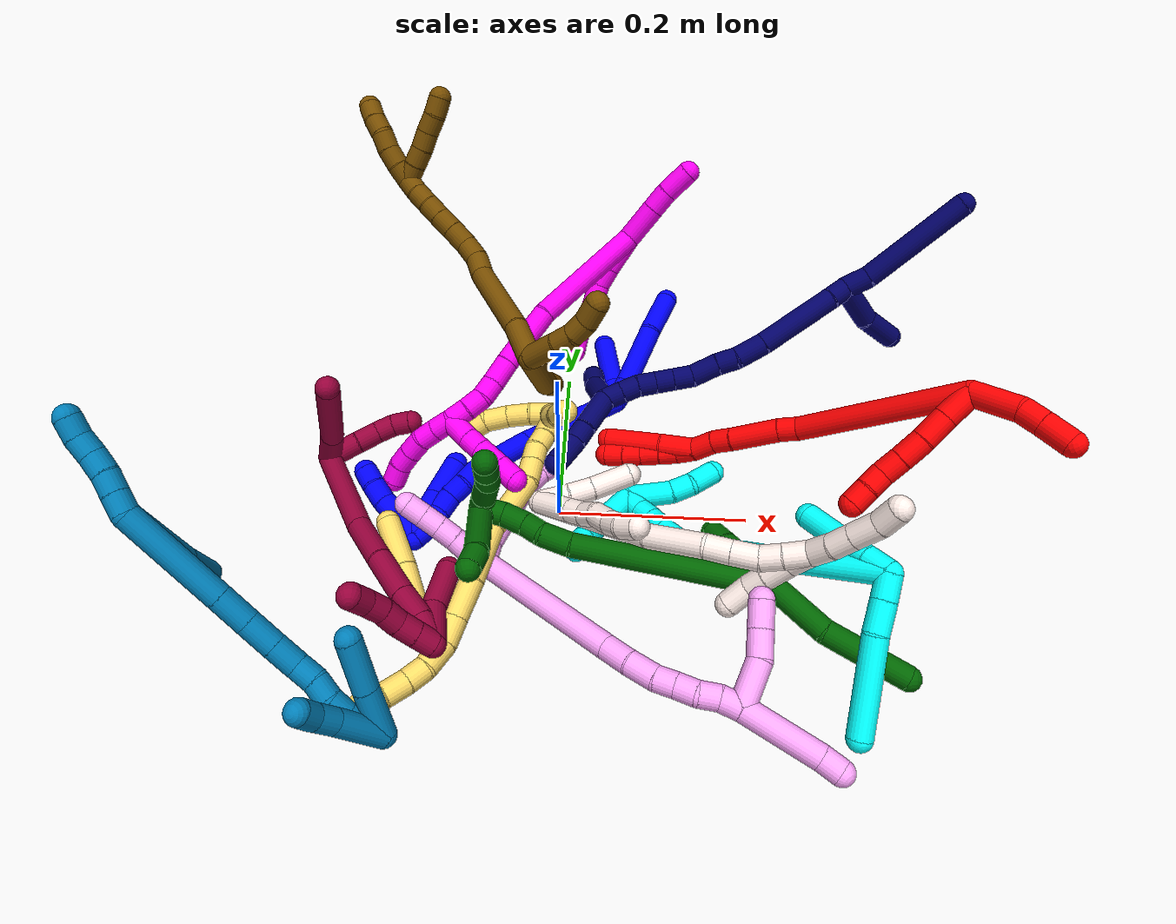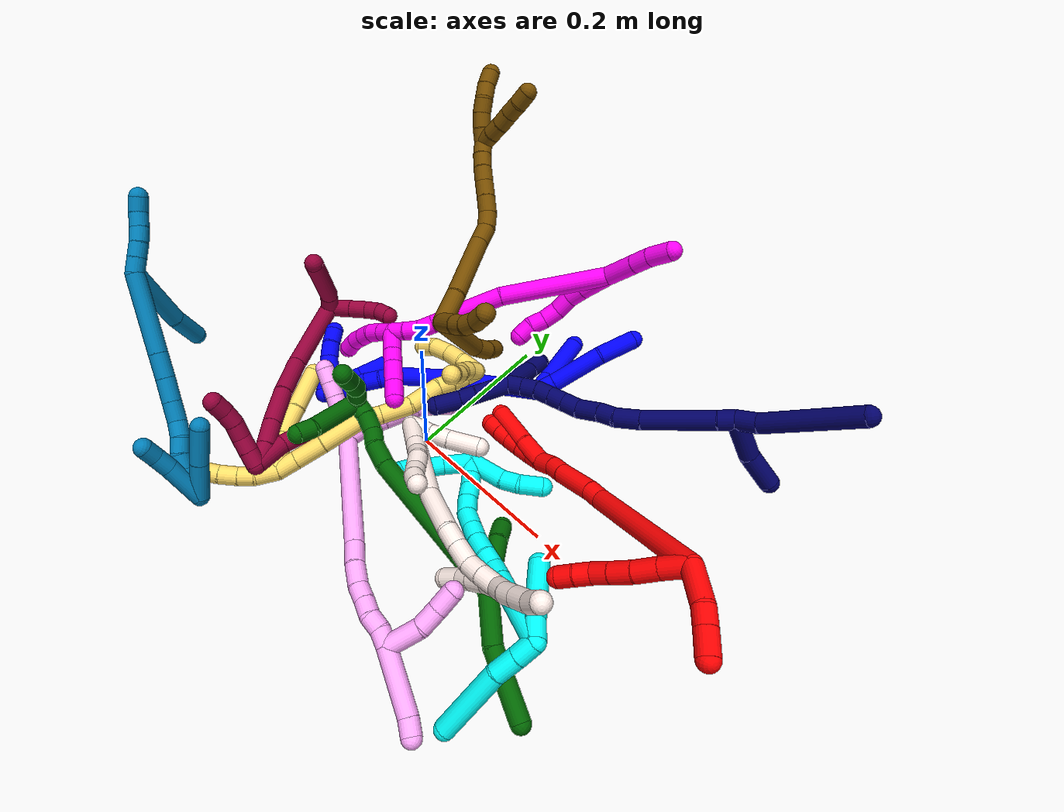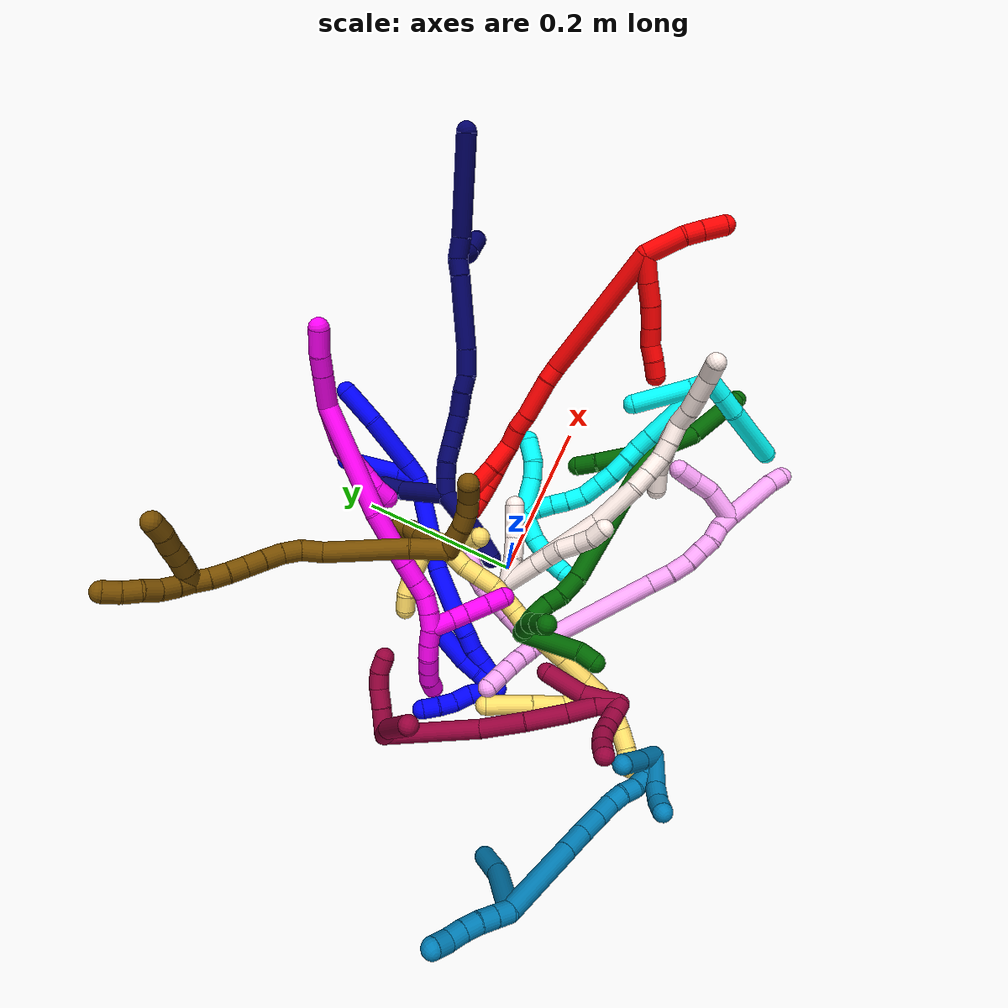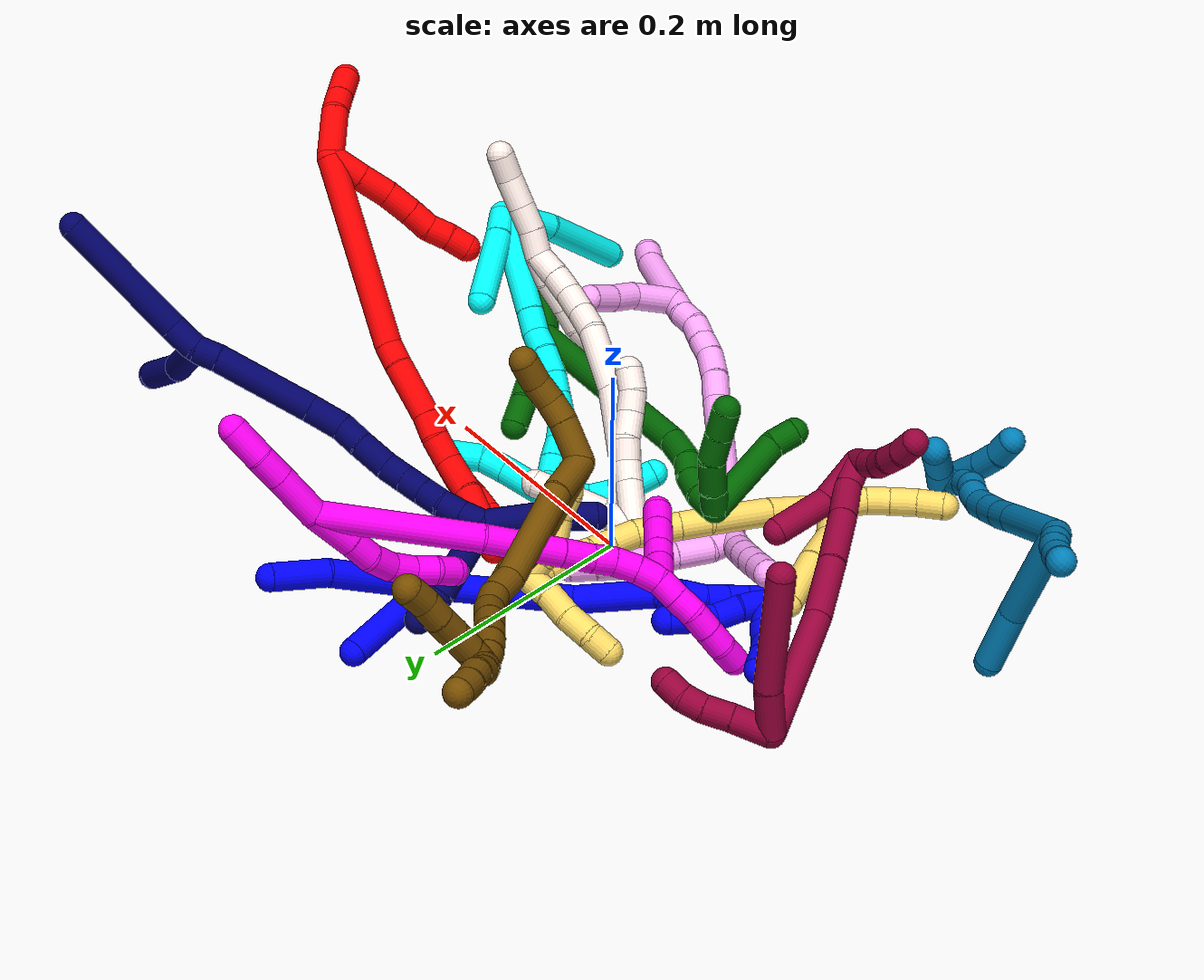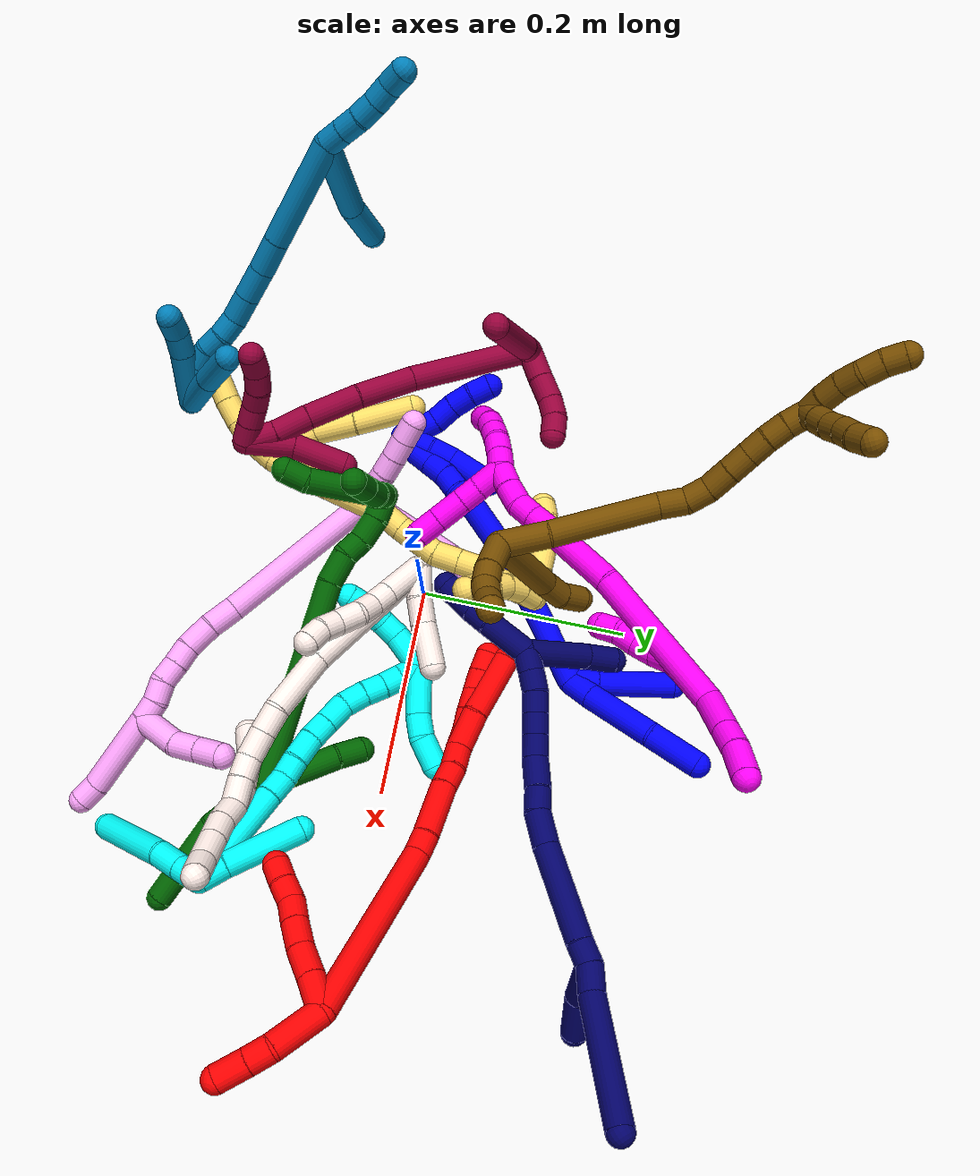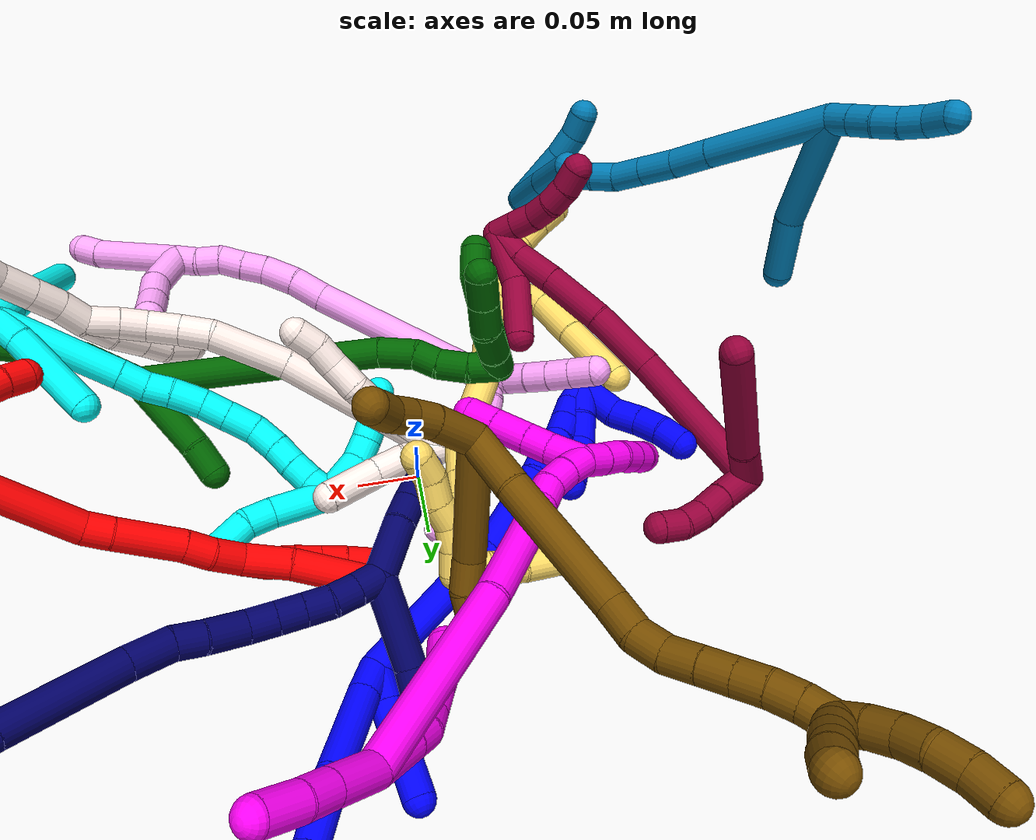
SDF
<sdf version="1.7">
 <world name="default">
  <plugin name="TubeGeneratorPlugin" filename="libtube_generator_plugin.so"/>
  <model name="photoneo_s_sensor">
   <static>1</static>
   <pose>0 0 2 1.57079 1.57079 3.14159</pose>
   <link name="link">
    <inertial><mass>0.1</mass></inertial>
    <sensor name="sensor" type="depth">
     <update_rate>30</update_rate>
     <camera>
      <horizontal_fov>1.22</horizontal_fov>
      <image><width>1920</width><height>1200</height><format>B8G8R8</format></image>
      <clip><near>0.1</near><far>4</far></clip>
      <depth_camera><output>points</output></depth_camera>
     </camera>
     <plugin name="camera_plugin" filename="libgazebo_ros_depth_camera.so">
      <baseline>0.2</baseline>
      <alwaysOn>1</alwaysOn>
      <updateRate>0.0</updateRate>
      <cameraName>camera_ir</cameraName>
      <imageTopicName>/camera/color/image_raw</imageTopicName>
      <cameraInfoTopicName>/camera/color/camera_info</cameraInfoTopicName>
      <depthImageTopicName>/camera/depth/image_raw</depthImageTopicName>
      <depthImageCameraInfoTopicName>/camera/depth/camera_info</depthImageCameraInfoTopicName>
      <pointCloudTopicName>/camera/depth/points</pointCloudTopicName>
      <frameName>fr_optical</frameName>
      <pointCloudCutoff>0.1</pointCloudCutoff>
      <pointCloudCutoffMax>2.0</pointCloudCutoffMax>
      <distortionK1>0</distortionK1>
      <distortionK2>0</distortionK2>
      <distortionK3>0</distortionK3>
      <distortionT1>0</distortionT1>
      <distortionT2>0</distortionT2>
      <CxPrime>0</CxPrime>
      <Cx>0</Cx>
      <Cy>0</Cy>
      <focalLength>0</focalLength>
      <hackBaseline>0</hackBaseline>
     </plugin>
    </sensor>
   </link>
  </model>
  <gravity>0 0 -9.8</gravity>
  <magnetic_field>6e-06 2.3e-05 -4.2e-05</magnetic_field>
  <atmosphere type="adiabatic"/>
  <physics name="default_physics" default="0" type="ode">
   <max_step_size>0.003</max_step_size>
   <real_time_factor>1</real_time_factor>
   <real_time_update_rate>1000</real_time_update_rate>
   <max_contacts>10000</max_contacts>
   <ode>
    <solver>
     <type>quick</type>
     <iters>100</iters>
     <sor>1.3</sor>
     <use_dynamic_moi_rescaling>0</use_dynamic_moi_rescaling>
    </solver>
    <constraints>
     <contact_max_correcting_vel>0</contact_max_correcting_vel>
     <contact_surface_layer>0.001</contact_surface_layer>
     <cfm>0</cfm>
     <erp>0.2</erp>
    </constraints>
   </ode>
  </physics>
  <scene><ambient>0.4 0.4 0.4 1</ambient><background>0.7 0.7 0.7 1</background><shadows>0</shadows></scene>
  <audio><device>default</device></audio>
  <spherical_coordinates>
   <surface_model>EARTH_WGS84</surface_model>
   <latitude_deg>0</latitude_deg>
   <longitude_deg>0</longitude_deg>
   <elevation>0</elevation>
   <heading_deg>0</heading_deg>
  </spherical_coordinates>
  <model name="bin">
   <static>1</static>
   <link name="bottom">
    <collision name="collision-bottom">
     <pose>0 0 -0.01 0 -0 0</pose>
     <geometry><box><size>0.8 0.6 0.02</size></box></geometry>
     <surface>
      <friction><ode><mu>100</mu><mu2>100</mu2></ode></friction>
      <contact><collide_bitmask>65535</collide_bitmask></contact>
     </surface>
    </collision>
   </link>
   <link name="west_wall">
    <collision name="collision-west_wall">
     <pose>-0.41 0 0.1 0 -0 0</pose>
     <geometry><box><size>0.02 0.6 0.2</size></box></geometry>
     <surface>
      <friction><ode><mu>100</mu><mu2>100</mu2></ode></friction>
      <contact><collide_bitmask>65535</collide_bitmask></contact>
     </surface>
    </collision>
   </link>
   <link name="east_wall">
    <collision name="collision-east_wall">
     <pose>0.41 0 0.1 0 -0 0</pose>
     <geometry><box><size>0.02 0.6 0.2</size></box></geometry>
     <surface>
      <friction><ode><mu>100</mu><mu2>100</mu2></ode></friction>
      <contact><collide_bitmask>65535</collide_bitmask></contact>
     </surface>
    </collision>
   </link>
   <link name="south_wall">
    <collision name="collision-south_wall">
     <pose>0 -0.31 0.1 0 -0 0</pose>
     <geometry><box><size>0.8 0.02 0.2</size></box></geometry>
     <surface>
      <friction><ode><mu>100</mu><mu2>100</mu2></ode></friction>
      <contact><collide_bitmask>65535</collide_bitmask></contact>
     </surface>
    </collision>
   </link>
   <link name="north_wall">
    <collision name="collision-north_wall">
     <pose>0 0.31 0.1 0 -0 0</pose>
     <geometry><box><size>0.8 0.02 0.2</size></box></geometry>
     <surface>
      <friction><ode><mu>100</mu><mu2>100</mu2></ode></friction>
      <contact><collide_bitmask>65535</collide_bitmask></contact>
     </surface>
    </collision>
   </link>
  </model>
  <model name="1">
   <static>0</static>
   <link name="1">
    <collision name="collision-cylinder-e_1_2_8">
     <pose>0.002596 0.008966 -0.009318 -2.37544 0.198146 -0.483657</pose>
     <geometry><cylinder><radius>0.0125</radius><length>0.026378</length></cylinder></geometry>
     <surface>
      <friction><ode><mu>1.16</mu><mu2>1.16</mu2><slip1>0</slip1><slip2>0</slip2></ode></friction>
      <contact><ode><kp>1e+06</kp><kd>1</kd><max_vel>0</max_vel><min_depth>0.001</min_depth></ode></contact>
     </surface>
    </collision>
    <visual name="visual-cylinder-e_1_2_8">
     <pose>0.002596 0.008966 -0.009318 -2.37544 0.198146 -0.483657</pose>
     <geometry><cylinder><radius>0.0125</radius><length>0.026378</length></cylinder></geometry>
     <material><ambient>0 0 1 1</ambient></material>
    </visual>
    <collision name="collision-cylinder-e_2_8_9">
     <pose>0.009701 0.042512 -0.044718 -2.38585 0.12514 -0.313083</pose>
     <geometry><cylinder><radius>0.0125</radius><length>0.072243</length></cylinder></geometry>
     <surface>
      <friction><ode><mu>1.16</mu><mu2>1.16</mu2><slip1>0</slip1><slip2>0</slip2></ode></friction>
      <contact><ode><kp>1e+06</kp><kd>1</kd><max_vel>0</max_vel><min_depth>0.001</min_depth></ode></contact>
     </surface>
    </collision>
    <visual name="visual-cylinder-e_2_8_9">
     <pose>0.009701 0.042512 -0.044718 -2.38585 0.12514 -0.313083</pose>
     <geometry><cylinder><radius>0.0125</radius><length>0.072243</length></cylinder></geometry>
     <material><ambient>0 0 1 1</ambient></material>
    </visual>
    <collision name="collision-cylinder-e_3_9_6">
     <pose>0.021567 0.08066 -0.091335 -2.55769 0.290461 -0.905831</pose>
     <geometry><cylinder><radius>0.0125</radius><length>0.051379</length></cylinder></geometry>
     <surface>
      <friction><ode><mu>1.16</mu><mu2>1.16</mu2><slip1>0</slip1><slip2>0</slip2></ode></friction>
      <contact><ode><kp>1e+06</kp><kd>1</kd><max_vel>0</max_vel><min_depth>0.001</min_depth></ode></contact>
     </surface>
    </collision>
    <visual name="visual-cylinder-e_3_9_6">
     <pose>0.021567 0.08066 -0.091335 -2.55769 0.290461 -0.905831</pose>
     <geometry><cylinder><radius>0.0125</radius><length>0.051379</length></cylinder></geometry>
     <material><ambient>0 0 1 1</ambient></material>
    </visual>
    <collision name="collision-cylinder-e_1_2_10">
     <pose>0.000977 0.000371 -0.013543 -3.11418 0.072007 -2.41428</pose>
     <geometry><cylinder><radius>0.0125</radius><length>0.027167</length></cylinder></geometry>
     <surface>
      <friction><ode><mu>1.16</mu><mu2>1.16</mu2><slip1>0</slip1><slip2>0</slip2></ode></friction>
      <contact><ode><kp>1e+06</kp><kd>1</kd><max_vel>0</max_vel><min_depth>0.001</min_depth></ode></contact>
     </surface>
    </collision>
    <visual name="visual-cylinder-e_1_2_10">
     <pose>0.000977 0.000371 -0.013543 -3.11418 0.072007 -2.41428</pose>
     <geometry><cylinder><radius>0.0125</radius><length>0.027167</length></cylinder></geometry>
     <material><ambient>0 0 1 1</ambient></material>
    </visual>
    <collision name="collision-cylinder-e_2_10_5">
     <pose>0.002852 0.001786 -0.063477 -3.11294 0.024643 -1.42057</pose>
     <geometry><cylinder><radius>0.0125</radius><length>0.072833</length></cylinder></geometry>
     <surface>
      <friction><ode><mu>1.16</mu><mu2>1.16</mu2><slip1>0</slip1><slip2>0</slip2></ode></friction>
      <contact><ode><kp>1e+06</kp><kd>1</kd><max_vel>0</max_vel><min_depth>0.001</min_depth></ode></contact>
     </surface>
    </collision>
    <visual name="visual-cylinder-e_2_10_5">
     <pose>0.002852 0.001786 -0.063477 -3.11294 0.024643 -1.42057</pose>
     <geometry><cylinder><radius>0.0125</radius><length>0.072833</length></cylinder></geometry>
     <material><ambient>0 0 1 1</ambient></material>
    </visual>
    <collision name="collision-cylinder-e_1_2_11">
     <pose>-0.046048 -0.034506 0.027168 0.903822 -0.809076 -0.409829</pose>
     <geometry><cylinder><radius>0.0125</radius><length>0.127266</length></cylinder></geometry>
     <surface>
      <friction><ode><mu>1.16</mu><mu2>1.16</mu2><slip1>0</slip1><slip2>0</slip2></ode></friction>
      <contact><ode><kp>1e+06</kp><kd>1</kd><max_vel>0</max_vel><min_depth>0.001</min_depth></ode></contact>
     </surface>
    </collision>
    <visual name="visual-cylinder-e_1_2_11">
     <pose>-0.046048 -0.034506 0.027168 0.903822 -0.809076 -0.409829</pose>
     <geometry><cylinder><radius>0.0125</radius><length>0.127266</length></cylinder></geometry>
     <material><ambient>0 0 1 1</ambient></material>
    </visual>
    <collision name="collision-cylinder-e_2_11_12">
     <pose>-0.116657 -0.083973 0.074091 0.6482 -0.780929 -0.274807</pose>
     <geometry><cylinder><radius>0.0125</radius><length>0.069781</length></cylinder></geometry>
     <surface>
      <friction><ode><mu>1.16</mu><mu2>1.16</mu2><slip1>0</slip1><slip2>0</slip2></ode></friction>
      <contact><ode><kp>1e+06</kp><kd>1</kd><max_vel>0</max_vel><min_depth>0.001</min_depth></ode></contact>
     </surface>
    </collision>
    <visual name="visual-cylinder-e_2_11_12">
     <pose>-0.116657 -0.083973 0.074091 0.6482 -0.780929 -0.274807</pose>
     <geometry><cylinder><radius>0.0125</radius><length>0.069781</length></cylinder></geometry>
     <material><ambient>0 0 1 1</ambient></material>
    </visual>
    <collision name="collision-cylinder-e_3_12_13">
     <pose>-0.146756 -0.105237 0.101372 0.697118 -0.513686 -0.190311</pose>
     <geometry><cylinder><radius>0.0125</radius><length>0.022541</length></cylinder></geometry>
     <surface>
      <friction><ode><mu>1.16</mu><mu2>1.16</mu2><slip1>0</slip1><slip2>0</slip2></ode></friction>
      <contact><ode><kp>1e+06</kp><kd>1</kd><max_vel>0</max_vel><min_depth>0.001</min_depth></ode></contact>
     </surface>
    </collision>
    <visual name="visual-cylinder-e_3_12_13">
     <pose>-0.146756 -0.105237 0.101372 0.697118 -0.513686 -0.190311</pose>
     <geometry><cylinder><radius>0.0125</radius><length>0.022541</length></cylinder></geometry>
     <material><ambient>0 0 1 1</ambient></material>
    </visual>
    <collision name="collision-cylinder-e_4_13_14">
     <pose>-0.156572 -0.118899 0.114417 0.927297 -0.435244 -0.22023</pose>
     <geometry><cylinder><radius>0.0125</radius><length>0.020291</length></cylinder></geometry>
     <surface>
      <friction><ode><mu>1.16</mu><mu2>1.16</mu2><slip1>0</slip1><slip2>0</slip2></ode></friction>
      <contact><ode><kp>1e+06</kp><kd>1</kd><max_vel>0</max_vel><min_depth>0.001</min_depth></ode></contact>
     </surface>
    </collision>
    <visual name="visual-cylinder-e_4_13_14">
     <pose>-0.156572 -0.118899 0.114417 0.927297 -0.435244 -0.22023</pose>
     <geometry><cylinder><radius>0.0125</radius><length>0.020291</length></cylinder></geometry>
     <material><ambient>0 0 1 1</ambient></material>
    </visual>
    <collision name="collision-cylinder-e_5_14_15">
     <pose>-0.164162 -0.132345 0.127231 0.695394 -0.335477 -0.122583</pose>
     <geometry><cylinder><radius>0.0125</radius><length>0.020119</length></cylinder></geometry>
     <surface>
      <friction><ode><mu>1.16</mu><mu2>1.16</mu2><slip1>0</slip1><slip2>0</slip2></ode></friction>
      <contact><ode><kp>1e+06</kp><kd>1</kd><max_vel>0</max_vel><min_depth>0.001</min_depth></ode></contact>
     </surface>
    </collision>
    <visual name="visual-cylinder-e_5_14_15">
     <pose>-0.164162 -0.132345 0.127231 0.695394 -0.335477 -0.122583</pose>
     <geometry><cylinder><radius>0.0125</radius><length>0.020119</length></cylinder></geometry>
     <material><ambient>0 0 1 1</ambient></material>
    </visual>
    <collision name="collision-cylinder-e_6_15_16">
     <pose>-0.170818 -0.144434 0.141788 0.690648 -0.34101 -0.123719</pose>
     <geometry><cylinder><radius>0.0125</radius><length>0.02</length></cylinder></geometry>
     <surface>
      <friction><ode><mu>1.16</mu><mu2>1.16</mu2><slip1>0</slip1><slip2>0</slip2></ode></friction>
      <contact><ode><kp>1e+06</kp><kd>1</kd><max_vel>0</max_vel><min_depth>0.001</min_depth></ode></contact>
     </surface>
    </collision>
    <visual name="visual-cylinder-e_6_15_16">
     <pose>-0.170818 -0.144434 0.141788 0.690648 -0.34101 -0.123719</pose>
     <geometry><cylinder><radius>0.0125</radius><length>0.02</length></cylinder></geometry>
     <material><ambient>0 0 1 1</ambient></material>
    </visual>
    <collision name="collision-cylinder-e_7_16_1">
     <pose>-0.179764 -0.156219 0.154987 0.772342 -0.594498 -0.247818</pose>
     <geometry><cylinder><radius>0.0125</radius><length>0.02</length></cylinder></geometry>
     <surface>
      <friction><ode><mu>1.16</mu><mu2>1.16</mu2><slip1>0</slip1><slip2>0</slip2></ode></friction>
      <contact><ode><kp>1e+06</kp><kd>1</kd><max_vel>0</max_vel><min_depth>0.001</min_depth></ode></contact>
     </surface>
    </collision>
    <visual name="visual-cylinder-e_7_16_1">
     <pose>-0.179764 -0.156219 0.154987 0.772342 -0.594498 -0.247818</pose>
     <geometry><cylinder><radius>0.0125</radius><length>0.02</length></cylinder></geometry>
     <material><ambient>0 0 1 1</ambient></material>
    </visual>
    <collision name="collision-cylinder-e_1_1_17">
     <pose>-0.181239 -0.155319 0.147072 -2.6921 0.262137 -1.04613</pose>
     <geometry><cylinder><radius>0.0125</radius><length>0.03184</length></cylinder></geometry>
     <surface>
      <friction><ode><mu>1.16</mu><mu2>1.16</mu2><slip1>0</slip1><slip2>0</slip2></ode></friction>
      <contact><ode><kp>1e+06</kp><kd>1</kd><max_vel>0</max_vel><min_depth>0.001</min_depth></ode></contact>
     </surface>
    </collision>
    <visual name="visual-cylinder-e_1_1_17">
     <pose>-0.181239 -0.155319 0.147072 -2.6921 0.262137 -1.04613</pose>
     <geometry><cylinder><radius>0.0125</radius><length>0.03184</length></cylinder></geometry>
     <material><ambient>0 0 1 1</ambient></material>
    </visual>
    <collision name="collision-cylinder-e_2_17_18">
     <pose>-0.172653 -0.145116 0.122499 -2.82432 0.376335 -1.7441</pose>
     <geometry><cylinder><radius>0.0125</radius><length>0.024274</length></cylinder></geometry>
     <surface>
      <friction><ode><mu>1.16</mu><mu2>1.16</mu2><slip1>0</slip1><slip2>0</slip2></ode></friction>
      <contact><ode><kp>1e+06</kp><kd>1</kd><max_vel>0</max_vel><min_depth>0.001</min_depth></ode></contact>
     </surface>
    </collision>
    <visual name="visual-cylinder-e_2_17_18">
     <pose>-0.172653 -0.145116 0.122499 -2.82432 0.376335 -1.7441</pose>
     <geometry><cylinder><radius>0.0125</radius><length>0.024274</length></cylinder></geometry>
     <material><ambient>0 0 1 1</ambient></material>
    </visual>
    <collision name="collision-cylinder-e_3_18_4">
     <pose>-0.161839 -0.129486 0.094614 -2.52712 0.29373 -0.872554</pose>
     <geometry><cylinder><radius>0.0125</radius><length>0.043887</length></cylinder></geometry>
     <surface>
      <friction><ode><mu>1.16</mu><mu2>1.16</mu2><slip1>0</slip1><slip2>0</slip2></ode></friction>
      <contact><ode><kp>1e+06</kp><kd>1</kd><max_vel>0</max_vel><min_depth>0.001</min_depth></ode></contact>
     </surface>
    </collision>
    <visual name="visual-cylinder-e_3_18_4">
     <pose>-0.161839 -0.129486 0.094614 -2.52712 0.29373 -0.872554</pose>
     <geometry><cylinder><radius>0.0125</radius><length>0.043887</length></cylinder></geometry>
     <material><ambient>0 0 1 1</ambient></material>
    </visual>
    <collision name="collision-cylinder-e_1_1_19">
     <pose>-0.191286 -0.166304 0.145033 2.87703 -0.345344 -1.83815</pose>
     <geometry><cylinder><radius>0.0125</radius><length>0.034986</length></cylinder></geometry>
     <surface>
      <friction><ode><mu>1.16</mu><mu2>1.16</mu2><slip1>0</slip1><slip2>0</slip2></ode></friction>
      <contact><ode><kp>1e+06</kp><kd>1</kd><max_vel>0</max_vel><min_depth>0.001</min_depth></ode></contact>
     </surface>
    </collision>
    <visual name="visual-cylinder-e_1_1_19">
     <pose>-0.191286 -0.166304 0.145033 2.87703 -0.345344 -1.83815</pose>
     <geometry><cylinder><radius>0.0125</radius><length>0.034986</length></cylinder></geometry>
     <material><ambient>0 0 1 1</ambient></material>
    </visual>
    <collision name="collision-cylinder-e_2_19_20">
     <pose>-0.204352 -0.173041 0.120445 2.86898 -0.669079 -2.38994</pose>
     <geometry><cylinder><radius>0.0125</radius><length>0.023036</length></cylinder></geometry>
     <surface>
      <friction><ode><mu>1.16</mu><mu2>1.16</mu2><slip1>0</slip1><slip2>0</slip2></ode></friction>
      <contact><ode><kp>1e+06</kp><kd>1</kd><max_vel>0</max_vel><min_depth>0.001</min_depth></ode></contact>
     </surface>
    </collision>
    <visual name="visual-cylinder-e_2_19_20">
     <pose>-0.204352 -0.173041 0.120445 2.86898 -0.669079 -2.38994</pose>
     <geometry><cylinder><radius>0.0125</radius><length>0.023036</length></cylinder></geometry>
     <material><ambient>0 0 1 1</ambient></material>
    </visual>
    <collision name="collision-cylinder-e_3_20_21">
     <pose>-0.217433 -0.175911 0.102625 3.09363 -0.576539 -2.98016</pose>
     <geometry><cylinder><radius>0.0125</radius><length>0.021778</length></cylinder></geometry>
     <surface>
      <friction><ode><mu>1.16</mu><mu2>1.16</mu2><slip1>0</slip1><slip2>0</slip2></ode></friction>
      <contact><ode><kp>1e+06</kp><kd>1</kd><max_vel>0</max_vel><min_depth>0.001</min_depth></ode></contact>
     </surface>
    </collision>
    <visual name="visual-cylinder-e_3_20_21">
     <pose>-0.217433 -0.175911 0.102625 3.09363 -0.576539 -2.98016</pose>
     <geometry><cylinder><radius>0.0125</radius><length>0.021778</length></cylinder></geometry>
     <material><ambient>0 0 1 1</ambient></material>
    </visual>
    <collision name="collision-cylinder-e_4_21_3">
     <pose>-0.22739 -0.177474 0.084311 3.01984 -0.409519 -2.57062</pose>
     <geometry><cylinder><radius>0.0125</radius><length>0.020199</length></cylinder></geometry>
     <surface>
      <friction><ode><mu>1.16</mu><mu2>1.16</mu2><slip1>0</slip1><slip2>0</slip2></ode></friction>
      <contact><ode><kp>1e+06</kp><kd>1</kd><max_vel>0</max_vel><min_depth>0.001</min_depth></ode></contact>
     </surface>
    </collision>
    <visual name="visual-cylinder-e_4_21_3">
     <pose>-0.22739 -0.177474 0.084311 3.01984 -0.409519 -2.57062</pose>
     <geometry><cylinder><radius>0.0125</radius><length>0.020199</length></cylinder></geometry>
     <material><ambient>0 0 1 1</ambient></material>
    </visual>
    <collision name="collision-sphere-3">
     <pose>-0.231411 -0.178599 0.075115 0 -0 0</pose>
     <geometry><sphere><radius>0.0125</radius></sphere></geometry>
     <surface>
      <friction><ode><mu>1.16</mu><mu2>1.16</mu2><slip1>0</slip1><slip2>0</slip2></ode></friction>
      <contact><ode><kp>1e+06</kp><kd>1</kd><max_vel>0</max_vel><min_depth>0.001</min_depth></ode></contact>
     </surface>
    </collision>
    <visual name="visual-sphere-3">
     <pose>-0.231411 -0.178599 0.075115 0 -0 0</pose>
     <geometry><sphere><radius>0.0125</radius></sphere></geometry>
     <material><ambient>0 0 1 1</ambient></material>
    </visual>
    <collision name="collision-sphere-21">
     <pose>-0.223369 -0.176349 0.093507 0 -0 0</pose>
     <geometry><sphere><radius>0.0125</radius></sphere></geometry>
     <surface>
      <friction><ode><mu>1.16</mu><mu2>1.16</mu2><slip1>0</slip1><slip2>0</slip2></ode></friction>
      <contact><ode><kp>1e+06</kp><kd>1</kd><max_vel>0</max_vel><min_depth>0.001</min_depth></ode></contact>
     </surface>
    </collision>
    <visual name="visual-sphere-21">
     <pose>-0.223369 -0.176349 0.093507 0 -0 0</pose>
     <geometry><sphere><radius>0.0125</radius></sphere></geometry>
     <material><ambient>0 0 1 1</ambient></material>
    </visual>
    <collision name="collision-sphere-20">
     <pose>-0.211497 -0.175474 0.111743 0 -0 0</pose>
     <geometry><sphere><radius>0.0125</radius></sphere></geometry>
     <surface>
      <friction><ode><mu>1.16</mu><mu2>1.16</mu2><slip1>0</slip1><slip2>0</slip2></ode></friction>
      <contact><ode><kp>1e+06</kp><kd>1</kd><max_vel>0</max_vel><min_depth>0.001</min_depth></ode></contact>
     </surface>
    </collision>
    <visual name="visual-sphere-20">
     <pose>-0.211497 -0.175474 0.111743 0 -0 0</pose>
     <geometry><sphere><radius>0.0125</radius></sphere></geometry>
     <material><ambient>0 0 1 1</ambient></material>
    </visual>
    <collision name="collision-sphere-19">
     <pose>-0.197208 -0.170608 0.129146 0 -0 0</pose>
     <geometry><sphere><radius>0.0125</radius></sphere></geometry>
     <surface>
      <friction><ode><mu>1.16</mu><mu2>1.16</mu2><slip1>0</slip1><slip2>0</slip2></ode></friction>
      <contact><ode><kp>1e+06</kp><kd>1</kd><max_vel>0</max_vel><min_depth>0.001</min_depth></ode></contact>
     </surface>
    </collision>
    <visual name="visual-sphere-19">
     <pose>-0.197208 -0.170608 0.129146 0 -0 0</pose>
     <geometry><sphere><radius>0.0125</radius></sphere></geometry>
     <material><ambient>0 0 1 1</ambient></material>
    </visual>
    <collision name="collision-sphere-5">
     <pose>0.003749 0.002829 -0.099867 0 -0 0</pose>
     <geometry><sphere><radius>0.0125</radius></sphere></geometry>
     <surface>
      <friction><ode><mu>1.16</mu><mu2>1.16</mu2><slip1>0</slip1><slip2>0</slip2></ode></friction>
      <contact><ode><kp>1e+06</kp><kd>1</kd><max_vel>0</max_vel><min_depth>0.001</min_depth></ode></contact>
     </surface>
    </collision>
    <visual name="visual-sphere-5">
     <pose>0.003749 0.002829 -0.099867 0 -0 0</pose>
     <geometry><sphere><radius>0.0125</radius></sphere></geometry>
     <material><ambient>0 0 1 1</ambient></material>
    </visual>
    <collision name="collision-sphere-10">
     <pose>0.001954 0.000743 -0.027086 0 -0 0</pose>
     <geometry><sphere><radius>0.0125</radius></sphere></geometry>
     <surface>
      <friction><ode><mu>1.16</mu><mu2>1.16</mu2><slip1>0</slip1><slip2>0</slip2></ode></friction>
      <contact><ode><kp>1e+06</kp><kd>1</kd><max_vel>0</max_vel><min_depth>0.001</min_depth></ode></contact>
     </surface>
    </collision>
    <visual name="visual-sphere-10">
     <pose>0.001954 0.000743 -0.027086 0 -0 0</pose>
     <geometry><sphere><radius>0.0125</radius></sphere></geometry>
     <material><ambient>0 0 1 1</ambient></material>
    </visual>
    <collision name="collision-sphere-6">
     <pose>0.028924 0.094229 -0.111871 0 -0 0</pose>
     <geometry><sphere><radius>0.0125</radius></sphere></geometry>
     <surface>
      <friction><ode><mu>1.16</mu><mu2>1.16</mu2><slip1>0</slip1><slip2>0</slip2></ode></friction>
      <contact><ode><kp>1e+06</kp><kd>1</kd><max_vel>0</max_vel><min_depth>0.001</min_depth></ode></contact>
     </surface>
    </collision>
    <visual name="visual-sphere-6">
     <pose>0.028924 0.094229 -0.111871 0 -0 0</pose>
     <geometry><sphere><radius>0.0125</radius></sphere></geometry>
     <material><ambient>0 0 1 1</ambient></material>
    </visual>
    <collision name="collision-sphere-9">
     <pose>0.014209 0.067091 -0.0708 0 -0 0</pose>
     <geometry><sphere><radius>0.0125</radius></sphere></geometry>
     <surface>
      <friction><ode><mu>1.16</mu><mu2>1.16</mu2><slip1>0</slip1><slip2>0</slip2></ode></friction>
      <contact><ode><kp>1e+06</kp><kd>1</kd><max_vel>0</max_vel><min_depth>0.001</min_depth></ode></contact>
     </surface>
    </collision>
    <visual name="visual-sphere-9">
     <pose>0.014209 0.067091 -0.0708 0 -0 0</pose>
     <geometry><sphere><radius>0.0125</radius></sphere></geometry>
     <material><ambient>0 0 1 1</ambient></material>
    </visual>
    <collision name="collision-sphere-2">
     <geometry><sphere><radius>0.0125</radius></sphere></geometry>
     <surface>
      <friction><ode><mu>1.16</mu><mu2>1.16</mu2><slip1>0</slip1><slip2>0</slip2></ode></friction>
      <contact><ode><kp>1e+06</kp><kd>1</kd><max_vel>0</max_vel><min_depth>0.001</min_depth></ode></contact>
     </surface>
    </collision>
    <visual name="visual-sphere-2">
     <geometry><sphere><radius>0.0125</radius></sphere></geometry>
     <material><ambient>0 0 1 1</ambient></material>
    </visual>
    <collision name="collision-sphere-8">
     <pose>0.005193 0.017932 -0.018636 0 -0 0</pose>
     <geometry><sphere><radius>0.0125</radius></sphere></geometry>
     <surface>
      <friction><ode><mu>1.16</mu><mu2>1.16</mu2><slip1>0</slip1><slip2>0</slip2></ode></friction>
      <contact><ode><kp>1e+06</kp><kd>1</kd><max_vel>0</max_vel><min_depth>0.001</min_depth></ode></contact>
     </surface>
    </collision>
    <visual name="visual-sphere-8">
     <pose>0.005193 0.017932 -0.018636 0 -0 0</pose>
     <geometry><sphere><radius>0.0125</radius></sphere></geometry>
     <material><ambient>0 0 1 1</ambient></material>
    </visual>
    <collision name="collision-sphere-11">
     <pose>-0.092096 -0.069012 0.054336 0 -0 0</pose>
     <geometry><sphere><radius>0.0125</radius></sphere></geometry>
     <surface>
      <friction><ode><mu>1.16</mu><mu2>1.16</mu2><slip1>0</slip1><slip2>0</slip2></ode></friction>
      <contact><ode><kp>1e+06</kp><kd>1</kd><max_vel>0</max_vel><min_depth>0.001</min_depth></ode></contact>
     </surface>
    </collision>
    <visual name="visual-sphere-11">
     <pose>-0.092096 -0.069012 0.054336 0 -0 0</pose>
     <geometry><sphere><radius>0.0125</radius></sphere></geometry>
     <material><ambient>0 0 1 1</ambient></material>
    </visual>
    <collision name="collision-sphere-12">
     <pose>-0.141218 -0.098935 0.093846 0 -0 0</pose>
     <geometry><sphere><radius>0.0125</radius></sphere></geometry>
     <surface>
      <friction><ode><mu>1.16</mu><mu2>1.16</mu2><slip1>0</slip1><slip2>0</slip2></ode></friction>
      <contact><ode><kp>1e+06</kp><kd>1</kd><max_vel>0</max_vel><min_depth>0.001</min_depth></ode></contact>
     </surface>
    </collision>
    <visual name="visual-sphere-12">
     <pose>-0.141218 -0.098935 0.093846 0 -0 0</pose>
     <geometry><sphere><radius>0.0125</radius></sphere></geometry>
     <material><ambient>0 0 1 1</ambient></material>
    </visual>
    <collision name="collision-sphere-13">
     <pose>-0.152294 -0.111539 0.108898 0 -0 0</pose>
     <geometry><sphere><radius>0.0125</radius></sphere></geometry>
     <surface>
      <friction><ode><mu>1.16</mu><mu2>1.16</mu2><slip1>0</slip1><slip2>0</slip2></ode></friction>
      <contact><ode><kp>1e+06</kp><kd>1</kd><max_vel>0</max_vel><min_depth>0.001</min_depth></ode></contact>
     </surface>
    </collision>
    <visual name="visual-sphere-13">
     <pose>-0.152294 -0.111539 0.108898 0 -0 0</pose>
     <geometry><sphere><radius>0.0125</radius></sphere></geometry>
     <material><ambient>0 0 1 1</ambient></material>
    </visual>
    <collision name="collision-sphere-14">
     <pose>-0.16085 -0.126259 0.119937 0 -0 0</pose>
     <geometry><sphere><radius>0.0125</radius></sphere></geometry>
     <surface>
      <friction><ode><mu>1.16</mu><mu2>1.16</mu2><slip1>0</slip1><slip2>0</slip2></ode></friction>
      <contact><ode><kp>1e+06</kp><kd>1</kd><max_vel>0</max_vel><min_depth>0.001</min_depth></ode></contact>
     </surface>
    </collision>
    <visual name="visual-sphere-14">
     <pose>-0.16085 -0.126259 0.119937 0 -0 0</pose>
     <geometry><sphere><radius>0.0125</radius></sphere></geometry>
     <material><ambient>0 0 1 1</ambient></material>
    </visual>
    <collision name="collision-sphere-15">
     <pose>-0.167474 -0.138431 0.134524 0 -0 0</pose>
     <geometry><sphere><radius>0.0125</radius></sphere></geometry>
     <surface>
      <friction><ode><mu>1.16</mu><mu2>1.16</mu2><slip1>0</slip1><slip2>0</slip2></ode></friction>
      <contact><ode><kp>1e+06</kp><kd>1</kd><max_vel>0</max_vel><min_depth>0.001</min_depth></ode></contact>
     </surface>
    </collision>
    <visual name="visual-sphere-15">
     <pose>-0.167474 -0.138431 0.134524 0 -0 0</pose>
     <geometry><sphere><radius>0.0125</radius></sphere></geometry>
     <material><ambient>0 0 1 1</ambient></material>
    </visual>
    <collision name="collision-sphere-16">
     <pose>-0.174162 -0.150438 0.149053 0 -0 0</pose>
     <geometry><sphere><radius>0.0125</radius></sphere></geometry>
     <surface>
      <friction><ode><mu>1.16</mu><mu2>1.16</mu2><slip1>0</slip1><slip2>0</slip2></ode></friction>
      <contact><ode><kp>1e+06</kp><kd>1</kd><max_vel>0</max_vel><min_depth>0.001</min_depth></ode></contact>
     </surface>
    </collision>
    <visual name="visual-sphere-16">
     <pose>-0.174162 -0.150438 0.149053 0 -0 0</pose>
     <geometry><sphere><radius>0.0125</radius></sphere></geometry>
     <material><ambient>0 0 1 1</ambient></material>
    </visual>
    <collision name="collision-sphere-1">
     <pose>-0.185365 -0.162 0.160921 0 -0 0</pose>
     <geometry><sphere><radius>0.0125</radius></sphere></geometry>
     <surface>
      <friction><ode><mu>1.16</mu><mu2>1.16</mu2><slip1>0</slip1><slip2>0</slip2></ode></friction>
      <contact><ode><kp>1e+06</kp><kd>1</kd><max_vel>0</max_vel><min_depth>0.001</min_depth></ode></contact>
     </surface>
    </collision>
    <visual name="visual-sphere-1">
     <pose>-0.185365 -0.162 0.160921 0 -0 0</pose>
     <geometry><sphere><radius>0.0125</radius></sphere></geometry>
     <material><ambient>0 0 1 1</ambient></material>
    </visual>
    <collision name="collision-sphere-18">
     <pose>-0.168193 -0.141595 0.111775 0 -0 0</pose>
     <geometry><sphere><radius>0.0125</radius></sphere></geometry>
     <surface>
      <friction><ode><mu>1.16</mu><mu2>1.16</mu2><slip1>0</slip1><slip2>0</slip2></ode></friction>
      <contact><ode><kp>1e+06</kp><kd>1</kd><max_vel>0</max_vel><min_depth>0.001</min_depth></ode></contact>
     </surface>
    </collision>
    <visual name="visual-sphere-18">
     <pose>-0.168193 -0.141595 0.111775 0 -0 0</pose>
     <geometry><sphere><radius>0.0125</radius></sphere></geometry>
     <material><ambient>0 0 1 1</ambient></material>
    </visual>
    <collision name="collision-sphere-17">
     <pose>-0.177113 -0.148638 0.133223 0 -0 0</pose>
     <geometry><sphere><radius>0.0125</radius></sphere></geometry>
     <surface>
      <friction><ode><mu>1.16</mu><mu2>1.16</mu2><slip1>0</slip1><slip2>0</slip2></ode></friction>
      <contact><ode><kp>1e+06</kp><kd>1</kd><max_vel>0</max_vel><min_depth>0.001</min_depth></ode></contact>
     </surface>
    </collision>
    <visual name="visual-sphere-17">
     <pose>-0.177113 -0.148638 0.133223 0 -0 0</pose>
     <geometry><sphere><radius>0.0125</radius></sphere></geometry>
     <material><ambient>0 0 1 1</ambient></material>
    </visual>
    <collision name="collision-sphere-4">
     <pose>-0.155486 -0.117377 0.077452 0 -0 0</pose>
     <geometry><sphere><radius>0.0125</radius></sphere></geometry>
     <surface>
      <friction><ode><mu>1.16</mu><mu2>1.16</mu2><slip1>0</slip1><slip2>0</slip2></ode></friction>
      <contact><ode><kp>1e+06</kp><kd>1</kd><max_vel>0</max_vel><min_depth>0.001</min_depth></ode></contact>
     </surface>
    </collision>
    <visual name="visual-sphere-4">
     <pose>-0.155486 -0.117377 0.077452 0 -0 0</pose>
     <geometry><sphere><radius>0.0125</radius></sphere></geometry>
     <material><ambient>0 0 1 1</ambient></material>
    </visual>
    <inertial>
     <pose>-0.088642 -0.063321 0.042887 0 -0 0</pose>
     <mass>0.75</mass>
     <inertia><ixx>4.2e-05</ixx><ixy>0</ixy><ixz>0</ixz><iyy>8e-06</iyy><iyz>0</iyz><izz>0.000202</izz></inertia>
    </inertial>
   </link>
   <pose>0.057024 0.158059 0.01216 1.55038 0.708166 0.202677</pose>
  </model>
  <model name="2">
   <static>0</static>
   <link name="2">
    <collision name="collision-cylinder-e_1_2_8">
     <pose>-0.004548 -0.010195 -0.011617 2.42126 -0.286192 -0.730817</pose>
     <geometry><cylinder><radius>0.0125</radius><length>0.032223</length></cylinder></geometry>
     <surface>
      <friction><ode><mu>1.16</mu><mu2>1.16</mu2><slip1>0</slip1><slip2>0</slip2></ode></friction>
      <contact><ode><kp>1e+06</kp><kd>1</kd><max_vel>0</max_vel><min_depth>0.001</min_depth></ode></contact>
     </surface>
    </collision>
    <visual name="visual-cylinder-e_1_2_8">
     <pose>-0.004548 -0.010195 -0.011617 2.42126 -0.286192 -0.730817</pose>
     <geometry><cylinder><radius>0.0125</radius><length>0.032223</length></cylinder></geometry>
     <material><ambient>1 0 0 1</ambient></material>
    </visual>
    <collision name="collision-cylinder-e_2_8_9">
     <pose>-0.013043 -0.030067 -0.03327 2.3745 -0.27586 -0.662628</pose>
     <geometry><cylinder><radius>0.0125</radius><length>0.028978</length></cylinder></geometry>
     <surface>
      <friction><ode><mu>1.16</mu><mu2>1.16</mu2><slip1>0</slip1><slip2>0</slip2></ode></friction>
      <contact><ode><kp>1e+06</kp><kd>1</kd><max_vel>0</max_vel><min_depth>0.001</min_depth></ode></contact>
     </surface>
    </collision>
    <visual name="visual-cylinder-e_2_8_9">
     <pose>-0.013043 -0.030067 -0.03327 2.3745 -0.27586 -0.662628</pose>
     <geometry><cylinder><radius>0.0125</radius><length>0.028978</length></cylinder></geometry>
     <material><ambient>1 0 0 1</ambient></material>
    </visual>
    <collision name="collision-cylinder-e_3_9_10">
     <pose>-0.02032 -0.047425 -0.053485 2.49503 -0.255484 -0.732169</pose>
     <geometry><cylinder><radius>0.0125</radius><length>0.026359</length></cylinder></geometry>
     <surface>
      <friction><ode><mu>1.16</mu><mu2>1.16</mu2><slip1>0</slip1><slip2>0</slip2></ode></friction>
      <contact><ode><kp>1e+06</kp><kd>1</kd><max_vel>0</max_vel><min_depth>0.001</min_depth></ode></contact>
     </surface>
    </collision>
    <visual name="visual-cylinder-e_3_9_10">
     <pose>-0.02032 -0.047425 -0.053485 2.49503 -0.255484 -0.732169</pose>
     <geometry><cylinder><radius>0.0125</radius><length>0.026359</length></cylinder></geometry>
     <material><ambient>1 0 0 1</ambient></material>
    </visual>
    <collision name="collision-cylinder-e_4_10_11">
     <pose>-0.026161 -0.061162 -0.07268 2.55022 -0.227138 -0.71655</pose>
     <geometry><cylinder><radius>0.0125</radius><length>0.022295</length></cylinder></geometry>
     <surface>
      <friction><ode><mu>1.16</mu><mu2>1.16</mu2><slip1>0</slip1><slip2>0</slip2></ode></friction>
      <contact><ode><kp>1e+06</kp><kd>1</kd><max_vel>0</max_vel><min_depth>0.001</min_depth></ode></contact>
     </surface>
    </collision>
    <visual name="visual-cylinder-e_4_10_11">
     <pose>-0.026161 -0.061162 -0.07268 2.55022 -0.227138 -0.71655</pose>
     <geometry><cylinder><radius>0.0125</radius><length>0.022295</length></cylinder></geometry>
     <material><ambient>1 0 0 1</ambient></material>
    </visual>
    <collision name="collision-cylinder-e_5_11_12">
     <pose>-0.032763 -0.074 -0.087866 2.30889 -0.41977 -0.897853</pose>
     <geometry><cylinder><radius>0.0125</radius><length>0.02008</length></cylinder></geometry>
     <surface>
      <friction><ode><mu>1.16</mu><mu2>1.16</mu2><slip1>0</slip1><slip2>0</slip2></ode></friction>
      <contact><ode><kp>1e+06</kp><kd>1</kd><max_vel>0</max_vel><min_depth>0.001</min_depth></ode></contact>
     </surface>
    </collision>
    <visual name="visual-cylinder-e_5_11_12">
     <pose>-0.032763 -0.074 -0.087866 2.30889 -0.41977 -0.897853</pose>
     <geometry><cylinder><radius>0.0125</radius><length>0.02008</length></cylinder></geometry>
     <material><ambient>1 0 0 1</ambient></material>
    </visual>
    <collision name="collision-cylinder-e_6_12_6">
     <pose>-0.039939 -0.087379 -0.100935 2.37867 -0.312443 -0.748347</pose>
     <geometry><cylinder><radius>0.0125</radius><length>0.020065</length></cylinder></geometry>
     <surface>
      <friction><ode><mu>1.16</mu><mu2>1.16</mu2><slip1>0</slip1><slip2>0</slip2></ode></friction>
      <contact><ode><kp>1e+06</kp><kd>1</kd><max_vel>0</max_vel><min_depth>0.001</min_depth></ode></contact>
     </surface>
    </collision>
    <visual name="visual-cylinder-e_6_12_6">
     <pose>-0.039939 -0.087379 -0.100935 2.37867 -0.312443 -0.748347</pose>
     <geometry><cylinder><radius>0.0125</radius><length>0.020065</length></cylinder></geometry>
     <material><ambient>1 0 0 1</ambient></material>
    </visual>
    <collision name="collision-cylinder-e_1_2_13">
     <pose>0.001997 -0.012794 0.020894 0.549448 0.081314 0.02293</pose>
     <geometry><cylinder><radius>0.0125</radius><length>0.049163</length></cylinder></geometry>
     <surface>
      <friction><ode><mu>1.16</mu><mu2>1.16</mu2><slip1>0</slip1><slip2>0</slip2></ode></friction>
      <contact><ode><kp>1e+06</kp><kd>1</kd><max_vel>0</max_vel><min_depth>0.001</min_depth></ode></contact>
     </surface>
    </collision>
    <visual name="visual-cylinder-e_1_2_13">
     <pose>0.001997 -0.012794 0.020894 0.549448 0.081314 0.02293</pose>
     <geometry><cylinder><radius>0.0125</radius><length>0.049163</length></cylinder></geometry>
     <material><ambient>1 0 0 1</ambient></material>
    </visual>
    <collision name="collision-cylinder-e_2_13_14">
     <pose>0.006179 -0.033266 0.04914 0.807061 0.202752 0.08681</pose>
     <geometry><cylinder><radius>0.0125</radius><length>0.021705</length></cylinder></geometry>
     <surface>
      <friction><ode><mu>1.16</mu><mu2>1.16</mu2><slip1>0</slip1><slip2>0</slip2></ode></friction>
      <contact><ode><kp>1e+06</kp><kd>1</kd><max_vel>0</max_vel><min_depth>0.001</min_depth></ode></contact>
     </surface>
    </collision>
    <visual name="visual-cylinder-e_2_13_14">
     <pose>0.006179 -0.033266 0.04914 0.807061 0.202752 0.08681</pose>
     <geometry><cylinder><radius>0.0125</radius><length>0.021705</length></cylinder></geometry>
     <material><ambient>1 0 0 1</ambient></material>
    </visual>
    <collision name="collision-cylinder-e_3_14_5">
     <pose>0.011244 -0.051591 0.066007 0.841483 0.19906 0.089308</pose>
     <geometry><cylinder><radius>0.0125</radius><length>0.029132</length></cylinder></geometry>
     <surface>
      <friction><ode><mu>1.16</mu><mu2>1.16</mu2><slip1>0</slip1><slip2>0</slip2></ode></friction>
      <contact><ode><kp>1e+06</kp><kd>1</kd><max_vel>0</max_vel><min_depth>0.001</min_depth></ode></contact>
     </surface>
    </collision>
    <visual name="visual-cylinder-e_3_14_5">
     <pose>0.011244 -0.051591 0.066007 0.841483 0.19906 0.089308</pose>
     <geometry><cylinder><radius>0.0125</radius><length>0.029132</length></cylinder></geometry>
     <material><ambient>1 0 0 1</ambient></material>
    </visual>
    <collision name="collision-cylinder-e_1_2_15">
     <pose>-0.004742 0.002223 -0.089656 -3.11681 -0.052825 2.2643</pose>
     <geometry><cylinder><radius>0.0125</radius><length>0.179617</length></cylinder></geometry>
     <surface>
      <friction><ode><mu>1.16</mu><mu2>1.16</mu2><slip1>0</slip1><slip2>0</slip2></ode></friction>
      <contact><ode><kp>1e+06</kp><kd>1</kd><max_vel>0</max_vel><min_depth>0.001</min_depth></ode></contact>
     </surface>
    </collision>
    <visual name="visual-cylinder-e_1_2_15">
     <pose>-0.004742 0.002223 -0.089656 -3.11681 -0.052825 2.2643</pose>
     <geometry><cylinder><radius>0.0125</radius><length>0.179617</length></cylinder></geometry>
     <material><ambient>1 0 0 1</ambient></material>
    </visual>
    <collision name="collision-cylinder-e_2_15_16">
     <pose>-0.012728 0.005115 -0.189192 -3.07391 -0.31661 2.72368</pose>
     <geometry><cylinder><radius>0.0125</radius><length>0.020841</length></cylinder></geometry>
     <surface>
      <friction><ode><mu>1.16</mu><mu2>1.16</mu2><slip1>0</slip1><slip2>0</slip2></ode></friction>
      <contact><ode><kp>1e+06</kp><kd>1</kd><max_vel>0</max_vel><min_depth>0.001</min_depth></ode></contact>
     </surface>
    </collision>
    <visual name="visual-cylinder-e_2_15_16">
     <pose>-0.012728 0.005115 -0.189192 -3.07391 -0.31661 2.72368</pose>
     <geometry><cylinder><radius>0.0125</radius><length>0.020841</length></cylinder></geometry>
     <material><ambient>1 0 0 1</ambient></material>
    </visual>
    <collision name="collision-cylinder-e_3_16_17">
     <pose>-0.02296 0.00472 -0.224334 3.09946 -0.269594 -2.83334</pose>
     <geometry><cylinder><radius>0.0125</radius><length>0.052465</length></cylinder></geometry>
     <surface>
      <friction><ode><mu>1.16</mu><mu2>1.16</mu2><slip1>0</slip1><slip2>0</slip2></ode></friction>
      <contact><ode><kp>1e+06</kp><kd>1</kd><max_vel>0</max_vel><min_depth>0.001</min_depth></ode></contact>
     </surface>
    </collision>
    <visual name="visual-cylinder-e_3_16_17">
     <pose>-0.02296 0.00472 -0.224334 3.09946 -0.269594 -2.83334</pose>
     <geometry><cylinder><radius>0.0125</radius><length>0.052465</length></cylinder></geometry>
     <material><ambient>1 0 0 1</ambient></material>
    </visual>
    <collision name="collision-cylinder-e_4_17_18">
     <pose>-0.031852 0.004113 -0.260098 -3.09795 -0.179318 2.66531</pose>
     <geometry><cylinder><radius>0.0125</radius><length>0.021365</length></cylinder></geometry>
     <surface>
      <friction><ode><mu>1.16</mu><mu2>1.16</mu2><slip1>0</slip1><slip2>0</slip2></ode></friction>
      <contact><ode><kp>1e+06</kp><kd>1</kd><max_vel>0</max_vel><min_depth>0.001</min_depth></ode></contact>
     </surface>
    </collision>
    <visual name="visual-cylinder-e_4_17_18">
     <pose>-0.031852 0.004113 -0.260098 -3.09795 -0.179318 2.66531</pose>
     <geometry><cylinder><radius>0.0125</radius><length>0.021365</length></cylinder></geometry>
     <material><ambient>1 0 0 1</ambient></material>
    </visual>
    <collision name="collision-cylinder-e_5_18_1">
     <pose>-0.035785 0.002449 -0.283115 2.97357 -0.158425 -1.51178</pose>
     <geometry><cylinder><radius>0.0125</radius><length>0.025711</length></cylinder></geometry>
     <surface>
      <friction><ode><mu>1.16</mu><mu2>1.16</mu2><slip1>0</slip1><slip2>0</slip2></ode></friction>
      <contact><ode><kp>1e+06</kp><kd>1</kd><max_vel>0</max_vel><min_depth>0.001</min_depth></ode></contact>
     </surface>
    </collision>
    <visual name="visual-cylinder-e_5_18_1">
     <pose>-0.035785 0.002449 -0.283115 2.97357 -0.158425 -1.51178</pose>
     <geometry><cylinder><radius>0.0125</radius><length>0.025711</length></cylinder></geometry>
     <material><ambient>1 0 0 1</ambient></material>
    </visual>
    <collision name="collision-cylinder-e_1_1_19">
     <pose>-0.047595 0.004083 -0.311339 -2.9068 -0.544592 2.3423</pose>
     <geometry><cylinder><radius>0.0125</radius><length>0.037764</length></cylinder></geometry>
     <surface>
      <friction><ode><mu>1.16</mu><mu2>1.16</mu2><slip1>0</slip1><slip2>0</slip2></ode></friction>
      <contact><ode><kp>1e+06</kp><kd>1</kd><max_vel>0</max_vel><min_depth>0.001</min_depth></ode></contact>
     </surface>
    </collision>
    <visual name="visual-cylinder-e_1_1_19">
     <pose>-0.047595 0.004083 -0.311339 -2.9068 -0.544592 2.3423</pose>
     <geometry><cylinder><radius>0.0125</radius><length>0.037764</length></cylinder></geometry>
     <material><ambient>1 0 0 1</ambient></material>
    </visual>
    <collision name="collision-cylinder-e_2_19_4">
     <pose>-0.069547 0.014556 -0.354887 -2.90491 -0.401795 2.08467</pose>
     <geometry><cylinder><radius>0.0125</radius><length>0.062236</length></cylinder></geometry>
     <surface>
      <friction><ode><mu>1.16</mu><mu2>1.16</mu2><slip1>0</slip1><slip2>0</slip2></ode></friction>
      <contact><ode><kp>1e+06</kp><kd>1</kd><max_vel>0</max_vel><min_depth>0.001</min_depth></ode></contact>
     </surface>
    </collision>
    <visual name="visual-cylinder-e_2_19_4">
     <pose>-0.069547 0.014556 -0.354887 -2.90491 -0.401795 2.08467</pose>
     <geometry><cylinder><radius>0.0125</radius><length>0.062236</length></cylinder></geometry>
     <material><ambient>1 0 0 1</ambient></material>
    </visual>
    <collision name="collision-cylinder-e_1_1_20">
     <pose>-0.040864 9.3e-05 -0.305152 3.11716 -0.310017 -2.98555</pose>
     <geometry><cylinder><radius>0.0125</radius><length>0.02</length></cylinder></geometry>
     <surface>
      <friction><ode><mu>1.16</mu><mu2>1.16</mu2><slip1>0</slip1><slip2>0</slip2></ode></friction>
      <contact><ode><kp>1e+06</kp><kd>1</kd><max_vel>0</max_vel><min_depth>0.001</min_depth></ode></contact>
     </surface>
    </collision>
    <visual name="visual-cylinder-e_1_1_20">
     <pose>-0.040864 9.3e-05 -0.305152 3.11716 -0.310017 -2.98555</pose>
     <geometry><cylinder><radius>0.0125</radius><length>0.02</length></cylinder></geometry>
     <material><ambient>1 0 0 1</ambient></material>
    </visual>
    <collision name="collision-cylinder-e_2_20_21">
     <pose>-0.049458 -0.000258 -0.322994 3.12734 -0.587511 -3.09447</pose>
     <geometry><cylinder><radius>0.0125</radius><length>0.02</length></cylinder></geometry>
     <surface>
      <friction><ode><mu>1.16</mu><mu2>1.16</mu2><slip1>0</slip1><slip2>0</slip2></ode></friction>
      <contact><ode><kp>1e+06</kp><kd>1</kd><max_vel>0</max_vel><min_depth>0.001</min_depth></ode></contact>
     </surface>
    </collision>
    <visual name="visual-cylinder-e_2_20_21">
     <pose>-0.049458 -0.000258 -0.322994 3.12734 -0.587511 -3.09447</pose>
     <geometry><cylinder><radius>0.0125</radius><length>0.02</length></cylinder></geometry>
     <material><ambient>1 0 0 1</ambient></material>
    </visual>
    <collision name="collision-cylinder-e_3_21_22">
     <pose>-0.059921 -0.000195 -0.34002 -3.12071 -0.514494 3.06224</pose>
     <geometry><cylinder><radius>0.0125</radius><length>0.02</length></cylinder></geometry>
     <surface>
      <friction><ode><mu>1.16</mu><mu2>1.16</mu2><slip1>0</slip1><slip2>0</slip2></ode></friction>
      <contact><ode><kp>1e+06</kp><kd>1</kd><max_vel>0</max_vel><min_depth>0.001</min_depth></ode></contact>
     </surface>
    </collision>
    <visual name="visual-cylinder-e_3_21_22">
     <pose>-0.059921 -0.000195 -0.34002 -3.12071 -0.514494 3.06224</pose>
     <geometry><cylinder><radius>0.0125</radius><length>0.02</length></cylinder></geometry>
     <material><ambient>1 0 0 1</ambient></material>
    </visual>
    <collision name="collision-cylinder-e_4_22_23">
     <pose>-0.069913 0.000391 -0.357333 -3.0947 -0.531758 2.96979</pose>
     <geometry><cylinder><radius>0.0125</radius><length>0.02</length></cylinder></geometry>
     <surface>
      <friction><ode><mu>1.16</mu><mu2>1.16</mu2><slip1>0</slip1><slip2>0</slip2></ode></friction>
      <contact><ode><kp>1e+06</kp><kd>1</kd><max_vel>0</max_vel><min_depth>0.001</min_depth></ode></contact>
     </surface>
    </collision>
    <visual name="visual-cylinder-e_4_22_23">
     <pose>-0.069913 0.000391 -0.357333 -3.0947 -0.531758 2.96979</pose>
     <geometry><cylinder><radius>0.0125</radius><length>0.02</length></cylinder></geometry>
     <material><ambient>1 0 0 1</ambient></material>
    </visual>
    <collision name="collision-cylinder-e_5_23_3">
     <pose>-0.079761 0.001789 -0.374672 -3.02818 -0.498087 2.70236</pose>
     <geometry><cylinder><radius>0.0125</radius><length>0.02</length></cylinder></geometry>
     <surface>
      <friction><ode><mu>1.16</mu><mu2>1.16</mu2><slip1>0</slip1><slip2>0</slip2></ode></friction>
      <contact><ode><kp>1e+06</kp><kd>1</kd><max_vel>0</max_vel><min_depth>0.001</min_depth></ode></contact>
     </surface>
    </collision>
    <visual name="visual-cylinder-e_5_23_3">
     <pose>-0.079761 0.001789 -0.374672 -3.02818 -0.498087 2.70236</pose>
     <geometry><cylinder><radius>0.0125</radius><length>0.02</length></cylinder></geometry>
     <material><ambient>1 0 0 1</ambient></material>
    </visual>
    <collision name="collision-sphere-3">
     <pose>-0.084538 0.002784 -0.3834 0 -0 0</pose>
     <geometry><sphere><radius>0.0125</radius></sphere></geometry>
     <surface>
      <friction><ode><mu>1.16</mu><mu2>1.16</mu2><slip1>0</slip1><slip2>0</slip2></ode></friction>
      <contact><ode><kp>1e+06</kp><kd>1</kd><max_vel>0</max_vel><min_depth>0.001</min_depth></ode></contact>
     </surface>
    </collision>
    <visual name="visual-sphere-3">
     <pose>-0.084538 0.002784 -0.3834 0 -0 0</pose>
     <geometry><sphere><radius>0.0125</radius></sphere></geometry>
     <material><ambient>1 0 0 1</ambient></material>
    </visual>
    <collision name="collision-sphere-23">
     <pose>-0.074983 0.000795 -0.365943 0 -0 0</pose>
     <geometry><sphere><radius>0.0125</radius></sphere></geometry>
     <surface>
      <friction><ode><mu>1.16</mu><mu2>1.16</mu2><slip1>0</slip1><slip2>0</slip2></ode></friction>
      <contact><ode><kp>1e+06</kp><kd>1</kd><max_vel>0</max_vel><min_depth>0.001</min_depth></ode></contact>
     </surface>
    </collision>
    <visual name="visual-sphere-23">
     <pose>-0.074983 0.000795 -0.365943 0 -0 0</pose>
     <geometry><sphere><radius>0.0125</radius></sphere></geometry>
     <material><ambient>1 0 0 1</ambient></material>
    </visual>
    <collision name="collision-sphere-22">
     <pose>-0.064842 -1.3e-05 -0.348724 0 -0 0</pose>
     <geometry><sphere><radius>0.0125</radius></sphere></geometry>
     <surface>
      <friction><ode><mu>1.16</mu><mu2>1.16</mu2><slip1>0</slip1><slip2>0</slip2></ode></friction>
      <contact><ode><kp>1e+06</kp><kd>1</kd><max_vel>0</max_vel><min_depth>0.001</min_depth></ode></contact>
     </surface>
    </collision>
    <visual name="visual-sphere-22">
     <pose>-0.064842 -1.3e-05 -0.348724 0 -0 0</pose>
     <geometry><sphere><radius>0.0125</radius></sphere></geometry>
     <material><ambient>1 0 0 1</ambient></material>
    </visual>
    <collision name="collision-sphere-21">
     <pose>-0.055001 -0.000377 -0.331317 0 -0 0</pose>
     <geometry><sphere><radius>0.0125</radius></sphere></geometry>
     <surface>
      <friction><ode><mu>1.16</mu><mu2>1.16</mu2><slip1>0</slip1><slip2>0</slip2></ode></friction>
      <contact><ode><kp>1e+06</kp><kd>1</kd><max_vel>0</max_vel><min_depth>0.001</min_depth></ode></contact>
     </surface>
    </collision>
    <visual name="visual-sphere-21">
     <pose>-0.055001 -0.000377 -0.331317 0 -0 0</pose>
     <geometry><sphere><radius>0.0125</radius></sphere></geometry>
     <material><ambient>1 0 0 1</ambient></material>
    </visual>
    <collision name="collision-sphere-20">
     <pose>-0.043915 -0.000139 -0.314672 0 -0 0</pose>
     <geometry><sphere><radius>0.0125</radius></sphere></geometry>
     <surface>
      <friction><ode><mu>1.16</mu><mu2>1.16</mu2><slip1>0</slip1><slip2>0</slip2></ode></friction>
      <contact><ode><kp>1e+06</kp><kd>1</kd><max_vel>0</max_vel><min_depth>0.001</min_depth></ode></contact>
     </surface>
    </collision>
    <visual name="visual-sphere-20">
     <pose>-0.043915 -0.000139 -0.314672 0 -0 0</pose>
     <geometry><sphere><radius>0.0125</radius></sphere></geometry>
     <material><ambient>1 0 0 1</ambient></material>
    </visual>
    <collision name="collision-sphere-4">
     <pose>-0.081716 0.021272 -0.382728 0 -0 0</pose>
     <geometry><sphere><radius>0.0125</radius></sphere></geometry>
     <surface>
      <friction><ode><mu>1.16</mu><mu2>1.16</mu2><slip1>0</slip1><slip2>0</slip2></ode></friction>
      <contact><ode><kp>1e+06</kp><kd>1</kd><max_vel>0</max_vel><min_depth>0.001</min_depth></ode></contact>
     </surface>
    </collision>
    <visual name="visual-sphere-4">
     <pose>-0.081716 0.021272 -0.382728 0 -0 0</pose>
     <geometry><sphere><radius>0.0125</radius></sphere></geometry>
     <material><ambient>1 0 0 1</ambient></material>
    </visual>
    <collision name="collision-sphere-12">
     <pose>-0.036855 -0.080782 -0.094035 0 -0 0</pose>
     <geometry><sphere><radius>0.0125</radius></sphere></geometry>
     <surface>
      <friction><ode><mu>1.16</mu><mu2>1.16</mu2><slip1>0</slip1><slip2>0</slip2></ode></friction>
      <contact><ode><kp>1e+06</kp><kd>1</kd><max_vel>0</max_vel><min_depth>0.001</min_depth></ode></contact>
     </surface>
    </collision>
    <visual name="visual-sphere-12">
     <pose>-0.036855 -0.080782 -0.094035 0 -0 0</pose>
     <geometry><sphere><radius>0.0125</radius></sphere></geometry>
     <material><ambient>1 0 0 1</ambient></material>
    </visual>
    <collision name="collision-sphere-11">
     <pose>-0.028671 -0.067218 -0.081696 0 -0 0</pose>
     <geometry><sphere><radius>0.0125</radius></sphere></geometry>
     <surface>
      <friction><ode><mu>1.16</mu><mu2>1.16</mu2><slip1>0</slip1><slip2>0</slip2></ode></friction>
      <contact><ode><kp>1e+06</kp><kd>1</kd><max_vel>0</max_vel><min_depth>0.001</min_depth></ode></contact>
     </surface>
    </collision>
    <visual name="visual-sphere-11">
     <pose>-0.028671 -0.067218 -0.081696 0 -0 0</pose>
     <geometry><sphere><radius>0.0125</radius></sphere></geometry>
     <material><ambient>1 0 0 1</ambient></material>
    </visual>
    <collision name="collision-sphere-10">
     <pose>-0.023651 -0.055107 -0.063663 0 -0 0</pose>
     <geometry><sphere><radius>0.0125</radius></sphere></geometry>
     <surface>
      <friction><ode><mu>1.16</mu><mu2>1.16</mu2><slip1>0</slip1><slip2>0</slip2></ode></friction>
      <contact><ode><kp>1e+06</kp><kd>1</kd><max_vel>0</max_vel><min_depth>0.001</min_depth></ode></contact>
     </surface>
    </collision>
    <visual name="visual-sphere-10">
     <pose>-0.023651 -0.055107 -0.063663 0 -0 0</pose>
     <geometry><sphere><radius>0.0125</radius></sphere></geometry>
     <material><ambient>1 0 0 1</ambient></material>
    </visual>
    <collision name="collision-sphere-9">
     <pose>-0.01699 -0.039743 -0.043307 0 -0 0</pose>
     <geometry><sphere><radius>0.0125</radius></sphere></geometry>
     <surface>
      <friction><ode><mu>1.16</mu><mu2>1.16</mu2><slip1>0</slip1><slip2>0</slip2></ode></friction>
      <contact><ode><kp>1e+06</kp><kd>1</kd><max_vel>0</max_vel><min_depth>0.001</min_depth></ode></contact>
     </surface>
    </collision>
    <visual name="visual-sphere-9">
     <pose>-0.01699 -0.039743 -0.043307 0 -0 0</pose>
     <geometry><sphere><radius>0.0125</radius></sphere></geometry>
     <material><ambient>1 0 0 1</ambient></material>
    </visual>
    <collision name="collision-sphere-2">
     <geometry><sphere><radius>0.0125</radius></sphere></geometry>
     <surface>
      <friction><ode><mu>1.16</mu><mu2>1.16</mu2><slip1>0</slip1><slip2>0</slip2></ode></friction>
      <contact><ode><kp>1e+06</kp><kd>1</kd><max_vel>0</max_vel><min_depth>0.001</min_depth></ode></contact>
     </surface>
    </collision>
    <visual name="visual-sphere-2">
     <geometry><sphere><radius>0.0125</radius></sphere></geometry>
     <material><ambient>1 0 0 1</ambient></material>
    </visual>
    <collision name="collision-sphere-19">
     <pose>-0.057378 0.007841 -0.327046 0 -0 0</pose>
     <geometry><sphere><radius>0.0125</radius></sphere></geometry>
     <surface>
      <friction><ode><mu>1.16</mu><mu2>1.16</mu2><slip1>0</slip1><slip2>0</slip2></ode></friction>
      <contact><ode><kp>1e+06</kp><kd>1</kd><max_vel>0</max_vel><min_depth>0.001</min_depth></ode></contact>
     </surface>
    </collision>
    <visual name="visual-sphere-19">
     <pose>-0.057378 0.007841 -0.327046 0 -0 0</pose>
     <geometry><sphere><radius>0.0125</radius></sphere></geometry>
     <material><ambient>1 0 0 1</ambient></material>
    </visual>
    <collision name="collision-sphere-8">
     <pose>-0.009097 -0.020391 -0.023233 0 -0 0</pose>
     <geometry><sphere><radius>0.0125</radius></sphere></geometry>
     <surface>
      <friction><ode><mu>1.16</mu><mu2>1.16</mu2><slip1>0</slip1><slip2>0</slip2></ode></friction>
      <contact><ode><kp>1e+06</kp><kd>1</kd><max_vel>0</max_vel><min_depth>0.001</min_depth></ode></contact>
     </surface>
    </collision>
    <visual name="visual-sphere-8">
     <pose>-0.009097 -0.020391 -0.023233 0 -0 0</pose>
     <geometry><sphere><radius>0.0125</radius></sphere></geometry>
     <material><ambient>1 0 0 1</ambient></material>
    </visual>
    <collision name="collision-sphere-6">
     <pose>-0.043023 -0.093976 -0.107835 0 -0 0</pose>
     <geometry><sphere><radius>0.0125</radius></sphere></geometry>
     <surface>
      <friction><ode><mu>1.16</mu><mu2>1.16</mu2><slip1>0</slip1><slip2>0</slip2></ode></friction>
      <contact><ode><kp>1e+06</kp><kd>1</kd><max_vel>0</max_vel><min_depth>0.001</min_depth></ode></contact>
     </surface>
    </collision>
    <visual name="visual-sphere-6">
     <pose>-0.043023 -0.093976 -0.107835 0 -0 0</pose>
     <geometry><sphere><radius>0.0125</radius></sphere></geometry>
     <material><ambient>1 0 0 1</ambient></material>
    </visual>
    <collision name="collision-sphere-13">
     <pose>0.003993 -0.025589 0.041788 0 -0 0</pose>
     <geometry><sphere><radius>0.0125</radius></sphere></geometry>
     <surface>
      <friction><ode><mu>1.16</mu><mu2>1.16</mu2><slip1>0</slip1><slip2>0</slip2></ode></friction>
      <contact><ode><kp>1e+06</kp><kd>1</kd><max_vel>0</max_vel><min_depth>0.001</min_depth></ode></contact>
     </surface>
    </collision>
    <visual name="visual-sphere-13">
     <pose>0.003993 -0.025589 0.041788 0 -0 0</pose>
     <geometry><sphere><radius>0.0125</radius></sphere></geometry>
     <material><ambient>1 0 0 1</ambient></material>
    </visual>
    <collision name="collision-sphere-14">
     <pose>0.008364 -0.040944 0.056492 0 -0 0</pose>
     <geometry><sphere><radius>0.0125</radius></sphere></geometry>
     <surface>
      <friction><ode><mu>1.16</mu><mu2>1.16</mu2><slip1>0</slip1><slip2>0</slip2></ode></friction>
      <contact><ode><kp>1e+06</kp><kd>1</kd><max_vel>0</max_vel><min_depth>0.001</min_depth></ode></contact>
     </surface>
    </collision>
    <visual name="visual-sphere-14">
     <pose>0.008364 -0.040944 0.056492 0 -0 0</pose>
     <geometry><sphere><radius>0.0125</radius></sphere></geometry>
     <material><ambient>1 0 0 1</ambient></material>
    </visual>
    <collision name="collision-sphere-5">
     <pose>0.014125 -0.062237 0.075521 0 -0 0</pose>
     <geometry><sphere><radius>0.0125</radius></sphere></geometry>
     <surface>
      <friction><ode><mu>1.16</mu><mu2>1.16</mu2><slip1>0</slip1><slip2>0</slip2></ode></friction>
      <contact><ode><kp>1e+06</kp><kd>1</kd><max_vel>0</max_vel><min_depth>0.001</min_depth></ode></contact>
     </surface>
    </collision>
    <visual name="visual-sphere-5">
     <pose>0.014125 -0.062237 0.075521 0 -0 0</pose>
     <geometry><sphere><radius>0.0125</radius></sphere></geometry>
     <material><ambient>1 0 0 1</ambient></material>
    </visual>
    <collision name="collision-sphere-15">
     <pose>-0.009484 0.004445 -0.179312 0 -0 0</pose>
     <geometry><sphere><radius>0.0125</radius></sphere></geometry>
     <surface>
      <friction><ode><mu>1.16</mu><mu2>1.16</mu2><slip1>0</slip1><slip2>0</slip2></ode></friction>
      <contact><ode><kp>1e+06</kp><kd>1</kd><max_vel>0</max_vel><min_depth>0.001</min_depth></ode></contact>
     </surface>
    </collision>
    <visual name="visual-sphere-15">
     <pose>-0.009484 0.004445 -0.179312 0 -0 0</pose>
     <geometry><sphere><radius>0.0125</radius></sphere></geometry>
     <material><ambient>1 0 0 1</ambient></material>
    </visual>
    <collision name="collision-sphere-16">
     <pose>-0.015973 0.005785 -0.199072 0 -0 0</pose>
     <geometry><sphere><radius>0.0125</radius></sphere></geometry>
     <surface>
      <friction><ode><mu>1.16</mu><mu2>1.16</mu2><slip1>0</slip1><slip2>0</slip2></ode></friction>
      <contact><ode><kp>1e+06</kp><kd>1</kd><max_vel>0</max_vel><min_depth>0.001</min_depth></ode></contact>
     </surface>
    </collision>
    <visual name="visual-sphere-16">
     <pose>-0.015973 0.005785 -0.199072 0 -0 0</pose>
     <geometry><sphere><radius>0.0125</radius></sphere></geometry>
     <material><ambient>1 0 0 1</ambient></material>
    </visual>
    <collision name="collision-sphere-17">
     <pose>-0.029946 0.003655 -0.249597 0 -0 0</pose>
     <geometry><sphere><radius>0.0125</radius></sphere></geometry>
     <surface>
      <friction><ode><mu>1.16</mu><mu2>1.16</mu2><slip1>0</slip1><slip2>0</slip2></ode></friction>
      <contact><ode><kp>1e+06</kp><kd>1</kd><max_vel>0</max_vel><min_depth>0.001</min_depth></ode></contact>
     </surface>
    </collision>
    <visual name="visual-sphere-17">
     <pose>-0.029946 0.003655 -0.249597 0 -0 0</pose>
     <geometry><sphere><radius>0.0125</radius></sphere></geometry>
     <material><ambient>1 0 0 1</ambient></material>
    </visual>
    <collision name="collision-sphere-18">
     <pose>-0.033757 0.004572 -0.2706 0 -0 0</pose>
     <geometry><sphere><radius>0.0125</radius></sphere></geometry>
     <surface>
      <friction><ode><mu>1.16</mu><mu2>1.16</mu2><slip1>0</slip1><slip2>0</slip2></ode></friction>
      <contact><ode><kp>1e+06</kp><kd>1</kd><max_vel>0</max_vel><min_depth>0.001</min_depth></ode></contact>
     </surface>
    </collision>
    <visual name="visual-sphere-18">
     <pose>-0.033757 0.004572 -0.2706 0 -0 0</pose>
     <geometry><sphere><radius>0.0125</radius></sphere></geometry>
     <material><ambient>1 0 0 1</ambient></material>
    </visual>
    <collision name="collision-sphere-1">
     <pose>-0.037813 0.000326 -0.295631 0 -0 0</pose>
     <geometry><sphere><radius>0.0125</radius></sphere></geometry>
     <surface>
      <friction><ode><mu>1.16</mu><mu2>1.16</mu2><slip1>0</slip1><slip2>0</slip2></ode></friction>
      <contact><ode><kp>1e+06</kp><kd>1</kd><max_vel>0</max_vel><min_depth>0.001</min_depth></ode></contact>
     </surface>
    </collision>
    <visual name="visual-sphere-1">
     <pose>-0.037813 0.000326 -0.295631 0 -0 0</pose>
     <geometry><sphere><radius>0.0125</radius></sphere></geometry>
     <material><ambient>1 0 0 1</ambient></material>
    </visual>
    <inertial>
     <pose>-0.024785 -0.010541 -0.155522 0 -0 0</pose>
     <mass>0.75</mass>
     <inertia><ixx>5.1e-05</ixx><ixy>0</ixy><ixz>0</ixz><iyy>0.000736</iyy><iyz>0</iyz><izz>1e-05</izz></inertia>
    </inertial>
   </link>
   <pose>0.382527 0.001941 0.205222 0.564025 0.697574 0.436284</pose>
  </model>
  <model name="3">
   <static>0</static>
   <link name="3">
    <collision name="collision-cylinder-e_1_2_8">
     <pose>0.000465 -0.010067 0.00764 0.921565 0.03675 0.018245</pose>
     <geometry><cylinder><radius>0.0125</radius><length>0.025293</length></cylinder></geometry>
     <surface>
      <friction><ode><mu>1.16</mu><mu2>1.16</mu2><slip1>0</slip1><slip2>0</slip2></ode></friction>
      <contact><ode><kp>1e+06</kp><kd>1</kd><max_vel>0</max_vel><min_depth>0.001</min_depth></ode></contact>
     </surface>
    </collision>
    <visual name="visual-cylinder-e_1_2_8">
     <pose>0.000465 -0.010067 0.00764 0.921565 0.03675 0.018245</pose>
     <geometry><cylinder><radius>0.0125</radius><length>0.025293</length></cylinder></geometry>
     <material><ambient>0.003922 1 0.996078 1</ambient></material>
    </visual>
    <collision name="collision-cylinder-e_2_8_9">
     <pose>0.00106 -0.032572 0.024337 0.941481 0.008477 0.004314</pose>
     <geometry><cylinder><radius>0.0125</radius><length>0.030773</length></cylinder></geometry>
     <surface>
      <friction><ode><mu>1.16</mu><mu2>1.16</mu2><slip1>0</slip1><slip2>0</slip2></ode></friction>
      <contact><ode><kp>1e+06</kp><kd>1</kd><max_vel>0</max_vel><min_depth>0.001</min_depth></ode></contact>
     </surface>
    </collision>
    <visual name="visual-cylinder-e_2_8_9">
     <pose>0.00106 -0.032572 0.024337 0.941481 0.008477 0.004314</pose>
     <geometry><cylinder><radius>0.0125</radius><length>0.030773</length></cylinder></geometry>
     <material><ambient>0.003922 1 0.996078 1</ambient></material>
    </visual>
    <collision name="collision-cylinder-e_3_9_6">
     <pose>0.009452 -0.085084 0.056452 1.04866 0.176834 0.102445</pose>
     <geometry><cylinder><radius>0.0125</radius><length>0.093934</length></cylinder></geometry>
     <surface>
      <friction><ode><mu>1.16</mu><mu2>1.16</mu2><slip1>0</slip1><slip2>0</slip2></ode></friction>
      <contact><ode><kp>1e+06</kp><kd>1</kd><max_vel>0</max_vel><min_depth>0.001</min_depth></ode></contact>
     </surface>
    </collision>
    <visual name="visual-cylinder-e_3_9_6">
     <pose>0.009452 -0.085084 0.056452 1.04866 0.176834 0.102445</pose>
     <geometry><cylinder><radius>0.0125</radius><length>0.093934</length></cylinder></geometry>
     <material><ambient>0.003922 1 0.996078 1</ambient></material>
    </visual>
    <collision name="collision-cylinder-e_1_2_10">
     <pose>-0.006748 -0.002503 -0.010435 2.90619 -0.561363 -2.36312</pose>
     <geometry><cylinder><radius>0.0125</radius><length>0.025354</length></cylinder></geometry>
     <surface>
      <friction><ode><mu>1.16</mu><mu2>1.16</mu2><slip1>0</slip1><slip2>0</slip2></ode></friction>
      <contact><ode><kp>1e+06</kp><kd>1</kd><max_vel>0</max_vel><min_depth>0.001</min_depth></ode></contact>
     </surface>
    </collision>
    <visual name="visual-cylinder-e_1_2_10">
     <pose>-0.006748 -0.002503 -0.010435 2.90619 -0.561363 -2.36312</pose>
     <geometry><cylinder><radius>0.0125</radius><length>0.025354</length></cylinder></geometry>
     <material><ambient>0.003922 1 0.996078 1</ambient></material>
    </visual>
    <collision name="collision-cylinder-e_2_10_5">
     <pose>-0.030593 -0.012558 -0.053177 2.91195 -0.475798 -2.25371</pose>
     <geometry><cylinder><radius>0.0125</radius><length>0.074646</length></cylinder></geometry>
     <surface>
      <friction><ode><mu>1.16</mu><mu2>1.16</mu2><slip1>0</slip1><slip2>0</slip2></ode></friction>
      <contact><ode><kp>1e+06</kp><kd>1</kd><max_vel>0</max_vel><min_depth>0.001</min_depth></ode></contact>
     </surface>
    </collision>
    <visual name="visual-cylinder-e_2_10_5">
     <pose>-0.030593 -0.012558 -0.053177 2.91195 -0.475798 -2.25371</pose>
     <geometry><cylinder><radius>0.0125</radius><length>0.074646</length></cylinder></geometry>
     <material><ambient>0.003922 1 0.996078 1</ambient></material>
    </visual>
    <collision name="collision-cylinder-e_1_2_11">
     <pose>-0.03053 -0.028396 -0.028468 2.35746 -0.649426 -1.36662</pose>
     <geometry><cylinder><radius>0.0125</radius><length>0.100972</length></cylinder></geometry>
     <surface>
      <friction><ode><mu>1.16</mu><mu2>1.16</mu2><slip1>0</slip1><slip2>0</slip2></ode></friction>
      <contact><ode><kp>1e+06</kp><kd>1</kd><max_vel>0</max_vel><min_depth>0.001</min_depth></ode></contact>
     </surface>
    </collision>
    <visual name="visual-cylinder-e_1_2_11">
     <pose>-0.03053 -0.028396 -0.028468 2.35746 -0.649426 -1.36662</pose>
     <geometry><cylinder><radius>0.0125</radius><length>0.100972</length></cylinder></geometry>
     <material><ambient>0.003922 1 0.996078 1</ambient></material>
    </visual>
    <collision name="collision-cylinder-e_2_11_12">
     <pose>-0.06754 -0.063601 -0.06346 2.33479 -0.601981 -1.25764</pose>
     <geometry><cylinder><radius>0.0125</radius><length>0.022884</length></cylinder></geometry>
     <surface>
      <friction><ode><mu>1.16</mu><mu2>1.16</mu2><slip1>0</slip1><slip2>0</slip2></ode></friction>
      <contact><ode><kp>1e+06</kp><kd>1</kd><max_vel>0</max_vel><min_depth>0.001</min_depth></ode></contact>
     </surface>
    </collision>
    <visual name="visual-cylinder-e_2_11_12">
     <pose>-0.06754 -0.063601 -0.06346 2.33479 -0.601981 -1.25764</pose>
     <geometry><cylinder><radius>0.0125</radius><length>0.022884</length></cylinder></geometry>
     <material><ambient>0.003922 1 0.996078 1</ambient></material>
    </visual>
    <collision name="collision-cylinder-e_3_12_13">
     <pose>-0.081752 -0.075177 -0.074558 2.3356 -0.863849 -1.6488</pose>
     <geometry><cylinder><radius>0.0125</radius><length>0.020339</length></cylinder></geometry>
     <surface>
      <friction><ode><mu>1.16</mu><mu2>1.16</mu2><slip1>0</slip1><slip2>0</slip2></ode></friction>
      <contact><ode><kp>1e+06</kp><kd>1</kd><max_vel>0</max_vel><min_depth>0.001</min_depth></ode></contact>
     </surface>
    </collision>
    <visual name="visual-cylinder-e_3_12_13">
     <pose>-0.081752 -0.075177 -0.074558 2.3356 -0.863849 -1.6488</pose>
     <geometry><cylinder><radius>0.0125</radius><length>0.020339</length></cylinder></geometry>
     <material><ambient>0.003922 1 0.996078 1</ambient></material>
    </visual>
    <collision name="collision-cylinder-e_4_13_14">
     <pose>-0.098233 -0.087015 -0.085887 2.33335 -0.72978 -1.45811</pose>
     <geometry><cylinder><radius>0.0125</radius><length>0.026244</length></cylinder></geometry>
     <surface>
      <friction><ode><mu>1.16</mu><mu2>1.16</mu2><slip1>0</slip1><slip2>0</slip2></ode></friction>
      <contact><ode><kp>1e+06</kp><kd>1</kd><max_vel>0</max_vel><min_depth>0.001</min_depth></ode></contact>
     </surface>
    </collision>
    <visual name="visual-cylinder-e_4_13_14">
     <pose>-0.098233 -0.087015 -0.085887 2.33335 -0.72978 -1.45811</pose>
     <geometry><cylinder><radius>0.0125</radius><length>0.026244</length></cylinder></geometry>
     <material><ambient>0.003922 1 0.996078 1</ambient></material>
    </visual>
    <collision name="collision-cylinder-e_5_14_15">
     <pose>-0.113483 -0.099118 -0.09921 2.48781 -0.665997 -1.59072</pose>
     <geometry><cylinder><radius>0.0125</radius><length>0.021044</length></cylinder></geometry>
     <surface>
      <friction><ode><mu>1.16</mu><mu2>1.16</mu2><slip1>0</slip1><slip2>0</slip2></ode></friction>
      <contact><ode><kp>1e+06</kp><kd>1</kd><max_vel>0</max_vel><min_depth>0.001</min_depth></ode></contact>
     </surface>
    </collision>
    <visual name="visual-cylinder-e_5_14_15">
     <pose>-0.113483 -0.099118 -0.09921 2.48781 -0.665997 -1.59072</pose>
     <geometry><cylinder><radius>0.0125</radius><length>0.021044</length></cylinder></geometry>
     <material><ambient>0.003922 1 0.996078 1</ambient></material>
    </visual>
    <collision name="collision-cylinder-e_6_15_16">
     <pose>-0.12785 -0.11024 -0.113723 2.48765 -0.666072 -1.59057</pose>
     <geometry><cylinder><radius>0.0125</radius><length>0.025463</length></cylinder></geometry>
     <surface>
      <friction><ode><mu>1.16</mu><mu2>1.16</mu2><slip1>0</slip1><slip2>0</slip2></ode></friction>
      <contact><ode><kp>1e+06</kp><kd>1</kd><max_vel>0</max_vel><min_depth>0.001</min_depth></ode></contact>
     </surface>
    </collision>
    <visual name="visual-cylinder-e_6_15_16">
     <pose>-0.12785 -0.11024 -0.113723 2.48765 -0.666072 -1.59057</pose>
     <geometry><cylinder><radius>0.0125</radius><length>0.025463</length></cylinder></geometry>
     <material><ambient>0.003922 1 0.996078 1</ambient></material>
    </visual>
    <collision name="collision-cylinder-e_7_16_17">
     <pose>-0.141666 -0.11893 -0.131 2.86981 -0.550684 -2.24008</pose>
     <geometry><cylinder><radius>0.0125</radius><length>0.022738</length></cylinder></geometry>
     <surface>
      <friction><ode><mu>1.16</mu><mu2>1.16</mu2><slip1>0</slip1><slip2>0</slip2></ode></friction>
      <contact><ode><kp>1e+06</kp><kd>1</kd><max_vel>0</max_vel><min_depth>0.001</min_depth></ode></contact>
     </surface>
    </collision>
    <visual name="visual-cylinder-e_7_16_17">
     <pose>-0.141666 -0.11893 -0.131 2.86981 -0.550684 -2.24008</pose>
     <geometry><cylinder><radius>0.0125</radius><length>0.022738</length></cylinder></geometry>
     <material><ambient>0.003922 1 0.996078 1</ambient></material>
    </visual>
    <collision name="collision-cylinder-e_8_17_18">
     <pose>-0.152039 -0.123292 -0.149203 2.94561 -0.454921 -2.33834</pose>
     <geometry><cylinder><radius>0.0125</radius><length>0.020134</length></cylinder></geometry>
     <surface>
      <friction><ode><mu>1.16</mu><mu2>1.16</mu2><slip1>0</slip1><slip2>0</slip2></ode></friction>
      <contact><ode><kp>1e+06</kp><kd>1</kd><max_vel>0</max_vel><min_depth>0.001</min_depth></ode></contact>
     </surface>
    </collision>
    <visual name="visual-cylinder-e_8_17_18">
     <pose>-0.152039 -0.123292 -0.149203 2.94561 -0.454921 -2.33834</pose>
     <geometry><cylinder><radius>0.0125</radius><length>0.020134</length></cylinder></geometry>
     <material><ambient>0.003922 1 0.996078 1</ambient></material>
    </visual>
    <collision name="collision-cylinder-e_9_18_19">
     <pose>-0.161333 -0.127411 -0.166585 2.8713 -0.504012 -2.16985</pose>
     <geometry><cylinder><radius>0.0125</radius><length>0.020175</length></cylinder></geometry>
     <surface>
      <friction><ode><mu>1.16</mu><mu2>1.16</mu2><slip1>0</slip1><slip2>0</slip2></ode></friction>
      <contact><ode><kp>1e+06</kp><kd>1</kd><max_vel>0</max_vel><min_depth>0.001</min_depth></ode></contact>
     </surface>
    </collision>
    <visual name="visual-cylinder-e_9_18_19">
     <pose>-0.161333 -0.127411 -0.166585 2.8713 -0.504012 -2.16985</pose>
     <geometry><cylinder><radius>0.0125</radius><length>0.020175</length></cylinder></geometry>
     <material><ambient>0.003922 1 0.996078 1</ambient></material>
    </visual>
    <collision name="collision-cylinder-e_10_19_1">
     <pose>-0.172389 -0.129574 -0.182958 -3.11673 -0.666466 3.06981</pose>
     <geometry><cylinder><radius>0.0125</radius><length>0.020007</length></cylinder></geometry>
     <surface>
      <friction><ode><mu>1.16</mu><mu2>1.16</mu2><slip1>0</slip1><slip2>0</slip2></ode></friction>
      <contact><ode><kp>1e+06</kp><kd>1</kd><max_vel>0</max_vel><min_depth>0.001</min_depth></ode></contact>
     </surface>
    </collision>
    <visual name="visual-cylinder-e_10_19_1">
     <pose>-0.172389 -0.129574 -0.182958 -3.11673 -0.666466 3.06981</pose>
     <geometry><cylinder><radius>0.0125</radius><length>0.020007</length></cylinder></geometry>
     <material><ambient>0.003922 1 0.996078 1</ambient></material>
    </visual>
    <collision name="collision-cylinder-e_1_1_20">
     <pose>-0.157827 -0.118751 -0.192228 -1.7027 1.09383 -1.2147</pose>
     <geometry><cylinder><radius>0.0125</radius><length>0.046705</length></cylinder></geometry>
     <surface>
      <friction><ode><mu>1.16</mu><mu2>1.16</mu2><slip1>0</slip1><slip2>0</slip2></ode></friction>
      <contact><ode><kp>1e+06</kp><kd>1</kd><max_vel>0</max_vel><min_depth>0.001</min_depth></ode></contact>
     </surface>
    </collision>
    <visual name="visual-cylinder-e_1_1_20">
     <pose>-0.157827 -0.118751 -0.192228 -1.7027 1.09383 -1.2147</pose>
     <geometry><cylinder><radius>0.0125</radius><length>0.046705</length></cylinder></geometry>
     <material><ambient>0.003922 1 0.996078 1</ambient></material>
    </visual>
    <collision name="collision-cylinder-e_2_20_21">
     <pose>-0.128351 -0.100892 -0.195874 -1.87062 0.856486 -1.10845</pose>
     <geometry><cylinder><radius>0.0125</radius><length>0.023109</length></cylinder></geometry>
     <surface>
      <friction><ode><mu>1.16</mu><mu2>1.16</mu2><slip1>0</slip1><slip2>0</slip2></ode></friction>
      <contact><ode><kp>1e+06</kp><kd>1</kd><max_vel>0</max_vel><min_depth>0.001</min_depth></ode></contact>
     </surface>
    </collision>
    <visual name="visual-cylinder-e_2_20_21">
     <pose>-0.128351 -0.100892 -0.195874 -1.87062 0.856486 -1.10845</pose>
     <geometry><cylinder><radius>0.0125</radius><length>0.023109</length></cylinder></geometry>
     <material><ambient>0.003922 1 0.996078 1</ambient></material>
    </visual>
    <collision name="collision-cylinder-e_3_21_4">
     <pose>-0.108652 -0.086571 -0.205674 -2.38862 0.81364 -1.65671</pose>
     <geometry><cylinder><radius>0.0125</radius><length>0.030186</length></cylinder></geometry>
     <surface>
      <friction><ode><mu>1.16</mu><mu2>1.16</mu2><slip1>0</slip1><slip2>0</slip2></ode></friction>
      <contact><ode><kp>1e+06</kp><kd>1</kd><max_vel>0</max_vel><min_depth>0.001</min_depth></ode></contact>
     </surface>
    </collision>
    <visual name="visual-cylinder-e_3_21_4">
     <pose>-0.108652 -0.086571 -0.205674 -2.38862 0.81364 -1.65671</pose>
     <geometry><cylinder><radius>0.0125</radius><length>0.030186</length></cylinder></geometry>
     <material><ambient>0.003922 1 0.996078 1</ambient></material>
    </visual>
    <collision name="collision-cylinder-e_1_1_22">
     <pose>-0.189343 -0.140027 -0.179248 0.74393 -0.60051 -0.240413</pose>
     <geometry><cylinder><radius>0.0125</radius><length>0.038117</length></cylinder></geometry>
     <surface>
      <friction><ode><mu>1.16</mu><mu2>1.16</mu2><slip1>0</slip1><slip2>0</slip2></ode></friction>
      <contact><ode><kp>1e+06</kp><kd>1</kd><max_vel>0</max_vel><min_depth>0.001</min_depth></ode></contact>
     </surface>
    </collision>
    <visual name="visual-cylinder-e_1_1_22">
     <pose>-0.189343 -0.140027 -0.179248 0.74393 -0.60051 -0.240413</pose>
     <geometry><cylinder><radius>0.0125</radius><length>0.038117</length></cylinder></geometry>
     <material><ambient>0.003922 1 0.996078 1</ambient></material>
    </visual>
    <collision name="collision-cylinder-e_2_22_23">
     <pose>-0.205442 -0.15391 -0.159595 0.380649 -0.54932 -0.108468</pose>
     <geometry><cylinder><radius>0.0125</radius><length>0.020416</length></cylinder></geometry>
     <surface>
      <friction><ode><mu>1.16</mu><mu2>1.16</mu2><slip1>0</slip1><slip2>0</slip2></ode></friction>
      <contact><ode><kp>1e+06</kp><kd>1</kd><max_vel>0</max_vel><min_depth>0.001</min_depth></ode></contact>
     </surface>
    </collision>
    <visual name="visual-cylinder-e_2_22_23">
     <pose>-0.205442 -0.15391 -0.159595 0.380649 -0.54932 -0.108468</pose>
     <geometry><cylinder><radius>0.0125</radius><length>0.020416</length></cylinder></geometry>
     <material><ambient>0.003922 1 0.996078 1</ambient></material>
    </visual>
    <collision name="collision-cylinder-e_3_23_24">
     <pose>-0.216694 -0.157623 -0.143228 0.057689 -0.61988 -0.01848</pose>
     <geometry><cylinder><radius>0.0125</radius><length>0.020387</length></cylinder></geometry>
     <surface>
      <friction><ode><mu>1.16</mu><mu2>1.16</mu2><slip1>0</slip1><slip2>0</slip2></ode></friction>
      <contact><ode><kp>1e+06</kp><kd>1</kd><max_vel>0</max_vel><min_depth>0.001</min_depth></ode></contact>
     </surface>
    </collision>
    <visual name="visual-cylinder-e_3_23_24">
     <pose>-0.216694 -0.157623 -0.143228 0.057689 -0.61988 -0.01848</pose>
     <geometry><cylinder><radius>0.0125</radius><length>0.020387</length></cylinder></geometry>
     <material><ambient>0.003922 1 0.996078 1</ambient></material>
    </visual>
    <collision name="collision-cylinder-e_4_24_3">
     <pose>-0.22675 -0.159469 -0.125347 0.141636 -0.403091 -0.028985</pose>
     <geometry><cylinder><radius>0.0125</radius><length>0.021079</length></cylinder></geometry>
     <surface>
      <friction><ode><mu>1.16</mu><mu2>1.16</mu2><slip1>0</slip1><slip2>0</slip2></ode></friction>
      <contact><ode><kp>1e+06</kp><kd>1</kd><max_vel>0</max_vel><min_depth>0.001</min_depth></ode></contact>
     </surface>
    </collision>
    <visual name="visual-cylinder-e_4_24_3">
     <pose>-0.22675 -0.159469 -0.125347 0.141636 -0.403091 -0.028985</pose>
     <geometry><cylinder><radius>0.0125</radius><length>0.021079</length></cylinder></geometry>
     <material><ambient>0.003922 1 0.996078 1</ambient></material>
    </visual>
    <collision name="collision-sphere-3">
     <pose>-0.230884 -0.160838 -0.115749 0 -0 0</pose>
     <geometry><sphere><radius>0.0125</radius></sphere></geometry>
     <surface>
      <friction><ode><mu>1.16</mu><mu2>1.16</mu2><slip1>0</slip1><slip2>0</slip2></ode></friction>
      <contact><ode><kp>1e+06</kp><kd>1</kd><max_vel>0</max_vel><min_depth>0.001</min_depth></ode></contact>
     </surface>
    </collision>
    <visual name="visual-sphere-3">
     <pose>-0.230884 -0.160838 -0.115749 0 -0 0</pose>
     <geometry><sphere><radius>0.0125</radius></sphere></geometry>
     <material><ambient>0.003922 1 0.996078 1</ambient></material>
    </visual>
    <collision name="collision-sphere-24">
     <pose>-0.222615 -0.158101 -0.134945 0 -0 0</pose>
     <geometry><sphere><radius>0.0125</radius></sphere></geometry>
     <surface>
      <friction><ode><mu>1.16</mu><mu2>1.16</mu2><slip1>0</slip1><slip2>0</slip2></ode></friction>
      <contact><ode><kp>1e+06</kp><kd>1</kd><max_vel>0</max_vel><min_depth>0.001</min_depth></ode></contact>
     </surface>
    </collision>
    <visual name="visual-sphere-24">
     <pose>-0.222615 -0.158101 -0.134945 0 -0 0</pose>
     <geometry><sphere><radius>0.0125</radius></sphere></geometry>
     <material><ambient>0.003922 1 0.996078 1</ambient></material>
    </visual>
    <collision name="collision-sphere-23">
     <pose>-0.210772 -0.157144 -0.151512 0 -0 0</pose>
     <geometry><sphere><radius>0.0125</radius></sphere></geometry>
     <surface>
      <friction><ode><mu>1.16</mu><mu2>1.16</mu2><slip1>0</slip1><slip2>0</slip2></ode></friction>
      <contact><ode><kp>1e+06</kp><kd>1</kd><max_vel>0</max_vel><min_depth>0.001</min_depth></ode></contact>
     </surface>
    </collision>
    <visual name="visual-sphere-23">
     <pose>-0.210772 -0.157144 -0.151512 0 -0 0</pose>
     <geometry><sphere><radius>0.0125</radius></sphere></geometry>
     <material><ambient>0.003922 1 0.996078 1</ambient></material>
    </visual>
    <collision name="collision-sphere-22">
     <pose>-0.200112 -0.150675 -0.167678 0 -0 0</pose>
     <geometry><sphere><radius>0.0125</radius></sphere></geometry>
     <surface>
      <friction><ode><mu>1.16</mu><mu2>1.16</mu2><slip1>0</slip1><slip2>0</slip2></ode></friction>
      <contact><ode><kp>1e+06</kp><kd>1</kd><max_vel>0</max_vel><min_depth>0.001</min_depth></ode></contact>
     </surface>
    </collision>
    <visual name="visual-sphere-22">
     <pose>-0.200112 -0.150675 -0.167678 0 -0 0</pose>
     <geometry><sphere><radius>0.0125</radius></sphere></geometry>
     <material><ambient>0.003922 1 0.996078 1</ambient></material>
    </visual>
    <collision name="collision-sphere-4">
     <pose>-0.097682 -0.079482 -0.213238 0 -0 0</pose>
     <geometry><sphere><radius>0.0125</radius></sphere></geometry>
     <surface>
      <friction><ode><mu>1.16</mu><mu2>1.16</mu2><slip1>0</slip1><slip2>0</slip2></ode></friction>
      <contact><ode><kp>1e+06</kp><kd>1</kd><max_vel>0</max_vel><min_depth>0.001</min_depth></ode></contact>
     </surface>
    </collision>
    <visual name="visual-sphere-4">
     <pose>-0.097682 -0.079482 -0.213238 0 -0 0</pose>
     <geometry><sphere><radius>0.0125</radius></sphere></geometry>
     <material><ambient>0.003922 1 0.996078 1</ambient></material>
    </visual>
    <collision name="collision-sphere-21">
     <pose>-0.119621 -0.09366 -0.198109 0 -0 0</pose>
     <geometry><sphere><radius>0.0125</radius></sphere></geometry>
     <surface>
      <friction><ode><mu>1.16</mu><mu2>1.16</mu2><slip1>0</slip1><slip2>0</slip2></ode></friction>
      <contact><ode><kp>1e+06</kp><kd>1</kd><max_vel>0</max_vel><min_depth>0.001</min_depth></ode></contact>
     </surface>
    </collision>
    <visual name="visual-sphere-21">
     <pose>-0.119621 -0.09366 -0.198109 0 -0 0</pose>
     <geometry><sphere><radius>0.0125</radius></sphere></geometry>
     <material><ambient>0.003922 1 0.996078 1</ambient></material>
    </visual>
    <collision name="collision-sphere-20">
     <pose>-0.137081 -0.108123 -0.193638 0 -0 0</pose>
     <geometry><sphere><radius>0.0125</radius></sphere></geometry>
     <surface>
      <friction><ode><mu>1.16</mu><mu2>1.16</mu2><slip1>0</slip1><slip2>0</slip2></ode></friction>
      <contact><ode><kp>1e+06</kp><kd>1</kd><max_vel>0</max_vel><min_depth>0.001</min_depth></ode></contact>
     </surface>
    </collision>
    <visual name="visual-sphere-20">
     <pose>-0.137081 -0.108123 -0.193638 0 -0 0</pose>
     <geometry><sphere><radius>0.0125</radius></sphere></geometry>
     <material><ambient>0.003922 1 0.996078 1</ambient></material>
    </visual>
    <collision name="collision-sphere-5">
     <pose>-0.047688 -0.02011 -0.085484 0 -0 0</pose>
     <geometry><sphere><radius>0.0125</radius></sphere></geometry>
     <surface>
      <friction><ode><mu>1.16</mu><mu2>1.16</mu2><slip1>0</slip1><slip2>0</slip2></ode></friction>
      <contact><ode><kp>1e+06</kp><kd>1</kd><max_vel>0</max_vel><min_depth>0.001</min_depth></ode></contact>
     </surface>
    </collision>
    <visual name="visual-sphere-5">
     <pose>-0.047688 -0.02011 -0.085484 0 -0 0</pose>
     <geometry><sphere><radius>0.0125</radius></sphere></geometry>
     <material><ambient>0.003922 1 0.996078 1</ambient></material>
    </visual>
    <collision name="collision-sphere-10">
     <pose>-0.013497 -0.005006 -0.020871 0 -0 0</pose>
     <geometry><sphere><radius>0.0125</radius></sphere></geometry>
     <surface>
      <friction><ode><mu>1.16</mu><mu2>1.16</mu2><slip1>0</slip1><slip2>0</slip2></ode></friction>
      <contact><ode><kp>1e+06</kp><kd>1</kd><max_vel>0</max_vel><min_depth>0.001</min_depth></ode></contact>
     </surface>
    </collision>
    <visual name="visual-sphere-10">
     <pose>-0.013497 -0.005006 -0.020871 0 -0 0</pose>
     <geometry><sphere><radius>0.0125</radius></sphere></geometry>
     <material><ambient>0.003922 1 0.996078 1</ambient></material>
    </visual>
    <collision name="collision-sphere-6">
     <pose>0.017714 -0.125159 0.079511 0 -0 0</pose>
     <geometry><sphere><radius>0.0125</radius></sphere></geometry>
     <surface>
      <friction><ode><mu>1.16</mu><mu2>1.16</mu2><slip1>0</slip1><slip2>0</slip2></ode></friction>
      <contact><ode><kp>1e+06</kp><kd>1</kd><max_vel>0</max_vel><min_depth>0.001</min_depth></ode></contact>
     </surface>
    </collision>
    <visual name="visual-sphere-6">
     <pose>0.017714 -0.125159 0.079511 0 -0 0</pose>
     <geometry><sphere><radius>0.0125</radius></sphere></geometry>
     <material><ambient>0.003922 1 0.996078 1</ambient></material>
    </visual>
    <collision name="collision-sphere-9">
     <pose>0.00119 -0.04501 0.033393 0 -0 0</pose>
     <geometry><sphere><radius>0.0125</radius></sphere></geometry>
     <surface>
      <friction><ode><mu>1.16</mu><mu2>1.16</mu2><slip1>0</slip1><slip2>0</slip2></ode></friction>
      <contact><ode><kp>1e+06</kp><kd>1</kd><max_vel>0</max_vel><min_depth>0.001</min_depth></ode></contact>
     </surface>
    </collision>
    <visual name="visual-sphere-9">
     <pose>0.00119 -0.04501 0.033393 0 -0 0</pose>
     <geometry><sphere><radius>0.0125</radius></sphere></geometry>
     <material><ambient>0.003922 1 0.996078 1</ambient></material>
    </visual>
    <collision name="collision-sphere-2">
     <geometry><sphere><radius>0.0125</radius></sphere></geometry>
     <surface>
      <friction><ode><mu>1.16</mu><mu2>1.16</mu2><slip1>0</slip1><slip2>0</slip2></ode></friction>
      <contact><ode><kp>1e+06</kp><kd>1</kd><max_vel>0</max_vel><min_depth>0.001</min_depth></ode></contact>
     </surface>
    </collision>
    <visual name="visual-sphere-2">
     <geometry><sphere><radius>0.0125</radius></sphere></geometry>
     <material><ambient>0.003922 1 0.996078 1</ambient></material>
    </visual>
    <collision name="collision-sphere-19">
     <pose>-0.166205 -0.12977 -0.175097 0 -0 0</pose>
     <geometry><sphere><radius>0.0125</radius></sphere></geometry>
     <surface>
      <friction><ode><mu>1.16</mu><mu2>1.16</mu2><slip1>0</slip1><slip2>0</slip2></ode></friction>
      <contact><ode><kp>1e+06</kp><kd>1</kd><max_vel>0</max_vel><min_depth>0.001</min_depth></ode></contact>
     </surface>
    </collision>
    <visual name="visual-sphere-19">
     <pose>-0.166205 -0.12977 -0.175097 0 -0 0</pose>
     <geometry><sphere><radius>0.0125</radius></sphere></geometry>
     <material><ambient>0.003922 1 0.996078 1</ambient></material>
    </visual>
    <collision name="collision-sphere-8">
     <pose>0.000929 -0.020133 0.015281 0 -0 0</pose>
     <geometry><sphere><radius>0.0125</radius></sphere></geometry>
     <surface>
      <friction><ode><mu>1.16</mu><mu2>1.16</mu2><slip1>0</slip1><slip2>0</slip2></ode></friction>
      <contact><ode><kp>1e+06</kp><kd>1</kd><max_vel>0</max_vel><min_depth>0.001</min_depth></ode></contact>
     </surface>
    </collision>
    <visual name="visual-sphere-8">
     <pose>0.000929 -0.020133 0.015281 0 -0 0</pose>
     <geometry><sphere><radius>0.0125</radius></sphere></geometry>
     <material><ambient>0.003922 1 0.996078 1</ambient></material>
    </visual>
    <collision name="collision-sphere-11">
     <pose>-0.061061 -0.056792 -0.056936 0 -0 0</pose>
     <geometry><sphere><radius>0.0125</radius></sphere></geometry>
     <surface>
      <friction><ode><mu>1.16</mu><mu2>1.16</mu2><slip1>0</slip1><slip2>0</slip2></ode></friction>
      <contact><ode><kp>1e+06</kp><kd>1</kd><max_vel>0</max_vel><min_depth>0.001</min_depth></ode></contact>
     </surface>
    </collision>
    <visual name="visual-sphere-11">
     <pose>-0.061061 -0.056792 -0.056936 0 -0 0</pose>
     <geometry><sphere><radius>0.0125</radius></sphere></geometry>
     <material><ambient>0.003922 1 0.996078 1</ambient></material>
    </visual>
    <collision name="collision-sphere-12">
     <pose>-0.07402 -0.070411 -0.069984 0 -0 0</pose>
     <geometry><sphere><radius>0.0125</radius></sphere></geometry>
     <surface>
      <friction><ode><mu>1.16</mu><mu2>1.16</mu2><slip1>0</slip1><slip2>0</slip2></ode></friction>
      <contact><ode><kp>1e+06</kp><kd>1</kd><max_vel>0</max_vel><min_depth>0.001</min_depth></ode></contact>
     </surface>
    </collision>
    <visual name="visual-sphere-12">
     <pose>-0.07402 -0.070411 -0.069984 0 -0 0</pose>
     <geometry><sphere><radius>0.0125</radius></sphere></geometry>
     <material><ambient>0.003922 1 0.996078 1</ambient></material>
    </visual>
    <collision name="collision-sphere-13">
     <pose>-0.089485 -0.079943 -0.079132 0 -0 0</pose>
     <geometry><sphere><radius>0.0125</radius></sphere></geometry>
     <surface>
      <friction><ode><mu>1.16</mu><mu2>1.16</mu2><slip1>0</slip1><slip2>0</slip2></ode></friction>
      <contact><ode><kp>1e+06</kp><kd>1</kd><max_vel>0</max_vel><min_depth>0.001</min_depth></ode></contact>
     </surface>
    </collision>
    <visual name="visual-sphere-13">
     <pose>-0.089485 -0.079943 -0.079132 0 -0 0</pose>
     <geometry><sphere><radius>0.0125</radius></sphere></geometry>
     <material><ambient>0.003922 1 0.996078 1</ambient></material>
    </visual>
    <collision name="collision-sphere-14">
     <pose>-0.106982 -0.094087 -0.092643 0 -0 0</pose>
     <geometry><sphere><radius>0.0125</radius></sphere></geometry>
     <surface>
      <friction><ode><mu>1.16</mu><mu2>1.16</mu2><slip1>0</slip1><slip2>0</slip2></ode></friction>
      <contact><ode><kp>1e+06</kp><kd>1</kd><max_vel>0</max_vel><min_depth>0.001</min_depth></ode></contact>
     </surface>
    </collision>
    <visual name="visual-sphere-14">
     <pose>-0.106982 -0.094087 -0.092643 0 -0 0</pose>
     <geometry><sphere><radius>0.0125</radius></sphere></geometry>
     <material><ambient>0.003922 1 0.996078 1</ambient></material>
    </visual>
    <collision name="collision-sphere-15">
     <pose>-0.119984 -0.10415 -0.105778 0 -0 0</pose>
     <geometry><sphere><radius>0.0125</radius></sphere></geometry>
     <surface>
      <friction><ode><mu>1.16</mu><mu2>1.16</mu2><slip1>0</slip1><slip2>0</slip2></ode></friction>
      <contact><ode><kp>1e+06</kp><kd>1</kd><max_vel>0</max_vel><min_depth>0.001</min_depth></ode></contact>
     </surface>
    </collision>
    <visual name="visual-sphere-15">
     <pose>-0.119984 -0.10415 -0.105778 0 -0 0</pose>
     <geometry><sphere><radius>0.0125</radius></sphere></geometry>
     <material><ambient>0.003922 1 0.996078 1</ambient></material>
    </visual>
    <collision name="collision-sphere-16">
     <pose>-0.135717 -0.116329 -0.121668 0 -0 0</pose>
     <geometry><sphere><radius>0.0125</radius></sphere></geometry>
     <surface>
      <friction><ode><mu>1.16</mu><mu2>1.16</mu2><slip1>0</slip1><slip2>0</slip2></ode></friction>
      <contact><ode><kp>1e+06</kp><kd>1</kd><max_vel>0</max_vel><min_depth>0.001</min_depth></ode></contact>
     </surface>
    </collision>
    <visual name="visual-sphere-16">
     <pose>-0.135717 -0.116329 -0.121668 0 -0 0</pose>
     <geometry><sphere><radius>0.0125</radius></sphere></geometry>
     <material><ambient>0.003922 1 0.996078 1</ambient></material>
    </visual>
    <collision name="collision-sphere-17">
     <pose>-0.147615 -0.121531 -0.140333 0 -0 0</pose>
     <geometry><sphere><radius>0.0125</radius></sphere></geometry>
     <surface>
      <friction><ode><mu>1.16</mu><mu2>1.16</mu2><slip1>0</slip1><slip2>0</slip2></ode></friction>
      <contact><ode><kp>1e+06</kp><kd>1</kd><max_vel>0</max_vel><min_depth>0.001</min_depth></ode></contact>
     </surface>
    </collision>
    <visual name="visual-sphere-17">
     <pose>-0.147615 -0.121531 -0.140333 0 -0 0</pose>
     <geometry><sphere><radius>0.0125</radius></sphere></geometry>
     <material><ambient>0.003922 1 0.996078 1</ambient></material>
    </visual>
    <collision name="collision-sphere-18">
     <pose>-0.156462 -0.125052 -0.158073 0 -0 0</pose>
     <geometry><sphere><radius>0.0125</radius></sphere></geometry>
     <surface>
      <friction><ode><mu>1.16</mu><mu2>1.16</mu2><slip1>0</slip1><slip2>0</slip2></ode></friction>
      <contact><ode><kp>1e+06</kp><kd>1</kd><max_vel>0</max_vel><min_depth>0.001</min_depth></ode></contact>
     </surface>
    </collision>
    <visual name="visual-sphere-18">
     <pose>-0.156462 -0.125052 -0.158073 0 -0 0</pose>
     <geometry><sphere><radius>0.0125</radius></sphere></geometry>
     <material><ambient>0.003922 1 0.996078 1</ambient></material>
    </visual>
    <collision name="collision-sphere-1">
     <pose>-0.178574 -0.129379 -0.190818 0 -0 0</pose>
     <geometry><sphere><radius>0.0125</radius></sphere></geometry>
     <surface>
      <friction><ode><mu>1.16</mu><mu2>1.16</mu2><slip1>0</slip1><slip2>0</slip2></ode></friction>
      <contact><ode><kp>1e+06</kp><kd>1</kd><max_vel>0</max_vel><min_depth>0.001</min_depth></ode></contact>
     </surface>
    </collision>
    <visual name="visual-sphere-1">
     <pose>-0.178574 -0.129379 -0.190818 0 -0 0</pose>
     <geometry><sphere><radius>0.0125</radius></sphere></geometry>
     <material><ambient>0.003922 1 0.996078 1</ambient></material>
    </visual>
    <inertial>
     <pose>-0.08433 -0.078898 -0.079253 0 -0 0</pose>
     <mass>0.75</mass>
     <inertia><ixx>-4.7e-05</ixx><ixy>0</ixy><ixz>0</ixz><iyy>-8e-06</iyy><iyz>0</iyz><izz>0.000179</izz></inertia>
    </inertial>
   </link>
   <pose>0.306969 -0.135735 0.110258 1.27754 0.406472 -0.010248</pose>
  </model>
  <model name="4">
   <static>0</static>
   <link name="4">
    <collision name="collision-cylinder-e_1_2_8">
     <pose>0.005518 0.005867 -0.008103 -2.51488 0.504012 -1.34289</pose>
     <geometry><cylinder><radius>0.0125</radius><length>0.02285</length></cylinder></geometry>
     <surface>
      <friction><ode><mu>1.16</mu><mu2>1.16</mu2><slip1>0</slip1><slip2>0</slip2></ode></friction>
      <contact><ode><kp>1e+06</kp><kd>1</kd><max_vel>0</max_vel><min_depth>0.001</min_depth></ode></contact>
     </surface>
    </collision>
    <visual name="visual-cylinder-e_1_2_8">
     <pose>0.005518 0.005867 -0.008103 -2.51488 0.504012 -1.34289</pose>
     <geometry><cylinder><radius>0.0125</radius><length>0.02285</length></cylinder></geometry>
     <material><ambient>1 0.65098 0.996078 1</ambient></material>
    </visual>
    <collision name="collision-cylinder-e_2_8_9">
     <pose>0.02141 0.02139 -0.024652 -2.28945 0.680093 -1.32421</pose>
     <geometry><cylinder><radius>0.0125</radius><length>0.032996</length></cylinder></geometry>
     <surface>
      <friction><ode><mu>1.16</mu><mu2>1.16</mu2><slip1>0</slip1><slip2>0</slip2></ode></friction>
      <contact><ode><kp>1e+06</kp><kd>1</kd><max_vel>0</max_vel><min_depth>0.001</min_depth></ode></contact>
     </surface>
    </collision>
    <visual name="visual-cylinder-e_2_8_9">
     <pose>0.02141 0.02139 -0.024652 -2.28945 0.680093 -1.32421</pose>
     <geometry><cylinder><radius>0.0125</radius><length>0.032996</length></cylinder></geometry>
     <material><ambient>1 0.65098 0.996078 1</ambient></material>
    </visual>
    <collision name="collision-cylinder-e_3_9_10">
     <pose>0.046791 0.044396 -0.044966 -2.29751 0.698645 -1.3631</pose>
     <geometry><cylinder><radius>0.0125</radius><length>0.04666</length></cylinder></geometry>
     <surface>
      <friction><ode><mu>1.16</mu><mu2>1.16</mu2><slip1>0</slip1><slip2>0</slip2></ode></friction>
      <contact><ode><kp>1e+06</kp><kd>1</kd><max_vel>0</max_vel><min_depth>0.001</min_depth></ode></contact>
     </surface>
    </collision>
    <visual name="visual-cylinder-e_3_9_10">
     <pose>0.046791 0.044396 -0.044966 -2.29751 0.698645 -1.3631</pose>
     <geometry><cylinder><radius>0.0125</radius><length>0.04666</length></cylinder></geometry>
     <material><ambient>1 0.65098 0.996078 1</ambient></material>
    </visual>
    <collision name="collision-cylinder-e_4_10_11">
     <pose>0.071285 0.064374 -0.060378 -2.06176 0.901016 -1.35806</pose>
     <geometry><cylinder><radius>0.0125</radius><length>0.024207</length></cylinder></geometry>
     <surface>
      <friction><ode><mu>1.16</mu><mu2>1.16</mu2><slip1>0</slip1><slip2>0</slip2></ode></friction>
      <contact><ode><kp>1e+06</kp><kd>1</kd><max_vel>0</max_vel><min_depth>0.001</min_depth></ode></contact>
     </surface>
    </collision>
    <visual name="visual-cylinder-e_4_10_11">
     <pose>0.071285 0.064374 -0.060378 -2.06176 0.901016 -1.35806</pose>
     <geometry><cylinder><radius>0.0125</radius><length>0.024207</length></cylinder></geometry>
     <material><ambient>1 0.65098 0.996078 1</ambient></material>
    </visual>
    <collision name="collision-cylinder-e_5_11_6">
     <pose>0.090787 0.076422 -0.066347 -1.99158 1.03537 -1.44192</pose>
     <geometry><cylinder><radius>0.0125</radius><length>0.023287</length></cylinder></geometry>
     <surface>
      <friction><ode><mu>1.16</mu><mu2>1.16</mu2><slip1>0</slip1><slip2>0</slip2></ode></friction>
      <contact><ode><kp>1e+06</kp><kd>1</kd><max_vel>0</max_vel><min_depth>0.001</min_depth></ode></contact>
     </surface>
    </collision>
    <visual name="visual-cylinder-e_5_11_6">
     <pose>0.090787 0.076422 -0.066347 -1.99158 1.03537 -1.44192</pose>
     <geometry><cylinder><radius>0.0125</radius><length>0.023287</length></cylinder></geometry>
     <material><ambient>1 0.65098 0.996078 1</ambient></material>
    </visual>
    <collision name="collision-cylinder-e_1_2_12">
     <pose>-0.006342 0.001585 -0.007567 -2.9351 -0.686997 2.57766</pose>
     <geometry><cylinder><radius>0.0125</radius><length>0.02</length></cylinder></geometry>
     <surface>
      <friction><ode><mu>1.16</mu><mu2>1.16</mu2><slip1>0</slip1><slip2>0</slip2></ode></friction>
      <contact><ode><kp>1e+06</kp><kd>1</kd><max_vel>0</max_vel><min_depth>0.001</min_depth></ode></contact>
     </surface>
    </collision>
    <visual name="visual-cylinder-e_1_2_12">
     <pose>-0.006342 0.001585 -0.007567 -2.9351 -0.686997 2.57766</pose>
     <geometry><cylinder><radius>0.0125</radius><length>0.02</length></cylinder></geometry>
     <material><ambient>1 0.65098 0.996078 1</ambient></material>
    </visual>
    <collision name="collision-cylinder-e_2_12_13">
     <pose>-0.019283 0.006374 -0.021931 -2.70114 -0.720693 2.06946</pose>
     <geometry><cylinder><radius>0.0125</radius><length>0.02</length></cylinder></geometry>
     <surface>
      <friction><ode><mu>1.16</mu><mu2>1.16</mu2><slip1>0</slip1><slip2>0</slip2></ode></friction>
      <contact><ode><kp>1e+06</kp><kd>1</kd><max_vel>0</max_vel><min_depth>0.001</min_depth></ode></contact>
     </surface>
    </collision>
    <visual name="visual-cylinder-e_2_12_13">
     <pose>-0.019283 0.006374 -0.021931 -2.70114 -0.720693 2.06946</pose>
     <geometry><cylinder><radius>0.0125</radius><length>0.02</length></cylinder></geometry>
     <material><ambient>1 0.65098 0.996078 1</ambient></material>
    </visual>
    <collision name="collision-cylinder-e_3_13_14">
     <pose>-0.032772 0.012052 -0.035539 -2.79313 -0.760099 2.31154</pose>
     <geometry><cylinder><radius>0.0125</radius><length>0.02</length></cylinder></geometry>
     <surface>
      <friction><ode><mu>1.16</mu><mu2>1.16</mu2><slip1>0</slip1><slip2>0</slip2></ode></friction>
      <contact><ode><kp>1e+06</kp><kd>1</kd><max_vel>0</max_vel><min_depth>0.001</min_depth></ode></contact>
     </surface>
    </collision>
    <visual name="visual-cylinder-e_3_13_14">
     <pose>-0.032772 0.012052 -0.035539 -2.79313 -0.760099 2.31154</pose>
     <geometry><cylinder><radius>0.0125</radius><length>0.02</length></cylinder></geometry>
     <material><ambient>1 0.65098 0.996078 1</ambient></material>
    </visual>
    <collision name="collision-cylinder-e_4_14_15">
     <pose>-0.046746 0.016818 -0.049028 -2.81101 -0.787202 2.37766</pose>
     <geometry><cylinder><radius>0.0125</radius><length>0.02</length></cylinder></geometry>
     <surface>
      <friction><ode><mu>1.16</mu><mu2>1.16</mu2><slip1>0</slip1><slip2>0</slip2></ode></friction>
      <contact><ode><kp>1e+06</kp><kd>1</kd><max_vel>0</max_vel><min_depth>0.001</min_depth></ode></contact>
     </surface>
    </collision>
    <visual name="visual-cylinder-e_4_14_15">
     <pose>-0.046746 0.016818 -0.049028 -2.81101 -0.787202 2.37766</pose>
     <geometry><cylinder><radius>0.0125</radius><length>0.02</length></cylinder></geometry>
     <material><ambient>1 0.65098 0.996078 1</ambient></material>
    </visual>
    <collision name="collision-cylinder-e_5_15_5">
     <pose>-0.060922 0.021392 -0.062373 -2.81167 -0.788436 2.38027</pose>
     <geometry><cylinder><radius>0.0125</radius><length>0.02</length></cylinder></geometry>
     <surface>
      <friction><ode><mu>1.16</mu><mu2>1.16</mu2><slip1>0</slip1><slip2>0</slip2></ode></friction>
      <contact><ode><kp>1e+06</kp><kd>1</kd><max_vel>0</max_vel><min_depth>0.001</min_depth></ode></contact>
     </surface>
    </collision>
    <visual name="visual-cylinder-e_5_15_5">
     <pose>-0.060922 0.021392 -0.062373 -2.81167 -0.788436 2.38027</pose>
     <geometry><cylinder><radius>0.0125</radius><length>0.02</length></cylinder></geometry>
     <material><ambient>1 0.65098 0.996078 1</ambient></material>
    </visual>
    <collision name="collision-cylinder-e_1_2_16">
     <pose>0.022042 0.007733 0.077311 -0.099689 0.276429 -0.013878</pose>
     <geometry><cylinder><radius>0.0125</radius><length>0.161525</length></cylinder></geometry>
     <surface>
      <friction><ode><mu>1.16</mu><mu2>1.16</mu2><slip1>0</slip1><slip2>0</slip2></ode></friction>
      <contact><ode><kp>1e+06</kp><kd>1</kd><max_vel>0</max_vel><min_depth>0.001</min_depth></ode></contact>
     </surface>
    </collision>
    <visual name="visual-cylinder-e_1_2_16">
     <pose>0.022042 0.007733 0.077311 -0.099689 0.276429 -0.013878</pose>
     <geometry><cylinder><radius>0.0125</radius><length>0.161525</length></cylinder></geometry>
     <material><ambient>1 0.65098 0.996078 1</ambient></material>
    </visual>
    <collision name="collision-cylinder-e_2_16_17">
     <pose>0.046996 0.017622 0.168459 -0.154619 0.20501 -0.015936</pose>
     <geometry><cylinder><radius>0.0125</radius><length>0.028608</length></cylinder></geometry>
     <surface>
      <friction><ode><mu>1.16</mu><mu2>1.16</mu2><slip1>0</slip1><slip2>0</slip2></ode></friction>
      <contact><ode><kp>1e+06</kp><kd>1</kd><max_vel>0</max_vel><min_depth>0.001</min_depth></ode></contact>
     </surface>
    </collision>
    <visual name="visual-cylinder-e_2_16_17">
     <pose>0.046996 0.017622 0.168459 -0.154619 0.20501 -0.015936</pose>
     <geometry><cylinder><radius>0.0125</radius><length>0.028608</length></cylinder></geometry>
     <material><ambient>1 0.65098 0.996078 1</ambient></material>
    </visual>
    <collision name="collision-cylinder-e_3_17_18">
     <pose>0.054867 0.021567 0.195561 -0.133973 0.354852 -0.024058</pose>
     <geometry><cylinder><radius>0.0125</radius><length>0.028548</length></cylinder></geometry>
     <surface>
      <friction><ode><mu>1.16</mu><mu2>1.16</mu2><slip1>0</slip1><slip2>0</slip2></ode></friction>
      <contact><ode><kp>1e+06</kp><kd>1</kd><max_vel>0</max_vel><min_depth>0.001</min_depth></ode></contact>
     </surface>
    </collision>
    <visual name="visual-cylinder-e_3_17_18">
     <pose>0.054867 0.021567 0.195561 -0.133973 0.354852 -0.024058</pose>
     <geometry><cylinder><radius>0.0125</radius><length>0.028548</length></cylinder></geometry>
     <material><ambient>1 0.65098 0.996078 1</ambient></material>
    </visual>
    <collision name="collision-cylinder-e_4_18_19">
     <pose>0.06475 0.025914 0.217271 -0.294239 0.508929 -0.077051</pose>
     <geometry><cylinder><radius>0.0125</radius><length>0.02021</length></cylinder></geometry>
     <surface>
      <friction><ode><mu>1.16</mu><mu2>1.16</mu2><slip1>0</slip1><slip2>0</slip2></ode></friction>
      <contact><ode><kp>1e+06</kp><kd>1</kd><max_vel>0</max_vel><min_depth>0.001</min_depth></ode></contact>
     </surface>
    </collision>
    <visual name="visual-cylinder-e_4_18_19">
     <pose>0.06475 0.025914 0.217271 -0.294239 0.508929 -0.077051</pose>
     <geometry><cylinder><radius>0.0125</radius><length>0.02021</length></cylinder></geometry>
     <material><ambient>1 0.65098 0.996078 1</ambient></material>
    </visual>
    <collision name="collision-cylinder-e_5_19_20">
     <pose>0.074185 0.030873 0.234564 -0.264863 0.457317 -0.061984</pose>
     <geometry><cylinder><radius>0.0125</radius><length>0.020434</length></cylinder></geometry>
     <surface>
      <friction><ode><mu>1.16</mu><mu2>1.16</mu2><slip1>0</slip1><slip2>0</slip2></ode></friction>
      <contact><ode><kp>1e+06</kp><kd>1</kd><max_vel>0</max_vel><min_depth>0.001</min_depth></ode></contact>
     </surface>
    </collision>
    <visual name="visual-cylinder-e_5_19_20">
     <pose>0.074185 0.030873 0.234564 -0.264863 0.457317 -0.061984</pose>
     <geometry><cylinder><radius>0.0125</radius><length>0.020434</length></cylinder></geometry>
     <material><ambient>1 0.65098 0.996078 1</ambient></material>
    </visual>
    <collision name="collision-cylinder-e_6_20_21">
     <pose>0.085889 0.035843 0.249978 -0.373129 0.795273 -0.158231</pose>
     <geometry><cylinder><radius>0.0125</radius><length>0.020145</length></cylinder></geometry>
     <surface>
      <friction><ode><mu>1.16</mu><mu2>1.16</mu2><slip1>0</slip1><slip2>0</slip2></ode></friction>
      <contact><ode><kp>1e+06</kp><kd>1</kd><max_vel>0</max_vel><min_depth>0.001</min_depth></ode></contact>
     </surface>
    </collision>
    <visual name="visual-cylinder-e_6_20_21">
     <pose>0.085889 0.035843 0.249978 -0.373129 0.795273 -0.158231</pose>
     <geometry><cylinder><radius>0.0125</radius><length>0.020145</length></cylinder></geometry>
     <material><ambient>1 0.65098 0.996078 1</ambient></material>
    </visual>
    <collision name="collision-cylinder-e_7_21_1">
     <pose>0.09897 0.039335 0.264901 -0.109845 0.611016 -0.034675</pose>
     <geometry><cylinder><radius>0.0125</radius><length>0.020529</length></cylinder></geometry>
     <surface>
      <friction><ode><mu>1.16</mu><mu2>1.16</mu2><slip1>0</slip1><slip2>0</slip2></ode></friction>
      <contact><ode><kp>1e+06</kp><kd>1</kd><max_vel>0</max_vel><min_depth>0.001</min_depth></ode></contact>
     </surface>
    </collision>
    <visual name="visual-cylinder-e_7_21_1">
     <pose>0.09897 0.039335 0.264901 -0.109845 0.611016 -0.034675</pose>
     <geometry><cylinder><radius>0.0125</radius><length>0.020529</length></cylinder></geometry>
     <material><ambient>1 0.65098 0.996078 1</ambient></material>
    </visual>
    <collision name="collision-cylinder-e_1_1_22">
     <pose>0.128129 0.037884 0.305179 0.074198 0.62861 0.02413</pose>
     <geometry><cylinder><radius>0.0125</radius><length>0.079149</length></cylinder></geometry>
     <surface>
      <friction><ode><mu>1.16</mu><mu2>1.16</mu2><slip1>0</slip1><slip2>0</slip2></ode></friction>
      <contact><ode><kp>1e+06</kp><kd>1</kd><max_vel>0</max_vel><min_depth>0.001</min_depth></ode></contact>
     </surface>
    </collision>
    <visual name="visual-cylinder-e_1_1_22">
     <pose>0.128129 0.037884 0.305179 0.074198 0.62861 0.02413</pose>
     <geometry><cylinder><radius>0.0125</radius><length>0.079149</length></cylinder></geometry>
     <material><ambient>1 0.65098 0.996078 1</ambient></material>
    </visual>
    <collision name="collision-cylinder-e_2_22_4">
     <pose>0.156031 0.034854 0.346419 0.07038 0.460241 0.016494</pose>
     <geometry><cylinder><radius>0.0125</radius><length>0.020851</length></cylinder></geometry>
     <surface>
      <friction><ode><mu>1.16</mu><mu2>1.16</mu2><slip1>0</slip1><slip2>0</slip2></ode></friction>
      <contact><ode><kp>1e+06</kp><kd>1</kd><max_vel>0</max_vel><min_depth>0.001</min_depth></ode></contact>
     </surface>
    </collision>
    <visual name="visual-cylinder-e_2_22_4">
     <pose>0.156031 0.034854 0.346419 0.07038 0.460241 0.016494</pose>
     <geometry><cylinder><radius>0.0125</radius><length>0.020851</length></cylinder></geometry>
     <material><ambient>1 0.65098 0.996078 1</ambient></material>
    </visual>
    <collision name="collision-cylinder-e_1_1_23">
     <pose>0.114466 0.058724 0.264109 -2.03078 0.436218 -0.686058</pose>
     <geometry><cylinder><radius>0.0125</radius><length>0.045476</length></cylinder></geometry>
     <surface>
      <friction><ode><mu>1.16</mu><mu2>1.16</mu2><slip1>0</slip1><slip2>0</slip2></ode></friction>
      <contact><ode><kp>1e+06</kp><kd>1</kd><max_vel>0</max_vel><min_depth>0.001</min_depth></ode></contact>
     </surface>
    </collision>
    <visual name="visual-cylinder-e_1_1_23">
     <pose>0.114466 0.058724 0.264109 -2.03078 0.436218 -0.686058</pose>
     <geometry><cylinder><radius>0.0125</radius><length>0.045476</length></cylinder></geometry>
     <material><ambient>1 0.65098 0.996078 1</ambient></material>
    </visual>
    <collision name="collision-cylinder-e_2_23_24">
     <pose>0.127223 0.086977 0.246005 -2.31186 0.233119 -0.519687</pose>
     <geometry><cylinder><radius>0.0125</radius><length>0.027268</length></cylinder></geometry>
     <surface>
      <friction><ode><mu>1.16</mu><mu2>1.16</mu2><slip1>0</slip1><slip2>0</slip2></ode></friction>
      <contact><ode><kp>1e+06</kp><kd>1</kd><max_vel>0</max_vel><min_depth>0.001</min_depth></ode></contact>
     </surface>
    </collision>
    <visual name="visual-cylinder-e_2_23_24">
     <pose>0.127223 0.086977 0.246005 -2.31186 0.233119 -0.519687</pose>
     <geometry><cylinder><radius>0.0125</radius><length>0.027268</length></cylinder></geometry>
     <material><ambient>1 0.65098 0.996078 1</ambient></material>
    </visual>
    <collision name="collision-cylinder-e_3_24_3">
     <pose>0.132469 0.107459 0.228869 -2.22372 0.154437 -0.310647</pose>
     <geometry><cylinder><radius>0.0125</radius><length>0.027255</length></cylinder></geometry>
     <surface>
      <friction><ode><mu>1.16</mu><mu2>1.16</mu2><slip1>0</slip1><slip2>0</slip2></ode></friction>
      <contact><ode><kp>1e+06</kp><kd>1</kd><max_vel>0</max_vel><min_depth>0.001</min_depth></ode></contact>
     </surface>
    </collision>
    <visual name="visual-cylinder-e_3_24_3">
     <pose>0.132469 0.107459 0.228869 -2.22372 0.154437 -0.310647</pose>
     <geometry><cylinder><radius>0.0125</radius><length>0.027255</length></cylinder></geometry>
     <material><ambient>1 0.65098 0.996078 1</ambient></material>
    </visual>
    <collision name="collision-sphere-3">
     <pose>0.134565 0.118155 0.220689 0 -0 0</pose>
     <geometry><sphere><radius>0.0125</radius></sphere></geometry>
     <surface>
      <friction><ode><mu>1.16</mu><mu2>1.16</mu2><slip1>0</slip1><slip2>0</slip2></ode></friction>
      <contact><ode><kp>1e+06</kp><kd>1</kd><max_vel>0</max_vel><min_depth>0.001</min_depth></ode></contact>
     </surface>
    </collision>
    <visual name="visual-sphere-3">
     <pose>0.134565 0.118155 0.220689 0 -0 0</pose>
     <geometry><sphere><radius>0.0125</radius></sphere></geometry>
     <material><ambient>1 0.65098 0.996078 1</ambient></material>
    </visual>
    <collision name="collision-sphere-24">
     <pose>0.130373 0.096764 0.23705 0 -0 0</pose>
     <geometry><sphere><radius>0.0125</radius></sphere></geometry>
     <surface>
      <friction><ode><mu>1.16</mu><mu2>1.16</mu2><slip1>0</slip1><slip2>0</slip2></ode></friction>
      <contact><ode><kp>1e+06</kp><kd>1</kd><max_vel>0</max_vel><min_depth>0.001</min_depth></ode></contact>
     </surface>
    </collision>
    <visual name="visual-sphere-24">
     <pose>0.130373 0.096764 0.23705 0 -0 0</pose>
     <geometry><sphere><radius>0.0125</radius></sphere></geometry>
     <material><ambient>1 0.65098 0.996078 1</ambient></material>
    </visual>
    <collision name="collision-sphere-23">
     <pose>0.124073 0.07719 0.25496 0 -0 0</pose>
     <geometry><sphere><radius>0.0125</radius></sphere></geometry>
     <surface>
      <friction><ode><mu>1.16</mu><mu2>1.16</mu2><slip1>0</slip1><slip2>0</slip2></ode></friction>
      <contact><ode><kp>1e+06</kp><kd>1</kd><max_vel>0</max_vel><min_depth>0.001</min_depth></ode></contact>
     </surface>
    </collision>
    <visual name="visual-sphere-23">
     <pose>0.124073 0.07719 0.25496 0 -0 0</pose>
     <geometry><sphere><radius>0.0125</radius></sphere></geometry>
     <material><ambient>1 0.65098 0.996078 1</ambient></material>
    </visual>
    <collision name="collision-sphere-4">
     <pose>0.160661 0.034197 0.355736 0 -0 0</pose>
     <geometry><sphere><radius>0.0125</radius></sphere></geometry>
     <surface>
      <friction><ode><mu>1.16</mu><mu2>1.16</mu2><slip1>0</slip1><slip2>0</slip2></ode></friction>
      <contact><ode><kp>1e+06</kp><kd>1</kd><max_vel>0</max_vel><min_depth>0.001</min_depth></ode></contact>
     </surface>
    </collision>
    <visual name="visual-sphere-4">
     <pose>0.160661 0.034197 0.355736 0 -0 0</pose>
     <geometry><sphere><radius>0.0125</radius></sphere></geometry>
     <material><ambient>1 0.65098 0.996078 1</ambient></material>
    </visual>
    <collision name="collision-sphere-22">
     <pose>0.1514 0.035511 0.337101 0 -0 0</pose>
     <geometry><sphere><radius>0.0125</radius></sphere></geometry>
     <surface>
      <friction><ode><mu>1.16</mu><mu2>1.16</mu2><slip1>0</slip1><slip2>0</slip2></ode></friction>
      <contact><ode><kp>1e+06</kp><kd>1</kd><max_vel>0</max_vel><min_depth>0.001</min_depth></ode></contact>
     </surface>
    </collision>
    <visual name="visual-sphere-22">
     <pose>0.1514 0.035511 0.337101 0 -0 0</pose>
     <geometry><sphere><radius>0.0125</radius></sphere></geometry>
     <material><ambient>1 0.65098 0.996078 1</ambient></material>
    </visual>
    <collision name="collision-sphere-1">
     <pose>0.104859 0.040257 0.273258 0 -0 0</pose>
     <geometry><sphere><radius>0.0125</radius></sphere></geometry>
     <surface>
      <friction><ode><mu>1.16</mu><mu2>1.16</mu2><slip1>0</slip1><slip2>0</slip2></ode></friction>
      <contact><ode><kp>1e+06</kp><kd>1</kd><max_vel>0</max_vel><min_depth>0.001</min_depth></ode></contact>
     </surface>
    </collision>
    <visual name="visual-sphere-1">
     <pose>0.104859 0.040257 0.273258 0 -0 0</pose>
     <geometry><sphere><radius>0.0125</radius></sphere></geometry>
     <material><ambient>1 0.65098 0.996078 1</ambient></material>
    </visual>
    <collision name="collision-sphere-21">
     <pose>0.093081 0.038413 0.256544 0 -0 0</pose>
     <geometry><sphere><radius>0.0125</radius></sphere></geometry>
     <surface>
      <friction><ode><mu>1.16</mu><mu2>1.16</mu2><slip1>0</slip1><slip2>0</slip2></ode></friction>
      <contact><ode><kp>1e+06</kp><kd>1</kd><max_vel>0</max_vel><min_depth>0.001</min_depth></ode></contact>
     </surface>
    </collision>
    <visual name="visual-sphere-21">
     <pose>0.093081 0.038413 0.256544 0 -0 0</pose>
     <geometry><sphere><radius>0.0125</radius></sphere></geometry>
     <material><ambient>1 0.65098 0.996078 1</ambient></material>
    </visual>
    <collision name="collision-sphere-6">
     <pose>0.100801 0.081845 -0.068774 0 -0 0</pose>
     <geometry><sphere><radius>0.0125</radius></sphere></geometry>
     <surface>
      <friction><ode><mu>1.16</mu><mu2>1.16</mu2><slip1>0</slip1><slip2>0</slip2></ode></friction>
      <contact><ode><kp>1e+06</kp><kd>1</kd><max_vel>0</max_vel><min_depth>0.001</min_depth></ode></contact>
     </surface>
    </collision>
    <visual name="visual-sphere-6">
     <pose>0.100801 0.081845 -0.068774 0 -0 0</pose>
     <geometry><sphere><radius>0.0125</radius></sphere></geometry>
     <material><ambient>1 0.65098 0.996078 1</ambient></material>
    </visual>
    <collision name="collision-sphere-11">
     <pose>0.080773 0.071 -0.06392 0 -0 0</pose>
     <geometry><sphere><radius>0.0125</radius></sphere></geometry>
     <surface>
      <friction><ode><mu>1.16</mu><mu2>1.16</mu2><slip1>0</slip1><slip2>0</slip2></ode></friction>
      <contact><ode><kp>1e+06</kp><kd>1</kd><max_vel>0</max_vel><min_depth>0.001</min_depth></ode></contact>
     </surface>
    </collision>
    <visual name="visual-sphere-11">
     <pose>0.080773 0.071 -0.06392 0 -0 0</pose>
     <geometry><sphere><radius>0.0125</radius></sphere></geometry>
     <material><ambient>1 0.65098 0.996078 1</ambient></material>
    </visual>
    <collision name="collision-sphere-10">
     <pose>0.061796 0.057747 -0.056835 0 -0 0</pose>
     <geometry><sphere><radius>0.0125</radius></sphere></geometry>
     <surface>
      <friction><ode><mu>1.16</mu><mu2>1.16</mu2><slip1>0</slip1><slip2>0</slip2></ode></friction>
      <contact><ode><kp>1e+06</kp><kd>1</kd><max_vel>0</max_vel><min_depth>0.001</min_depth></ode></contact>
     </surface>
    </collision>
    <visual name="visual-sphere-10">
     <pose>0.061796 0.057747 -0.056835 0 -0 0</pose>
     <geometry><sphere><radius>0.0125</radius></sphere></geometry>
     <material><ambient>1 0.65098 0.996078 1</ambient></material>
    </visual>
    <collision name="collision-sphere-9">
     <pose>0.031786 0.031045 -0.033097 0 -0 0</pose>
     <geometry><sphere><radius>0.0125</radius></sphere></geometry>
     <surface>
      <friction><ode><mu>1.16</mu><mu2>1.16</mu2><slip1>0</slip1><slip2>0</slip2></ode></friction>
      <contact><ode><kp>1e+06</kp><kd>1</kd><max_vel>0</max_vel><min_depth>0.001</min_depth></ode></contact>
     </surface>
    </collision>
    <visual name="visual-sphere-9">
     <pose>0.031786 0.031045 -0.033097 0 -0 0</pose>
     <geometry><sphere><radius>0.0125</radius></sphere></geometry>
     <material><ambient>1 0.65098 0.996078 1</ambient></material>
    </visual>
    <collision name="collision-sphere-2">
     <geometry><sphere><radius>0.0125</radius></sphere></geometry>
     <surface>
      <friction><ode><mu>1.16</mu><mu2>1.16</mu2><slip1>0</slip1><slip2>0</slip2></ode></friction>
      <contact><ode><kp>1e+06</kp><kd>1</kd><max_vel>0</max_vel><min_depth>0.001</min_depth></ode></contact>
     </surface>
    </collision>
    <visual name="visual-sphere-2">
     <geometry><sphere><radius>0.0125</radius></sphere></geometry>
     <material><ambient>1 0.65098 0.996078 1</ambient></material>
    </visual>
    <collision name="collision-sphere-19">
     <pose>0.069674 0.028473 0.225716 0 -0 0</pose>
     <geometry><sphere><radius>0.0125</radius></sphere></geometry>
     <surface>
      <friction><ode><mu>1.16</mu><mu2>1.16</mu2><slip1>0</slip1><slip2>0</slip2></ode></friction>
      <contact><ode><kp>1e+06</kp><kd>1</kd><max_vel>0</max_vel><min_depth>0.001</min_depth></ode></contact>
     </surface>
    </collision>
    <visual name="visual-sphere-19">
     <pose>0.069674 0.028473 0.225716 0 -0 0</pose>
     <geometry><sphere><radius>0.0125</radius></sphere></geometry>
     <material><ambient>1 0.65098 0.996078 1</ambient></material>
    </visual>
    <collision name="collision-sphere-8">
     <pose>0.011035 0.011735 -0.016206 0 -0 0</pose>
     <geometry><sphere><radius>0.0125</radius></sphere></geometry>
     <surface>
      <friction><ode><mu>1.16</mu><mu2>1.16</mu2><slip1>0</slip1><slip2>0</slip2></ode></friction>
      <contact><ode><kp>1e+06</kp><kd>1</kd><max_vel>0</max_vel><min_depth>0.001</min_depth></ode></contact>
     </surface>
    </collision>
    <visual name="visual-sphere-8">
     <pose>0.011035 0.011735 -0.016206 0 -0 0</pose>
     <geometry><sphere><radius>0.0125</radius></sphere></geometry>
     <material><ambient>1 0.65098 0.996078 1</ambient></material>
    </visual>
    <collision name="collision-sphere-12">
     <pose>-0.012684 0.00317 -0.015135 0 -0 0</pose>
     <geometry><sphere><radius>0.0125</radius></sphere></geometry>
     <surface>
      <friction><ode><mu>1.16</mu><mu2>1.16</mu2><slip1>0</slip1><slip2>0</slip2></ode></friction>
      <contact><ode><kp>1e+06</kp><kd>1</kd><max_vel>0</max_vel><min_depth>0.001</min_depth></ode></contact>
     </surface>
    </collision>
    <visual name="visual-sphere-12">
     <pose>-0.012684 0.00317 -0.015135 0 -0 0</pose>
     <geometry><sphere><radius>0.0125</radius></sphere></geometry>
     <material><ambient>1 0.65098 0.996078 1</ambient></material>
    </visual>
    <collision name="collision-sphere-13">
     <pose>-0.025882 0.009577 -0.028727 0 -0 0</pose>
     <geometry><sphere><radius>0.0125</radius></sphere></geometry>
     <surface>
      <friction><ode><mu>1.16</mu><mu2>1.16</mu2><slip1>0</slip1><slip2>0</slip2></ode></friction>
      <contact><ode><kp>1e+06</kp><kd>1</kd><max_vel>0</max_vel><min_depth>0.001</min_depth></ode></contact>
     </surface>
    </collision>
    <visual name="visual-sphere-13">
     <pose>-0.025882 0.009577 -0.028727 0 -0 0</pose>
     <geometry><sphere><radius>0.0125</radius></sphere></geometry>
     <material><ambient>1 0.65098 0.996078 1</ambient></material>
    </visual>
    <collision name="collision-sphere-14">
     <pose>-0.039662 0.014526 -0.042352 0 -0 0</pose>
     <geometry><sphere><radius>0.0125</radius></sphere></geometry>
     <surface>
      <friction><ode><mu>1.16</mu><mu2>1.16</mu2><slip1>0</slip1><slip2>0</slip2></ode></friction>
      <contact><ode><kp>1e+06</kp><kd>1</kd><max_vel>0</max_vel><min_depth>0.001</min_depth></ode></contact>
     </surface>
    </collision>
    <visual name="visual-sphere-14">
     <pose>-0.039662 0.014526 -0.042352 0 -0 0</pose>
     <geometry><sphere><radius>0.0125</radius></sphere></geometry>
     <material><ambient>1 0.65098 0.996078 1</ambient></material>
    </visual>
    <collision name="collision-sphere-15">
     <pose>-0.05383 0.019109 -0.055704 0 -0 0</pose>
     <geometry><sphere><radius>0.0125</radius></sphere></geometry>
     <surface>
      <friction><ode><mu>1.16</mu><mu2>1.16</mu2><slip1>0</slip1><slip2>0</slip2></ode></friction>
      <contact><ode><kp>1e+06</kp><kd>1</kd><max_vel>0</max_vel><min_depth>0.001</min_depth></ode></contact>
     </surface>
    </collision>
    <visual name="visual-sphere-15">
     <pose>-0.05383 0.019109 -0.055704 0 -0 0</pose>
     <geometry><sphere><radius>0.0125</radius></sphere></geometry>
     <material><ambient>1 0.65098 0.996078 1</ambient></material>
    </visual>
    <collision name="collision-sphere-5">
     <pose>-0.068015 0.023676 -0.069043 0 -0 0</pose>
     <geometry><sphere><radius>0.0125</radius></sphere></geometry>
     <surface>
      <friction><ode><mu>1.16</mu><mu2>1.16</mu2><slip1>0</slip1><slip2>0</slip2></ode></friction>
      <contact><ode><kp>1e+06</kp><kd>1</kd><max_vel>0</max_vel><min_depth>0.001</min_depth></ode></contact>
     </surface>
    </collision>
    <visual name="visual-sphere-5">
     <pose>-0.068015 0.023676 -0.069043 0 -0 0</pose>
     <geometry><sphere><radius>0.0125</radius></sphere></geometry>
     <material><ambient>1 0.65098 0.996078 1</ambient></material>
    </visual>
    <collision name="collision-sphere-16">
     <pose>0.044084 0.015465 0.154622 0 -0 0</pose>
     <geometry><sphere><radius>0.0125</radius></sphere></geometry>
     <surface>
      <friction><ode><mu>1.16</mu><mu2>1.16</mu2><slip1>0</slip1><slip2>0</slip2></ode></friction>
      <contact><ode><kp>1e+06</kp><kd>1</kd><max_vel>0</max_vel><min_depth>0.001</min_depth></ode></contact>
     </surface>
    </collision>
    <visual name="visual-sphere-16">
     <pose>0.044084 0.015465 0.154622 0 -0 0</pose>
     <geometry><sphere><radius>0.0125</radius></sphere></geometry>
     <material><ambient>1 0.65098 0.996078 1</ambient></material>
    </visual>
    <collision name="collision-sphere-17">
     <pose>0.049908 0.019779 0.182296 0 -0 0</pose>
     <geometry><sphere><radius>0.0125</radius></sphere></geometry>
     <surface>
      <friction><ode><mu>1.16</mu><mu2>1.16</mu2><slip1>0</slip1><slip2>0</slip2></ode></friction>
      <contact><ode><kp>1e+06</kp><kd>1</kd><max_vel>0</max_vel><min_depth>0.001</min_depth></ode></contact>
     </surface>
    </collision>
    <visual name="visual-sphere-17">
     <pose>0.049908 0.019779 0.182296 0 -0 0</pose>
     <geometry><sphere><radius>0.0125</radius></sphere></geometry>
     <material><ambient>1 0.65098 0.996078 1</ambient></material>
    </visual>
    <collision name="collision-sphere-18">
     <pose>0.059827 0.023354 0.208826 0 -0 0</pose>
     <geometry><sphere><radius>0.0125</radius></sphere></geometry>
     <surface>
      <friction><ode><mu>1.16</mu><mu2>1.16</mu2><slip1>0</slip1><slip2>0</slip2></ode></friction>
      <contact><ode><kp>1e+06</kp><kd>1</kd><max_vel>0</max_vel><min_depth>0.001</min_depth></ode></contact>
     </surface>
    </collision>
    <visual name="visual-sphere-18">
     <pose>0.059827 0.023354 0.208826 0 -0 0</pose>
     <geometry><sphere><radius>0.0125</radius></sphere></geometry>
     <material><ambient>1 0.65098 0.996078 1</ambient></material>
    </visual>
    <collision name="collision-sphere-20">
     <pose>0.078697 0.033272 0.243412 0 -0 0</pose>
     <geometry><sphere><radius>0.0125</radius></sphere></geometry>
     <surface>
      <friction><ode><mu>1.16</mu><mu2>1.16</mu2><slip1>0</slip1><slip2>0</slip2></ode></friction>
      <contact><ode><kp>1e+06</kp><kd>1</kd><max_vel>0</max_vel><min_depth>0.001</min_depth></ode></contact>
     </surface>
    </collision>
    <visual name="visual-sphere-20">
     <pose>0.078697 0.033272 0.243412 0 -0 0</pose>
     <geometry><sphere><radius>0.0125</radius></sphere></geometry>
     <material><ambient>1 0.65098 0.996078 1</ambient></material>
    </visual>
    <inertial>
     <pose>0.056362 0.032217 0.119001 0 -0 0</pose>
     <mass>0.75</mass>
     <inertia>
      <ixx>0.000397</ixx>
      <ixy>0</ixy>
      <ixz>0</ixz>
      <iyy>0.000417</iyy>
      <iyz>0</iyz>
      <izz>-0.000189</izz>
     </inertia>
    </inertial>
   </link>
   <pose>-0.071652 -0.07739 0.011487 1.38344 0.553368 0.526521</pose>
  </model>
  <model name="5">
   <static>0</static>
   <link name="5">
    <collision name="collision-cylinder-e_1_2_8">
     <pose>-0.001806 -0.007518 0.02417 0.301572 -0.071234 -0.010828</pose>
     <geometry><cylinder><radius>0.0125</radius><length>0.050753</length></cylinder></geometry>
     <surface>
      <friction><ode><mu>1.16</mu><mu2>1.16</mu2><slip1>0</slip1><slip2>0</slip2></ode></friction>
      <contact><ode><kp>1e+06</kp><kd>1</kd><max_vel>0</max_vel><min_depth>0.001</min_depth></ode></contact>
     </surface>
    </collision>
    <visual name="visual-cylinder-e_1_2_8">
     <pose>-0.001806 -0.007518 0.02417 0.301572 -0.071234 -0.010828</pose>
     <geometry><cylinder><radius>0.0125</radius><length>0.050753</length></cylinder></geometry>
     <material><ambient>1 0.858824 0.4 1</ambient></material>
    </visual>
    <collision name="collision-cylinder-e_2_8_9">
     <pose>-0.007481 -0.014716 0.068415 -0.015948 -0.190339 0.001522</pose>
     <geometry><cylinder><radius>0.0125</radius><length>0.040893</length></cylinder></geometry>
     <surface>
      <friction><ode><mu>1.16</mu><mu2>1.16</mu2><slip1>0</slip1><slip2>0</slip2></ode></friction>
      <contact><ode><kp>1e+06</kp><kd>1</kd><max_vel>0</max_vel><min_depth>0.001</min_depth></ode></contact>
     </surface>
    </collision>
    <visual name="visual-cylinder-e_2_8_9">
     <pose>-0.007481 -0.014716 0.068415 -0.015948 -0.190339 0.001522</pose>
     <geometry><cylinder><radius>0.0125</radius><length>0.040893</length></cylinder></geometry>
     <material><ambient>1 0.858824 0.4 1</ambient></material>
    </visual>
    <collision name="collision-cylinder-e_3_9_6">
     <pose>-0.018859 -0.015812 0.116648 0.050223 -0.260313 -0.006575</pose>
     <geometry><cylinder><radius>0.0125</radius><length>0.058353</length></cylinder></geometry>
     <surface>
      <friction><ode><mu>1.16</mu><mu2>1.16</mu2><slip1>0</slip1><slip2>0</slip2></ode></friction>
      <contact><ode><kp>1e+06</kp><kd>1</kd><max_vel>0</max_vel><min_depth>0.001</min_depth></ode></contact>
     </surface>
    </collision>
    <visual name="visual-cylinder-e_3_9_6">
     <pose>-0.018859 -0.015812 0.116648 0.050223 -0.260313 -0.006575</pose>
     <geometry><cylinder><radius>0.0125</radius><length>0.058353</length></cylinder></geometry>
     <material><ambient>1 0.858824 0.4 1</ambient></material>
    </visual>
    <collision name="collision-cylinder-e_1_2_10">
     <pose>0.005438 -0.011341 -0.007987 2.18434 0.373645 0.698726</pose>
     <geometry><cylinder><radius>0.0125</radius><length>0.029799</length></cylinder></geometry>
     <surface>
      <friction><ode><mu>1.16</mu><mu2>1.16</mu2><slip1>0</slip1><slip2>0</slip2></ode></friction>
      <contact><ode><kp>1e+06</kp><kd>1</kd><max_vel>0</max_vel><min_depth>0.001</min_depth></ode></contact>
     </surface>
    </collision>
    <visual name="visual-cylinder-e_1_2_10">
     <pose>0.005438 -0.011341 -0.007987 2.18434 0.373645 0.698726</pose>
     <geometry><cylinder><radius>0.0125</radius><length>0.029799</length></cylinder></geometry>
     <material><ambient>1 0.858824 0.4 1</ambient></material>
    </visual>
    <collision name="collision-cylinder-e_2_10_11">
     <pose>0.013995 -0.032408 -0.019338 1.9039 0.294228 0.410298</pose>
     <geometry><cylinder><radius>0.0125</radius><length>0.021505</length></cylinder></geometry>
     <surface>
      <friction><ode><mu>1.16</mu><mu2>1.16</mu2><slip1>0</slip1><slip2>0</slip2></ode></friction>
      <contact><ode><kp>1e+06</kp><kd>1</kd><max_vel>0</max_vel><min_depth>0.001</min_depth></ode></contact>
     </surface>
    </collision>
    <visual name="visual-cylinder-e_2_10_11">
     <pose>0.013995 -0.032408 -0.019338 1.9039 0.294228 0.410298</pose>
     <geometry><cylinder><radius>0.0125</radius><length>0.021505</length></cylinder></geometry>
     <material><ambient>1 0.858824 0.4 1</ambient></material>
    </visual>
    <collision name="collision-cylinder-e_3_11_12">
     <pose>0.021035 -0.053496 -0.025428 1.80611 0.323748 0.408396</pose>
     <geometry><cylinder><radius>0.0125</radius><length>0.024653</length></cylinder></geometry>
     <surface>
      <friction><ode><mu>1.16</mu><mu2>1.16</mu2><slip1>0</slip1><slip2>0</slip2></ode></friction>
      <contact><ode><kp>1e+06</kp><kd>1</kd><max_vel>0</max_vel><min_depth>0.001</min_depth></ode></contact>
     </surface>
    </collision>
    <visual name="visual-cylinder-e_3_11_12">
     <pose>0.021035 -0.053496 -0.025428 1.80611 0.323748 0.408396</pose>
     <geometry><cylinder><radius>0.0125</radius><length>0.024653</length></cylinder></geometry>
     <material><ambient>1 0.858824 0.4 1</ambient></material>
    </visual>
    <collision name="collision-cylinder-e_4_12_5">
     <pose>0.028489 -0.076259 -0.029602 1.69734 0.29833 0.337971</pose>
     <geometry><cylinder><radius>0.0125</radius><length>0.024043</length></cylinder></geometry>
     <surface>
      <friction><ode><mu>1.16</mu><mu2>1.16</mu2><slip1>0</slip1><slip2>0</slip2></ode></friction>
      <contact><ode><kp>1e+06</kp><kd>1</kd><max_vel>0</max_vel><min_depth>0.001</min_depth></ode></contact>
     </surface>
    </collision>
    <visual name="visual-cylinder-e_4_12_5">
     <pose>0.028489 -0.076259 -0.029602 1.69734 0.29833 0.337971</pose>
     <geometry><cylinder><radius>0.0125</radius><length>0.024043</length></cylinder></geometry>
     <material><ambient>1 0.858824 0.4 1</ambient></material>
    </visual>
    <collision name="collision-cylinder-e_1_2_13">
     <pose>-0.00198 0.008965 0.010418 -0.710572 -0.143043 0.053152</pose>
     <geometry><cylinder><radius>0.0125</radius><length>0.027772</length></cylinder></geometry>
     <surface>
      <friction><ode><mu>1.16</mu><mu2>1.16</mu2><slip1>0</slip1><slip2>0</slip2></ode></friction>
      <contact><ode><kp>1e+06</kp><kd>1</kd><max_vel>0</max_vel><min_depth>0.001</min_depth></ode></contact>
     </surface>
    </collision>
    <visual name="visual-cylinder-e_1_2_13">
     <pose>-0.00198 0.008965 0.010418 -0.710572 -0.143043 0.053152</pose>
     <geometry><cylinder><radius>0.0125</radius><length>0.027772</length></cylinder></geometry>
     <material><ambient>1 0.858824 0.4 1</ambient></material>
    </visual>
    <collision name="collision-cylinder-e_2_13_14">
     <pose>-0.005516 0.031479 0.035817 -0.735254 -0.076941 0.029645</pose>
     <geometry><cylinder><radius>0.0125</radius><length>0.040519</length></cylinder></geometry>
     <surface>
      <friction><ode><mu>1.16</mu><mu2>1.16</mu2><slip1>0</slip1><slip2>0</slip2></ode></friction>
      <contact><ode><kp>1e+06</kp><kd>1</kd><max_vel>0</max_vel><min_depth>0.001</min_depth></ode></contact>
     </surface>
    </collision>
    <visual name="visual-cylinder-e_2_13_14">
     <pose>-0.005516 0.031479 0.035817 -0.735254 -0.076941 0.029645</pose>
     <geometry><cylinder><radius>0.0125</radius><length>0.040519</length></cylinder></geometry>
     <material><ambient>1 0.858824 0.4 1</ambient></material>
    </visual>
    <collision name="collision-cylinder-e_3_14_15">
     <pose>-0.011143 0.063291 0.073364 -0.680387 -0.13927 0.049365</pose>
     <geometry><cylinder><radius>0.0125</radius><length>0.058627</length></cylinder></geometry>
     <surface>
      <friction><ode><mu>1.16</mu><mu2>1.16</mu2><slip1>0</slip1><slip2>0</slip2></ode></friction>
      <contact><ode><kp>1e+06</kp><kd>1</kd><max_vel>0</max_vel><min_depth>0.001</min_depth></ode></contact>
     </surface>
    </collision>
    <visual name="visual-cylinder-e_3_14_15">
     <pose>-0.011143 0.063291 0.073364 -0.680387 -0.13927 0.049365</pose>
     <geometry><cylinder><radius>0.0125</radius><length>0.058627</length></cylinder></geometry>
     <material><ambient>1 0.858824 0.4 1</ambient></material>
    </visual>
    <collision name="collision-cylinder-e_4_15_16">
     <pose>-0.019774 0.091647 0.103373 -0.935362 -0.348853 0.17753</pose>
     <geometry><cylinder><radius>0.0125</radius><length>0.026691</length></cylinder></geometry>
     <surface>
      <friction><ode><mu>1.16</mu><mu2>1.16</mu2><slip1>0</slip1><slip2>0</slip2></ode></friction>
      <contact><ode><kp>1e+06</kp><kd>1</kd><max_vel>0</max_vel><min_depth>0.001</min_depth></ode></contact>
     </surface>
    </collision>
    <visual name="visual-cylinder-e_4_15_16">
     <pose>-0.019774 0.091647 0.103373 -0.935362 -0.348853 0.17753</pose>
     <geometry><cylinder><radius>0.0125</radius><length>0.026691</length></cylinder></geometry>
     <material><ambient>1 0.858824 0.4 1</ambient></material>
    </visual>
    <collision name="collision-cylinder-e_5_16_17">
     <pose>-0.030746 0.116786 0.123183 -0.882819 -0.317986 0.15124</pose>
     <geometry><cylinder><radius>0.0125</radius><length>0.041007</length></cylinder></geometry>
     <surface>
      <friction><ode><mu>1.16</mu><mu2>1.16</mu2><slip1>0</slip1><slip2>0</slip2></ode></friction>
      <contact><ode><kp>1e+06</kp><kd>1</kd><max_vel>0</max_vel><min_depth>0.001</min_depth></ode></contact>
     </surface>
    </collision>
    <visual name="visual-cylinder-e_5_16_17">
     <pose>-0.030746 0.116786 0.123183 -0.882819 -0.317986 0.15124</pose>
     <geometry><cylinder><radius>0.0125</radius><length>0.041007</length></cylinder></geometry>
     <material><ambient>1 0.858824 0.4 1</ambient></material>
    </visual>
    <collision name="collision-cylinder-e_6_17_18">
     <pose>-0.040923 0.138071 0.145472 -0.561357 -0.310951 0.090312</pose>
     <geometry><cylinder><radius>0.0125</radius><length>0.024622</length></cylinder></geometry>
     <surface>
      <friction><ode><mu>1.16</mu><mu2>1.16</mu2><slip1>0</slip1><slip2>0</slip2></ode></friction>
      <contact><ode><kp>1e+06</kp><kd>1</kd><max_vel>0</max_vel><min_depth>0.001</min_depth></ode></contact>
     </surface>
    </collision>
    <visual name="visual-cylinder-e_6_17_18">
     <pose>-0.040923 0.138071 0.145472 -0.561357 -0.310951 0.090312</pose>
     <geometry><cylinder><radius>0.0125</radius><length>0.024622</length></cylinder></geometry>
     <material><ambient>1 0.858824 0.4 1</ambient></material>
    </visual>
    <collision name="collision-cylinder-e_7_18_19">
     <pose>-0.047797 0.149509 0.163682 -0.560224 -0.307444 0.089089</pose>
     <geometry><cylinder><radius>0.0125</radius><length>0.020531</length></cylinder></geometry>
     <surface>
      <friction><ode><mu>1.16</mu><mu2>1.16</mu2><slip1>0</slip1><slip2>0</slip2></ode></friction>
      <contact><ode><kp>1e+06</kp><kd>1</kd><max_vel>0</max_vel><min_depth>0.001</min_depth></ode></contact>
     </surface>
    </collision>
    <visual name="visual-cylinder-e_7_18_19">
     <pose>-0.047797 0.149509 0.163682 -0.560224 -0.307444 0.089089</pose>
     <geometry><cylinder><radius>0.0125</radius><length>0.020531</length></cylinder></geometry>
     <material><ambient>1 0.858824 0.4 1</ambient></material>
    </visual>
    <collision name="collision-cylinder-e_8_19_20">
     <pose>-0.055157 0.161261 0.178249 -0.806767 -0.438356 0.18957</pose>
     <geometry><cylinder><radius>0.0125</radius><length>0.020045</length></cylinder></geometry>
     <surface>
      <friction><ode><mu>1.16</mu><mu2>1.16</mu2><slip1>0</slip1><slip2>0</slip2></ode></friction>
      <contact><ode><kp>1e+06</kp><kd>1</kd><max_vel>0</max_vel><min_depth>0.001</min_depth></ode></contact>
     </surface>
    </collision>
    <visual name="visual-cylinder-e_8_19_20">
     <pose>-0.055157 0.161261 0.178249 -0.806767 -0.438356 0.18957</pose>
     <geometry><cylinder><radius>0.0125</radius><length>0.020045</length></cylinder></geometry>
     <material><ambient>1 0.858824 0.4 1</ambient></material>
    </visual>
    <collision name="collision-cylinder-e_9_20_21">
     <pose>-0.064285 0.173351 0.191393 -0.678743 -0.504737 0.181569</pose>
     <geometry><cylinder><radius>0.0125</radius><length>0.020155</length></cylinder></geometry>
     <surface>
      <friction><ode><mu>1.16</mu><mu2>1.16</mu2><slip1>0</slip1><slip2>0</slip2></ode></friction>
      <contact><ode><kp>1e+06</kp><kd>1</kd><max_vel>0</max_vel><min_depth>0.001</min_depth></ode></contact>
     </surface>
    </collision>
    <visual name="visual-cylinder-e_9_20_21">
     <pose>-0.064285 0.173351 0.191393 -0.678743 -0.504737 0.181569</pose>
     <geometry><cylinder><radius>0.0125</radius><length>0.020155</length></cylinder></geometry>
     <material><ambient>1 0.858824 0.4 1</ambient></material>
    </visual>
    <collision name="collision-cylinder-e_10_21_1">
     <pose>-0.073404 0.184431 0.20544 -0.657314 -0.437775 0.151433</pose>
     <geometry><cylinder><radius>0.0125</radius><length>0.020032</length></cylinder></geometry>
     <surface>
      <friction><ode><mu>1.16</mu><mu2>1.16</mu2><slip1>0</slip1><slip2>0</slip2></ode></friction>
      <contact><ode><kp>1e+06</kp><kd>1</kd><max_vel>0</max_vel><min_depth>0.001</min_depth></ode></contact>
     </surface>
    </collision>
    <visual name="visual-cylinder-e_10_21_1">
     <pose>-0.073404 0.184431 0.20544 -0.657314 -0.437775 0.151433</pose>
     <geometry><cylinder><radius>0.0125</radius><length>0.020032</length></cylinder></geometry>
     <material><ambient>1 0.858824 0.4 1</ambient></material>
    </visual>
    <collision name="collision-cylinder-e_1_1_22">
     <pose>-0.077719 0.177332 0.217722 1.18729 -0.005054 -0.00341</pose>
     <geometry><cylinder><radius>0.0125</radius><length>0.027265</length></cylinder></geometry>
     <surface>
      <friction><ode><mu>1.16</mu><mu2>1.16</mu2><slip1>0</slip1><slip2>0</slip2></ode></friction>
      <contact><ode><kp>1e+06</kp><kd>1</kd><max_vel>0</max_vel><min_depth>0.001</min_depth></ode></contact>
     </surface>
    </collision>
    <visual name="visual-cylinder-e_1_1_22">
     <pose>-0.077719 0.177332 0.217722 1.18729 -0.005054 -0.00341</pose>
     <geometry><cylinder><radius>0.0125</radius><length>0.027265</length></cylinder></geometry>
     <material><ambient>1 0.858824 0.4 1</ambient></material>
    </visual>
    <collision name="collision-cylinder-e_2_22_23">
     <pose>-0.08045 0.152952 0.227291 1.20708 -0.208906 -0.144283</pose>
     <geometry><cylinder><radius>0.0125</radius><length>0.025677</length></cylinder></geometry>
     <surface>
      <friction><ode><mu>1.16</mu><mu2>1.16</mu2><slip1>0</slip1><slip2>0</slip2></ode></friction>
      <contact><ode><kp>1e+06</kp><kd>1</kd><max_vel>0</max_vel><min_depth>0.001</min_depth></ode></contact>
     </surface>
    </collision>
    <visual name="visual-cylinder-e_2_22_23">
     <pose>-0.08045 0.152952 0.227291 1.20708 -0.208906 -0.144283</pose>
     <geometry><cylinder><radius>0.0125</radius><length>0.025677</length></cylinder></geometry>
     <material><ambient>1 0.858824 0.4 1</ambient></material>
    </visual>
    <collision name="collision-cylinder-e_3_23_24">
     <pose>-0.08497 0.128357 0.234581 1.35476 -0.140189 -0.112824</pose>
     <geometry><cylinder><radius>0.0125</radius><length>0.026588</length></cylinder></geometry>
     <surface>
      <friction><ode><mu>1.16</mu><mu2>1.16</mu2><slip1>0</slip1><slip2>0</slip2></ode></friction>
      <contact><ode><kp>1e+06</kp><kd>1</kd><max_vel>0</max_vel><min_depth>0.001</min_depth></ode></contact>
     </surface>
    </collision>
    <visual name="visual-cylinder-e_3_23_24">
     <pose>-0.08497 0.128357 0.234581 1.35476 -0.140189 -0.112824</pose>
     <geometry><cylinder><radius>0.0125</radius><length>0.026588</length></cylinder></geometry>
     <material><ambient>1 0.858824 0.4 1</ambient></material>
    </visual>
    <collision name="collision-cylinder-e_4_24_4">
     <pose>-0.09029 0.105894 0.236683 1.64554 -0.345037 -0.371249</pose>
     <geometry><cylinder><radius>0.0125</radius><length>0.02047</length></cylinder></geometry>
     <surface>
      <friction><ode><mu>1.16</mu><mu2>1.16</mu2><slip1>0</slip1><slip2>0</slip2></ode></friction>
      <contact><ode><kp>1e+06</kp><kd>1</kd><max_vel>0</max_vel><min_depth>0.001</min_depth></ode></contact>
     </surface>
    </collision>
    <visual name="visual-cylinder-e_4_24_4">
     <pose>-0.09029 0.105894 0.236683 1.64554 -0.345037 -0.371249</pose>
     <geometry><cylinder><radius>0.0125</radius><length>0.02047</length></cylinder></geometry>
     <material><ambient>1 0.858824 0.4 1</ambient></material>
    </visual>
    <collision name="collision-cylinder-e_1_1_25">
     <pose>-0.068571 0.187329 0.209369 2.45883 1.13826 2.12768</pose>
     <geometry><cylinder><radius>0.0125</radius><length>0.02</length></cylinder></geometry>
     <surface>
      <friction><ode><mu>1.16</mu><mu2>1.16</mu2><slip1>0</slip1><slip2>0</slip2></ode></friction>
      <contact><ode><kp>1e+06</kp><kd>1</kd><max_vel>0</max_vel><min_depth>0.001</min_depth></ode></contact>
     </surface>
    </collision>
    <visual name="visual-cylinder-e_1_1_25">
     <pose>-0.068571 0.187329 0.209369 2.45883 1.13826 2.12768</pose>
     <geometry><cylinder><radius>0.0125</radius><length>0.02</length></cylinder></geometry>
     <material><ambient>1 0.858824 0.4 1</ambient></material>
    </visual>
    <collision name="collision-cylinder-e_2_25_26">
     <pose>-0.050593 0.183801 0.20164 2.94677 1.09694 2.8244</pose>
     <geometry><cylinder><radius>0.0125</radius><length>0.02</length></cylinder></geometry>
     <surface>
      <friction><ode><mu>1.16</mu><mu2>1.16</mu2><slip1>0</slip1><slip2>0</slip2></ode></friction>
      <contact><ode><kp>1e+06</kp><kd>1</kd><max_vel>0</max_vel><min_depth>0.001</min_depth></ode></contact>
     </surface>
    </collision>
    <visual name="visual-cylinder-e_2_25_26">
     <pose>-0.050593 0.183801 0.20164 2.94677 1.09694 2.8244</pose>
     <geometry><cylinder><radius>0.0125</radius><length>0.02</length></cylinder></geometry>
     <material><ambient>1 0.858824 0.4 1</ambient></material>
    </visual>
    <collision name="collision-cylinder-e_3_26_27">
     <pose>-0.032984 0.185409 0.192933 -2.60931 1.0576 -2.26853</pose>
     <geometry><cylinder><radius>0.0125</radius><length>0.02</length></cylinder></geometry>
     <surface>
      <friction><ode><mu>1.16</mu><mu2>1.16</mu2><slip1>0</slip1><slip2>0</slip2></ode></friction>
      <contact><ode><kp>1e+06</kp><kd>1</kd><max_vel>0</max_vel><min_depth>0.001</min_depth></ode></contact>
     </surface>
    </collision>
    <visual name="visual-cylinder-e_3_26_27">
     <pose>-0.032984 0.185409 0.192933 -2.60931 1.0576 -2.26853</pose>
     <geometry><cylinder><radius>0.0125</radius><length>0.02</length></cylinder></geometry>
     <material><ambient>1 0.858824 0.4 1</ambient></material>
    </visual>
    <collision name="collision-cylinder-e_4_27_28">
     <pose>-0.01491 0.187761 0.18519 3.10181 1.2116 3.08417</pose>
     <geometry><cylinder><radius>0.0125</radius><length>0.02</length></cylinder></geometry>
     <surface>
      <friction><ode><mu>1.16</mu><mu2>1.16</mu2><slip1>0</slip1><slip2>0</slip2></ode></friction>
      <contact><ode><kp>1e+06</kp><kd>1</kd><max_vel>0</max_vel><min_depth>0.001</min_depth></ode></contact>
     </surface>
    </collision>
    <visual name="visual-cylinder-e_4_27_28">
     <pose>-0.01491 0.187761 0.18519 3.10181 1.2116 3.08417</pose>
     <geometry><cylinder><radius>0.0125</radius><length>0.02</length></cylinder></geometry>
     <material><ambient>1 0.858824 0.4 1</ambient></material>
    </visual>
    <collision name="collision-cylinder-e_5_28_3">
     <pose>0.003535 0.190466 0.178611 -2.39357 1.13922 -2.04196</pose>
     <geometry><cylinder><radius>0.0125</radius><length>0.02</length></cylinder></geometry>
     <surface>
      <friction><ode><mu>1.16</mu><mu2>1.16</mu2><slip1>0</slip1><slip2>0</slip2></ode></friction>
      <contact><ode><kp>1e+06</kp><kd>1</kd><max_vel>0</max_vel><min_depth>0.001</min_depth></ode></contact>
     </surface>
    </collision>
    <visual name="visual-cylinder-e_5_28_3">
     <pose>0.003535 0.190466 0.178611 -2.39357 1.13922 -2.04196</pose>
     <geometry><cylinder><radius>0.0125</radius><length>0.02</length></cylinder></geometry>
     <material><ambient>1 0.858824 0.4 1</ambient></material>
    </visual>
    <collision name="collision-sphere-3">
     <pose>0.012618 0.193312 0.175545 0 -0 0</pose>
     <geometry><sphere><radius>0.0125</radius></sphere></geometry>
     <surface>
      <friction><ode><mu>1.16</mu><mu2>1.16</mu2><slip1>0</slip1><slip2>0</slip2></ode></friction>
      <contact><ode><kp>1e+06</kp><kd>1</kd><max_vel>0</max_vel><min_depth>0.001</min_depth></ode></contact>
     </surface>
    </collision>
    <visual name="visual-sphere-3">
     <pose>0.012618 0.193312 0.175545 0 -0 0</pose>
     <geometry><sphere><radius>0.0125</radius></sphere></geometry>
     <material><ambient>1 0.858824 0.4 1</ambient></material>
    </visual>
    <collision name="collision-sphere-28">
     <pose>-0.005548 0.187621 0.181678 0 -0 0</pose>
     <geometry><sphere><radius>0.0125</radius></sphere></geometry>
     <surface>
      <friction><ode><mu>1.16</mu><mu2>1.16</mu2><slip1>0</slip1><slip2>0</slip2></ode></friction>
      <contact><ode><kp>1e+06</kp><kd>1</kd><max_vel>0</max_vel><min_depth>0.001</min_depth></ode></contact>
     </surface>
    </collision>
    <visual name="visual-sphere-28">
     <pose>-0.005548 0.187621 0.181678 0 -0 0</pose>
     <geometry><sphere><radius>0.0125</radius></sphere></geometry>
     <material><ambient>1 0.858824 0.4 1</ambient></material>
    </visual>
    <collision name="collision-sphere-27">
     <pose>-0.024272 0.187901 0.188703 0 -0 0</pose>
     <geometry><sphere><radius>0.0125</radius></sphere></geometry>
     <surface>
      <friction><ode><mu>1.16</mu><mu2>1.16</mu2><slip1>0</slip1><slip2>0</slip2></ode></friction>
      <contact><ode><kp>1e+06</kp><kd>1</kd><max_vel>0</max_vel><min_depth>0.001</min_depth></ode></contact>
     </surface>
    </collision>
    <visual name="visual-sphere-27">
     <pose>-0.024272 0.187901 0.188703 0 -0 0</pose>
     <geometry><sphere><radius>0.0125</radius></sphere></geometry>
     <material><ambient>1 0.858824 0.4 1</ambient></material>
    </visual>
    <collision name="collision-sphere-26">
     <pose>-0.041695 0.182917 0.197163 0 -0 0</pose>
     <geometry><sphere><radius>0.0125</radius></sphere></geometry>
     <surface>
      <friction><ode><mu>1.16</mu><mu2>1.16</mu2><slip1>0</slip1><slip2>0</slip2></ode></friction>
      <contact><ode><kp>1e+06</kp><kd>1</kd><max_vel>0</max_vel><min_depth>0.001</min_depth></ode></contact>
     </surface>
    </collision>
    <visual name="visual-sphere-26">
     <pose>-0.041695 0.182917 0.197163 0 -0 0</pose>
     <geometry><sphere><radius>0.0125</radius></sphere></geometry>
     <material><ambient>1 0.858824 0.4 1</ambient></material>
    </visual>
    <collision name="collision-sphere-25">
     <pose>-0.059492 0.184684 0.206117 0 -0 0</pose>
     <geometry><sphere><radius>0.0125</radius></sphere></geometry>
     <surface>
      <friction><ode><mu>1.16</mu><mu2>1.16</mu2><slip1>0</slip1><slip2>0</slip2></ode></friction>
      <contact><ode><kp>1e+06</kp><kd>1</kd><max_vel>0</max_vel><min_depth>0.001</min_depth></ode></contact>
     </surface>
    </collision>
    <visual name="visual-sphere-25">
     <pose>-0.059492 0.184684 0.206117 0 -0 0</pose>
     <geometry><sphere><radius>0.0125</radius></sphere></geometry>
     <material><ambient>1 0.858824 0.4 1</ambient></material>
    </visual>
    <collision name="collision-sphere-4">
     <pose>-0.093751 0.096289 0.235964 0 -0 0</pose>
     <geometry><sphere><radius>0.0125</radius></sphere></geometry>
     <surface>
      <friction><ode><mu>1.16</mu><mu2>1.16</mu2><slip1>0</slip1><slip2>0</slip2></ode></friction>
      <contact><ode><kp>1e+06</kp><kd>1</kd><max_vel>0</max_vel><min_depth>0.001</min_depth></ode></contact>
     </surface>
    </collision>
    <visual name="visual-sphere-4">
     <pose>-0.093751 0.096289 0.235964 0 -0 0</pose>
     <geometry><sphere><radius>0.0125</radius></sphere></geometry>
     <material><ambient>1 0.858824 0.4 1</ambient></material>
    </visual>
    <collision name="collision-sphere-24">
     <pose>-0.086828 0.115499 0.237403 0 -0 0</pose>
     <geometry><sphere><radius>0.0125</radius></sphere></geometry>
     <surface>
      <friction><ode><mu>1.16</mu><mu2>1.16</mu2><slip1>0</slip1><slip2>0</slip2></ode></friction>
      <contact><ode><kp>1e+06</kp><kd>1</kd><max_vel>0</max_vel><min_depth>0.001</min_depth></ode></contact>
     </surface>
    </collision>
    <visual name="visual-sphere-24">
     <pose>-0.086828 0.115499 0.237403 0 -0 0</pose>
     <geometry><sphere><radius>0.0125</radius></sphere></geometry>
     <material><ambient>1 0.858824 0.4 1</ambient></material>
    </visual>
    <collision name="collision-sphere-23">
     <pose>-0.083113 0.141215 0.231759 0 -0 0</pose>
     <geometry><sphere><radius>0.0125</radius></sphere></geometry>
     <surface>
      <friction><ode><mu>1.16</mu><mu2>1.16</mu2><slip1>0</slip1><slip2>0</slip2></ode></friction>
      <contact><ode><kp>1e+06</kp><kd>1</kd><max_vel>0</max_vel><min_depth>0.001</min_depth></ode></contact>
     </surface>
    </collision>
    <visual name="visual-sphere-23">
     <pose>-0.083113 0.141215 0.231759 0 -0 0</pose>
     <geometry><sphere><radius>0.0125</radius></sphere></geometry>
     <material><ambient>1 0.858824 0.4 1</ambient></material>
    </visual>
    <collision name="collision-sphere-22">
     <pose>-0.077788 0.16469 0.222823 0 -0 0</pose>
     <geometry><sphere><radius>0.0125</radius></sphere></geometry>
     <surface>
      <friction><ode><mu>1.16</mu><mu2>1.16</mu2><slip1>0</slip1><slip2>0</slip2></ode></friction>
      <contact><ode><kp>1e+06</kp><kd>1</kd><max_vel>0</max_vel><min_depth>0.001</min_depth></ode></contact>
     </surface>
    </collision>
    <visual name="visual-sphere-22">
     <pose>-0.077788 0.16469 0.222823 0 -0 0</pose>
     <geometry><sphere><radius>0.0125</radius></sphere></geometry>
     <material><ambient>1 0.858824 0.4 1</ambient></material>
    </visual>
    <collision name="collision-sphere-1">
     <pose>-0.07765 0.189974 0.212621 0 -0 0</pose>
     <geometry><sphere><radius>0.0125</radius></sphere></geometry>
     <surface>
      <friction><ode><mu>1.16</mu><mu2>1.16</mu2><slip1>0</slip1><slip2>0</slip2></ode></friction>
      <contact><ode><kp>1e+06</kp><kd>1</kd><max_vel>0</max_vel><min_depth>0.001</min_depth></ode></contact>
     </surface>
    </collision>
    <visual name="visual-sphere-1">
     <pose>-0.07765 0.189974 0.212621 0 -0 0</pose>
     <geometry><sphere><radius>0.0125</radius></sphere></geometry>
     <material><ambient>1 0.858824 0.4 1</ambient></material>
    </visual>
    <collision name="collision-sphere-21">
     <pose>-0.069158 0.178889 0.198259 0 -0 0</pose>
     <geometry><sphere><radius>0.0125</radius></sphere></geometry>
     <surface>
      <friction><ode><mu>1.16</mu><mu2>1.16</mu2><slip1>0</slip1><slip2>0</slip2></ode></friction>
      <contact><ode><kp>1e+06</kp><kd>1</kd><max_vel>0</max_vel><min_depth>0.001</min_depth></ode></contact>
     </surface>
    </collision>
    <visual name="visual-sphere-21">
     <pose>-0.069158 0.178889 0.198259 0 -0 0</pose>
     <geometry><sphere><radius>0.0125</radius></sphere></geometry>
     <material><ambient>1 0.858824 0.4 1</ambient></material>
    </visual>
    <collision name="collision-sphere-11">
     <pose>0.017113 -0.042132 -0.022703 0 -0 0</pose>
     <geometry><sphere><radius>0.0125</radius></sphere></geometry>
     <surface>
      <friction><ode><mu>1.16</mu><mu2>1.16</mu2><slip1>0</slip1><slip2>0</slip2></ode></friction>
      <contact><ode><kp>1e+06</kp><kd>1</kd><max_vel>0</max_vel><min_depth>0.001</min_depth></ode></contact>
     </surface>
    </collision>
    <visual name="visual-sphere-11">
     <pose>0.017113 -0.042132 -0.022703 0 -0 0</pose>
     <geometry><sphere><radius>0.0125</radius></sphere></geometry>
     <material><ambient>1 0.858824 0.4 1</ambient></material>
    </visual>
    <collision name="collision-sphere-10">
     <pose>0.010877 -0.022683 -0.015973 0 -0 0</pose>
     <geometry><sphere><radius>0.0125</radius></sphere></geometry>
     <surface>
      <friction><ode><mu>1.16</mu><mu2>1.16</mu2><slip1>0</slip1><slip2>0</slip2></ode></friction>
      <contact><ode><kp>1e+06</kp><kd>1</kd><max_vel>0</max_vel><min_depth>0.001</min_depth></ode></contact>
     </surface>
    </collision>
    <visual name="visual-sphere-10">
     <pose>0.010877 -0.022683 -0.015973 0 -0 0</pose>
     <geometry><sphere><radius>0.0125</radius></sphere></geometry>
     <material><ambient>1 0.858824 0.4 1</ambient></material>
    </visual>
    <collision name="collision-sphere-6">
     <pose>-0.026368 -0.017227 0.144806 0 -0 0</pose>
     <geometry><sphere><radius>0.0125</radius></sphere></geometry>
     <surface>
      <friction><ode><mu>1.16</mu><mu2>1.16</mu2><slip1>0</slip1><slip2>0</slip2></ode></friction>
      <contact><ode><kp>1e+06</kp><kd>1</kd><max_vel>0</max_vel><min_depth>0.001</min_depth></ode></contact>
     </surface>
    </collision>
    <visual name="visual-sphere-6">
     <pose>-0.026368 -0.017227 0.144806 0 -0 0</pose>
     <geometry><sphere><radius>0.0125</radius></sphere></geometry>
     <material><ambient>1 0.858824 0.4 1</ambient></material>
    </visual>
    <collision name="collision-sphere-9">
     <pose>-0.011349 -0.014396 0.08849 0 -0 0</pose>
     <geometry><sphere><radius>0.0125</radius></sphere></geometry>
     <surface>
      <friction><ode><mu>1.16</mu><mu2>1.16</mu2><slip1>0</slip1><slip2>0</slip2></ode></friction>
      <contact><ode><kp>1e+06</kp><kd>1</kd><max_vel>0</max_vel><min_depth>0.001</min_depth></ode></contact>
     </surface>
    </collision>
    <visual name="visual-sphere-9">
     <pose>-0.011349 -0.014396 0.08849 0 -0 0</pose>
     <geometry><sphere><radius>0.0125</radius></sphere></geometry>
     <material><ambient>1 0.858824 0.4 1</ambient></material>
    </visual>
    <collision name="collision-sphere-2">
     <geometry><sphere><radius>0.0125</radius></sphere></geometry>
     <surface>
      <friction><ode><mu>1.16</mu><mu2>1.16</mu2><slip1>0</slip1><slip2>0</slip2></ode></friction>
      <contact><ode><kp>1e+06</kp><kd>1</kd><max_vel>0</max_vel><min_depth>0.001</min_depth></ode></contact>
     </surface>
    </collision>
    <visual name="visual-sphere-2">
     <geometry><sphere><radius>0.0125</radius></sphere></geometry>
     <material><ambient>1 0.858824 0.4 1</ambient></material>
    </visual>
    <collision name="collision-sphere-19">
     <pose>-0.050903 0.154708 0.171971 0 -0 0</pose>
     <geometry><sphere><radius>0.0125</radius></sphere></geometry>
     <surface>
      <friction><ode><mu>1.16</mu><mu2>1.16</mu2><slip1>0</slip1><slip2>0</slip2></ode></friction>
      <contact><ode><kp>1e+06</kp><kd>1</kd><max_vel>0</max_vel><min_depth>0.001</min_depth></ode></contact>
     </surface>
    </collision>
    <visual name="visual-sphere-19">
     <pose>-0.050903 0.154708 0.171971 0 -0 0</pose>
     <geometry><sphere><radius>0.0125</radius></sphere></geometry>
     <material><ambient>1 0.858824 0.4 1</ambient></material>
    </visual>
    <collision name="collision-sphere-8">
     <pose>-0.003612 -0.015037 0.04834 0 -0 0</pose>
     <geometry><sphere><radius>0.0125</radius></sphere></geometry>
     <surface>
      <friction><ode><mu>1.16</mu><mu2>1.16</mu2><slip1>0</slip1><slip2>0</slip2></ode></friction>
      <contact><ode><kp>1e+06</kp><kd>1</kd><max_vel>0</max_vel><min_depth>0.001</min_depth></ode></contact>
     </surface>
    </collision>
    <visual name="visual-sphere-8">
     <pose>-0.003612 -0.015037 0.04834 0 -0 0</pose>
     <geometry><sphere><radius>0.0125</radius></sphere></geometry>
     <material><ambient>1 0.858824 0.4 1</ambient></material>
    </visual>
    <collision name="collision-sphere-12">
     <pose>0.024956 -0.064861 -0.028152 0 -0 0</pose>
     <geometry><sphere><radius>0.0125</radius></sphere></geometry>
     <surface>
      <friction><ode><mu>1.16</mu><mu2>1.16</mu2><slip1>0</slip1><slip2>0</slip2></ode></friction>
      <contact><ode><kp>1e+06</kp><kd>1</kd><max_vel>0</max_vel><min_depth>0.001</min_depth></ode></contact>
     </surface>
    </collision>
    <visual name="visual-sphere-12">
     <pose>0.024956 -0.064861 -0.028152 0 -0 0</pose>
     <geometry><sphere><radius>0.0125</radius></sphere></geometry>
     <material><ambient>1 0.858824 0.4 1</ambient></material>
    </visual>
    <collision name="collision-sphere-5">
     <pose>0.032023 -0.087658 -0.031053 0 -0 0</pose>
     <geometry><sphere><radius>0.0125</radius></sphere></geometry>
     <surface>
      <friction><ode><mu>1.16</mu><mu2>1.16</mu2><slip1>0</slip1><slip2>0</slip2></ode></friction>
      <contact><ode><kp>1e+06</kp><kd>1</kd><max_vel>0</max_vel><min_depth>0.001</min_depth></ode></contact>
     </surface>
    </collision>
    <visual name="visual-sphere-5">
     <pose>0.032023 -0.087658 -0.031053 0 -0 0</pose>
     <geometry><sphere><radius>0.0125</radius></sphere></geometry>
     <material><ambient>1 0.858824 0.4 1</ambient></material>
    </visual>
    <collision name="collision-sphere-13">
     <pose>-0.003959 0.01793 0.020836 0 -0 0</pose>
     <geometry><sphere><radius>0.0125</radius></sphere></geometry>
     <surface>
      <friction><ode><mu>1.16</mu><mu2>1.16</mu2><slip1>0</slip1><slip2>0</slip2></ode></friction>
      <contact><ode><kp>1e+06</kp><kd>1</kd><max_vel>0</max_vel><min_depth>0.001</min_depth></ode></contact>
     </surface>
    </collision>
    <visual name="visual-sphere-13">
     <pose>-0.003959 0.01793 0.020836 0 -0 0</pose>
     <geometry><sphere><radius>0.0125</radius></sphere></geometry>
     <material><ambient>1 0.858824 0.4 1</ambient></material>
    </visual>
    <collision name="collision-sphere-14">
     <pose>-0.007074 0.045028 0.050798 0 -0 0</pose>
     <geometry><sphere><radius>0.0125</radius></sphere></geometry>
     <surface>
      <friction><ode><mu>1.16</mu><mu2>1.16</mu2><slip1>0</slip1><slip2>0</slip2></ode></friction>
      <contact><ode><kp>1e+06</kp><kd>1</kd><max_vel>0</max_vel><min_depth>0.001</min_depth></ode></contact>
     </surface>
    </collision>
    <visual name="visual-sphere-14">
     <pose>-0.007074 0.045028 0.050798 0 -0 0</pose>
     <geometry><sphere><radius>0.0125</radius></sphere></geometry>
     <material><ambient>1 0.858824 0.4 1</ambient></material>
    </visual>
    <collision name="collision-sphere-15">
     <pose>-0.015212 0.081553 0.095929 0 -0 0</pose>
     <geometry><sphere><radius>0.0125</radius></sphere></geometry>
     <surface>
      <friction><ode><mu>1.16</mu><mu2>1.16</mu2><slip1>0</slip1><slip2>0</slip2></ode></friction>
      <contact><ode><kp>1e+06</kp><kd>1</kd><max_vel>0</max_vel><min_depth>0.001</min_depth></ode></contact>
     </surface>
    </collision>
    <visual name="visual-sphere-15">
     <pose>-0.015212 0.081553 0.095929 0 -0 0</pose>
     <geometry><sphere><radius>0.0125</radius></sphere></geometry>
     <material><ambient>1 0.858824 0.4 1</ambient></material>
    </visual>
    <collision name="collision-sphere-16">
     <pose>-0.024336 0.10174 0.110817 0 -0 0</pose>
     <geometry><sphere><radius>0.0125</radius></sphere></geometry>
     <surface>
      <friction><ode><mu>1.16</mu><mu2>1.16</mu2><slip1>0</slip1><slip2>0</slip2></ode></friction>
      <contact><ode><kp>1e+06</kp><kd>1</kd><max_vel>0</max_vel><min_depth>0.001</min_depth></ode></contact>
     </surface>
    </collision>
    <visual name="visual-sphere-16">
     <pose>-0.024336 0.10174 0.110817 0 -0 0</pose>
     <geometry><sphere><radius>0.0125</radius></sphere></geometry>
     <material><ambient>1 0.858824 0.4 1</ambient></material>
    </visual>
    <collision name="collision-sphere-17">
     <pose>-0.037157 0.131831 0.13555 0 -0 0</pose>
     <geometry><sphere><radius>0.0125</radius></sphere></geometry>
     <surface>
      <friction><ode><mu>1.16</mu><mu2>1.16</mu2><slip1>0</slip1><slip2>0</slip2></ode></friction>
      <contact><ode><kp>1e+06</kp><kd>1</kd><max_vel>0</max_vel><min_depth>0.001</min_depth></ode></contact>
     </surface>
    </collision>
    <visual name="visual-sphere-17">
     <pose>-0.037157 0.131831 0.13555 0 -0 0</pose>
     <geometry><sphere><radius>0.0125</radius></sphere></geometry>
     <material><ambient>1 0.858824 0.4 1</ambient></material>
    </visual>
    <collision name="collision-sphere-18">
     <pose>-0.04469 0.14431 0.155394 0 -0 0</pose>
     <geometry><sphere><radius>0.0125</radius></sphere></geometry>
     <surface>
      <friction><ode><mu>1.16</mu><mu2>1.16</mu2><slip1>0</slip1><slip2>0</slip2></ode></friction>
      <contact><ode><kp>1e+06</kp><kd>1</kd><max_vel>0</max_vel><min_depth>0.001</min_depth></ode></contact>
     </surface>
    </collision>
    <visual name="visual-sphere-18">
     <pose>-0.04469 0.14431 0.155394 0 -0 0</pose>
     <geometry><sphere><radius>0.0125</radius></sphere></geometry>
     <material><ambient>1 0.858824 0.4 1</ambient></material>
    </visual>
    <collision name="collision-sphere-20">
     <pose>-0.059411 0.167813 0.184527 0 -0 0</pose>
     <geometry><sphere><radius>0.0125</radius></sphere></geometry>
     <surface>
      <friction><ode><mu>1.16</mu><mu2>1.16</mu2><slip1>0</slip1><slip2>0</slip2></ode></friction>
      <contact><ode><kp>1e+06</kp><kd>1</kd><max_vel>0</max_vel><min_depth>0.001</min_depth></ode></contact>
     </surface>
    </collision>
    <visual name="visual-sphere-20">
     <pose>-0.059411 0.167813 0.184527 0 -0 0</pose>
     <geometry><sphere><radius>0.0125</radius></sphere></geometry>
     <material><ambient>1 0.858824 0.4 1</ambient></material>
    </visual>
    <inertial>
     <pose>-0.026633 0.075073 0.111184 0 -0 0</pose>
     <mass>0.75</mass>
     <inertia><ixx>0.000105</ixx><ixy>0</ixy><ixz>0</ixz><iyy>8.8e-05</iyy><iyz>0</iyz><izz>2.4e-05</izz></inertia>
    </inertial>
   </link>
   <pose>-0.099705 -0.17373 0.01154 0.475336 -1.19159 -1.62694</pose>
  </model>
  <model name="6">
   <static>0</static>
   <link name="6">
    <collision name="collision-cylinder-e_1_2_8">
     <pose>0.018826 -0.007289 0.024678 0.28719 0.631625 0.094419</pose>
     <geometry><cylinder><radius>0.0125</radius><length>0.063766</length></cylinder></geometry>
     <surface>
      <friction><ode><mu>1.16</mu><mu2>1.16</mu2><slip1>0</slip1><slip2>0</slip2></ode></friction>
      <contact><ode><kp>1e+06</kp><kd>1</kd><max_vel>0</max_vel><min_depth>0.001</min_depth></ode></contact>
     </surface>
    </collision>
    <visual name="visual-cylinder-e_1_2_8">
     <pose>0.018826 -0.007289 0.024678 0.28719 0.631625 0.094419</pose>
     <geometry><cylinder><radius>0.0125</radius><length>0.063766</length></cylinder></geometry>
     <material><ambient>0 0.392157 0.003922 1</ambient></material>
    </visual>
    <collision name="collision-cylinder-e_2_8_6">
     <pose>0.070701 -0.02732 0.073941 0.478174 0.873392 0.226566</pose>
     <geometry><cylinder><radius>0.0125</radius><length>0.086234</length></cylinder></geometry>
     <surface>
      <friction><ode><mu>1.16</mu><mu2>1.16</mu2><slip1>0</slip1><slip2>0</slip2></ode></friction>
      <contact><ode><kp>1e+06</kp><kd>1</kd><max_vel>0</max_vel><min_depth>0.001</min_depth></ode></contact>
     </surface>
    </collision>
    <visual name="visual-cylinder-e_2_8_6">
     <pose>0.070701 -0.02732 0.073941 0.478174 0.873392 0.226566</pose>
     <geometry><cylinder><radius>0.0125</radius><length>0.086234</length></cylinder></geometry>
     <material><ambient>0 0.392157 0.003922 1</ambient></material>
    </visual>
    <collision name="collision-cylinder-e_1_2_9">
     <pose>-0.016127 -0.007553 -0.032068 2.91029 -0.455222 -2.21184</pose>
     <geometry><cylinder><radius>0.0125</radius><length>0.073362</length></cylinder></geometry>
     <surface>
      <friction><ode><mu>1.16</mu><mu2>1.16</mu2><slip1>0</slip1><slip2>0</slip2></ode></friction>
      <contact><ode><kp>1e+06</kp><kd>1</kd><max_vel>0</max_vel><min_depth>0.001</min_depth></ode></contact>
     </surface>
    </collision>
    <visual name="visual-cylinder-e_1_2_9">
     <pose>-0.016127 -0.007553 -0.032068 2.91029 -0.455222 -2.21184</pose>
     <geometry><cylinder><radius>0.0125</radius><length>0.073362</length></cylinder></geometry>
     <material><ambient>0 0.392157 0.003922 1</ambient></material>
    </visual>
    <collision name="collision-cylinder-e_2_9_5">
     <pose>-0.03731 -0.02018 -0.075365 2.71709 -0.389313 -1.48194</pose>
     <geometry><cylinder><radius>0.0125</radius><length>0.026638</length></cylinder></geometry>
     <surface>
      <friction><ode><mu>1.16</mu><mu2>1.16</mu2><slip1>0</slip1><slip2>0</slip2></ode></friction>
      <contact><ode><kp>1e+06</kp><kd>1</kd><max_vel>0</max_vel><min_depth>0.001</min_depth></ode></contact>
     </surface>
    </collision>
    <visual name="visual-cylinder-e_2_9_5">
     <pose>-0.03731 -0.02018 -0.075365 2.71709 -0.389313 -1.48194</pose>
     <geometry><cylinder><radius>0.0125</radius><length>0.026638</length></cylinder></geometry>
     <material><ambient>0 0.392157 0.003922 1</ambient></material>
    </visual>
    <collision name="collision-cylinder-e_1_2_10">
     <pose>-0.092859 0.025966 -0.027724 -2.38892 -1.18251 2.07761</pose>
     <geometry><cylinder><radius>0.0125</radius><length>0.200655</length></cylinder></geometry>
     <surface>
      <friction><ode><mu>1.16</mu><mu2>1.16</mu2><slip1>0</slip1><slip2>0</slip2></ode></friction>
      <contact><ode><kp>1e+06</kp><kd>1</kd><max_vel>0</max_vel><min_depth>0.001</min_depth></ode></contact>
     </surface>
    </collision>
    <visual name="visual-cylinder-e_1_2_10">
     <pose>-0.092859 0.025966 -0.027724 -2.38892 -1.18251 2.07761</pose>
     <geometry><cylinder><radius>0.0125</radius><length>0.200655</length></cylinder></geometry>
     <material><ambient>0 0.392157 0.003922 1</ambient></material>
    </visual>
    <collision name="collision-cylinder-e_2_10_11">
     <pose>-0.198783 0.055184 -0.062465 -2.70756 -1.03626 2.4035</pose>
     <geometry><cylinder><radius>0.0125</radius><length>0.030366</length></cylinder></geometry>
     <surface>
      <friction><ode><mu>1.16</mu><mu2>1.16</mu2><slip1>0</slip1><slip2>0</slip2></ode></friction>
      <contact><ode><kp>1e+06</kp><kd>1</kd><max_vel>0</max_vel><min_depth>0.001</min_depth></ode></contact>
     </surface>
    </collision>
    <visual name="visual-cylinder-e_2_10_11">
     <pose>-0.198783 0.055184 -0.062465 -2.70756 -1.03626 2.4035</pose>
     <geometry><cylinder><radius>0.0125</radius><length>0.030366</length></cylinder></geometry>
     <material><ambient>0 0.392157 0.003922 1</ambient></material>
    </visual>
    <collision name="collision-cylinder-e_3_11_12">
     <pose>-0.219056 0.058774 -0.076631 -3.09455 -0.789002 3.0287</pose>
     <geometry><cylinder><radius>0.0125</radius><length>0.020314</length></cylinder></geometry>
     <surface>
      <friction><ode><mu>1.16</mu><mu2>1.16</mu2><slip1>0</slip1><slip2>0</slip2></ode></friction>
      <contact><ode><kp>1e+06</kp><kd>1</kd><max_vel>0</max_vel><min_depth>0.001</min_depth></ode></contact>
     </surface>
    </collision>
    <visual name="visual-cylinder-e_3_11_12">
     <pose>-0.219056 0.058774 -0.076631 -3.09455 -0.789002 3.0287</pose>
     <geometry><cylinder><radius>0.0125</radius><length>0.020314</length></cylinder></geometry>
     <material><ambient>0 0.392157 0.003922 1</ambient></material>
    </visual>
    <collision name="collision-cylinder-e_4_12_13">
     <pose>-0.236486 0.061659 -0.090431 -2.7757 -0.962157 2.46033</pose>
     <geometry><cylinder><radius>0.0125</radius><length>0.02492</length></cylinder></geometry>
     <surface>
      <friction><ode><mu>1.16</mu><mu2>1.16</mu2><slip1>0</slip1><slip2>0</slip2></ode></friction>
      <contact><ode><kp>1e+06</kp><kd>1</kd><max_vel>0</max_vel><min_depth>0.001</min_depth></ode></contact>
     </surface>
    </collision>
    <visual name="visual-cylinder-e_4_12_13">
     <pose>-0.236486 0.061659 -0.090431 -2.7757 -0.962157 2.46033</pose>
     <geometry><cylinder><radius>0.0125</radius><length>0.02492</length></cylinder></geometry>
     <material><ambient>0 0.392157 0.003922 1</ambient></material>
    </visual>
    <collision name="collision-cylinder-e_5_13_1">
     <pose>-0.257507 0.067111 -0.101076 -2.51282 -1.14201 2.20443</pose>
     <geometry><cylinder><radius>0.0125</radius><length>0.023745</length></cylinder></geometry>
     <surface>
      <friction><ode><mu>1.16</mu><mu2>1.16</mu2><slip1>0</slip1><slip2>0</slip2></ode></friction>
      <contact><ode><kp>1e+06</kp><kd>1</kd><max_vel>0</max_vel><min_depth>0.001</min_depth></ode></contact>
     </surface>
    </collision>
    <visual name="visual-cylinder-e_5_13_1">
     <pose>-0.257507 0.067111 -0.101076 -2.51282 -1.14201 2.20443</pose>
     <geometry><cylinder><radius>0.0125</radius><length>0.023745</length></cylinder></geometry>
     <material><ambient>0 0.392157 0.003922 1</ambient></material>
    </visual>
    <collision name="collision-cylinder-e_1_1_14">
     <pose>-0.268735 0.086133 -0.069739 -0.428029 -0.011101 0.002413</pose>
     <geometry><cylinder><radius>0.0125</radius><length>0.077671</length></cylinder></geometry>
     <surface>
      <friction><ode><mu>1.16</mu><mu2>1.16</mu2><slip1>0</slip1><slip2>0</slip2></ode></friction>
      <contact><ode><kp>1e+06</kp><kd>1</kd><max_vel>0</max_vel><min_depth>0.001</min_depth></ode></contact>
     </surface>
    </collision>
    <visual name="visual-cylinder-e_1_1_14">
     <pose>-0.268735 0.086133 -0.069739 -0.428029 -0.011101 0.002413</pose>
     <geometry><cylinder><radius>0.0125</radius><length>0.077671</length></cylinder></geometry>
     <material><ambient>0 0.392157 0.003922 1</ambient></material>
    </visual>
    <collision name="collision-cylinder-e_2_14_4">
     <pose>-0.27258 0.105945 -0.024441 -0.354817 -0.310752 0.056154</pose>
     <geometry><cylinder><radius>0.0125</radius><length>0.022329</length></cylinder></geometry>
     <surface>
      <friction><ode><mu>1.16</mu><mu2>1.16</mu2><slip1>0</slip1><slip2>0</slip2></ode></friction>
      <contact><ode><kp>1e+06</kp><kd>1</kd><max_vel>0</max_vel><min_depth>0.001</min_depth></ode></contact>
     </surface>
    </collision>
    <visual name="visual-cylinder-e_2_14_4">
     <pose>-0.27258 0.105945 -0.024441 -0.354817 -0.310752 0.056154</pose>
     <geometry><cylinder><radius>0.0125</radius><length>0.022329</length></cylinder></geometry>
     <material><ambient>0 0.392157 0.003922 1</ambient></material>
    </visual>
    <collision name="collision-cylinder-e_1_1_15">
     <pose>-0.264747 0.079367 -0.105081 -1.5722 0.363478 -0.363977</pose>
     <geometry><cylinder><radius>0.0125</radius><length>0.020012</length></cylinder></geometry>
     <surface>
      <friction><ode><mu>1.16</mu><mu2>1.16</mu2><slip1>0</slip1><slip2>0</slip2></ode></friction>
      <contact><ode><kp>1e+06</kp><kd>1</kd><max_vel>0</max_vel><min_depth>0.001</min_depth></ode></contact>
     </surface>
    </collision>
    <visual name="visual-cylinder-e_1_1_15">
     <pose>-0.264747 0.079367 -0.105081 -1.5722 0.363478 -0.363977</pose>
     <geometry><cylinder><radius>0.0125</radius><length>0.020012</length></cylinder></geometry>
     <material><ambient>0 0.392157 0.003922 1</ambient></material>
    </visual>
    <collision name="collision-cylinder-e_2_15_16">
     <pose>-0.25598 0.102382 -0.103803 -1.47655 0.362777 -0.330724</pose>
     <geometry><cylinder><radius>0.0125</radius><length>0.02936</length></cylinder></geometry>
     <surface>
      <friction><ode><mu>1.16</mu><mu2>1.16</mu2><slip1>0</slip1><slip2>0</slip2></ode></friction>
      <contact><ode><kp>1e+06</kp><kd>1</kd><max_vel>0</max_vel><min_depth>0.001</min_depth></ode></contact>
     </surface>
    </collision>
    <visual name="visual-cylinder-e_2_15_16">
     <pose>-0.25598 0.102382 -0.103803 -1.47655 0.362777 -0.330724</pose>
     <geometry><cylinder><radius>0.0125</radius><length>0.02936</length></cylinder></geometry>
     <material><ambient>0 0.392157 0.003922 1</ambient></material>
    </visual>
    <collision name="collision-cylinder-e_3_16_17">
     <pose>-0.248943 0.128099 -0.098893 -1.27911 0.144238 -0.107375</pose>
     <geometry><cylinder><radius>0.0125</radius><length>0.025433</length></cylinder></geometry>
     <surface>
      <friction><ode><mu>1.16</mu><mu2>1.16</mu2><slip1>0</slip1><slip2>0</slip2></ode></friction>
      <contact><ode><kp>1e+06</kp><kd>1</kd><max_vel>0</max_vel><min_depth>0.001</min_depth></ode></contact>
     </surface>
    </collision>
    <visual name="visual-cylinder-e_3_16_17">
     <pose>-0.248943 0.128099 -0.098893 -1.27911 0.144238 -0.107375</pose>
     <geometry><cylinder><radius>0.0125</radius><length>0.025433</length></cylinder></geometry>
     <material><ambient>0 0.392157 0.003922 1</ambient></material>
    </visual>
    <collision name="collision-cylinder-e_4_17_3">
     <pose>-0.245351 0.152138 -0.091822 -1.29041 0.14048 -0.10581</pose>
     <geometry><cylinder><radius>0.0125</radius><length>0.025195</length></cylinder></geometry>
     <surface>
      <friction><ode><mu>1.16</mu><mu2>1.16</mu2><slip1>0</slip1><slip2>0</slip2></ode></friction>
      <contact><ode><kp>1e+06</kp><kd>1</kd><max_vel>0</max_vel><min_depth>0.001</min_depth></ode></contact>
     </surface>
    </collision>
    <visual name="visual-cylinder-e_4_17_3">
     <pose>-0.245351 0.152138 -0.091822 -1.29041 0.14048 -0.10581</pose>
     <geometry><cylinder><radius>0.0125</radius><length>0.025195</length></cylinder></geometry>
     <material><ambient>0 0.392157 0.003922 1</ambient></material>
    </visual>
    <collision name="collision-sphere-3">
     <pose>-0.243587 0.164124 -0.08837 0 -0 0</pose>
     <geometry><sphere><radius>0.0125</radius></sphere></geometry>
     <surface>
      <friction><ode><mu>1.16</mu><mu2>1.16</mu2><slip1>0</slip1><slip2>0</slip2></ode></friction>
      <contact><ode><kp>1e+06</kp><kd>1</kd><max_vel>0</max_vel><min_depth>0.001</min_depth></ode></contact>
     </surface>
    </collision>
    <visual name="visual-sphere-3">
     <pose>-0.243587 0.164124 -0.08837 0 -0 0</pose>
     <geometry><sphere><radius>0.0125</radius></sphere></geometry>
     <material><ambient>0 0.392157 0.003922 1</ambient></material>
    </visual>
    <collision name="collision-sphere-17">
     <pose>-0.247115 0.140152 -0.095274 0 -0 0</pose>
     <geometry><sphere><radius>0.0125</radius></sphere></geometry>
     <surface>
      <friction><ode><mu>1.16</mu><mu2>1.16</mu2><slip1>0</slip1><slip2>0</slip2></ode></friction>
      <contact><ode><kp>1e+06</kp><kd>1</kd><max_vel>0</max_vel><min_depth>0.001</min_depth></ode></contact>
     </surface>
    </collision>
    <visual name="visual-sphere-17">
     <pose>-0.247115 0.140152 -0.095274 0 -0 0</pose>
     <geometry><sphere><radius>0.0125</radius></sphere></geometry>
     <material><ambient>0 0.392157 0.003922 1</ambient></material>
    </visual>
    <collision name="collision-sphere-16">
     <pose>-0.250771 0.116046 -0.102511 0 -0 0</pose>
     <geometry><sphere><radius>0.0125</radius></sphere></geometry>
     <surface>
      <friction><ode><mu>1.16</mu><mu2>1.16</mu2><slip1>0</slip1><slip2>0</slip2></ode></friction>
      <contact><ode><kp>1e+06</kp><kd>1</kd><max_vel>0</max_vel><min_depth>0.001</min_depth></ode></contact>
     </surface>
    </collision>
    <visual name="visual-sphere-16">
     <pose>-0.250771 0.116046 -0.102511 0 -0 0</pose>
     <geometry><sphere><radius>0.0125</radius></sphere></geometry>
     <material><ambient>0 0.392157 0.003922 1</ambient></material>
    </visual>
    <collision name="collision-sphere-15">
     <pose>-0.261189 0.088719 -0.105094 0 -0 0</pose>
     <geometry><sphere><radius>0.0125</radius></sphere></geometry>
     <surface>
      <friction><ode><mu>1.16</mu><mu2>1.16</mu2><slip1>0</slip1><slip2>0</slip2></ode></friction>
      <contact><ode><kp>1e+06</kp><kd>1</kd><max_vel>0</max_vel><min_depth>0.001</min_depth></ode></contact>
     </surface>
    </collision>
    <visual name="visual-sphere-15">
     <pose>-0.261189 0.088719 -0.105094 0 -0 0</pose>
     <geometry><sphere><radius>0.0125</radius></sphere></geometry>
     <material><ambient>0 0.392157 0.003922 1</ambient></material>
    </visual>
    <collision name="collision-sphere-4">
     <pose>-0.275994 0.109638 -0.014473 0 -0 0</pose>
     <geometry><sphere><radius>0.0125</radius></sphere></geometry>
     <surface>
      <friction><ode><mu>1.16</mu><mu2>1.16</mu2><slip1>0</slip1><slip2>0</slip2></ode></friction>
      <contact><ode><kp>1e+06</kp><kd>1</kd><max_vel>0</max_vel><min_depth>0.001</min_depth></ode></contact>
     </surface>
    </collision>
    <visual name="visual-sphere-4">
     <pose>-0.275994 0.109638 -0.014473 0 -0 0</pose>
     <geometry><sphere><radius>0.0125</radius></sphere></geometry>
     <material><ambient>0 0.392157 0.003922 1</ambient></material>
    </visual>
    <collision name="collision-sphere-14">
     <pose>-0.269167 0.102252 -0.034409 0 -0 0</pose>
     <geometry><sphere><radius>0.0125</radius></sphere></geometry>
     <surface>
      <friction><ode><mu>1.16</mu><mu2>1.16</mu2><slip1>0</slip1><slip2>0</slip2></ode></friction>
      <contact><ode><kp>1e+06</kp><kd>1</kd><max_vel>0</max_vel><min_depth>0.001</min_depth></ode></contact>
     </surface>
    </collision>
    <visual name="visual-sphere-14">
     <pose>-0.269167 0.102252 -0.034409 0 -0 0</pose>
     <geometry><sphere><radius>0.0125</radius></sphere></geometry>
     <material><ambient>0 0.392157 0.003922 1</ambient></material>
    </visual>
    <collision name="collision-sphere-1">
     <pose>-0.268304 0.070014 -0.105068 0 -0 0</pose>
     <geometry><sphere><radius>0.0125</radius></sphere></geometry>
     <surface>
      <friction><ode><mu>1.16</mu><mu2>1.16</mu2><slip1>0</slip1><slip2>0</slip2></ode></friction>
      <contact><ode><kp>1e+06</kp><kd>1</kd><max_vel>0</max_vel><min_depth>0.001</min_depth></ode></contact>
     </surface>
    </collision>
    <visual name="visual-sphere-1">
     <pose>-0.268304 0.070014 -0.105068 0 -0 0</pose>
     <geometry><sphere><radius>0.0125</radius></sphere></geometry>
     <material><ambient>0 0.392157 0.003922 1</ambient></material>
    </visual>
    <collision name="collision-sphere-13">
     <pose>-0.246709 0.064208 -0.097084 0 -0 0</pose>
     <geometry><sphere><radius>0.0125</radius></sphere></geometry>
     <surface>
      <friction><ode><mu>1.16</mu><mu2>1.16</mu2><slip1>0</slip1><slip2>0</slip2></ode></friction>
      <contact><ode><kp>1e+06</kp><kd>1</kd><max_vel>0</max_vel><min_depth>0.001</min_depth></ode></contact>
     </surface>
    </collision>
    <visual name="visual-sphere-13">
     <pose>-0.246709 0.064208 -0.097084 0 -0 0</pose>
     <geometry><sphere><radius>0.0125</radius></sphere></geometry>
     <material><ambient>0 0.392157 0.003922 1</ambient></material>
    </visual>
    <collision name="collision-sphere-12">
     <pose>-0.226263 0.05911 -0.083779 0 -0 0</pose>
     <geometry><sphere><radius>0.0125</radius></sphere></geometry>
     <surface>
      <friction><ode><mu>1.16</mu><mu2>1.16</mu2><slip1>0</slip1><slip2>0</slip2></ode></friction>
      <contact><ode><kp>1e+06</kp><kd>1</kd><max_vel>0</max_vel><min_depth>0.001</min_depth></ode></contact>
     </surface>
    </collision>
    <visual name="visual-sphere-12">
     <pose>-0.226263 0.05911 -0.083779 0 -0 0</pose>
     <geometry><sphere><radius>0.0125</radius></sphere></geometry>
     <material><ambient>0 0.392157 0.003922 1</ambient></material>
    </visual>
    <collision name="collision-sphere-11">
     <pose>-0.211848 0.058437 -0.069483 0 -0 0</pose>
     <geometry><sphere><radius>0.0125</radius></sphere></geometry>
     <surface>
      <friction><ode><mu>1.16</mu><mu2>1.16</mu2><slip1>0</slip1><slip2>0</slip2></ode></friction>
      <contact><ode><kp>1e+06</kp><kd>1</kd><max_vel>0</max_vel><min_depth>0.001</min_depth></ode></contact>
     </surface>
    </collision>
    <visual name="visual-sphere-11">
     <pose>-0.211848 0.058437 -0.069483 0 -0 0</pose>
     <geometry><sphere><radius>0.0125</radius></sphere></geometry>
     <material><ambient>0 0.392157 0.003922 1</ambient></material>
    </visual>
    <collision name="collision-sphere-8">
     <pose>0.037651 -0.014577 0.049356 0 -0 0</pose>
     <geometry><sphere><radius>0.0125</radius></sphere></geometry>
     <surface>
      <friction><ode><mu>1.16</mu><mu2>1.16</mu2><slip1>0</slip1><slip2>0</slip2></ode></friction>
      <contact><ode><kp>1e+06</kp><kd>1</kd><max_vel>0</max_vel><min_depth>0.001</min_depth></ode></contact>
     </surface>
    </collision>
    <visual name="visual-sphere-8">
     <pose>0.037651 -0.014577 0.049356 0 -0 0</pose>
     <geometry><sphere><radius>0.0125</radius></sphere></geometry>
     <material><ambient>0 0.392157 0.003922 1</ambient></material>
    </visual>
    <collision name="collision-sphere-2">
     <geometry><sphere><radius>0.0125</radius></sphere></geometry>
     <surface>
      <friction><ode><mu>1.16</mu><mu2>1.16</mu2><slip1>0</slip1><slip2>0</slip2></ode></friction>
      <contact><ode><kp>1e+06</kp><kd>1</kd><max_vel>0</max_vel><min_depth>0.001</min_depth></ode></contact>
     </surface>
    </collision>
    <visual name="visual-sphere-2">
     <geometry><sphere><radius>0.0125</radius></sphere></geometry>
     <material><ambient>0 0.392157 0.003922 1</ambient></material>
    </visual>
    <collision name="collision-sphere-9">
     <pose>-0.032254 -0.015105 -0.064136 0 -0 0</pose>
     <geometry><sphere><radius>0.0125</radius></sphere></geometry>
     <surface>
      <friction><ode><mu>1.16</mu><mu2>1.16</mu2><slip1>0</slip1><slip2>0</slip2></ode></friction>
      <contact><ode><kp>1e+06</kp><kd>1</kd><max_vel>0</max_vel><min_depth>0.001</min_depth></ode></contact>
     </surface>
    </collision>
    <visual name="visual-sphere-9">
     <pose>-0.032254 -0.015105 -0.064136 0 -0 0</pose>
     <geometry><sphere><radius>0.0125</radius></sphere></geometry>
     <material><ambient>0 0.392157 0.003922 1</ambient></material>
    </visual>
    <collision name="collision-sphere-6">
     <pose>0.10375 -0.040062 0.098526 0 -0 0</pose>
     <geometry><sphere><radius>0.0125</radius></sphere></geometry>
     <surface>
      <friction><ode><mu>1.16</mu><mu2>1.16</mu2><slip1>0</slip1><slip2>0</slip2></ode></friction>
      <contact><ode><kp>1e+06</kp><kd>1</kd><max_vel>0</max_vel><min_depth>0.001</min_depth></ode></contact>
     </surface>
    </collision>
    <visual name="visual-sphere-6">
     <pose>0.10375 -0.040062 0.098526 0 -0 0</pose>
     <geometry><sphere><radius>0.0125</radius></sphere></geometry>
     <material><ambient>0 0.392157 0.003922 1</ambient></material>
    </visual>
    <collision name="collision-sphere-5">
     <pose>-0.042365 -0.025256 -0.086594 0 -0 0</pose>
     <geometry><sphere><radius>0.0125</radius></sphere></geometry>
     <surface>
      <friction><ode><mu>1.16</mu><mu2>1.16</mu2><slip1>0</slip1><slip2>0</slip2></ode></friction>
      <contact><ode><kp>1e+06</kp><kd>1</kd><max_vel>0</max_vel><min_depth>0.001</min_depth></ode></contact>
     </surface>
    </collision>
    <visual name="visual-sphere-5">
     <pose>-0.042365 -0.025256 -0.086594 0 -0 0</pose>
     <geometry><sphere><radius>0.0125</radius></sphere></geometry>
     <material><ambient>0 0.392157 0.003922 1</ambient></material>
    </visual>
    <collision name="collision-sphere-10">
     <pose>-0.185718 0.051931 -0.055447 0 -0 0</pose>
     <geometry><sphere><radius>0.0125</radius></sphere></geometry>
     <surface>
      <friction><ode><mu>1.16</mu><mu2>1.16</mu2><slip1>0</slip1><slip2>0</slip2></ode></friction>
      <contact><ode><kp>1e+06</kp><kd>1</kd><max_vel>0</max_vel><min_depth>0.001</min_depth></ode></contact>
     </surface>
    </collision>
    <visual name="visual-sphere-10">
     <pose>-0.185718 0.051931 -0.055447 0 -0 0</pose>
     <geometry><sphere><radius>0.0125</radius></sphere></geometry>
     <material><ambient>0 0.392157 0.003922 1</ambient></material>
    </visual>
    <inertial>
     <pose>-0.117723 0.037385 -0.034696 0 -0 0</pose>
     <mass>0.75</mass>
     <inertia>
      <ixx>0.000153</ixx>
      <ixy>0</ixy>
      <ixz>0</ixz>
      <iyy>0.000989</iyy>
      <iyz>0</iyz>
      <izz>0.000423</izz>
     </inertia>
    </inertial>
   </link>
   <pose>0.214693 -0.107184 0.039045 1.63187 -0.172349 0.159462</pose>
  </model>
  <model name="7">
   <static>0</static>
   <link name="7">
    <collision name="collision-cylinder-e_1_2_8">
     <pose>0.007215 0.000493 0.011572 -0.042567 0.55715 -0.012176</pose>
     <geometry><cylinder><radius>0.0125</radius><length>0.027291</length></cylinder></geometry>
     <surface>
      <friction><ode><mu>1.16</mu><mu2>1.16</mu2><slip1>0</slip1><slip2>0</slip2></ode></friction>
      <contact><ode><kp>1e+06</kp><kd>1</kd><max_vel>0</max_vel><min_depth>0.001</min_depth></ode></contact>
     </surface>
    </collision>
    <visual name="visual-cylinder-e_1_2_8">
     <pose>0.007215 0.000493 0.011572 -0.042567 0.55715 -0.012176</pose>
     <geometry><cylinder><radius>0.0125</radius><length>0.027291</length></cylinder></geometry>
     <material><ambient>0.003922 0 0.403922 1</ambient></material>
    </visual>
    <collision name="collision-cylinder-e_2_8_6">
     <pose>0.046555 -0.01044 0.074151 0.220352 0.551057 0.062531</pose>
     <geometry><cylinder><radius>0.0125</radius><length>0.122709</length></cylinder></geometry>
     <surface>
      <friction><ode><mu>1.16</mu><mu2>1.16</mu2><slip1>0</slip1><slip2>0</slip2></ode></friction>
      <contact><ode><kp>1e+06</kp><kd>1</kd><max_vel>0</max_vel><min_depth>0.001</min_depth></ode></contact>
     </surface>
    </collision>
    <visual name="visual-cylinder-e_2_8_6">
     <pose>0.046555 -0.01044 0.074151 0.220352 0.551057 0.062531</pose>
     <geometry><cylinder><radius>0.0125</radius><length>0.122709</length></cylinder></geometry>
     <material><ambient>0.003922 0 0.403922 1</ambient></material>
    </visual>
    <collision name="collision-cylinder-e_1_2_9">
     <pose>-0.006251 0.025113 0.006971 -1.30004 -0.235403 0.17931</pose>
     <geometry><cylinder><radius>0.0125</radius><length>0.053603</length></cylinder></geometry>
     <surface>
      <friction><ode><mu>1.16</mu><mu2>1.16</mu2><slip1>0</slip1><slip2>0</slip2></ode></friction>
      <contact><ode><kp>1e+06</kp><kd>1</kd><max_vel>0</max_vel><min_depth>0.001</min_depth></ode></contact>
     </surface>
    </collision>
    <visual name="visual-cylinder-e_1_2_9">
     <pose>-0.006251 0.025113 0.006971 -1.30004 -0.235403 0.17931</pose>
     <geometry><cylinder><radius>0.0125</radius><length>0.053603</length></cylinder></geometry>
     <material><ambient>0.003922 0 0.403922 1</ambient></material>
    </visual>
    <collision name="collision-cylinder-e_2_9_5">
     <pose>-0.015403 0.070315 0.025175 -1.06092 -0.125387 0.073607</pose>
     <geometry><cylinder><radius>0.0125</radius><length>0.046397</length></cylinder></geometry>
     <surface>
      <friction><ode><mu>1.16</mu><mu2>1.16</mu2><slip1>0</slip1><slip2>0</slip2></ode></friction>
      <contact><ode><kp>1e+06</kp><kd>1</kd><max_vel>0</max_vel><min_depth>0.001</min_depth></ode></contact>
     </surface>
    </collision>
    <visual name="visual-cylinder-e_2_9_5">
     <pose>-0.015403 0.070315 0.025175 -1.06092 -0.125387 0.073607</pose>
     <geometry><cylinder><radius>0.0125</radius><length>0.046397</length></cylinder></geometry>
     <material><ambient>0.003922 0 0.403922 1</ambient></material>
    </visual>
    <collision name="collision-cylinder-e_1_2_10">
     <pose>-0.001881 -5.2e-05 -0.010411 3.1366 -0.178708 -3.08586</pose>
     <geometry><cylinder><radius>0.0125</radius><length>0.021158</length></cylinder></geometry>
     <surface>
      <friction><ode><mu>1.16</mu><mu2>1.16</mu2><slip1>0</slip1><slip2>0</slip2></ode></friction>
      <contact><ode><kp>1e+06</kp><kd>1</kd><max_vel>0</max_vel><min_depth>0.001</min_depth></ode></contact>
     </surface>
    </collision>
    <visual name="visual-cylinder-e_1_2_10">
     <pose>-0.001881 -5.2e-05 -0.010411 3.1366 -0.178708 -3.08586</pose>
     <geometry><cylinder><radius>0.0125</radius><length>0.021158</length></cylinder></geometry>
     <material><ambient>0.003922 0 0.403922 1</ambient></material>
    </visual>
    <collision name="collision-cylinder-e_2_10_11">
     <pose>-0.016491 0.000796 -0.064457 -3.12098 -0.283806 2.99753</pose>
     <geometry><cylinder><radius>0.0125</radius><length>0.090927</length></cylinder></geometry>
     <surface>
      <friction><ode><mu>1.16</mu><mu2>1.16</mu2><slip1>0</slip1><slip2>0</slip2></ode></friction>
      <contact><ode><kp>1e+06</kp><kd>1</kd><max_vel>0</max_vel><min_depth>0.001</min_depth></ode></contact>
     </surface>
    </collision>
    <visual name="visual-cylinder-e_2_10_11">
     <pose>-0.016491 0.000796 -0.064457 -3.12098 -0.283806 2.99753</pose>
     <geometry><cylinder><radius>0.0125</radius><length>0.090927</length></cylinder></geometry>
     <material><ambient>0.003922 0 0.403922 1</ambient></material>
    </visual>
    <collision name="collision-cylinder-e_3_11_12">
     <pose>-0.034419 0.000616 -0.123654 3.07237 -0.321626 -2.72098</pose>
     <geometry><cylinder><radius>0.0125</radius><length>0.032885</length></cylinder></geometry>
     <surface>
      <friction><ode><mu>1.16</mu><mu2>1.16</mu2><slip1>0</slip1><slip2>0</slip2></ode></friction>
      <contact><ode><kp>1e+06</kp><kd>1</kd><max_vel>0</max_vel><min_depth>0.001</min_depth></ode></contact>
     </surface>
    </collision>
    <visual name="visual-cylinder-e_3_11_12">
     <pose>-0.034419 0.000616 -0.123654 3.07237 -0.321626 -2.72098</pose>
     <geometry><cylinder><radius>0.0125</radius><length>0.032885</length></cylinder></geometry>
     <material><ambient>0.003922 0 0.403922 1</ambient></material>
    </visual>
    <collision name="collision-cylinder-e_4_12_13">
     <pose>-0.045346 -0.002569 -0.148387 2.9158 -0.546892 -2.37329</pose>
     <geometry><cylinder><radius>0.0125</radius><length>0.022032</length></cylinder></geometry>
     <surface>
      <friction><ode><mu>1.16</mu><mu2>1.16</mu2><slip1>0</slip1><slip2>0</slip2></ode></friction>
      <contact><ode><kp>1e+06</kp><kd>1</kd><max_vel>0</max_vel><min_depth>0.001</min_depth></ode></contact>
     </surface>
    </collision>
    <visual name="visual-cylinder-e_4_12_13">
     <pose>-0.045346 -0.002569 -0.148387 2.9158 -0.546892 -2.37329</pose>
     <geometry><cylinder><radius>0.0125</radius><length>0.022032</length></cylinder></geometry>
     <material><ambient>0.003922 0 0.403922 1</ambient></material>
    </visual>
    <collision name="collision-cylinder-e_5_13_14">
     <pose>-0.058497 -0.005729 -0.170982 3.06332 -0.503766 -2.83962</pose>
     <geometry><cylinder><radius>0.0125</radius><length>0.030754</length></cylinder></geometry>
     <surface>
      <friction><ode><mu>1.16</mu><mu2>1.16</mu2><slip1>0</slip1><slip2>0</slip2></ode></friction>
      <contact><ode><kp>1e+06</kp><kd>1</kd><max_vel>0</max_vel><min_depth>0.001</min_depth></ode></contact>
     </surface>
    </collision>
    <visual name="visual-cylinder-e_5_13_14">
     <pose>-0.058497 -0.005729 -0.170982 3.06332 -0.503766 -2.83962</pose>
     <geometry><cylinder><radius>0.0125</radius><length>0.030754</length></cylinder></geometry>
     <material><ambient>0.003922 0 0.403922 1</ambient></material>
    </visual>
    <collision name="collision-cylinder-e_6_14_15">
     <pose>-0.070271 -0.01072 -0.193645 2.73859 -0.408827 -1.58555</pose>
     <geometry><cylinder><radius>0.0125</radius><length>0.021888</length></cylinder></geometry>
     <surface>
      <friction><ode><mu>1.16</mu><mu2>1.16</mu2><slip1>0</slip1><slip2>0</slip2></ode></friction>
      <contact><ode><kp>1e+06</kp><kd>1</kd><max_vel>0</max_vel><min_depth>0.001</min_depth></ode></contact>
     </surface>
    </collision>
    <visual name="visual-cylinder-e_6_14_15">
     <pose>-0.070271 -0.01072 -0.193645 2.73859 -0.408827 -1.58555</pose>
     <geometry><cylinder><radius>0.0125</radius><length>0.021888</length></cylinder></geometry>
     <material><ambient>0.003922 0 0.403922 1</ambient></material>
    </visual>
    <collision name="collision-cylinder-e_7_15_16">
     <pose>-0.078517 -0.018233 -0.211389 2.74374 -0.399545 -1.57516</pose>
     <geometry><cylinder><radius>0.0125</radius><length>0.020033</length></cylinder></geometry>
     <surface>
      <friction><ode><mu>1.16</mu><mu2>1.16</mu2><slip1>0</slip1><slip2>0</slip2></ode></friction>
      <contact><ode><kp>1e+06</kp><kd>1</kd><max_vel>0</max_vel><min_depth>0.001</min_depth></ode></contact>
     </surface>
    </collision>
    <visual name="visual-cylinder-e_7_15_16">
     <pose>-0.078517 -0.018233 -0.211389 2.74374 -0.399545 -1.57516</pose>
     <geometry><cylinder><radius>0.0125</radius><length>0.020033</length></cylinder></geometry>
     <material><ambient>0.003922 0 0.403922 1</ambient></material>
    </visual>
    <collision name="collision-cylinder-e_8_16_17">
     <pose>-0.086229 -0.025466 -0.228403 2.73547 -0.390837 -1.53141</pose>
     <geometry><cylinder><radius>0.0125</radius><length>0.020031</length></cylinder></geometry>
     <surface>
      <friction><ode><mu>1.16</mu><mu2>1.16</mu2><slip1>0</slip1><slip2>0</slip2></ode></friction>
      <contact><ode><kp>1e+06</kp><kd>1</kd><max_vel>0</max_vel><min_depth>0.001</min_depth></ode></contact>
     </surface>
    </collision>
    <visual name="visual-cylinder-e_8_16_17">
     <pose>-0.086229 -0.025466 -0.228403 2.73547 -0.390837 -1.53141</pose>
     <geometry><cylinder><radius>0.0125</radius><length>0.020031</length></cylinder></geometry>
     <material><ambient>0.003922 0 0.403922 1</ambient></material>
    </visual>
    <collision name="collision-cylinder-e_9_17_18">
     <pose>-0.092967 -0.030965 -0.246339 2.94882 -0.295313 -1.98882</pose>
     <geometry><cylinder><radius>0.0125</radius><length>0.020081</length></cylinder></geometry>
     <surface>
      <friction><ode><mu>1.16</mu><mu2>1.16</mu2><slip1>0</slip1><slip2>0</slip2></ode></friction>
      <contact><ode><kp>1e+06</kp><kd>1</kd><max_vel>0</max_vel><min_depth>0.001</min_depth></ode></contact>
     </surface>
    </collision>
    <visual name="visual-cylinder-e_9_17_18">
     <pose>-0.092967 -0.030965 -0.246339 2.94882 -0.295313 -1.98882</pose>
     <geometry><cylinder><radius>0.0125</radius><length>0.020081</length></cylinder></geometry>
     <material><ambient>0.003922 0 0.403922 1</ambient></material>
    </visual>
    <collision name="collision-cylinder-e_10_18_1">
     <pose>-0.098186 -0.03478 -0.265407 2.93955 -0.229306 -1.69802</pose>
     <geometry><cylinder><radius>0.0125</radius><length>0.020211</length></cylinder></geometry>
     <surface>
      <friction><ode><mu>1.16</mu><mu2>1.16</mu2><slip1>0</slip1><slip2>0</slip2></ode></friction>
      <contact><ode><kp>1e+06</kp><kd>1</kd><max_vel>0</max_vel><min_depth>0.001</min_depth></ode></contact>
     </surface>
    </collision>
    <visual name="visual-cylinder-e_10_18_1">
     <pose>-0.098186 -0.03478 -0.265407 2.93955 -0.229306 -1.69802</pose>
     <geometry><cylinder><radius>0.0125</radius><length>0.020211</length></cylinder></geometry>
     <material><ambient>0.003922 0 0.403922 1</ambient></material>
    </visual>
    <collision name="collision-cylinder-e_1_1_19">
     <pose>-0.133379 -0.035408 -0.263819 -0.119336 -1.23965 0.085213</pose>
     <geometry><cylinder><radius>0.0125</radius><length>0.069571</length></cylinder></geometry>
     <surface>
      <friction><ode><mu>1.16</mu><mu2>1.16</mu2><slip1>0</slip1><slip2>0</slip2></ode></friction>
      <contact><ode><kp>1e+06</kp><kd>1</kd><max_vel>0</max_vel><min_depth>0.001</min_depth></ode></contact>
     </surface>
    </collision>
    <visual name="visual-cylinder-e_1_1_19">
     <pose>-0.133379 -0.035408 -0.263819 -0.119336 -1.23965 0.085213</pose>
     <geometry><cylinder><radius>0.0125</radius><length>0.069571</length></cylinder></geometry>
     <material><ambient>0.003922 0 0.403922 1</ambient></material>
    </visual>
    <collision name="collision-cylinder-e_2_19_4">
     <pose>-0.179626 -0.035408 -0.24542 0.185525 -1.07072 -0.110248</pose>
     <geometry><cylinder><radius>0.0125</radius><length>0.030429</length></cylinder></geometry>
     <surface>
      <friction><ode><mu>1.16</mu><mu2>1.16</mu2><slip1>0</slip1><slip2>0</slip2></ode></friction>
      <contact><ode><kp>1e+06</kp><kd>1</kd><max_vel>0</max_vel><min_depth>0.001</min_depth></ode></contact>
     </surface>
    </collision>
    <visual name="visual-cylinder-e_2_19_4">
     <pose>-0.179626 -0.035408 -0.24542 0.185525 -1.07072 -0.110248</pose>
     <geometry><cylinder><radius>0.0125</radius><length>0.030429</length></cylinder></geometry>
     <material><ambient>0.003922 0 0.403922 1</ambient></material>
    </visual>
    <collision name="collision-cylinder-e_1_1_20">
     <pose>-0.09249 -0.034018 -0.296275 -3.01337 0.357425 -2.45865</pose>
     <geometry><cylinder><radius>0.0125</radius><length>0.045692</length></cylinder></geometry>
     <surface>
      <friction><ode><mu>1.16</mu><mu2>1.16</mu2><slip1>0</slip1><slip2>0</slip2></ode></friction>
      <contact><ode><kp>1e+06</kp><kd>1</kd><max_vel>0</max_vel><min_depth>0.001</min_depth></ode></contact>
     </surface>
    </collision>
    <visual name="visual-cylinder-e_1_1_20">
     <pose>-0.09249 -0.034018 -0.296275 -3.01337 0.357425 -2.45865</pose>
     <geometry><cylinder><radius>0.0125</radius><length>0.045692</length></cylinder></geometry>
     <material><ambient>0.003922 0 0.403922 1</ambient></material>
    </visual>
    <collision name="collision-cylinder-e_2_20_21">
     <pose>-0.081979 -0.029389 -0.327272 -2.95024 0.247828 -1.82856</pose>
     <geometry><cylinder><radius>0.0125</radius><length>0.020533</length></cylinder></geometry>
     <surface>
      <friction><ode><mu>1.16</mu><mu2>1.16</mu2><slip1>0</slip1><slip2>0</slip2></ode></friction>
      <contact><ode><kp>1e+06</kp><kd>1</kd><max_vel>0</max_vel><min_depth>0.001</min_depth></ode></contact>
     </surface>
    </collision>
    <visual name="visual-cylinder-e_2_20_21">
     <pose>-0.081979 -0.029389 -0.327272 -2.95024 0.247828 -1.82856</pose>
     <geometry><cylinder><radius>0.0125</radius><length>0.020533</length></cylinder></geometry>
     <material><ambient>0.003922 0 0.403922 1</ambient></material>
    </visual>
    <collision name="collision-cylinder-e_3_21_3">
     <pose>-0.075561 -0.025937 -0.3534 -3.04661 0.233039 -2.37016</pose>
     <geometry><cylinder><radius>0.0125</radius><length>0.033775</length></cylinder></geometry>
     <surface>
      <friction><ode><mu>1.16</mu><mu2>1.16</mu2><slip1>0</slip1><slip2>0</slip2></ode></friction>
      <contact><ode><kp>1e+06</kp><kd>1</kd><max_vel>0</max_vel><min_depth>0.001</min_depth></ode></contact>
     </surface>
    </collision>
    <visual name="visual-cylinder-e_3_21_3">
     <pose>-0.075561 -0.025937 -0.3534 -3.04661 0.233039 -2.37016</pose>
     <geometry><cylinder><radius>0.0125</radius><length>0.033775</length></cylinder></geometry>
     <material><ambient>0.003922 0 0.403922 1</ambient></material>
    </visual>
    <collision name="collision-sphere-3">
     <pose>-0.071661 -0.024379 -0.369757 0 -0 0</pose>
     <geometry><sphere><radius>0.0125</radius></sphere></geometry>
     <surface>
      <friction><ode><mu>1.16</mu><mu2>1.16</mu2><slip1>0</slip1><slip2>0</slip2></ode></friction>
      <contact><ode><kp>1e+06</kp><kd>1</kd><max_vel>0</max_vel><min_depth>0.001</min_depth></ode></contact>
     </surface>
    </collision>
    <visual name="visual-sphere-3">
     <pose>-0.071661 -0.024379 -0.369757 0 -0 0</pose>
     <geometry><sphere><radius>0.0125</radius></sphere></geometry>
     <material><ambient>0.003922 0 0.403922 1</ambient></material>
    </visual>
    <collision name="collision-sphere-21">
     <pose>-0.079461 -0.027496 -0.337044 0 -0 0</pose>
     <geometry><sphere><radius>0.0125</radius></sphere></geometry>
     <surface>
      <friction><ode><mu>1.16</mu><mu2>1.16</mu2><slip1>0</slip1><slip2>0</slip2></ode></friction>
      <contact><ode><kp>1e+06</kp><kd>1</kd><max_vel>0</max_vel><min_depth>0.001</min_depth></ode></contact>
     </surface>
    </collision>
    <visual name="visual-sphere-21">
     <pose>-0.079461 -0.027496 -0.337044 0 -0 0</pose>
     <geometry><sphere><radius>0.0125</radius></sphere></geometry>
     <material><ambient>0.003922 0 0.403922 1</ambient></material>
    </visual>
    <collision name="collision-sphere-20">
     <pose>-0.084497 -0.031282 -0.317501 0 -0 0</pose>
     <geometry><sphere><radius>0.0125</radius></sphere></geometry>
     <surface>
      <friction><ode><mu>1.16</mu><mu2>1.16</mu2><slip1>0</slip1><slip2>0</slip2></ode></friction>
      <contact><ode><kp>1e+06</kp><kd>1</kd><max_vel>0</max_vel><min_depth>0.001</min_depth></ode></contact>
     </surface>
    </collision>
    <visual name="visual-sphere-20">
     <pose>-0.084497 -0.031282 -0.317501 0 -0 0</pose>
     <geometry><sphere><radius>0.0125</radius></sphere></geometry>
     <material><ambient>0.003922 0 0.403922 1</ambient></material>
    </visual>
    <collision name="collision-sphere-4">
     <pose>-0.192978 -0.036753 -0.23825 0 -0 0</pose>
     <geometry><sphere><radius>0.0125</radius></sphere></geometry>
     <surface>
      <friction><ode><mu>1.16</mu><mu2>1.16</mu2><slip1>0</slip1><slip2>0</slip2></ode></friction>
      <contact><ode><kp>1e+06</kp><kd>1</kd><max_vel>0</max_vel><min_depth>0.001</min_depth></ode></contact>
     </surface>
    </collision>
    <visual name="visual-sphere-4">
     <pose>-0.192978 -0.036753 -0.23825 0 -0 0</pose>
     <geometry><sphere><radius>0.0125</radius></sphere></geometry>
     <material><ambient>0.003922 0 0.403922 1</ambient></material>
    </visual>
    <collision name="collision-sphere-10">
     <pose>-0.003761 -0.000104 -0.020821 0 -0 0</pose>
     <geometry><sphere><radius>0.0125</radius></sphere></geometry>
     <surface>
      <friction><ode><mu>1.16</mu><mu2>1.16</mu2><slip1>0</slip1><slip2>0</slip2></ode></friction>
      <contact><ode><kp>1e+06</kp><kd>1</kd><max_vel>0</max_vel><min_depth>0.001</min_depth></ode></contact>
     </surface>
    </collision>
    <visual name="visual-sphere-10">
     <pose>-0.003761 -0.000104 -0.020821 0 -0 0</pose>
     <geometry><sphere><radius>0.0125</radius></sphere></geometry>
     <material><ambient>0.003922 0 0.403922 1</ambient></material>
    </visual>
    <collision name="collision-sphere-5">
     <pose>-0.018304 0.090403 0.036408 0 -0 0</pose>
     <geometry><sphere><radius>0.0125</radius></sphere></geometry>
     <surface>
      <friction><ode><mu>1.16</mu><mu2>1.16</mu2><slip1>0</slip1><slip2>0</slip2></ode></friction>
      <contact><ode><kp>1e+06</kp><kd>1</kd><max_vel>0</max_vel><min_depth>0.001</min_depth></ode></contact>
     </surface>
    </collision>
    <visual name="visual-sphere-5">
     <pose>-0.018304 0.090403 0.036408 0 -0 0</pose>
     <geometry><sphere><radius>0.0125</radius></sphere></geometry>
     <material><ambient>0.003922 0 0.403922 1</ambient></material>
    </visual>
    <collision name="collision-sphere-6">
     <pose>0.07868 -0.021865 0.125159 0 -0 0</pose>
     <geometry><sphere><radius>0.0125</radius></sphere></geometry>
     <surface>
      <friction><ode><mu>1.16</mu><mu2>1.16</mu2><slip1>0</slip1><slip2>0</slip2></ode></friction>
      <contact><ode><kp>1e+06</kp><kd>1</kd><max_vel>0</max_vel><min_depth>0.001</min_depth></ode></contact>
     </surface>
    </collision>
    <visual name="visual-sphere-6">
     <pose>0.07868 -0.021865 0.125159 0 -0 0</pose>
     <geometry><sphere><radius>0.0125</radius></sphere></geometry>
     <material><ambient>0.003922 0 0.403922 1</ambient></material>
    </visual>
    <collision name="collision-sphere-9">
     <pose>-0.012502 0.050226 0.013941 0 -0 0</pose>
     <geometry><sphere><radius>0.0125</radius></sphere></geometry>
     <surface>
      <friction><ode><mu>1.16</mu><mu2>1.16</mu2><slip1>0</slip1><slip2>0</slip2></ode></friction>
      <contact><ode><kp>1e+06</kp><kd>1</kd><max_vel>0</max_vel><min_depth>0.001</min_depth></ode></contact>
     </surface>
    </collision>
    <visual name="visual-sphere-9">
     <pose>-0.012502 0.050226 0.013941 0 -0 0</pose>
     <geometry><sphere><radius>0.0125</radius></sphere></geometry>
     <material><ambient>0.003922 0 0.403922 1</ambient></material>
    </visual>
    <collision name="collision-sphere-2">
     <geometry><sphere><radius>0.0125</radius></sphere></geometry>
     <surface>
      <friction><ode><mu>1.16</mu><mu2>1.16</mu2><slip1>0</slip1><slip2>0</slip2></ode></friction>
      <contact><ode><kp>1e+06</kp><kd>1</kd><max_vel>0</max_vel><min_depth>0.001</min_depth></ode></contact>
     </surface>
    </collision>
    <visual name="visual-sphere-2">
     <geometry><sphere><radius>0.0125</radius></sphere></geometry>
     <material><ambient>0.003922 0 0.403922 1</ambient></material>
    </visual>
    <collision name="collision-sphere-19">
     <pose>-0.166274 -0.034062 -0.25259 0 -0 0</pose>
     <geometry><sphere><radius>0.0125</radius></sphere></geometry>
     <surface>
      <friction><ode><mu>1.16</mu><mu2>1.16</mu2><slip1>0</slip1><slip2>0</slip2></ode></friction>
      <contact><ode><kp>1e+06</kp><kd>1</kd><max_vel>0</max_vel><min_depth>0.001</min_depth></ode></contact>
     </surface>
    </collision>
    <visual name="visual-sphere-19">
     <pose>-0.166274 -0.034062 -0.25259 0 -0 0</pose>
     <geometry><sphere><radius>0.0125</radius></sphere></geometry>
     <material><ambient>0.003922 0 0.403922 1</ambient></material>
    </visual>
    <collision name="collision-sphere-8">
     <pose>0.014431 0.000986 0.023143 0 -0 0</pose>
     <geometry><sphere><radius>0.0125</radius></sphere></geometry>
     <surface>
      <friction><ode><mu>1.16</mu><mu2>1.16</mu2><slip1>0</slip1><slip2>0</slip2></ode></friction>
      <contact><ode><kp>1e+06</kp><kd>1</kd><max_vel>0</max_vel><min_depth>0.001</min_depth></ode></contact>
     </surface>
    </collision>
    <visual name="visual-sphere-8">
     <pose>0.014431 0.000986 0.023143 0 -0 0</pose>
     <geometry><sphere><radius>0.0125</radius></sphere></geometry>
     <material><ambient>0.003922 0 0.403922 1</ambient></material>
    </visual>
    <collision name="collision-sphere-11">
     <pose>-0.029222 0.001695 -0.108092 0 -0 0</pose>
     <geometry><sphere><radius>0.0125</radius></sphere></geometry>
     <surface>
      <friction><ode><mu>1.16</mu><mu2>1.16</mu2><slip1>0</slip1><slip2>0</slip2></ode></friction>
      <contact><ode><kp>1e+06</kp><kd>1</kd><max_vel>0</max_vel><min_depth>0.001</min_depth></ode></contact>
     </surface>
    </collision>
    <visual name="visual-sphere-11">
     <pose>-0.029222 0.001695 -0.108092 0 -0 0</pose>
     <geometry><sphere><radius>0.0125</radius></sphere></geometry>
     <material><ambient>0.003922 0 0.403922 1</ambient></material>
    </visual>
    <collision name="collision-sphere-12">
     <pose>-0.039617 -0.000463 -0.139216 0 -0 0</pose>
     <geometry><sphere><radius>0.0125</radius></sphere></geometry>
     <surface>
      <friction><ode><mu>1.16</mu><mu2>1.16</mu2><slip1>0</slip1><slip2>0</slip2></ode></friction>
      <contact><ode><kp>1e+06</kp><kd>1</kd><max_vel>0</max_vel><min_depth>0.001</min_depth></ode></contact>
     </surface>
    </collision>
    <visual name="visual-sphere-12">
     <pose>-0.039617 -0.000463 -0.139216 0 -0 0</pose>
     <geometry><sphere><radius>0.0125</radius></sphere></geometry>
     <material><ambient>0.003922 0 0.403922 1</ambient></material>
    </visual>
    <collision name="collision-sphere-13">
     <pose>-0.051074 -0.004676 -0.157557 0 -0 0</pose>
     <geometry><sphere><radius>0.0125</radius></sphere></geometry>
     <surface>
      <friction><ode><mu>1.16</mu><mu2>1.16</mu2><slip1>0</slip1><slip2>0</slip2></ode></friction>
      <contact><ode><kp>1e+06</kp><kd>1</kd><max_vel>0</max_vel><min_depth>0.001</min_depth></ode></contact>
     </surface>
    </collision>
    <visual name="visual-sphere-13">
     <pose>-0.051074 -0.004676 -0.157557 0 -0 0</pose>
     <geometry><sphere><radius>0.0125</radius></sphere></geometry>
     <material><ambient>0.003922 0 0.403922 1</ambient></material>
    </visual>
    <collision name="collision-sphere-14">
     <pose>-0.06592 -0.006781 -0.184408 0 -0 0</pose>
     <geometry><sphere><radius>0.0125</radius></sphere></geometry>
     <surface>
      <friction><ode><mu>1.16</mu><mu2>1.16</mu2><slip1>0</slip1><slip2>0</slip2></ode></friction>
      <contact><ode><kp>1e+06</kp><kd>1</kd><max_vel>0</max_vel><min_depth>0.001</min_depth></ode></contact>
     </surface>
    </collision>
    <visual name="visual-sphere-14">
     <pose>-0.06592 -0.006781 -0.184408 0 -0 0</pose>
     <geometry><sphere><radius>0.0125</radius></sphere></geometry>
     <material><ambient>0.003922 0 0.403922 1</ambient></material>
    </visual>
    <collision name="collision-sphere-15">
     <pose>-0.074621 -0.014658 -0.202883 0 -0 0</pose>
     <geometry><sphere><radius>0.0125</radius></sphere></geometry>
     <surface>
      <friction><ode><mu>1.16</mu><mu2>1.16</mu2><slip1>0</slip1><slip2>0</slip2></ode></friction>
      <contact><ode><kp>1e+06</kp><kd>1</kd><max_vel>0</max_vel><min_depth>0.001</min_depth></ode></contact>
     </surface>
    </collision>
    <visual name="visual-sphere-15">
     <pose>-0.074621 -0.014658 -0.202883 0 -0 0</pose>
     <geometry><sphere><radius>0.0125</radius></sphere></geometry>
     <material><ambient>0.003922 0 0.403922 1</ambient></material>
    </visual>
    <collision name="collision-sphere-16">
     <pose>-0.082414 -0.021808 -0.219896 0 -0 0</pose>
     <geometry><sphere><radius>0.0125</radius></sphere></geometry>
     <surface>
      <friction><ode><mu>1.16</mu><mu2>1.16</mu2><slip1>0</slip1><slip2>0</slip2></ode></friction>
      <contact><ode><kp>1e+06</kp><kd>1</kd><max_vel>0</max_vel><min_depth>0.001</min_depth></ode></contact>
     </surface>
    </collision>
    <visual name="visual-sphere-16">
     <pose>-0.082414 -0.021808 -0.219896 0 -0 0</pose>
     <geometry><sphere><radius>0.0125</radius></sphere></geometry>
     <material><ambient>0.003922 0 0.403922 1</ambient></material>
    </visual>
    <collision name="collision-sphere-17">
     <pose>-0.090045 -0.029125 -0.236911 0 -0 0</pose>
     <geometry><sphere><radius>0.0125</radius></sphere></geometry>
     <surface>
      <friction><ode><mu>1.16</mu><mu2>1.16</mu2><slip1>0</slip1><slip2>0</slip2></ode></friction>
      <contact><ode><kp>1e+06</kp><kd>1</kd><max_vel>0</max_vel><min_depth>0.001</min_depth></ode></contact>
     </surface>
    </collision>
    <visual name="visual-sphere-17">
     <pose>-0.090045 -0.029125 -0.236911 0 -0 0</pose>
     <geometry><sphere><radius>0.0125</radius></sphere></geometry>
     <material><ambient>0.003922 0 0.403922 1</ambient></material>
    </visual>
    <collision name="collision-sphere-18">
     <pose>-0.095889 -0.032805 -0.255766 0 -0 0</pose>
     <geometry><sphere><radius>0.0125</radius></sphere></geometry>
     <surface>
      <friction><ode><mu>1.16</mu><mu2>1.16</mu2><slip1>0</slip1><slip2>0</slip2></ode></friction>
      <contact><ode><kp>1e+06</kp><kd>1</kd><max_vel>0</max_vel><min_depth>0.001</min_depth></ode></contact>
     </surface>
    </collision>
    <visual name="visual-sphere-18">
     <pose>-0.095889 -0.032805 -0.255766 0 -0 0</pose>
     <geometry><sphere><radius>0.0125</radius></sphere></geometry>
     <material><ambient>0.003922 0 0.403922 1</ambient></material>
    </visual>
    <collision name="collision-sphere-1">
     <pose>-0.100483 -0.036755 -0.275048 0 -0 0</pose>
     <geometry><sphere><radius>0.0125</radius></sphere></geometry>
     <surface>
      <friction><ode><mu>1.16</mu><mu2>1.16</mu2><slip1>0</slip1><slip2>0</slip2></ode></friction>
      <contact><ode><kp>1e+06</kp><kd>1</kd><max_vel>0</max_vel><min_depth>0.001</min_depth></ode></contact>
     </surface>
    </collision>
    <visual name="visual-sphere-1">
     <pose>-0.100483 -0.036755 -0.275048 0 -0 0</pose>
     <geometry><sphere><radius>0.0125</radius></sphere></geometry>
     <material><ambient>0.003922 0 0.403922 1</ambient></material>
    </visual>
    <inertial>
     <pose>-0.043341 -0.007746 -0.118791 0 -0 0</pose>
     <mass>0.75</mass>
     <inertia>
      <ixx>8.2e-05</ixx>
      <ixy>0</ixy>
      <ixz>0</ixz>
      <iyy>0.000295</iyy>
      <iyz>0</iyz>
      <izz>-3.5e-05</izz>
     </inertia>
    </inertial>
   </link>
   <pose>0.306084 0.214289 0.150864 -1.32612 -0.651675 -0.972258</pose>
  </model>
  <model name="8">
   <static>0</static>
   <link name="8">
    <collision name="collision-cylinder-e_1_2_8">
     <pose>-0.001926 0.020821 0.0079 -1.20815 -0.086254 0.059547</pose>
     <geometry><cylinder><radius>0.0125</radius><length>0.044704</length></cylinder></geometry>
     <surface>
      <friction><ode><mu>1.16</mu><mu2>1.16</mu2><slip1>0</slip1><slip2>0</slip2></ode></friction>
      <contact><ode><kp>1e+06</kp><kd>1</kd><max_vel>0</max_vel><min_depth>0.001</min_depth></ode></contact>
     </surface>
    </collision>
    <visual name="visual-cylinder-e_1_2_8">
     <pose>-0.001926 0.020821 0.0079 -1.20815 -0.086254 0.059547</pose>
     <geometry><cylinder><radius>0.0125</radius><length>0.044704</length></cylinder></geometry>
     <material><ambient>0.584314 0 0.227451 1</ambient></material>
    </visual>
    <collision name="collision-cylinder-e_2_8_6">
     <pose>-0.012451 0.086892 0.041299 -1.05765 -0.164077 0.096019</pose>
     <geometry><cylinder><radius>0.0125</radius><length>0.105296</length></cylinder></geometry>
     <surface>
      <friction><ode><mu>1.16</mu><mu2>1.16</mu2><slip1>0</slip1><slip2>0</slip2></ode></friction>
      <contact><ode><kp>1e+06</kp><kd>1</kd><max_vel>0</max_vel><min_depth>0.001</min_depth></ode></contact>
     </surface>
    </collision>
    <visual name="visual-cylinder-e_2_8_6">
     <pose>-0.012451 0.086892 0.041299 -1.05765 -0.164077 0.096019</pose>
     <geometry><cylinder><radius>0.0125</radius><length>0.105296</length></cylinder></geometry>
     <material><ambient>0.584314 0 0.227451 1</ambient></material>
    </visual>
    <collision name="collision-cylinder-e_1_2_9">
     <pose>0.013409 0.010136 -0.005414 -2.06137 0.862256 -1.30881</pose>
     <geometry><cylinder><radius>0.0125</radius><length>0.03532</length></cylinder></geometry>
     <surface>
      <friction><ode><mu>1.16</mu><mu2>1.16</mu2><slip1>0</slip1><slip2>0</slip2></ode></friction>
      <contact><ode><kp>1e+06</kp><kd>1</kd><max_vel>0</max_vel><min_depth>0.001</min_depth></ode></contact>
     </surface>
    </collision>
    <visual name="visual-cylinder-e_1_2_9">
     <pose>0.013409 0.010136 -0.005414 -2.06137 0.862256 -1.30881</pose>
     <geometry><cylinder><radius>0.0125</radius><length>0.03532</length></cylinder></geometry>
     <material><ambient>0.584314 0 0.227451 1</ambient></material>
    </visual>
    <collision name="collision-cylinder-e_2_9_10">
     <pose>0.036364 0.026708 -0.015235 -2.17128 0.885713 -1.46523</pose>
     <geometry><cylinder><radius>0.0125</radius><length>0.024654</length></cylinder></geometry>
     <surface>
      <friction><ode><mu>1.16</mu><mu2>1.16</mu2><slip1>0</slip1><slip2>0</slip2></ode></friction>
      <contact><ode><kp>1e+06</kp><kd>1</kd><max_vel>0</max_vel><min_depth>0.001</min_depth></ode></contact>
     </surface>
    </collision>
    <visual name="visual-cylinder-e_2_9_10">
     <pose>0.036364 0.026708 -0.015235 -2.17128 0.885713 -1.46523</pose>
     <geometry><cylinder><radius>0.0125</radius><length>0.024654</length></cylinder></geometry>
     <material><ambient>0.584314 0 0.227451 1</ambient></material>
    </visual>
    <collision name="collision-cylinder-e_3_10_11">
     <pose>0.053798 0.039011 -0.021481 -1.87442 0.908685 -1.17351</pose>
     <geometry><cylinder><radius>0.0125</radius><length>0.020003</length></cylinder></geometry>
     <surface>
      <friction><ode><mu>1.16</mu><mu2>1.16</mu2><slip1>0</slip1><slip2>0</slip2></ode></friction>
      <contact><ode><kp>1e+06</kp><kd>1</kd><max_vel>0</max_vel><min_depth>0.001</min_depth></ode></contact>
     </surface>
    </collision>
    <visual name="visual-cylinder-e_3_10_11">
     <pose>0.053798 0.039011 -0.021481 -1.87442 0.908685 -1.17351</pose>
     <geometry><cylinder><radius>0.0125</radius><length>0.020003</length></cylinder></geometry>
     <material><ambient>0.584314 0 0.227451 1</ambient></material>
    </visual>
    <collision name="collision-cylinder-e_4_11_5">
     <pose>0.070119 0.050141 -0.022119 -1.34656 1.00144 -0.823117</pose>
     <geometry><cylinder><radius>0.0125</radius><length>0.020023</length></cylinder></geometry>
     <surface>
      <friction><ode><mu>1.16</mu><mu2>1.16</mu2><slip1>0</slip1><slip2>0</slip2></ode></friction>
      <contact><ode><kp>1e+06</kp><kd>1</kd><max_vel>0</max_vel><min_depth>0.001</min_depth></ode></contact>
     </surface>
    </collision>
    <visual name="visual-cylinder-e_4_11_5">
     <pose>0.070119 0.050141 -0.022119 -1.34656 1.00144 -0.823117</pose>
     <geometry><cylinder><radius>0.0125</radius><length>0.020023</length></cylinder></geometry>
     <material><ambient>0.584314 0 0.227451 1</ambient></material>
    </visual>
    <collision name="collision-cylinder-e_1_2_12">
     <pose>0.020731 0.003293 0.058264 -0.056454 0.341343 -0.009732</pose>
     <geometry><cylinder><radius>0.0125</radius><length>0.12386</length></cylinder></geometry>
     <surface>
      <friction><ode><mu>1.16</mu><mu2>1.16</mu2><slip1>0</slip1><slip2>0</slip2></ode></friction>
      <contact><ode><kp>1e+06</kp><kd>1</kd><max_vel>0</max_vel><min_depth>0.001</min_depth></ode></contact>
     </surface>
    </collision>
    <visual name="visual-cylinder-e_1_2_12">
     <pose>0.020731 0.003293 0.058264 -0.056454 0.341343 -0.009732</pose>
     <geometry><cylinder><radius>0.0125</radius><length>0.12386</length></cylinder></geometry>
     <material><ambient>0.584314 0 0.227451 1</ambient></material>
    </visual>
    <collision name="collision-cylinder-e_2_12_13">
     <pose>0.052738 0.010341 0.142619 -0.142941 0.404188 -0.029335</pose>
     <geometry><cylinder><radius>0.0125</radius><length>0.057341</length></cylinder></geometry>
     <surface>
      <friction><ode><mu>1.16</mu><mu2>1.16</mu2><slip1>0</slip1><slip2>0</slip2></ode></friction>
      <contact><ode><kp>1e+06</kp><kd>1</kd><max_vel>0</max_vel><min_depth>0.001</min_depth></ode></contact>
     </surface>
    </collision>
    <visual name="visual-cylinder-e_2_12_13">
     <pose>0.052738 0.010341 0.142619 -0.142941 0.404188 -0.029335</pose>
     <geometry><cylinder><radius>0.0125</radius><length>0.057341</length></cylinder></geometry>
     <material><ambient>0.584314 0 0.227451 1</ambient></material>
    </visual>
    <collision name="collision-cylinder-e_3_13_14">
     <pose>0.076552 0.015021 0.192136 -0.039471 0.491135 -0.009894</pose>
     <geometry><cylinder><radius>0.0125</radius><length>0.053172</length></cylinder></geometry>
     <surface>
      <friction><ode><mu>1.16</mu><mu2>1.16</mu2><slip1>0</slip1><slip2>0</slip2></ode></friction>
      <contact><ode><kp>1e+06</kp><kd>1</kd><max_vel>0</max_vel><min_depth>0.001</min_depth></ode></contact>
     </surface>
    </collision>
    <visual name="visual-cylinder-e_3_13_14">
     <pose>0.076552 0.015021 0.192136 -0.039471 0.491135 -0.009894</pose>
     <geometry><cylinder><radius>0.0125</radius><length>0.053172</length></cylinder></geometry>
     <material><ambient>0.584314 0 0.227451 1</ambient></material>
    </visual>
    <collision name="collision-cylinder-e_4_14_15">
     <pose>0.098438 0.016663 0.230684 -0.047379 0.55315 -0.013451</pose>
     <geometry><cylinder><radius>0.0125</radius><length>0.035587</length></cylinder></geometry>
     <surface>
      <friction><ode><mu>1.16</mu><mu2>1.16</mu2><slip1>0</slip1><slip2>0</slip2></ode></friction>
      <contact><ode><kp>1e+06</kp><kd>1</kd><max_vel>0</max_vel><min_depth>0.001</min_depth></ode></contact>
     </surface>
    </collision>
    <visual name="visual-cylinder-e_4_14_15">
     <pose>0.098438 0.016663 0.230684 -0.047379 0.55315 -0.013451</pose>
     <geometry><cylinder><radius>0.0125</radius><length>0.035587</length></cylinder></geometry>
     <material><ambient>0.584314 0 0.227451 1</ambient></material>
    </visual>
    <collision name="collision-cylinder-e_5_15_1">
     <pose>0.113425 0.017281 0.259729 0.007143 0.384803 0.001392</pose>
     <geometry><cylinder><radius>0.0125</radius><length>0.03004</length></cylinder></geometry>
     <surface>
      <friction><ode><mu>1.16</mu><mu2>1.16</mu2><slip1>0</slip1><slip2>0</slip2></ode></friction>
      <contact><ode><kp>1e+06</kp><kd>1</kd><max_vel>0</max_vel><min_depth>0.001</min_depth></ode></contact>
     </surface>
    </collision>
    <visual name="visual-cylinder-e_5_15_1">
     <pose>0.113425 0.017281 0.259729 0.007143 0.384803 0.001392</pose>
     <geometry><cylinder><radius>0.0125</radius><length>0.03004</length></cylinder></geometry>
     <material><ambient>0.584314 0 0.227451 1</ambient></material>
    </visual>
    <collision name="collision-cylinder-e_1_1_16">
     <pose>0.10983 0.020866 0.272566 -1.85702 -1.1766 1.45644</pose>
     <geometry><cylinder><radius>0.0125</radius><length>0.02</length></cylinder></geometry>
     <surface>
      <friction><ode><mu>1.16</mu><mu2>1.16</mu2><slip1>0</slip1><slip2>0</slip2></ode></friction>
      <contact><ode><kp>1e+06</kp><kd>1</kd><max_vel>0</max_vel><min_depth>0.001</min_depth></ode></contact>
     </surface>
    </collision>
    <visual name="visual-cylinder-e_1_1_16">
     <pose>0.10983 0.020866 0.272566 -1.85702 -1.1766 1.45644</pose>
     <geometry><cylinder><radius>0.0125</radius><length>0.02</length></cylinder></geometry>
     <material><ambient>0.584314 0 0.227451 1</ambient></material>
    </visual>
    <collision name="collision-cylinder-e_2_16_17">
     <pose>0.09141 0.0283 0.270245 -1.88937 -1.16486 1.47747</pose>
     <geometry><cylinder><radius>0.0125</radius><length>0.02</length></cylinder></geometry>
     <surface>
      <friction><ode><mu>1.16</mu><mu2>1.16</mu2><slip1>0</slip1><slip2>0</slip2></ode></friction>
      <contact><ode><kp>1e+06</kp><kd>1</kd><max_vel>0</max_vel><min_depth>0.001</min_depth></ode></contact>
     </surface>
    </collision>
    <visual name="visual-cylinder-e_2_16_17">
     <pose>0.09141 0.0283 0.270245 -1.88937 -1.16486 1.47747</pose>
     <geometry><cylinder><radius>0.0125</radius><length>0.02</length></cylinder></geometry>
     <material><ambient>0.584314 0 0.227451 1</ambient></material>
    </visual>
    <collision name="collision-cylinder-e_3_17_18">
     <pose>0.073989 0.037715 0.268652 -1.63344 -0.967177 1.01969</pose>
     <geometry><cylinder><radius>0.0125</radius><length>0.02</length></cylinder></geometry>
     <surface>
      <friction><ode><mu>1.16</mu><mu2>1.16</mu2><slip1>0</slip1><slip2>0</slip2></ode></friction>
      <contact><ode><kp>1e+06</kp><kd>1</kd><max_vel>0</max_vel><min_depth>0.001</min_depth></ode></contact>
     </surface>
    </collision>
    <visual name="visual-cylinder-e_3_17_18">
     <pose>0.073989 0.037715 0.268652 -1.63344 -0.967177 1.01969</pose>
     <geometry><cylinder><radius>0.0125</radius><length>0.02</length></cylinder></geometry>
     <material><ambient>0.584314 0 0.227451 1</ambient></material>
    </visual>
    <collision name="collision-cylinder-e_4_18_19">
     <pose>0.057243 0.048297 0.270128 -1.21434 -1.01856 0.740128</pose>
     <geometry><cylinder><radius>0.0125</radius><length>0.02</length></cylinder></geometry>
     <surface>
      <friction><ode><mu>1.16</mu><mu2>1.16</mu2><slip1>0</slip1><slip2>0</slip2></ode></friction>
      <contact><ode><kp>1e+06</kp><kd>1</kd><max_vel>0</max_vel><min_depth>0.001</min_depth></ode></contact>
     </surface>
    </collision>
    <visual name="visual-cylinder-e_4_18_19">
     <pose>0.057243 0.048297 0.270128 -1.21434 -1.01856 0.740128</pose>
     <geometry><cylinder><radius>0.0125</radius><length>0.02</length></cylinder></geometry>
     <material><ambient>0.584314 0 0.227451 1</ambient></material>
    </visual>
    <collision name="collision-cylinder-e_5_19_4">
     <pose>0.041285 0.058833 0.275564 -1.0004 -0.839651 0.478584</pose>
     <geometry><cylinder><radius>0.0125</radius><length>0.02</length></cylinder></geometry>
     <surface>
      <friction><ode><mu>1.16</mu><mu2>1.16</mu2><slip1>0</slip1><slip2>0</slip2></ode></friction>
      <contact><ode><kp>1e+06</kp><kd>1</kd><max_vel>0</max_vel><min_depth>0.001</min_depth></ode></contact>
     </surface>
    </collision>
    <visual name="visual-cylinder-e_5_19_4">
     <pose>0.041285 0.058833 0.275564 -1.0004 -0.839651 0.478584</pose>
     <geometry><cylinder><radius>0.0125</radius><length>0.02</length></cylinder></geometry>
     <material><ambient>0.584314 0 0.227451 1</ambient></material>
    </visual>
    <collision name="collision-cylinder-e_1_1_20">
     <pose>0.118904 0.016284 0.250056 3.10358 -0.006738 -0.350826</pose>
     <geometry><cylinder><radius>0.0125</radius><length>0.047223</length></cylinder></geometry>
     <surface>
      <friction><ode><mu>1.16</mu><mu2>1.16</mu2><slip1>0</slip1><slip2>0</slip2></ode></friction>
      <contact><ode><kp>1e+06</kp><kd>1</kd><max_vel>0</max_vel><min_depth>0.001</min_depth></ode></contact>
     </surface>
    </collision>
    <visual name="visual-cylinder-e_1_1_20">
     <pose>0.118904 0.016284 0.250056 3.10358 -0.006738 -0.350826</pose>
     <geometry><cylinder><radius>0.0125</radius><length>0.047223</length></cylinder></geometry>
     <material><ambient>0.584314 0 0.227451 1</ambient></material>
    </visual>
    <collision name="collision-cylinder-e_2_20_3">
     <pose>0.125153 0.01925 0.201157 -2.99009 0.245295 -2.0378</pose>
     <geometry><cylinder><radius>0.0125</radius><length>0.052777</length></cylinder></geometry>
     <surface>
      <friction><ode><mu>1.16</mu><mu2>1.16</mu2><slip1>0</slip1><slip2>0</slip2></ode></friction>
      <contact><ode><kp>1e+06</kp><kd>1</kd><max_vel>0</max_vel><min_depth>0.001</min_depth></ode></contact>
     </surface>
    </collision>
    <visual name="visual-cylinder-e_2_20_3">
     <pose>0.125153 0.01925 0.201157 -2.99009 0.245295 -2.0378</pose>
     <geometry><cylinder><radius>0.0125</radius><length>0.052777</length></cylinder></geometry>
     <material><ambient>0.584314 0 0.227451 1</ambient></material>
    </visual>
    <collision name="collision-sphere-3">
     <pose>0.131562 0.023114 0.175852 0 -0 0</pose>
     <geometry><sphere><radius>0.0125</radius></sphere></geometry>
     <surface>
      <friction><ode><mu>1.16</mu><mu2>1.16</mu2><slip1>0</slip1><slip2>0</slip2></ode></friction>
      <contact><ode><kp>1e+06</kp><kd>1</kd><max_vel>0</max_vel><min_depth>0.001</min_depth></ode></contact>
     </surface>
    </collision>
    <visual name="visual-sphere-3">
     <pose>0.131562 0.023114 0.175852 0 -0 0</pose>
     <geometry><sphere><radius>0.0125</radius></sphere></geometry>
     <material><ambient>0.584314 0 0.227451 1</ambient></material>
    </visual>
    <collision name="collision-sphere-20">
     <pose>0.118745 0.015387 0.226463 0 -0 0</pose>
     <geometry><sphere><radius>0.0125</radius></sphere></geometry>
     <surface>
      <friction><ode><mu>1.16</mu><mu2>1.16</mu2><slip1>0</slip1><slip2>0</slip2></ode></friction>
      <contact><ode><kp>1e+06</kp><kd>1</kd><max_vel>0</max_vel><min_depth>0.001</min_depth></ode></contact>
     </surface>
    </collision>
    <visual name="visual-sphere-20">
     <pose>0.118745 0.015387 0.226463 0 -0 0</pose>
     <geometry><sphere><radius>0.0125</radius></sphere></geometry>
     <material><ambient>0.584314 0 0.227451 1</ambient></material>
    </visual>
    <collision name="collision-sphere-4">
     <pose>0.033841 0.064453 0.279169 0 -0 0</pose>
     <geometry><sphere><radius>0.0125</radius></sphere></geometry>
     <surface>
      <friction><ode><mu>1.16</mu><mu2>1.16</mu2><slip1>0</slip1><slip2>0</slip2></ode></friction>
      <contact><ode><kp>1e+06</kp><kd>1</kd><max_vel>0</max_vel><min_depth>0.001</min_depth></ode></contact>
     </surface>
    </collision>
    <visual name="visual-sphere-4">
     <pose>0.033841 0.064453 0.279169 0 -0 0</pose>
     <geometry><sphere><radius>0.0125</radius></sphere></geometry>
     <material><ambient>0.584314 0 0.227451 1</ambient></material>
    </visual>
    <collision name="collision-sphere-11">
     <pose>0.061687 0.044879 -0.023319 0 -0 0</pose>
     <geometry><sphere><radius>0.0125</radius></sphere></geometry>
     <surface>
      <friction><ode><mu>1.16</mu><mu2>1.16</mu2><slip1>0</slip1><slip2>0</slip2></ode></friction>
      <contact><ode><kp>1e+06</kp><kd>1</kd><max_vel>0</max_vel><min_depth>0.001</min_depth></ode></contact>
     </surface>
    </collision>
    <visual name="visual-sphere-11">
     <pose>0.061687 0.044879 -0.023319 0 -0 0</pose>
     <geometry><sphere><radius>0.0125</radius></sphere></geometry>
     <material><ambient>0.584314 0 0.227451 1</ambient></material>
    </visual>
    <collision name="collision-sphere-10">
     <pose>0.04591 0.033144 -0.019643 0 -0 0</pose>
     <geometry><sphere><radius>0.0125</radius></sphere></geometry>
     <surface>
      <friction><ode><mu>1.16</mu><mu2>1.16</mu2><slip1>0</slip1><slip2>0</slip2></ode></friction>
      <contact><ode><kp>1e+06</kp><kd>1</kd><max_vel>0</max_vel><min_depth>0.001</min_depth></ode></contact>
     </surface>
    </collision>
    <visual name="visual-sphere-10">
     <pose>0.04591 0.033144 -0.019643 0 -0 0</pose>
     <geometry><sphere><radius>0.0125</radius></sphere></geometry>
     <material><ambient>0.584314 0 0.227451 1</ambient></material>
    </visual>
    <collision name="collision-sphere-6">
     <pose>-0.02105 0.132144 0.066797 0 -0 0</pose>
     <geometry><sphere><radius>0.0125</radius></sphere></geometry>
     <surface>
      <friction><ode><mu>1.16</mu><mu2>1.16</mu2><slip1>0</slip1><slip2>0</slip2></ode></friction>
      <contact><ode><kp>1e+06</kp><kd>1</kd><max_vel>0</max_vel><min_depth>0.001</min_depth></ode></contact>
     </surface>
    </collision>
    <visual name="visual-sphere-6">
     <pose>-0.02105 0.132144 0.066797 0 -0 0</pose>
     <geometry><sphere><radius>0.0125</radius></sphere></geometry>
     <material><ambient>0.584314 0 0.227451 1</ambient></material>
    </visual>
    <collision name="collision-sphere-9">
     <pose>0.026819 0.020273 -0.010828 0 -0 0</pose>
     <geometry><sphere><radius>0.0125</radius></sphere></geometry>
     <surface>
      <friction><ode><mu>1.16</mu><mu2>1.16</mu2><slip1>0</slip1><slip2>0</slip2></ode></friction>
      <contact><ode><kp>1e+06</kp><kd>1</kd><max_vel>0</max_vel><min_depth>0.001</min_depth></ode></contact>
     </surface>
    </collision>
    <visual name="visual-sphere-9">
     <pose>0.026819 0.020273 -0.010828 0 -0 0</pose>
     <geometry><sphere><radius>0.0125</radius></sphere></geometry>
     <material><ambient>0.584314 0 0.227451 1</ambient></material>
    </visual>
    <collision name="collision-sphere-2">
     <geometry><sphere><radius>0.0125</radius></sphere></geometry>
     <surface>
      <friction><ode><mu>1.16</mu><mu2>1.16</mu2><slip1>0</slip1><slip2>0</slip2></ode></friction>
      <contact><ode><kp>1e+06</kp><kd>1</kd><max_vel>0</max_vel><min_depth>0.001</min_depth></ode></contact>
     </surface>
    </collision>
    <visual name="visual-sphere-2">
     <geometry><sphere><radius>0.0125</radius></sphere></geometry>
     <material><ambient>0.584314 0 0.227451 1</ambient></material>
    </visual>
    <collision name="collision-sphere-19">
     <pose>0.04873 0.053213 0.271958 0 -0 0</pose>
     <geometry><sphere><radius>0.0125</radius></sphere></geometry>
     <surface>
      <friction><ode><mu>1.16</mu><mu2>1.16</mu2><slip1>0</slip1><slip2>0</slip2></ode></friction>
      <contact><ode><kp>1e+06</kp><kd>1</kd><max_vel>0</max_vel><min_depth>0.001</min_depth></ode></contact>
     </surface>
    </collision>
    <visual name="visual-sphere-19">
     <pose>0.04873 0.053213 0.271958 0 -0 0</pose>
     <geometry><sphere><radius>0.0125</radius></sphere></geometry>
     <material><ambient>0.584314 0 0.227451 1</ambient></material>
    </visual>
    <collision name="collision-sphere-8">
     <pose>-0.003851 0.041641 0.0158 0 -0 0</pose>
     <geometry><sphere><radius>0.0125</radius></sphere></geometry>
     <surface>
      <friction><ode><mu>1.16</mu><mu2>1.16</mu2><slip1>0</slip1><slip2>0</slip2></ode></friction>
      <contact><ode><kp>1e+06</kp><kd>1</kd><max_vel>0</max_vel><min_depth>0.001</min_depth></ode></contact>
     </surface>
    </collision>
    <visual name="visual-sphere-8">
     <pose>-0.003851 0.041641 0.0158 0 -0 0</pose>
     <geometry><sphere><radius>0.0125</radius></sphere></geometry>
     <material><ambient>0.584314 0 0.227451 1</ambient></material>
    </visual>
    <collision name="collision-sphere-5">
     <pose>0.078551 0.055403 -0.020919 0 -0 0</pose>
     <geometry><sphere><radius>0.0125</radius></sphere></geometry>
     <surface>
      <friction><ode><mu>1.16</mu><mu2>1.16</mu2><slip1>0</slip1><slip2>0</slip2></ode></friction>
      <contact><ode><kp>1e+06</kp><kd>1</kd><max_vel>0</max_vel><min_depth>0.001</min_depth></ode></contact>
     </surface>
    </collision>
    <visual name="visual-sphere-5">
     <pose>0.078551 0.055403 -0.020919 0 -0 0</pose>
     <geometry><sphere><radius>0.0125</radius></sphere></geometry>
     <material><ambient>0.584314 0 0.227451 1</ambient></material>
    </visual>
    <collision name="collision-sphere-12">
     <pose>0.041463 0.006586 0.116528 0 -0 0</pose>
     <geometry><sphere><radius>0.0125</radius></sphere></geometry>
     <surface>
      <friction><ode><mu>1.16</mu><mu2>1.16</mu2><slip1>0</slip1><slip2>0</slip2></ode></friction>
      <contact><ode><kp>1e+06</kp><kd>1</kd><max_vel>0</max_vel><min_depth>0.001</min_depth></ode></contact>
     </surface>
    </collision>
    <visual name="visual-sphere-12">
     <pose>0.041463 0.006586 0.116528 0 -0 0</pose>
     <geometry><sphere><radius>0.0125</radius></sphere></geometry>
     <material><ambient>0.584314 0 0.227451 1</ambient></material>
    </visual>
    <collision name="collision-sphere-13">
     <pose>0.064013 0.014096 0.168711 0 -0 0</pose>
     <geometry><sphere><radius>0.0125</radius></sphere></geometry>
     <surface>
      <friction><ode><mu>1.16</mu><mu2>1.16</mu2><slip1>0</slip1><slip2>0</slip2></ode></friction>
      <contact><ode><kp>1e+06</kp><kd>1</kd><max_vel>0</max_vel><min_depth>0.001</min_depth></ode></contact>
     </surface>
    </collision>
    <visual name="visual-sphere-13">
     <pose>0.064013 0.014096 0.168711 0 -0 0</pose>
     <geometry><sphere><radius>0.0125</radius></sphere></geometry>
     <material><ambient>0.584314 0 0.227451 1</ambient></material>
    </visual>
    <collision name="collision-sphere-14">
     <pose>0.08909 0.015946 0.215561 0 -0 0</pose>
     <geometry><sphere><radius>0.0125</radius></sphere></geometry>
     <surface>
      <friction><ode><mu>1.16</mu><mu2>1.16</mu2><slip1>0</slip1><slip2>0</slip2></ode></friction>
      <contact><ode><kp>1e+06</kp><kd>1</kd><max_vel>0</max_vel><min_depth>0.001</min_depth></ode></contact>
     </surface>
    </collision>
    <visual name="visual-sphere-14">
     <pose>0.08909 0.015946 0.215561 0 -0 0</pose>
     <geometry><sphere><radius>0.0125</radius></sphere></geometry>
     <material><ambient>0.584314 0 0.227451 1</ambient></material>
    </visual>
    <collision name="collision-sphere-15">
     <pose>0.107787 0.01738 0.245807 0 -0 0</pose>
     <geometry><sphere><radius>0.0125</radius></sphere></geometry>
     <surface>
      <friction><ode><mu>1.16</mu><mu2>1.16</mu2><slip1>0</slip1><slip2>0</slip2></ode></friction>
      <contact><ode><kp>1e+06</kp><kd>1</kd><max_vel>0</max_vel><min_depth>0.001</min_depth></ode></contact>
     </surface>
    </collision>
    <visual name="visual-sphere-15">
     <pose>0.107787 0.01738 0.245807 0 -0 0</pose>
     <geometry><sphere><radius>0.0125</radius></sphere></geometry>
     <material><ambient>0.584314 0 0.227451 1</ambient></material>
    </visual>
    <collision name="collision-sphere-1">
     <pose>0.119063 0.017181 0.27365 0 -0 0</pose>
     <geometry><sphere><radius>0.0125</radius></sphere></geometry>
     <surface>
      <friction><ode><mu>1.16</mu><mu2>1.16</mu2><slip1>0</slip1><slip2>0</slip2></ode></friction>
      <contact><ode><kp>1e+06</kp><kd>1</kd><max_vel>0</max_vel><min_depth>0.001</min_depth></ode></contact>
     </surface>
    </collision>
    <visual name="visual-sphere-1">
     <pose>0.119063 0.017181 0.27365 0 -0 0</pose>
     <geometry><sphere><radius>0.0125</radius></sphere></geometry>
     <material><ambient>0.584314 0 0.227451 1</ambient></material>
    </visual>
    <collision name="collision-sphere-18">
     <pose>0.065757 0.04338 0.268297 0 -0 0</pose>
     <geometry><sphere><radius>0.0125</radius></sphere></geometry>
     <surface>
      <friction><ode><mu>1.16</mu><mu2>1.16</mu2><slip1>0</slip1><slip2>0</slip2></ode></friction>
      <contact><ode><kp>1e+06</kp><kd>1</kd><max_vel>0</max_vel><min_depth>0.001</min_depth></ode></contact>
     </surface>
    </collision>
    <visual name="visual-sphere-18">
     <pose>0.065757 0.04338 0.268297 0 -0 0</pose>
     <geometry><sphere><radius>0.0125</radius></sphere></geometry>
     <material><ambient>0.584314 0 0.227451 1</ambient></material>
    </visual>
    <collision name="collision-sphere-16">
     <pose>0.100597 0.02455 0.271481 0 -0 0</pose>
     <geometry><sphere><radius>0.0125</radius></sphere></geometry>
     <surface>
      <friction><ode><mu>1.16</mu><mu2>1.16</mu2><slip1>0</slip1><slip2>0</slip2></ode></friction>
      <contact><ode><kp>1e+06</kp><kd>1</kd><max_vel>0</max_vel><min_depth>0.001</min_depth></ode></contact>
     </surface>
    </collision>
    <visual name="visual-sphere-16">
     <pose>0.100597 0.02455 0.271481 0 -0 0</pose>
     <geometry><sphere><radius>0.0125</radius></sphere></geometry>
     <material><ambient>0.584314 0 0.227451 1</ambient></material>
    </visual>
    <collision name="collision-sphere-17">
     <pose>0.082222 0.03205 0.269008 0 -0 0</pose>
     <geometry><sphere><radius>0.0125</radius></sphere></geometry>
     <surface>
      <friction><ode><mu>1.16</mu><mu2>1.16</mu2><slip1>0</slip1><slip2>0</slip2></ode></friction>
      <contact><ode><kp>1e+06</kp><kd>1</kd><max_vel>0</max_vel><min_depth>0.001</min_depth></ode></contact>
     </surface>
    </collision>
    <visual name="visual-sphere-17">
     <pose>0.082222 0.03205 0.269008 0 -0 0</pose>
     <geometry><sphere><radius>0.0125</radius></sphere></geometry>
     <material><ambient>0.584314 0 0.227451 1</ambient></material>
    </visual>
    <inertial>
     <pose>0.051628 0.02861 0.125937 0 -0 0</pose>
     <mass>0.75</mass>
     <inertia>
      <ixx>0.000304</ixx>
      <ixy>0</ixy>
      <ixz>0</ixz>
      <iyy>0.000275</iyy>
      <iyz>0</iyz>
      <izz>-0.000161</izz>
     </inertia>
    </inertial>
   </link>
   <pose>-0.261384 0.053037 0.012403 1.32726 0.329052 0.074439</pose>
  </model>
  <model name="9">
   <static>0</static>
   <link name="9">
    <collision name="collision-cylinder-e_1_2_8">
     <pose>-0.005235 -0.017994 -0.044416 2.75669 -0.108809 -0.545027</pose>
     <geometry><cylinder><radius>0.0125</radius><length>0.096416</length></cylinder></geometry>
     <surface>
      <friction><ode><mu>1.16</mu><mu2>1.16</mu2><slip1>0</slip1><slip2>0</slip2></ode></friction>
      <contact><ode><kp>1e+06</kp><kd>1</kd><max_vel>0</max_vel><min_depth>0.001</min_depth></ode></contact>
     </surface>
    </collision>
    <visual name="visual-cylinder-e_1_2_8">
     <pose>-0.005235 -0.017994 -0.044416 2.75669 -0.108809 -0.545027</pose>
     <geometry><cylinder><radius>0.0125</radius><length>0.096416</length></cylinder></geometry>
     <material><ambient>0 0.490196 0.709804 1</ambient></material>
    </visual>
    <collision name="collision-cylinder-e_2_8_6">
     <pose>-0.016002 -0.042215 -0.114297 2.90174 -0.20795 -1.42735</pose>
     <geometry><cylinder><radius>0.0125</radius><length>0.053584</length></cylinder></geometry>
     <surface>
      <friction><ode><mu>1.16</mu><mu2>1.16</mu2><slip1>0</slip1><slip2>0</slip2></ode></friction>
      <contact><ode><kp>1e+06</kp><kd>1</kd><max_vel>0</max_vel><min_depth>0.001</min_depth></ode></contact>
     </surface>
    </collision>
    <visual name="visual-cylinder-e_2_8_6">
     <pose>-0.016002 -0.042215 -0.114297 2.90174 -0.20795 -1.42735</pose>
     <geometry><cylinder><radius>0.0125</radius><length>0.053584</length></cylinder></geometry>
     <material><ambient>0 0.490196 0.709804 1</ambient></material>
    </visual>
    <collision name="collision-cylinder-e_1_2_9">
     <pose>-0.004003 0.009009 0.001678 -1.38668 -0.411853 0.343733</pose>
     <geometry><cylinder><radius>0.0125</radius><length>0.02</length></cylinder></geometry>
     <surface>
      <friction><ode><mu>1.16</mu><mu2>1.16</mu2><slip1>0</slip1><slip2>0</slip2></ode></friction>
      <contact><ode><kp>1e+06</kp><kd>1</kd><max_vel>0</max_vel><min_depth>0.001</min_depth></ode></contact>
     </surface>
    </collision>
    <visual name="visual-cylinder-e_1_2_9">
     <pose>-0.004003 0.009009 0.001678 -1.38668 -0.411853 0.343733</pose>
     <geometry><cylinder><radius>0.0125</radius><length>0.02</length></cylinder></geometry>
     <material><ambient>0 0.490196 0.709804 1</ambient></material>
    </visual>
    <collision name="collision-cylinder-e_2_9_10">
     <pose>-0.012019 0.027043 0.004922 -1.39893 -0.412893 0.348836</pose>
     <geometry><cylinder><radius>0.0125</radius><length>0.02</length></cylinder></geometry>
     <surface>
      <friction><ode><mu>1.16</mu><mu2>1.16</mu2><slip1>0</slip1><slip2>0</slip2></ode></friction>
      <contact><ode><kp>1e+06</kp><kd>1</kd><max_vel>0</max_vel><min_depth>0.001</min_depth></ode></contact>
     </surface>
    </collision>
    <visual name="visual-cylinder-e_2_9_10">
     <pose>-0.012019 0.027043 0.004922 -1.39893 -0.412893 0.348836</pose>
     <geometry><cylinder><radius>0.0125</radius><length>0.02</length></cylinder></geometry>
     <material><ambient>0 0.490196 0.709804 1</ambient></material>
    </visual>
    <collision name="collision-cylinder-e_3_10_11">
     <pose>-0.021234 0.044406 0.008331 -1.35334 -0.547216 0.443402</pose>
     <geometry><cylinder><radius>0.0125</radius><length>0.02</length></cylinder></geometry>
     <surface>
      <friction><ode><mu>1.16</mu><mu2>1.16</mu2><slip1>0</slip1><slip2>0</slip2></ode></friction>
      <contact><ode><kp>1e+06</kp><kd>1</kd><max_vel>0</max_vel><min_depth>0.001</min_depth></ode></contact>
     </surface>
    </collision>
    <visual name="visual-cylinder-e_3_10_11">
     <pose>-0.021234 0.044406 0.008331 -1.35334 -0.547216 0.443402</pose>
     <geometry><cylinder><radius>0.0125</radius><length>0.02</length></cylinder></geometry>
     <material><ambient>0 0.490196 0.709804 1</ambient></material>
    </visual>
    <collision name="collision-cylinder-e_4_11_12">
     <pose>-0.031662 0.060773 0.013045 -1.22729 -0.54968 0.392122</pose>
     <geometry><cylinder><radius>0.0125</radius><length>0.02</length></cylinder></geometry>
     <surface>
      <friction><ode><mu>1.16</mu><mu2>1.16</mu2><slip1>0</slip1><slip2>0</slip2></ode></friction>
      <contact><ode><kp>1e+06</kp><kd>1</kd><max_vel>0</max_vel><min_depth>0.001</min_depth></ode></contact>
     </surface>
    </collision>
    <visual name="visual-cylinder-e_4_11_12">
     <pose>-0.031662 0.060773 0.013045 -1.22729 -0.54968 0.392122</pose>
     <geometry><cylinder><radius>0.0125</radius><length>0.02</length></cylinder></geometry>
     <material><ambient>0 0.490196 0.709804 1</ambient></material>
    </visual>
    <collision name="collision-cylinder-e_5_12_5">
     <pose>-0.039839 0.077679 0.01945 -1.19197 -0.299733 0.20412</pose>
     <geometry><cylinder><radius>0.0125</radius><length>0.02</length></cylinder></geometry>
     <surface>
      <friction><ode><mu>1.16</mu><mu2>1.16</mu2><slip1>0</slip1><slip2>0</slip2></ode></friction>
      <contact><ode><kp>1e+06</kp><kd>1</kd><max_vel>0</max_vel><min_depth>0.001</min_depth></ode></contact>
     </surface>
    </collision>
    <visual name="visual-cylinder-e_5_12_5">
     <pose>-0.039839 0.077679 0.01945 -1.19197 -0.299733 0.20412</pose>
     <geometry><cylinder><radius>0.0125</radius><length>0.02</length></cylinder></geometry>
     <material><ambient>0 0.490196 0.709804 1</ambient></material>
    </visual>
    <collision name="collision-cylinder-e_1_2_13">
     <pose>0.028412 -0.037039 -0.024764 2.16013 0.567668 0.999438</pose>
     <geometry><cylinder><radius>0.0125</radius><length>0.105686</length></cylinder></geometry>
     <surface>
      <friction><ode><mu>1.16</mu><mu2>1.16</mu2><slip1>0</slip1><slip2>0</slip2></ode></friction>
      <contact><ode><kp>1e+06</kp><kd>1</kd><max_vel>0</max_vel><min_depth>0.001</min_depth></ode></contact>
     </surface>
    </collision>
    <visual name="visual-cylinder-e_1_2_13">
     <pose>0.028412 -0.037039 -0.024764 2.16013 0.567668 0.999438</pose>
     <geometry><cylinder><radius>0.0125</radius><length>0.105686</length></cylinder></geometry>
     <material><ambient>0 0.490196 0.709804 1</ambient></material>
    </visual>
    <collision name="collision-cylinder-e_2_13_14">
     <pose>0.065544 -0.085787 -0.057523 2.1699 0.551427 0.983698</pose>
     <geometry><cylinder><radius>0.0125</radius><length>0.03329</length></cylinder></geometry>
     <surface>
      <friction><ode><mu>1.16</mu><mu2>1.16</mu2><slip1>0</slip1><slip2>0</slip2></ode></friction>
      <contact><ode><kp>1e+06</kp><kd>1</kd><max_vel>0</max_vel><min_depth>0.001</min_depth></ode></contact>
     </surface>
    </collision>
    <visual name="visual-cylinder-e_2_13_14">
     <pose>0.065544 -0.085787 -0.057523 2.1699 0.551427 0.983698</pose>
     <geometry><cylinder><radius>0.0125</radius><length>0.03329</length></cylinder></geometry>
     <material><ambient>0 0.490196 0.709804 1</ambient></material>
    </visual>
    <collision name="collision-cylinder-e_3_14_15">
     <pose>0.083051 -0.10847 -0.072322 2.12584 0.597493 1.01077</pose>
     <geometry><cylinder><radius>0.0125</radius><length>0.031236</length></cylinder></geometry>
     <surface>
      <friction><ode><mu>1.16</mu><mu2>1.16</mu2><slip1>0</slip1><slip2>0</slip2></ode></friction>
      <contact><ode><kp>1e+06</kp><kd>1</kd><max_vel>0</max_vel><min_depth>0.001</min_depth></ode></contact>
     </surface>
    </collision>
    <visual name="visual-cylinder-e_3_14_15">
     <pose>0.083051 -0.10847 -0.072322 2.12584 0.597493 1.01077</pose>
     <geometry><cylinder><radius>0.0125</radius><length>0.031236</length></cylinder></geometry>
     <material><ambient>0 0.490196 0.709804 1</ambient></material>
    </visual>
    <collision name="collision-cylinder-e_4_15_16">
     <pose>0.09966 -0.128888 -0.085038 2.13003 0.612111 1.03696</pose>
     <geometry><cylinder><radius>0.0125</radius><length>0.027228</length></cylinder></geometry>
     <surface>
      <friction><ode><mu>1.16</mu><mu2>1.16</mu2><slip1>0</slip1><slip2>0</slip2></ode></friction>
      <contact><ode><kp>1e+06</kp><kd>1</kd><max_vel>0</max_vel><min_depth>0.001</min_depth></ode></contact>
     </surface>
    </collision>
    <visual name="visual-cylinder-e_4_15_16">
     <pose>0.09966 -0.128888 -0.085038 2.13003 0.612111 1.03696</pose>
     <geometry><cylinder><radius>0.0125</radius><length>0.027228</length></cylinder></geometry>
     <material><ambient>0 0.490196 0.709804 1</ambient></material>
    </visual>
    <collision name="collision-cylinder-e_5_16_17">
     <pose>0.115153 -0.145351 -0.093157 1.87553 0.806298 1.05306</pose>
     <geometry><cylinder><radius>0.0125</radius><length>0.021257</length></cylinder></geometry>
     <surface>
      <friction><ode><mu>1.16</mu><mu2>1.16</mu2><slip1>0</slip1><slip2>0</slip2></ode></friction>
      <contact><ode><kp>1e+06</kp><kd>1</kd><max_vel>0</max_vel><min_depth>0.001</min_depth></ode></contact>
     </surface>
    </collision>
    <visual name="visual-cylinder-e_5_16_17">
     <pose>0.115153 -0.145351 -0.093157 1.87553 0.806298 1.05306</pose>
     <geometry><cylinder><radius>0.0125</radius><length>0.021257</length></cylinder></geometry>
     <material><ambient>0 0.490196 0.709804 1</ambient></material>
    </visual>
    <collision name="collision-cylinder-e_6_17_18">
     <pose>0.128343 -0.160813 -0.097077 1.77092 0.569688 0.687855</pose>
     <geometry><cylinder><radius>0.0125</radius><length>0.020465</length></cylinder></geometry>
     <surface>
      <friction><ode><mu>1.16</mu><mu2>1.16</mu2><slip1>0</slip1><slip2>0</slip2></ode></friction>
      <contact><ode><kp>1e+06</kp><kd>1</kd><max_vel>0</max_vel><min_depth>0.001</min_depth></ode></contact>
     </surface>
    </collision>
    <visual name="visual-cylinder-e_6_17_18">
     <pose>0.128343 -0.160813 -0.097077 1.77092 0.569688 0.687855</pose>
     <geometry><cylinder><radius>0.0125</radius><length>0.020465</length></cylinder></geometry>
     <material><ambient>0 0.490196 0.709804 1</ambient></material>
    </visual>
    <collision name="collision-cylinder-e_7_18_19">
     <pose>0.139228 -0.176369 -0.103365 2.14251 0.565417 0.978329</pose>
     <geometry><cylinder><radius>0.0125</radius><length>0.02003</length></cylinder></geometry>
     <surface>
      <friction><ode><mu>1.16</mu><mu2>1.16</mu2><slip1>0</slip1><slip2>0</slip2></ode></friction>
      <contact><ode><kp>1e+06</kp><kd>1</kd><max_vel>0</max_vel><min_depth>0.001</min_depth></ode></contact>
     </surface>
    </collision>
    <visual name="visual-cylinder-e_7_18_19">
     <pose>0.139228 -0.176369 -0.103365 2.14251 0.565417 0.978329</pose>
     <geometry><cylinder><radius>0.0125</radius><length>0.02003</length></cylinder></geometry>
     <material><ambient>0 0.490196 0.709804 1</ambient></material>
    </visual>
    <collision name="collision-cylinder-e_8_19_20">
     <pose>0.150825 -0.189465 -0.113643 2.33203 0.645961 1.32635</pose>
     <geometry><cylinder><radius>0.0125</radius><length>0.020703</length></cylinder></geometry>
     <surface>
      <friction><ode><mu>1.16</mu><mu2>1.16</mu2><slip1>0</slip1><slip2>0</slip2></ode></friction>
      <contact><ode><kp>1e+06</kp><kd>1</kd><max_vel>0</max_vel><min_depth>0.001</min_depth></ode></contact>
     </surface>
    </collision>
    <visual name="visual-cylinder-e_8_19_20">
     <pose>0.150825 -0.189465 -0.113643 2.33203 0.645961 1.32635</pose>
     <geometry><cylinder><radius>0.0125</radius><length>0.020703</length></cylinder></geometry>
     <material><ambient>0 0.490196 0.709804 1</ambient></material>
    </visual>
    <collision name="collision-cylinder-e_9_20_1">
     <pose>0.162216 -0.200189 -0.126553 2.55992 0.538989 1.49054</pose>
     <geometry><cylinder><radius>0.0125</radius><length>0.020105</length></cylinder></geometry>
     <surface>
      <friction><ode><mu>1.16</mu><mu2>1.16</mu2><slip1>0</slip1><slip2>0</slip2></ode></friction>
      <contact><ode><kp>1e+06</kp><kd>1</kd><max_vel>0</max_vel><min_depth>0.001</min_depth></ode></contact>
     </surface>
    </collision>
    <visual name="visual-cylinder-e_9_20_1">
     <pose>0.162216 -0.200189 -0.126553 2.55992 0.538989 1.49054</pose>
     <geometry><cylinder><radius>0.0125</radius><length>0.020105</length></cylinder></geometry>
     <material><ambient>0 0.490196 0.709804 1</ambient></material>
    </visual>
    <collision name="collision-cylinder-e_1_1_21">
     <pose>0.166222 -0.183499 -0.120802 -1.02689 -0.04603 0.025959</pose>
     <geometry><cylinder><radius>0.0125</radius><length>0.050141</length></cylinder></geometry>
     <surface>
      <friction><ode><mu>1.16</mu><mu2>1.16</mu2><slip1>0</slip1><slip2>0</slip2></ode></friction>
      <contact><ode><kp>1e+06</kp><kd>1</kd><max_vel>0</max_vel><min_depth>0.001</min_depth></ode></contact>
     </surface>
    </collision>
    <visual name="visual-cylinder-e_1_1_21">
     <pose>0.166222 -0.183499 -0.120802 -1.02689 -0.04603 0.025959</pose>
     <geometry><cylinder><radius>0.0125</radius><length>0.050141</length></cylinder></geometry>
     <material><ambient>0 0.490196 0.709804 1</ambient></material>
    </visual>
    <collision name="collision-cylinder-e_2_21_4">
     <pose>0.1641 -0.140324 -0.095689 -1.06116 -0.038867 0.022805</pose>
     <geometry><cylinder><radius>0.0125</radius><length>0.049859</length></cylinder></geometry>
     <surface>
      <friction><ode><mu>1.16</mu><mu2>1.16</mu2><slip1>0</slip1><slip2>0</slip2></ode></friction>
      <contact><ode><kp>1e+06</kp><kd>1</kd><max_vel>0</max_vel><min_depth>0.001</min_depth></ode></contact>
     </surface>
    </collision>
    <visual name="visual-cylinder-e_2_21_4">
     <pose>0.1641 -0.140324 -0.095689 -1.06116 -0.038867 0.022805</pose>
     <geometry><cylinder><radius>0.0125</radius><length>0.049859</length></cylinder></geometry>
     <material><ambient>0 0.490196 0.709804 1</ambient></material>
    </visual>
    <collision name="collision-cylinder-e_1_1_22">
     <pose>0.156492 -0.195567 -0.109756 -0.371858 -0.399648 0.076154</pose>
     <geometry><cylinder><radius>0.0125</radius><length>0.055942</length></cylinder></geometry>
     <surface>
      <friction><ode><mu>1.16</mu><mu2>1.16</mu2><slip1>0</slip1><slip2>0</slip2></ode></friction>
      <contact><ode><kp>1e+06</kp><kd>1</kd><max_vel>0</max_vel><min_depth>0.001</min_depth></ode></contact>
     </surface>
    </collision>
    <visual name="visual-cylinder-e_1_1_22">
     <pose>0.156492 -0.195567 -0.109756 -0.371858 -0.399648 0.076154</pose>
     <geometry><cylinder><radius>0.0125</radius><length>0.055942</length></cylinder></geometry>
     <material><ambient>0 0.490196 0.709804 1</ambient></material>
    </visual>
    <collision name="collision-cylinder-e_2_22_23">
     <pose>0.142038 -0.182841 -0.075241 -0.309808 -0.312966 0.049264</pose>
     <geometry><cylinder><radius>0.0125</radius><length>0.023195</length></cylinder></geometry>
     <surface>
      <friction><ode><mu>1.16</mu><mu2>1.16</mu2><slip1>0</slip1><slip2>0</slip2></ode></friction>
      <contact><ode><kp>1e+06</kp><kd>1</kd><max_vel>0</max_vel><min_depth>0.001</min_depth></ode></contact>
     </surface>
    </collision>
    <visual name="visual-cylinder-e_2_22_23">
     <pose>0.142038 -0.182841 -0.075241 -0.309808 -0.312966 0.049264</pose>
     <geometry><cylinder><radius>0.0125</radius><length>0.023195</length></cylinder></geometry>
     <material><ambient>0 0.490196 0.709804 1</ambient></material>
    </visual>
    <collision name="collision-cylinder-e_3_23_3">
     <pose>0.137425 -0.176268 -0.054861 -0.31428 -0.100128 0.015878</pose>
     <geometry><cylinder><radius>0.0125</radius><length>0.020863</length></cylinder></geometry>
     <surface>
      <friction><ode><mu>1.16</mu><mu2>1.16</mu2><slip1>0</slip1><slip2>0</slip2></ode></friction>
      <contact><ode><kp>1e+06</kp><kd>1</kd><max_vel>0</max_vel><min_depth>0.001</min_depth></ode></contact>
     </surface>
    </collision>
    <visual name="visual-cylinder-e_3_23_3">
     <pose>0.137425 -0.176268 -0.054861 -0.31428 -0.100128 0.015878</pose>
     <geometry><cylinder><radius>0.0125</radius><length>0.020863</length></cylinder></geometry>
     <material><ambient>0 0.490196 0.709804 1</ambient></material>
    </visual>
    <collision name="collision-sphere-3">
     <pose>0.136382 -0.17306 -0.044991 0 -0 0</pose>
     <geometry><sphere><radius>0.0125</radius></sphere></geometry>
     <surface>
      <friction><ode><mu>1.16</mu><mu2>1.16</mu2><slip1>0</slip1><slip2>0</slip2></ode></friction>
      <contact><ode><kp>1e+06</kp><kd>1</kd><max_vel>0</max_vel><min_depth>0.001</min_depth></ode></contact>
     </surface>
    </collision>
    <visual name="visual-sphere-3">
     <pose>0.136382 -0.17306 -0.044991 0 -0 0</pose>
     <geometry><sphere><radius>0.0125</radius></sphere></geometry>
     <material><ambient>0 0.490196 0.709804 1</ambient></material>
    </visual>
    <collision name="collision-sphere-23">
     <pose>0.138467 -0.179477 -0.064732 0 -0 0</pose>
     <geometry><sphere><radius>0.0125</radius></sphere></geometry>
     <surface>
      <friction><ode><mu>1.16</mu><mu2>1.16</mu2><slip1>0</slip1><slip2>0</slip2></ode></friction>
      <contact><ode><kp>1e+06</kp><kd>1</kd><max_vel>0</max_vel><min_depth>0.001</min_depth></ode></contact>
     </surface>
    </collision>
    <visual name="visual-sphere-23">
     <pose>0.138467 -0.179477 -0.064732 0 -0 0</pose>
     <geometry><sphere><radius>0.0125</radius></sphere></geometry>
     <material><ambient>0 0.490196 0.709804 1</ambient></material>
    </visual>
    <collision name="collision-sphere-22">
     <pose>0.145609 -0.186205 -0.08575 0 -0 0</pose>
     <geometry><sphere><radius>0.0125</radius></sphere></geometry>
     <surface>
      <friction><ode><mu>1.16</mu><mu2>1.16</mu2><slip1>0</slip1><slip2>0</slip2></ode></friction>
      <contact><ode><kp>1e+06</kp><kd>1</kd><max_vel>0</max_vel><min_depth>0.001</min_depth></ode></contact>
     </surface>
    </collision>
    <visual name="visual-sphere-22">
     <pose>0.145609 -0.186205 -0.08575 0 -0 0</pose>
     <geometry><sphere><radius>0.0125</radius></sphere></geometry>
     <material><ambient>0 0.490196 0.709804 1</ambient></material>
    </visual>
    <collision name="collision-sphere-4">
     <pose>0.163131 -0.118579 -0.083536 0 -0 0</pose>
     <geometry><sphere><radius>0.0125</radius></sphere></geometry>
     <surface>
      <friction><ode><mu>1.16</mu><mu2>1.16</mu2><slip1>0</slip1><slip2>0</slip2></ode></friction>
      <contact><ode><kp>1e+06</kp><kd>1</kd><max_vel>0</max_vel><min_depth>0.001</min_depth></ode></contact>
     </surface>
    </collision>
    <visual name="visual-sphere-4">
     <pose>0.163131 -0.118579 -0.083536 0 -0 0</pose>
     <geometry><sphere><radius>0.0125</radius></sphere></geometry>
     <material><ambient>0 0.490196 0.709804 1</ambient></material>
    </visual>
    <collision name="collision-sphere-21">
     <pose>0.165068 -0.162069 -0.107842 0 -0 0</pose>
     <geometry><sphere><radius>0.0125</radius></sphere></geometry>
     <surface>
      <friction><ode><mu>1.16</mu><mu2>1.16</mu2><slip1>0</slip1><slip2>0</slip2></ode></friction>
      <contact><ode><kp>1e+06</kp><kd>1</kd><max_vel>0</max_vel><min_depth>0.001</min_depth></ode></contact>
     </surface>
    </collision>
    <visual name="visual-sphere-21">
     <pose>0.165068 -0.162069 -0.107842 0 -0 0</pose>
     <geometry><sphere><radius>0.0125</radius></sphere></geometry>
     <material><ambient>0 0.490196 0.709804 1</ambient></material>
    </visual>
    <collision name="collision-sphere-1">
     <pose>0.167375 -0.204929 -0.133761 0 -0 0</pose>
     <geometry><sphere><radius>0.0125</radius></sphere></geometry>
     <surface>
      <friction><ode><mu>1.16</mu><mu2>1.16</mu2><slip1>0</slip1><slip2>0</slip2></ode></friction>
      <contact><ode><kp>1e+06</kp><kd>1</kd><max_vel>0</max_vel><min_depth>0.001</min_depth></ode></contact>
     </surface>
    </collision>
    <visual name="visual-sphere-1">
     <pose>0.167375 -0.204929 -0.133761 0 -0 0</pose>
     <geometry><sphere><radius>0.0125</radius></sphere></geometry>
     <material><ambient>0 0.490196 0.709804 1</ambient></material>
    </visual>
    <collision name="collision-sphere-11">
     <pose>-0.026438 0.052745 0.010173 0 -0 0</pose>
     <geometry><sphere><radius>0.0125</radius></sphere></geometry>
     <surface>
      <friction><ode><mu>1.16</mu><mu2>1.16</mu2><slip1>0</slip1><slip2>0</slip2></ode></friction>
      <contact><ode><kp>1e+06</kp><kd>1</kd><max_vel>0</max_vel><min_depth>0.001</min_depth></ode></contact>
     </surface>
    </collision>
    <visual name="visual-sphere-11">
     <pose>-0.026438 0.052745 0.010173 0 -0 0</pose>
     <geometry><sphere><radius>0.0125</radius></sphere></geometry>
     <material><ambient>0 0.490196 0.709804 1</ambient></material>
    </visual>
    <collision name="collision-sphere-10">
     <pose>-0.016031 0.036067 0.006488 0 -0 0</pose>
     <geometry><sphere><radius>0.0125</radius></sphere></geometry>
     <surface>
      <friction><ode><mu>1.16</mu><mu2>1.16</mu2><slip1>0</slip1><slip2>0</slip2></ode></friction>
      <contact><ode><kp>1e+06</kp><kd>1</kd><max_vel>0</max_vel><min_depth>0.001</min_depth></ode></contact>
     </surface>
    </collision>
    <visual name="visual-sphere-10">
     <pose>-0.016031 0.036067 0.006488 0 -0 0</pose>
     <geometry><sphere><radius>0.0125</radius></sphere></geometry>
     <material><ambient>0 0.490196 0.709804 1</ambient></material>
    </visual>
    <collision name="collision-sphere-6">
     <pose>-0.021533 -0.048443 -0.139762 0 -0 0</pose>
     <geometry><sphere><radius>0.0125</radius></sphere></geometry>
     <surface>
      <friction><ode><mu>1.16</mu><mu2>1.16</mu2><slip1>0</slip1><slip2>0</slip2></ode></friction>
      <contact><ode><kp>1e+06</kp><kd>1</kd><max_vel>0</max_vel><min_depth>0.001</min_depth></ode></contact>
     </surface>
    </collision>
    <visual name="visual-sphere-6">
     <pose>-0.021533 -0.048443 -0.139762 0 -0 0</pose>
     <geometry><sphere><radius>0.0125</radius></sphere></geometry>
     <material><ambient>0 0.490196 0.709804 1</ambient></material>
    </visual>
    <collision name="collision-sphere-9">
     <pose>-0.008006 0.018018 0.003355 0 -0 0</pose>
     <geometry><sphere><radius>0.0125</radius></sphere></geometry>
     <surface>
      <friction><ode><mu>1.16</mu><mu2>1.16</mu2><slip1>0</slip1><slip2>0</slip2></ode></friction>
      <contact><ode><kp>1e+06</kp><kd>1</kd><max_vel>0</max_vel><min_depth>0.001</min_depth></ode></contact>
     </surface>
    </collision>
    <visual name="visual-sphere-9">
     <pose>-0.008006 0.018018 0.003355 0 -0 0</pose>
     <geometry><sphere><radius>0.0125</radius></sphere></geometry>
     <material><ambient>0 0.490196 0.709804 1</ambient></material>
    </visual>
    <collision name="collision-sphere-2">
     <geometry><sphere><radius>0.0125</radius></sphere></geometry>
     <surface>
      <friction><ode><mu>1.16</mu><mu2>1.16</mu2><slip1>0</slip1><slip2>0</slip2></ode></friction>
      <contact><ode><kp>1e+06</kp><kd>1</kd><max_vel>0</max_vel><min_depth>0.001</min_depth></ode></contact>
     </surface>
    </collision>
    <visual name="visual-sphere-2">
     <geometry><sphere><radius>0.0125</radius></sphere></geometry>
     <material><ambient>0 0.490196 0.709804 1</ambient></material>
    </visual>
    <collision name="collision-sphere-19">
     <pose>0.144594 -0.183481 -0.107941 0 -0 0</pose>
     <geometry><sphere><radius>0.0125</radius></sphere></geometry>
     <surface>
      <friction><ode><mu>1.16</mu><mu2>1.16</mu2><slip1>0</slip1><slip2>0</slip2></ode></friction>
      <contact><ode><kp>1e+06</kp><kd>1</kd><max_vel>0</max_vel><min_depth>0.001</min_depth></ode></contact>
     </surface>
    </collision>
    <visual name="visual-sphere-19">
     <pose>0.144594 -0.183481 -0.107941 0 -0 0</pose>
     <geometry><sphere><radius>0.0125</radius></sphere></geometry>
     <material><ambient>0 0.490196 0.709804 1</ambient></material>
    </visual>
    <collision name="collision-sphere-8">
     <pose>-0.01047 -0.035987 -0.088833 0 -0 0</pose>
     <geometry><sphere><radius>0.0125</radius></sphere></geometry>
     <surface>
      <friction><ode><mu>1.16</mu><mu2>1.16</mu2><slip1>0</slip1><slip2>0</slip2></ode></friction>
      <contact><ode><kp>1e+06</kp><kd>1</kd><max_vel>0</max_vel><min_depth>0.001</min_depth></ode></contact>
     </surface>
    </collision>
    <visual name="visual-sphere-8">
     <pose>-0.01047 -0.035987 -0.088833 0 -0 0</pose>
     <geometry><sphere><radius>0.0125</radius></sphere></geometry>
     <material><ambient>0 0.490196 0.709804 1</ambient></material>
    </visual>
    <collision name="collision-sphere-12">
     <pose>-0.036886 0.068802 0.015917 0 -0 0</pose>
     <geometry><sphere><radius>0.0125</radius></sphere></geometry>
     <surface>
      <friction><ode><mu>1.16</mu><mu2>1.16</mu2><slip1>0</slip1><slip2>0</slip2></ode></friction>
      <contact><ode><kp>1e+06</kp><kd>1</kd><max_vel>0</max_vel><min_depth>0.001</min_depth></ode></contact>
     </surface>
    </collision>
    <visual name="visual-sphere-12">
     <pose>-0.036886 0.068802 0.015917 0 -0 0</pose>
     <geometry><sphere><radius>0.0125</radius></sphere></geometry>
     <material><ambient>0 0.490196 0.709804 1</ambient></material>
    </visual>
    <collision name="collision-sphere-5">
     <pose>-0.042791 0.086556 0.022984 0 -0 0</pose>
     <geometry><sphere><radius>0.0125</radius></sphere></geometry>
     <surface>
      <friction><ode><mu>1.16</mu><mu2>1.16</mu2><slip1>0</slip1><slip2>0</slip2></ode></friction>
      <contact><ode><kp>1e+06</kp><kd>1</kd><max_vel>0</max_vel><min_depth>0.001</min_depth></ode></contact>
     </surface>
    </collision>
    <visual name="visual-sphere-5">
     <pose>-0.042791 0.086556 0.022984 0 -0 0</pose>
     <geometry><sphere><radius>0.0125</radius></sphere></geometry>
     <material><ambient>0 0.490196 0.709804 1</ambient></material>
    </visual>
    <collision name="collision-sphere-13">
     <pose>0.056824 -0.074078 -0.049528 0 -0 0</pose>
     <geometry><sphere><radius>0.0125</radius></sphere></geometry>
     <surface>
      <friction><ode><mu>1.16</mu><mu2>1.16</mu2><slip1>0</slip1><slip2>0</slip2></ode></friction>
      <contact><ode><kp>1e+06</kp><kd>1</kd><max_vel>0</max_vel><min_depth>0.001</min_depth></ode></contact>
     </surface>
    </collision>
    <visual name="visual-sphere-13">
     <pose>0.056824 -0.074078 -0.049528 0 -0 0</pose>
     <geometry><sphere><radius>0.0125</radius></sphere></geometry>
     <material><ambient>0 0.490196 0.709804 1</ambient></material>
    </visual>
    <collision name="collision-sphere-14">
     <pose>0.074265 -0.097496 -0.065518 0 -0 0</pose>
     <geometry><sphere><radius>0.0125</radius></sphere></geometry>
     <surface>
      <friction><ode><mu>1.16</mu><mu2>1.16</mu2><slip1>0</slip1><slip2>0</slip2></ode></friction>
      <contact><ode><kp>1e+06</kp><kd>1</kd><max_vel>0</max_vel><min_depth>0.001</min_depth></ode></contact>
     </surface>
    </collision>
    <visual name="visual-sphere-14">
     <pose>0.074265 -0.097496 -0.065518 0 -0 0</pose>
     <geometry><sphere><radius>0.0125</radius></sphere></geometry>
     <material><ambient>0 0.490196 0.709804 1</ambient></material>
    </visual>
    <collision name="collision-sphere-15">
     <pose>0.091837 -0.119443 -0.079127 0 -0 0</pose>
     <geometry><sphere><radius>0.0125</radius></sphere></geometry>
     <surface>
      <friction><ode><mu>1.16</mu><mu2>1.16</mu2><slip1>0</slip1><slip2>0</slip2></ode></friction>
      <contact><ode><kp>1e+06</kp><kd>1</kd><max_vel>0</max_vel><min_depth>0.001</min_depth></ode></contact>
     </surface>
    </collision>
    <visual name="visual-sphere-15">
     <pose>0.091837 -0.119443 -0.079127 0 -0 0</pose>
     <geometry><sphere><radius>0.0125</radius></sphere></geometry>
     <material><ambient>0 0.490196 0.709804 1</ambient></material>
    </visual>
    <collision name="collision-sphere-16">
     <pose>0.107482 -0.138333 -0.09095 0 -0 0</pose>
     <geometry><sphere><radius>0.0125</radius></sphere></geometry>
     <surface>
      <friction><ode><mu>1.16</mu><mu2>1.16</mu2><slip1>0</slip1><slip2>0</slip2></ode></friction>
      <contact><ode><kp>1e+06</kp><kd>1</kd><max_vel>0</max_vel><min_depth>0.001</min_depth></ode></contact>
     </surface>
    </collision>
    <visual name="visual-sphere-16">
     <pose>0.107482 -0.138333 -0.09095 0 -0 0</pose>
     <geometry><sphere><radius>0.0125</radius></sphere></geometry>
     <material><ambient>0 0.490196 0.709804 1</ambient></material>
    </visual>
    <collision name="collision-sphere-17">
     <pose>0.122824 -0.152369 -0.095364 0 -0 0</pose>
     <geometry><sphere><radius>0.0125</radius></sphere></geometry>
     <surface>
      <friction><ode><mu>1.16</mu><mu2>1.16</mu2><slip1>0</slip1><slip2>0</slip2></ode></friction>
      <contact><ode><kp>1e+06</kp><kd>1</kd><max_vel>0</max_vel><min_depth>0.001</min_depth></ode></contact>
     </surface>
    </collision>
    <visual name="visual-sphere-17">
     <pose>0.122824 -0.152369 -0.095364 0 -0 0</pose>
     <geometry><sphere><radius>0.0125</radius></sphere></geometry>
     <material><ambient>0 0.490196 0.709804 1</ambient></material>
    </visual>
    <collision name="collision-sphere-18">
     <pose>0.133863 -0.169258 -0.09879 0 -0 0</pose>
     <geometry><sphere><radius>0.0125</radius></sphere></geometry>
     <surface>
      <friction><ode><mu>1.16</mu><mu2>1.16</mu2><slip1>0</slip1><slip2>0</slip2></ode></friction>
      <contact><ode><kp>1e+06</kp><kd>1</kd><max_vel>0</max_vel><min_depth>0.001</min_depth></ode></contact>
     </surface>
    </collision>
    <visual name="visual-sphere-18">
     <pose>0.133863 -0.169258 -0.09879 0 -0 0</pose>
     <geometry><sphere><radius>0.0125</radius></sphere></geometry>
     <material><ambient>0 0.490196 0.709804 1</ambient></material>
    </visual>
    <collision name="collision-sphere-20">
     <pose>0.157056 -0.195449 -0.119345 0 -0 0</pose>
     <geometry><sphere><radius>0.0125</radius></sphere></geometry>
     <surface>
      <friction><ode><mu>1.16</mu><mu2>1.16</mu2><slip1>0</slip1><slip2>0</slip2></ode></friction>
      <contact><ode><kp>1e+06</kp><kd>1</kd><max_vel>0</max_vel><min_depth>0.001</min_depth></ode></contact>
     </surface>
    </collision>
    <visual name="visual-sphere-20">
     <pose>0.157056 -0.195449 -0.119345 0 -0 0</pose>
     <geometry><sphere><radius>0.0125</radius></sphere></geometry>
     <material><ambient>0 0.490196 0.709804 1</ambient></material>
    </visual>
    <inertial>
     <pose>0.070179 -0.088271 -0.06581 0 -0 0</pose>
     <mass>0.75</mass>
     <inertia><ixx>0.000213</ixx><ixy>0</ixy><ixz>0</ixz><iyy>1.4e-05</iyy><iyz>0</iyz><izz>3.2e-05</izz></inertia>
    </inertial>
   </link>
   <pose>-0.36104 -0.162454 0.180892 0.611289 -0.293822 -0.060382</pose>
  </model>
  <model name="10">
   <static>0</static>
   <link name="10">
    <collision name="collision-cylinder-e_1_2_8">
     <pose>0.00047 -0.002849 -0.019972 2.99992 0.023297 0.325449</pose>
     <geometry><cylinder><radius>0.0125</radius><length>0.040359</length></cylinder></geometry>
     <surface>
      <friction><ode><mu>1.16</mu><mu2>1.16</mu2><slip1>0</slip1><slip2>0</slip2></ode></friction>
      <contact><ode><kp>1e+06</kp><kd>1</kd><max_vel>0</max_vel><min_depth>0.001</min_depth></ode></contact>
     </surface>
    </collision>
    <visual name="visual-cylinder-e_1_2_8">
     <pose>0.00047 -0.002849 -0.019972 2.99992 0.023297 0.325449</pose>
     <geometry><cylinder><radius>0.0125</radius><length>0.040359</length></cylinder></geometry>
     <material><ambient>1 0 0.964706 1</ambient></material>
    </visual>
    <collision name="collision-cylinder-e_2_8_9">
     <pose>0.001857 -0.007085 -0.051335 3.02038 0.079748 1.16316</pose>
     <geometry><cylinder><radius>0.0125</radius><length>0.023024</length></cylinder></geometry>
     <surface>
      <friction><ode><mu>1.16</mu><mu2>1.16</mu2><slip1>0</slip1><slip2>0</slip2></ode></friction>
      <contact><ode><kp>1e+06</kp><kd>1</kd><max_vel>0</max_vel><min_depth>0.001</min_depth></ode></contact>
     </surface>
    </collision>
    <visual name="visual-cylinder-e_2_8_9">
     <pose>0.001857 -0.007085 -0.051335 3.02038 0.079748 1.16316</pose>
     <geometry><cylinder><radius>0.0125</radius><length>0.023024</length></cylinder></geometry>
     <material><ambient>1 0 0.964706 1</ambient></material>
    </visual>
    <collision name="collision-cylinder-e_3_9_10">
     <pose>0.006036 -0.012656 -0.073291 2.76452 0.279558 1.27076</pose>
     <geometry><cylinder><radius>0.0125</radius><length>0.023643</length></cylinder></geometry>
     <surface>
      <friction><ode><mu>1.16</mu><mu2>1.16</mu2><slip1>0</slip1><slip2>0</slip2></ode></friction>
      <contact><ode><kp>1e+06</kp><kd>1</kd><max_vel>0</max_vel><min_depth>0.001</min_depth></ode></contact>
     </surface>
    </collision>
    <visual name="visual-cylinder-e_3_9_10">
     <pose>0.006036 -0.012656 -0.073291 2.76452 0.279558 1.27076</pose>
     <geometry><cylinder><radius>0.0125</radius><length>0.023643</length></cylinder></geometry>
     <material><ambient>1 0 0.964706 1</ambient></material>
    </visual>
    <collision name="collision-cylinder-e_4_10_11">
     <pose>0.010042 -0.023015 -0.093185 2.55691 0.066405 0.219831</pose>
     <geometry><cylinder><radius>0.0125</radius><length>0.022427</length></cylinder></geometry>
     <surface>
      <friction><ode><mu>1.16</mu><mu2>1.16</mu2><slip1>0</slip1><slip2>0</slip2></ode></friction>
      <contact><ode><kp>1e+06</kp><kd>1</kd><max_vel>0</max_vel><min_depth>0.001</min_depth></ode></contact>
     </surface>
    </collision>
    <visual name="visual-cylinder-e_4_10_11">
     <pose>0.010042 -0.023015 -0.093185 2.55691 0.066405 0.219831</pose>
     <geometry><cylinder><radius>0.0125</radius><length>0.022427</length></cylinder></geometry>
     <material><ambient>1 0 0.964706 1</ambient></material>
    </visual>
    <collision name="collision-cylinder-e_5_11_12">
     <pose>0.009631 -0.035788 -0.110037 2.42153 -0.114956 -0.303368</pose>
     <geometry><cylinder><radius>0.0125</radius><length>0.020143</length></cylinder></geometry>
     <surface>
      <friction><ode><mu>1.16</mu><mu2>1.16</mu2><slip1>0</slip1><slip2>0</slip2></ode></friction>
      <contact><ode><kp>1e+06</kp><kd>1</kd><max_vel>0</max_vel><min_depth>0.001</min_depth></ode></contact>
     </surface>
    </collision>
    <visual name="visual-cylinder-e_5_11_12">
     <pose>0.009631 -0.035788 -0.110037 2.42153 -0.114956 -0.303368</pose>
     <geometry><cylinder><radius>0.0125</radius><length>0.020143</length></cylinder></geometry>
     <material><ambient>1 0 0.964706 1</ambient></material>
    </visual>
    <collision name="collision-cylinder-e_6_12_6">
     <pose>0.010601 -0.048707 -0.125279 2.45558 0.209822 0.57345</pose>
     <geometry><cylinder><radius>0.0125</radius><length>0.020404</length></cylinder></geometry>
     <surface>
      <friction><ode><mu>1.16</mu><mu2>1.16</mu2><slip1>0</slip1><slip2>0</slip2></ode></friction>
      <contact><ode><kp>1e+06</kp><kd>1</kd><max_vel>0</max_vel><min_depth>0.001</min_depth></ode></contact>
     </surface>
    </collision>
    <visual name="visual-cylinder-e_6_12_6">
     <pose>0.010601 -0.048707 -0.125279 2.45558 0.209822 0.57345</pose>
     <geometry><cylinder><radius>0.0125</radius><length>0.020404</length></cylinder></geometry>
     <material><ambient>1 0 0.964706 1</ambient></material>
    </visual>
    <collision name="collision-cylinder-e_1_2_13">
     <pose>0.000401 -0.000625 0.021948 0.028483 0.018241 0.00026</pose>
     <geometry><cylinder><radius>0.0125</radius><length>0.04392</length></cylinder></geometry>
     <surface>
      <friction><ode><mu>1.16</mu><mu2>1.16</mu2><slip1>0</slip1><slip2>0</slip2></ode></friction>
      <contact><ode><kp>1e+06</kp><kd>1</kd><max_vel>0</max_vel><min_depth>0.001</min_depth></ode></contact>
     </surface>
    </collision>
    <visual name="visual-cylinder-e_1_2_13">
     <pose>0.000401 -0.000625 0.021948 0.028483 0.018241 0.00026</pose>
     <geometry><cylinder><radius>0.0125</radius><length>0.04392</length></cylinder></geometry>
     <material><ambient>1 0 0.964706 1</ambient></material>
    </visual>
    <collision name="collision-cylinder-e_2_13_14">
     <pose>0.001152 -0.001399 0.05599 0.012257 0.029025 0.000178</pose>
     <geometry><cylinder><radius>0.0125</radius><length>0.024202</length></cylinder></geometry>
     <surface>
      <friction><ode><mu>1.16</mu><mu2>1.16</mu2><slip1>0</slip1><slip2>0</slip2></ode></friction>
      <contact><ode><kp>1e+06</kp><kd>1</kd><max_vel>0</max_vel><min_depth>0.001</min_depth></ode></contact>
     </surface>
    </collision>
    <visual name="visual-cylinder-e_2_13_14">
     <pose>0.001152 -0.001399 0.05599 0.012257 0.029025 0.000178</pose>
     <geometry><cylinder><radius>0.0125</radius><length>0.024202</length></cylinder></geometry>
     <material><ambient>1 0 0.964706 1</ambient></material>
    </visual>
    <collision name="collision-cylinder-e_3_14_5">
     <pose>0.003923 -0.002661 0.0838 0.070756 0.15236 0.005403</pose>
     <geometry><cylinder><radius>0.0125</radius><length>0.031878</length></cylinder></geometry>
     <surface>
      <friction><ode><mu>1.16</mu><mu2>1.16</mu2><slip1>0</slip1><slip2>0</slip2></ode></friction>
      <contact><ode><kp>1e+06</kp><kd>1</kd><max_vel>0</max_vel><min_depth>0.001</min_depth></ode></contact>
     </surface>
    </collision>
    <visual name="visual-cylinder-e_3_14_5">
     <pose>0.003923 -0.002661 0.0838 0.070756 0.15236 0.005403</pose>
     <geometry><cylinder><radius>0.0125</radius><length>0.031878</length></cylinder></geometry>
     <material><ambient>1 0 0.964706 1</ambient></material>
    </visual>
    <collision name="collision-cylinder-e_1_2_15">
     <pose>-0.024802 -0.036881 -0.054668 2.54809 -0.359732 -1.07294</pose>
     <geometry><cylinder><radius>0.0125</radius><length>0.14091</length></cylinder></geometry>
     <surface>
      <friction><ode><mu>1.16</mu><mu2>1.16</mu2><slip1>0</slip1><slip2>0</slip2></ode></friction>
      <contact><ode><kp>1e+06</kp><kd>1</kd><max_vel>0</max_vel><min_depth>0.001</min_depth></ode></contact>
     </surface>
    </collision>
    <visual name="visual-cylinder-e_1_2_15">
     <pose>-0.024802 -0.036881 -0.054668 2.54809 -0.359732 -1.07294</pose>
     <geometry><cylinder><radius>0.0125</radius><length>0.14091</length></cylinder></geometry>
     <material><ambient>1 0 0.964706 1</ambient></material>
    </visual>
    <collision name="collision-cylinder-e_2_15_16">
     <pose>-0.055449 -0.092085 -0.138491 2.58054 -0.168135 -0.569057</pose>
     <geometry><cylinder><radius>0.0125</radius><length>0.069855</length></cylinder></geometry>
     <surface>
      <friction><ode><mu>1.16</mu><mu2>1.16</mu2><slip1>0</slip1><slip2>0</slip2></ode></friction>
      <contact><ode><kp>1e+06</kp><kd>1</kd><max_vel>0</max_vel><min_depth>0.001</min_depth></ode></contact>
     </surface>
    </collision>
    <visual name="visual-cylinder-e_2_15_16">
     <pose>-0.055449 -0.092085 -0.138491 2.58054 -0.168135 -0.569057</pose>
     <geometry><cylinder><radius>0.0125</radius><length>0.069855</length></cylinder></geometry>
     <material><ambient>1 0 0.964706 1</ambient></material>
    </visual>
    <collision name="collision-cylinder-e_3_16_17">
     <pose>-0.062853 -0.117596 -0.179285 2.58819 -0.113527 -0.394979</pose>
     <geometry><cylinder><radius>0.0125</radius><length>0.027535</length></cylinder></geometry>
     <surface>
      <friction><ode><mu>1.16</mu><mu2>1.16</mu2><slip1>0</slip1><slip2>0</slip2></ode></friction>
      <contact><ode><kp>1e+06</kp><kd>1</kd><max_vel>0</max_vel><min_depth>0.001</min_depth></ode></contact>
     </surface>
    </collision>
    <visual name="visual-cylinder-e_3_16_17">
     <pose>-0.062853 -0.117596 -0.179285 2.58819 -0.113527 -0.394979</pose>
     <geometry><cylinder><radius>0.0125</radius><length>0.027535</length></cylinder></geometry>
     <material><ambient>1 0 0.964706 1</ambient></material>
    </visual>
    <collision name="collision-cylinder-e_4_17_18">
     <pose>-0.066133 -0.130505 -0.199017 2.52648 -0.171889 -0.529741</pose>
     <geometry><cylinder><radius>0.0125</radius><length>0.020119</length></cylinder></geometry>
     <surface>
      <friction><ode><mu>1.16</mu><mu2>1.16</mu2><slip1>0</slip1><slip2>0</slip2></ode></friction>
      <contact><ode><kp>1e+06</kp><kd>1</kd><max_vel>0</max_vel><min_depth>0.001</min_depth></ode></contact>
     </surface>
    </collision>
    <visual name="visual-cylinder-e_4_17_18">
     <pose>-0.066133 -0.130505 -0.199017 2.52648 -0.171889 -0.529741</pose>
     <geometry><cylinder><radius>0.0125</radius><length>0.020119</length></cylinder></geometry>
     <material><ambient>1 0 0.964706 1</ambient></material>
    </visual>
    <collision name="collision-cylinder-e_5_18_19">
     <pose>-0.071861 -0.139801 -0.216147 2.7647 -0.391095 -1.6087</pose>
     <geometry><cylinder><radius>0.0125</radius><length>0.021022</length></cylinder></geometry>
     <surface>
      <friction><ode><mu>1.16</mu><mu2>1.16</mu2><slip1>0</slip1><slip2>0</slip2></ode></friction>
      <contact><ode><kp>1e+06</kp><kd>1</kd><max_vel>0</max_vel><min_depth>0.001</min_depth></ode></contact>
     </surface>
    </collision>
    <visual name="visual-cylinder-e_5_18_19">
     <pose>-0.071861 -0.139801 -0.216147 2.7647 -0.391095 -1.6087</pose>
     <geometry><cylinder><radius>0.0125</radius><length>0.021022</length></cylinder></geometry>
     <material><ambient>1 0 0.964706 1</ambient></material>
    </visual>
    <collision name="collision-cylinder-e_6_19_1">
     <pose>-0.079882 -0.145656 -0.234366 2.89838 -0.401199 -2.05924</pose>
     <geometry><cylinder><radius>0.0125</radius><length>0.020558</length></cylinder></geometry>
     <surface>
      <friction><ode><mu>1.16</mu><mu2>1.16</mu2><slip1>0</slip1><slip2>0</slip2></ode></friction>
      <contact><ode><kp>1e+06</kp><kd>1</kd><max_vel>0</max_vel><min_depth>0.001</min_depth></ode></contact>
     </surface>
    </collision>
    <visual name="visual-cylinder-e_6_19_1">
     <pose>-0.079882 -0.145656 -0.234366 2.89838 -0.401199 -2.05924</pose>
     <geometry><cylinder><radius>0.0125</radius><length>0.020558</length></cylinder></geometry>
     <material><ambient>1 0 0.964706 1</ambient></material>
    </visual>
    <collision name="collision-cylinder-e_1_1_20">
     <pose>-0.073367 -0.156876 -0.24334 1.54721 0.866616 0.848777</pose>
     <geometry><cylinder><radius>0.0125</radius><length>0.027629</length></cylinder></geometry>
     <surface>
      <friction><ode><mu>1.16</mu><mu2>1.16</mu2><slip1>0</slip1><slip2>0</slip2></ode></friction>
      <contact><ode><kp>1e+06</kp><kd>1</kd><max_vel>0</max_vel><min_depth>0.001</min_depth></ode></contact>
     </surface>
    </collision>
    <visual name="visual-cylinder-e_1_1_20">
     <pose>-0.073367 -0.156876 -0.24334 1.54721 0.866616 0.848777</pose>
     <geometry><cylinder><radius>0.0125</radius><length>0.027629</length></cylinder></geometry>
     <material><ambient>1 0 0.964706 1</ambient></material>
    </visual>
    <collision name="collision-cylinder-e_2_20_21">
     <pose>-0.055712 -0.172759 -0.242023 1.4128 0.792325 0.685636</pose>
     <geometry><cylinder><radius>0.0125</radius><length>0.020021</length></cylinder></geometry>
     <surface>
      <friction><ode><mu>1.16</mu><mu2>1.16</mu2><slip1>0</slip1><slip2>0</slip2></ode></friction>
      <contact><ode><kp>1e+06</kp><kd>1</kd><max_vel>0</max_vel><min_depth>0.001</min_depth></ode></contact>
     </surface>
    </collision>
    <visual name="visual-cylinder-e_2_20_21">
     <pose>-0.055712 -0.172759 -0.242023 1.4128 0.792325 0.685636</pose>
     <geometry><cylinder><radius>0.0125</radius><length>0.020021</length></cylinder></geometry>
     <material><ambient>1 0 0.964706 1</ambient></material>
    </visual>
    <collision name="collision-cylinder-e_3_21_22">
     <pose>-0.038393 -0.189793 -0.23924 1.4061 0.783433 0.673484</pose>
     <geometry><cylinder><radius>0.0125</radius><length>0.028882</length></cylinder></geometry>
     <surface>
      <friction><ode><mu>1.16</mu><mu2>1.16</mu2><slip1>0</slip1><slip2>0</slip2></ode></friction>
      <contact><ode><kp>1e+06</kp><kd>1</kd><max_vel>0</max_vel><min_depth>0.001</min_depth></ode></contact>
     </surface>
    </collision>
    <visual name="visual-cylinder-e_3_21_22">
     <pose>-0.038393 -0.189793 -0.23924 1.4061 0.783433 0.673484</pose>
     <geometry><cylinder><radius>0.0125</radius><length>0.028882</length></cylinder></geometry>
     <material><ambient>1 0 0.964706 1</ambient></material>
    </visual>
    <collision name="collision-cylinder-e_4_22_4">
     <pose>-0.019944 -0.2081 -0.236136 1.39893 0.780616 0.666489</pose>
     <geometry><cylinder><radius>0.0125</radius><length>0.023468</length></cylinder></geometry>
     <surface>
      <friction><ode><mu>1.16</mu><mu2>1.16</mu2><slip1>0</slip1><slip2>0</slip2></ode></friction>
      <contact><ode><kp>1e+06</kp><kd>1</kd><max_vel>0</max_vel><min_depth>0.001</min_depth></ode></contact>
     </surface>
    </collision>
    <visual name="visual-cylinder-e_4_22_4">
     <pose>-0.019944 -0.2081 -0.236136 1.39893 0.780616 0.666489</pose>
     <geometry><cylinder><radius>0.0125</radius><length>0.023468</length></cylinder></geometry>
     <material><ambient>1 0 0.964706 1</ambient></material>
    </visual>
    <collision name="collision-cylinder-e_1_1_23">
     <pose>-0.087052 -0.146924 -0.252986 -3.03491 -0.32112 2.50469</pose>
     <geometry><cylinder><radius>0.0125</radius><length>0.02</length></cylinder></geometry>
     <surface>
      <friction><ode><mu>1.16</mu><mu2>1.16</mu2><slip1>0</slip1><slip2>0</slip2></ode></friction>
      <contact><ode><kp>1e+06</kp><kd>1</kd><max_vel>0</max_vel><min_depth>0.001</min_depth></ode></contact>
     </surface>
    </collision>
    <visual name="visual-cylinder-e_1_1_23">
     <pose>-0.087052 -0.146924 -0.252986 -3.03491 -0.32112 2.50469</pose>
     <geometry><cylinder><radius>0.0125</radius><length>0.02</length></cylinder></geometry>
     <material><ambient>1 0 0.964706 1</ambient></material>
    </visual>
    <collision name="collision-cylinder-e_2_23_24">
     <pose>-0.09323 -0.145556 -0.271946 -3.10404 -0.306987 2.90001</pose>
     <geometry><cylinder><radius>0.0125</radius><length>0.02</length></cylinder></geometry>
     <surface>
      <friction><ode><mu>1.16</mu><mu2>1.16</mu2><slip1>0</slip1><slip2>0</slip2></ode></friction>
      <contact><ode><kp>1e+06</kp><kd>1</kd><max_vel>0</max_vel><min_depth>0.001</min_depth></ode></contact>
     </surface>
    </collision>
    <visual name="visual-cylinder-e_2_23_24">
     <pose>-0.09323 -0.145556 -0.271946 -3.10404 -0.306987 2.90001</pose>
     <geometry><cylinder><radius>0.0125</radius><length>0.02</length></cylinder></geometry>
     <material><ambient>1 0 0.964706 1</ambient></material>
    </visual>
    <collision name="collision-cylinder-e_3_24_25">
     <pose>-0.096667 -0.144428 -0.291434 -3.06439 -0.041471 0.985526</pose>
     <geometry><cylinder><radius>0.0125</radius><length>0.02</length></cylinder></geometry>
     <surface>
      <friction><ode><mu>1.16</mu><mu2>1.16</mu2><slip1>0</slip1><slip2>0</slip2></ode></friction>
      <contact><ode><kp>1e+06</kp><kd>1</kd><max_vel>0</max_vel><min_depth>0.001</min_depth></ode></contact>
     </surface>
    </collision>
    <visual name="visual-cylinder-e_3_24_25">
     <pose>-0.096667 -0.144428 -0.291434 -3.06439 -0.041471 0.985526</pose>
     <geometry><cylinder><radius>0.0125</radius><length>0.02</length></cylinder></geometry>
     <material><ambient>1 0 0.964706 1</ambient></material>
    </visual>
    <collision name="collision-cylinder-e_4_25_26">
     <pose>-0.097088 -0.143053 -0.311377 -3.08112 -0.00065 0.021487</pose>
     <geometry><cylinder><radius>0.0125</radius><length>0.02</length></cylinder></geometry>
     <surface>
      <friction><ode><mu>1.16</mu><mu2>1.16</mu2><slip1>0</slip1><slip2>0</slip2></ode></friction>
      <contact><ode><kp>1e+06</kp><kd>1</kd><max_vel>0</max_vel><min_depth>0.001</min_depth></ode></contact>
     </surface>
    </collision>
    <visual name="visual-cylinder-e_4_25_26">
     <pose>-0.097088 -0.143053 -0.311377 -3.08112 -0.00065 0.021487</pose>
     <geometry><cylinder><radius>0.0125</radius><length>0.02</length></cylinder></geometry>
     <material><ambient>1 0 0.964706 1</ambient></material>
    </visual>
    <collision name="collision-cylinder-e_5_26_3">
     <pose>-0.094815 -0.14302 -0.331079 3.08279 0.229946 2.64285</pose>
     <geometry><cylinder><radius>0.0125</radius><length>0.02</length></cylinder></geometry>
     <surface>
      <friction><ode><mu>1.16</mu><mu2>1.16</mu2><slip1>0</slip1><slip2>0</slip2></ode></friction>
      <contact><ode><kp>1e+06</kp><kd>1</kd><max_vel>0</max_vel><min_depth>0.001</min_depth></ode></contact>
     </surface>
    </collision>
    <visual name="visual-cylinder-e_5_26_3">
     <pose>-0.094815 -0.14302 -0.331079 3.08279 0.229946 2.64285</pose>
     <geometry><cylinder><radius>0.0125</radius><length>0.02</length></cylinder></geometry>
     <material><ambient>1 0 0.964706 1</ambient></material>
    </visual>
    <collision name="collision-sphere-3">
     <pose>-0.092536 -0.143593 -0.340799 0 -0 0</pose>
     <geometry><sphere><radius>0.0125</radius></sphere></geometry>
     <surface>
      <friction><ode><mu>1.16</mu><mu2>1.16</mu2><slip1>0</slip1><slip2>0</slip2></ode></friction>
      <contact><ode><kp>1e+06</kp><kd>1</kd><max_vel>0</max_vel><min_depth>0.001</min_depth></ode></contact>
     </surface>
    </collision>
    <visual name="visual-sphere-3">
     <pose>-0.092536 -0.143593 -0.340799 0 -0 0</pose>
     <geometry><sphere><radius>0.0125</radius></sphere></geometry>
     <material><ambient>1 0 0.964706 1</ambient></material>
    </visual>
    <collision name="collision-sphere-26">
     <pose>-0.097095 -0.142448 -0.321359 0 -0 0</pose>
     <geometry><sphere><radius>0.0125</radius></sphere></geometry>
     <surface>
      <friction><ode><mu>1.16</mu><mu2>1.16</mu2><slip1>0</slip1><slip2>0</slip2></ode></friction>
      <contact><ode><kp>1e+06</kp><kd>1</kd><max_vel>0</max_vel><min_depth>0.001</min_depth></ode></contact>
     </surface>
    </collision>
    <visual name="visual-sphere-26">
     <pose>-0.097095 -0.142448 -0.321359 0 -0 0</pose>
     <geometry><sphere><radius>0.0125</radius></sphere></geometry>
     <material><ambient>1 0 0.964706 1</ambient></material>
    </visual>
    <collision name="collision-sphere-25">
     <pose>-0.097082 -0.143657 -0.301395 0 -0 0</pose>
     <geometry><sphere><radius>0.0125</radius></sphere></geometry>
     <surface>
      <friction><ode><mu>1.16</mu><mu2>1.16</mu2><slip1>0</slip1><slip2>0</slip2></ode></friction>
      <contact><ode><kp>1e+06</kp><kd>1</kd><max_vel>0</max_vel><min_depth>0.001</min_depth></ode></contact>
     </surface>
    </collision>
    <visual name="visual-sphere-25">
     <pose>-0.097082 -0.143657 -0.301395 0 -0 0</pose>
     <geometry><sphere><radius>0.0125</radius></sphere></geometry>
     <material><ambient>1 0 0.964706 1</ambient></material>
    </visual>
    <collision name="collision-sphere-24">
     <pose>-0.096252 -0.145198 -0.281472 0 -0 0</pose>
     <geometry><sphere><radius>0.0125</radius></sphere></geometry>
     <surface>
      <friction><ode><mu>1.16</mu><mu2>1.16</mu2><slip1>0</slip1><slip2>0</slip2></ode></friction>
      <contact><ode><kp>1e+06</kp><kd>1</kd><max_vel>0</max_vel><min_depth>0.001</min_depth></ode></contact>
     </surface>
    </collision>
    <visual name="visual-sphere-24">
     <pose>-0.096252 -0.145198 -0.281472 0 -0 0</pose>
     <geometry><sphere><radius>0.0125</radius></sphere></geometry>
     <material><ambient>1 0 0.964706 1</ambient></material>
    </visual>
    <collision name="collision-sphere-23">
     <pose>-0.090209 -0.145914 -0.262421 0 -0 0</pose>
     <geometry><sphere><radius>0.0125</radius></sphere></geometry>
     <surface>
      <friction><ode><mu>1.16</mu><mu2>1.16</mu2><slip1>0</slip1><slip2>0</slip2></ode></friction>
      <contact><ode><kp>1e+06</kp><kd>1</kd><max_vel>0</max_vel><min_depth>0.001</min_depth></ode></contact>
     </surface>
    </collision>
    <visual name="visual-sphere-23">
     <pose>-0.090209 -0.145914 -0.262421 0 -0 0</pose>
     <geometry><sphere><radius>0.0125</radius></sphere></geometry>
     <material><ambient>1 0 0.964706 1</ambient></material>
    </visual>
    <collision name="collision-sphere-4">
     <pose>-0.011687 -0.216314 -0.23471 0 -0 0</pose>
     <geometry><sphere><radius>0.0125</radius></sphere></geometry>
     <surface>
      <friction><ode><mu>1.16</mu><mu2>1.16</mu2><slip1>0</slip1><slip2>0</slip2></ode></friction>
      <contact><ode><kp>1e+06</kp><kd>1</kd><max_vel>0</max_vel><min_depth>0.001</min_depth></ode></contact>
     </surface>
    </collision>
    <visual name="visual-sphere-4">
     <pose>-0.011687 -0.216314 -0.23471 0 -0 0</pose>
     <geometry><sphere><radius>0.0125</radius></sphere></geometry>
     <material><ambient>1 0 0.964706 1</ambient></material>
    </visual>
    <collision name="collision-sphere-22">
     <pose>-0.028202 -0.199886 -0.237562 0 -0 0</pose>
     <geometry><sphere><radius>0.0125</radius></sphere></geometry>
     <surface>
      <friction><ode><mu>1.16</mu><mu2>1.16</mu2><slip1>0</slip1><slip2>0</slip2></ode></friction>
      <contact><ode><kp>1e+06</kp><kd>1</kd><max_vel>0</max_vel><min_depth>0.001</min_depth></ode></contact>
     </surface>
    </collision>
    <visual name="visual-sphere-22">
     <pose>-0.028202 -0.199886 -0.237562 0 -0 0</pose>
     <geometry><sphere><radius>0.0125</radius></sphere></geometry>
     <material><ambient>1 0 0.964706 1</ambient></material>
    </visual>
    <collision name="collision-sphere-21">
     <pose>-0.048585 -0.1797 -0.240917 0 -0 0</pose>
     <geometry><sphere><radius>0.0125</radius></sphere></geometry>
     <surface>
      <friction><ode><mu>1.16</mu><mu2>1.16</mu2><slip1>0</slip1><slip2>0</slip2></ode></friction>
      <contact><ode><kp>1e+06</kp><kd>1</kd><max_vel>0</max_vel><min_depth>0.001</min_depth></ode></contact>
     </surface>
    </collision>
    <visual name="visual-sphere-21">
     <pose>-0.048585 -0.1797 -0.240917 0 -0 0</pose>
     <geometry><sphere><radius>0.0125</radius></sphere></geometry>
     <material><ambient>1 0 0.964706 1</ambient></material>
    </visual>
    <collision name="collision-sphere-20">
     <pose>-0.062839 -0.165817 -0.243129 0 -0 0</pose>
     <geometry><sphere><radius>0.0125</radius></sphere></geometry>
     <surface>
      <friction><ode><mu>1.16</mu><mu2>1.16</mu2><slip1>0</slip1><slip2>0</slip2></ode></friction>
      <contact><ode><kp>1e+06</kp><kd>1</kd><max_vel>0</max_vel><min_depth>0.001</min_depth></ode></contact>
     </surface>
    </collision>
    <visual name="visual-sphere-20">
     <pose>-0.062839 -0.165817 -0.243129 0 -0 0</pose>
     <geometry><sphere><radius>0.0125</radius></sphere></geometry>
     <material><ambient>1 0 0.964706 1</ambient></material>
    </visual>
    <collision name="collision-sphere-12">
     <pose>0.008476 -0.042386 -0.117558 0 -0 0</pose>
     <geometry><sphere><radius>0.0125</radius></sphere></geometry>
     <surface>
      <friction><ode><mu>1.16</mu><mu2>1.16</mu2><slip1>0</slip1><slip2>0</slip2></ode></friction>
      <contact><ode><kp>1e+06</kp><kd>1</kd><max_vel>0</max_vel><min_depth>0.001</min_depth></ode></contact>
     </surface>
    </collision>
    <visual name="visual-sphere-12">
     <pose>0.008476 -0.042386 -0.117558 0 -0 0</pose>
     <geometry><sphere><radius>0.0125</radius></sphere></geometry>
     <material><ambient>1 0 0.964706 1</ambient></material>
    </visual>
    <collision name="collision-sphere-11">
     <pose>0.010786 -0.029191 -0.102515 0 -0 0</pose>
     <geometry><sphere><radius>0.0125</radius></sphere></geometry>
     <surface>
      <friction><ode><mu>1.16</mu><mu2>1.16</mu2><slip1>0</slip1><slip2>0</slip2></ode></friction>
      <contact><ode><kp>1e+06</kp><kd>1</kd><max_vel>0</max_vel><min_depth>0.001</min_depth></ode></contact>
     </surface>
    </collision>
    <visual name="visual-sphere-11">
     <pose>0.010786 -0.029191 -0.102515 0 -0 0</pose>
     <geometry><sphere><radius>0.0125</radius></sphere></geometry>
     <material><ambient>1 0 0.964706 1</ambient></material>
    </visual>
    <collision name="collision-sphere-10">
     <pose>0.009298 -0.01684 -0.083855 0 -0 0</pose>
     <geometry><sphere><radius>0.0125</radius></sphere></geometry>
     <surface>
      <friction><ode><mu>1.16</mu><mu2>1.16</mu2><slip1>0</slip1><slip2>0</slip2></ode></friction>
      <contact><ode><kp>1e+06</kp><kd>1</kd><max_vel>0</max_vel><min_depth>0.001</min_depth></ode></contact>
     </surface>
    </collision>
    <visual name="visual-sphere-10">
     <pose>0.009298 -0.01684 -0.083855 0 -0 0</pose>
     <geometry><sphere><radius>0.0125</radius></sphere></geometry>
     <material><ambient>1 0 0.964706 1</ambient></material>
    </visual>
    <collision name="collision-sphere-9">
     <pose>0.002774 -0.008472 -0.062726 0 -0 0</pose>
     <geometry><sphere><radius>0.0125</radius></sphere></geometry>
     <surface>
      <friction><ode><mu>1.16</mu><mu2>1.16</mu2><slip1>0</slip1><slip2>0</slip2></ode></friction>
      <contact><ode><kp>1e+06</kp><kd>1</kd><max_vel>0</max_vel><min_depth>0.001</min_depth></ode></contact>
     </surface>
    </collision>
    <visual name="visual-sphere-9">
     <pose>0.002774 -0.008472 -0.062726 0 -0 0</pose>
     <geometry><sphere><radius>0.0125</radius></sphere></geometry>
     <material><ambient>1 0 0.964706 1</ambient></material>
    </visual>
    <collision name="collision-sphere-2">
     <geometry><sphere><radius>0.0125</radius></sphere></geometry>
     <surface>
      <friction><ode><mu>1.16</mu><mu2>1.16</mu2><slip1>0</slip1><slip2>0</slip2></ode></friction>
      <contact><ode><kp>1e+06</kp><kd>1</kd><max_vel>0</max_vel><min_depth>0.001</min_depth></ode></contact>
     </surface>
    </collision>
    <visual name="visual-sphere-2">
     <geometry><sphere><radius>0.0125</radius></sphere></geometry>
     <material><ambient>1 0 0.964706 1</ambient></material>
    </visual>
    <collision name="collision-sphere-19">
     <pose>-0.075868 -0.143377 -0.225182 0 -0 0</pose>
     <geometry><sphere><radius>0.0125</radius></sphere></geometry>
     <surface>
      <friction><ode><mu>1.16</mu><mu2>1.16</mu2><slip1>0</slip1><slip2>0</slip2></ode></friction>
      <contact><ode><kp>1e+06</kp><kd>1</kd><max_vel>0</max_vel><min_depth>0.001</min_depth></ode></contact>
     </surface>
    </collision>
    <visual name="visual-sphere-19">
     <pose>-0.075868 -0.143377 -0.225182 0 -0 0</pose>
     <geometry><sphere><radius>0.0125</radius></sphere></geometry>
     <material><ambient>1 0 0.964706 1</ambient></material>
    </visual>
    <collision name="collision-sphere-8">
     <pose>0.00094 -0.005697 -0.039944 0 -0 0</pose>
     <geometry><sphere><radius>0.0125</radius></sphere></geometry>
     <surface>
      <friction><ode><mu>1.16</mu><mu2>1.16</mu2><slip1>0</slip1><slip2>0</slip2></ode></friction>
      <contact><ode><kp>1e+06</kp><kd>1</kd><max_vel>0</max_vel><min_depth>0.001</min_depth></ode></contact>
     </surface>
    </collision>
    <visual name="visual-sphere-8">
     <pose>0.00094 -0.005697 -0.039944 0 -0 0</pose>
     <geometry><sphere><radius>0.0125</radius></sphere></geometry>
     <material><ambient>1 0 0.964706 1</ambient></material>
    </visual>
    <collision name="collision-sphere-6">
     <pose>0.012726 -0.055027 -0.133 0 -0 0</pose>
     <geometry><sphere><radius>0.0125</radius></sphere></geometry>
     <surface>
      <friction><ode><mu>1.16</mu><mu2>1.16</mu2><slip1>0</slip1><slip2>0</slip2></ode></friction>
      <contact><ode><kp>1e+06</kp><kd>1</kd><max_vel>0</max_vel><min_depth>0.001</min_depth></ode></contact>
     </surface>
    </collision>
    <visual name="visual-sphere-6">
     <pose>0.012726 -0.055027 -0.133 0 -0 0</pose>
     <geometry><sphere><radius>0.0125</radius></sphere></geometry>
     <material><ambient>1 0 0.964706 1</ambient></material>
    </visual>
    <collision name="collision-sphere-13">
     <pose>0.000801 -0.001251 0.043895 0 -0 0</pose>
     <geometry><sphere><radius>0.0125</radius></sphere></geometry>
     <surface>
      <friction><ode><mu>1.16</mu><mu2>1.16</mu2><slip1>0</slip1><slip2>0</slip2></ode></friction>
      <contact><ode><kp>1e+06</kp><kd>1</kd><max_vel>0</max_vel><min_depth>0.001</min_depth></ode></contact>
     </surface>
    </collision>
    <visual name="visual-sphere-13">
     <pose>0.000801 -0.001251 0.043895 0 -0 0</pose>
     <geometry><sphere><radius>0.0125</radius></sphere></geometry>
     <material><ambient>1 0 0.964706 1</ambient></material>
    </visual>
    <collision name="collision-sphere-14">
     <pose>0.001503 -0.001547 0.068085 0 -0 0</pose>
     <geometry><sphere><radius>0.0125</radius></sphere></geometry>
     <surface>
      <friction><ode><mu>1.16</mu><mu2>1.16</mu2><slip1>0</slip1><slip2>0</slip2></ode></friction>
      <contact><ode><kp>1e+06</kp><kd>1</kd><max_vel>0</max_vel><min_depth>0.001</min_depth></ode></contact>
     </surface>
    </collision>
    <visual name="visual-sphere-14">
     <pose>0.001503 -0.001547 0.068085 0 -0 0</pose>
     <geometry><sphere><radius>0.0125</radius></sphere></geometry>
     <material><ambient>1 0 0.964706 1</ambient></material>
    </visual>
    <collision name="collision-sphere-5">
     <pose>0.006342 -0.003775 0.099515 0 -0 0</pose>
     <geometry><sphere><radius>0.0125</radius></sphere></geometry>
     <surface>
      <friction><ode><mu>1.16</mu><mu2>1.16</mu2><slip1>0</slip1><slip2>0</slip2></ode></friction>
      <contact><ode><kp>1e+06</kp><kd>1</kd><max_vel>0</max_vel><min_depth>0.001</min_depth></ode></contact>
     </surface>
    </collision>
    <visual name="visual-sphere-5">
     <pose>0.006342 -0.003775 0.099515 0 -0 0</pose>
     <geometry><sphere><radius>0.0125</radius></sphere></geometry>
     <material><ambient>1 0 0.964706 1</ambient></material>
    </visual>
    <collision name="collision-sphere-15">
     <pose>-0.049604 -0.073762 -0.109335 0 -0 0</pose>
     <geometry><sphere><radius>0.0125</radius></sphere></geometry>
     <surface>
      <friction><ode><mu>1.16</mu><mu2>1.16</mu2><slip1>0</slip1><slip2>0</slip2></ode></friction>
      <contact><ode><kp>1e+06</kp><kd>1</kd><max_vel>0</max_vel><min_depth>0.001</min_depth></ode></contact>
     </surface>
    </collision>
    <visual name="visual-sphere-15">
     <pose>-0.049604 -0.073762 -0.109335 0 -0 0</pose>
     <geometry><sphere><radius>0.0125</radius></sphere></geometry>
     <material><ambient>1 0 0.964706 1</ambient></material>
    </visual>
    <collision name="collision-sphere-16">
     <pose>-0.061294 -0.110407 -0.167647 0 -0 0</pose>
     <geometry><sphere><radius>0.0125</radius></sphere></geometry>
     <surface>
      <friction><ode><mu>1.16</mu><mu2>1.16</mu2><slip1>0</slip1><slip2>0</slip2></ode></friction>
      <contact><ode><kp>1e+06</kp><kd>1</kd><max_vel>0</max_vel><min_depth>0.001</min_depth></ode></contact>
     </surface>
    </collision>
    <visual name="visual-sphere-16">
     <pose>-0.061294 -0.110407 -0.167647 0 -0 0</pose>
     <geometry><sphere><radius>0.0125</radius></sphere></geometry>
     <material><ambient>1 0 0.964706 1</ambient></material>
    </visual>
    <collision name="collision-sphere-17">
     <pose>-0.064413 -0.124786 -0.190922 0 -0 0</pose>
     <geometry><sphere><radius>0.0125</radius></sphere></geometry>
     <surface>
      <friction><ode><mu>1.16</mu><mu2>1.16</mu2><slip1>0</slip1><slip2>0</slip2></ode></friction>
      <contact><ode><kp>1e+06</kp><kd>1</kd><max_vel>0</max_vel><min_depth>0.001</min_depth></ode></contact>
     </surface>
    </collision>
    <visual name="visual-sphere-17">
     <pose>-0.064413 -0.124786 -0.190922 0 -0 0</pose>
     <geometry><sphere><radius>0.0125</radius></sphere></geometry>
     <material><ambient>1 0 0.964706 1</ambient></material>
    </visual>
    <collision name="collision-sphere-18">
     <pose>-0.067854 -0.136225 -0.207112 0 -0 0</pose>
     <geometry><sphere><radius>0.0125</radius></sphere></geometry>
     <surface>
      <friction><ode><mu>1.16</mu><mu2>1.16</mu2><slip1>0</slip1><slip2>0</slip2></ode></friction>
      <contact><ode><kp>1e+06</kp><kd>1</kd><max_vel>0</max_vel><min_depth>0.001</min_depth></ode></contact>
     </surface>
    </collision>
    <visual name="visual-sphere-18">
     <pose>-0.067854 -0.136225 -0.207112 0 -0 0</pose>
     <geometry><sphere><radius>0.0125</radius></sphere></geometry>
     <material><ambient>1 0 0.964706 1</ambient></material>
    </visual>
    <collision name="collision-sphere-1">
     <pose>-0.083896 -0.147935 -0.243551 0 -0 0</pose>
     <geometry><sphere><radius>0.0125</radius></sphere></geometry>
     <surface>
      <friction><ode><mu>1.16</mu><mu2>1.16</mu2><slip1>0</slip1><slip2>0</slip2></ode></friction>
      <contact><ode><kp>1e+06</kp><kd>1</kd><max_vel>0</max_vel><min_depth>0.001</min_depth></ode></contact>
     </surface>
    </collision>
    <visual name="visual-sphere-1">
     <pose>-0.083896 -0.147935 -0.243551 0 -0 0</pose>
     <geometry><sphere><radius>0.0125</radius></sphere></geometry>
     <material><ambient>1 0 0.964706 1</ambient></material>
    </visual>
    <inertial>
     <pose>-0.035558 -0.078665 -0.12596 0 -0 0</pose>
     <mass>0.75</mass>
     <inertia>
      <ixx>-3.7e-05</ixx>
      <ixy>0</ixy>
      <ixz>0</ixz>
      <iyy>-0.00029</iyy>
      <iyz>0</iyz>
      <izz>0.00021</izz>
     </inertia>
    </inertial>
   </link>
   <pose>0.063741 0.271092 0.166035 -0.404713 0.640356 -0.071629</pose>
  </model>
  <model name="11">
   <static>0</static>
   <link name="11">
    <collision name="collision-cylinder-e_1_2_8">
     <pose>0.005576 -0.001992 0.021591 0.091984 0.251719 0.011647</pose>
     <geometry><cylinder><radius>0.0125</radius><length>0.044777</length></cylinder></geometry>
     <surface>
      <friction><ode><mu>1.16</mu><mu2>1.16</mu2><slip1>0</slip1><slip2>0</slip2></ode></friction>
      <contact><ode><kp>1e+06</kp><kd>1</kd><max_vel>0</max_vel><min_depth>0.001</min_depth></ode></contact>
     </surface>
    </collision>
    <visual name="visual-cylinder-e_1_2_8">
     <pose>0.005576 -0.001992 0.021591 0.091984 0.251719 0.011647</pose>
     <geometry><cylinder><radius>0.0125</radius><length>0.044777</length></cylinder></geometry>
     <material><ambient>1 0.933333 0.909804 1</ambient></material>
    </visual>
    <collision name="collision-cylinder-e_2_8_9">
     <pose>0.013523 -0.004865 0.052884 0.090619 0.238695 0.010874</pose>
     <geometry><cylinder><radius>0.0125</radius><length>0.020052</length></cylinder></geometry>
     <surface>
      <friction><ode><mu>1.16</mu><mu2>1.16</mu2><slip1>0</slip1><slip2>0</slip2></ode></friction>
      <contact><ode><kp>1e+06</kp><kd>1</kd><max_vel>0</max_vel><min_depth>0.001</min_depth></ode></contact>
     </surface>
    </collision>
    <visual name="visual-cylinder-e_2_8_9">
     <pose>0.013523 -0.004865 0.052884 0.090619 0.238695 0.010874</pose>
     <geometry><cylinder><radius>0.0125</radius><length>0.020052</length></cylinder></geometry>
     <material><ambient>1 0.933333 0.909804 1</ambient></material>
    </visual>
    <collision name="collision-cylinder-e_3_9_10">
     <pose>0.016073 -0.004987 0.072878 -0.073635 0.01744 -0.000642</pose>
     <geometry><cylinder><radius>0.0125</radius><length>0.020643</length></cylinder></geometry>
     <surface>
      <friction><ode><mu>1.16</mu><mu2>1.16</mu2><slip1>0</slip1><slip2>0</slip2></ode></friction>
      <contact><ode><kp>1e+06</kp><kd>1</kd><max_vel>0</max_vel><min_depth>0.001</min_depth></ode></contact>
     </surface>
    </collision>
    <visual name="visual-cylinder-e_3_9_10">
     <pose>0.016073 -0.004987 0.072878 -0.073635 0.01744 -0.000642</pose>
     <geometry><cylinder><radius>0.0125</radius><length>0.020643</length></cylinder></geometry>
     <material><ambient>1 0.933333 0.909804 1</ambient></material>
    </visual>
    <collision name="collision-cylinder-e_4_10_11">
     <pose>0.017059 -0.007211 0.094936 0.248246 0.066296 0.008274</pose>
     <geometry><cylinder><radius>0.0125</radius><length>0.024331</length></cylinder></geometry>
     <surface>
      <friction><ode><mu>1.16</mu><mu2>1.16</mu2><slip1>0</slip1><slip2>0</slip2></ode></friction>
      <contact><ode><kp>1e+06</kp><kd>1</kd><max_vel>0</max_vel><min_depth>0.001</min_depth></ode></contact>
     </surface>
    </collision>
    <visual name="visual-cylinder-e_4_10_11">
     <pose>0.017059 -0.007211 0.094936 0.248246 0.066296 0.008274</pose>
     <geometry><cylinder><radius>0.0125</radius><length>0.024331</length></cylinder></geometry>
     <material><ambient>1 0.933333 0.909804 1</ambient></material>
    </visual>
    <collision name="collision-cylinder-e_5_11_12">
     <pose>0.017483 -0.010966 0.116673 0.077332 -0.038265 -0.00148</pose>
     <geometry><cylinder><radius>0.0125</radius><length>0.020015</length></cylinder></geometry>
     <surface>
      <friction><ode><mu>1.16</mu><mu2>1.16</mu2><slip1>0</slip1><slip2>0</slip2></ode></friction>
      <contact><ode><kp>1e+06</kp><kd>1</kd><max_vel>0</max_vel><min_depth>0.001</min_depth></ode></contact>
     </surface>
    </collision>
    <visual name="visual-cylinder-e_5_11_12">
     <pose>0.017483 -0.010966 0.116673 0.077332 -0.038265 -0.00148</pose>
     <geometry><cylinder><radius>0.0125</radius><length>0.020015</length></cylinder></geometry>
     <material><ambient>1 0.933333 0.909804 1</ambient></material>
    </visual>
    <collision name="collision-cylinder-e_6_12_6">
     <pose>0.019162 -0.010952 0.13649 -0.079637 0.205789 -0.008228</pose>
     <geometry><cylinder><radius>0.0125</radius><length>0.020183</length></cylinder></geometry>
     <surface>
      <friction><ode><mu>1.16</mu><mu2>1.16</mu2><slip1>0</slip1><slip2>0</slip2></ode></friction>
      <contact><ode><kp>1e+06</kp><kd>1</kd><max_vel>0</max_vel><min_depth>0.001</min_depth></ode></contact>
     </surface>
    </collision>
    <visual name="visual-cylinder-e_6_12_6">
     <pose>0.019162 -0.010952 0.13649 -0.079637 0.205789 -0.008228</pose>
     <geometry><cylinder><radius>0.0125</radius><length>0.020183</length></cylinder></geometry>
     <material><ambient>1 0.933333 0.909804 1</ambient></material>
    </visual>
    <collision name="collision-cylinder-e_1_2_13">
     <pose>0.012135 0.005839 0.008218 -0.617729 0.877616 -0.297292</pose>
     <geometry><cylinder><radius>0.0125</radius><length>0.031552</length></cylinder></geometry>
     <surface>
      <friction><ode><mu>1.16</mu><mu2>1.16</mu2><slip1>0</slip1><slip2>0</slip2></ode></friction>
      <contact><ode><kp>1e+06</kp><kd>1</kd><max_vel>0</max_vel><min_depth>0.001</min_depth></ode></contact>
     </surface>
    </collision>
    <visual name="visual-cylinder-e_1_2_13">
     <pose>0.012135 0.005839 0.008218 -0.617729 0.877616 -0.297292</pose>
     <geometry><cylinder><radius>0.0125</radius><length>0.031552</length></cylinder></geometry>
     <material><ambient>1 0.933333 0.909804 1</ambient></material>
    </visual>
    <collision name="collision-cylinder-e_2_13_14">
     <pose>0.034846 0.017089 0.021406 -0.827783 0.963564 -0.451534</pose>
     <geometry><cylinder><radius>0.0125</radius><length>0.025756</length></cylinder></geometry>
     <surface>
      <friction><ode><mu>1.16</mu><mu2>1.16</mu2><slip1>0</slip1><slip2>0</slip2></ode></friction>
      <contact><ode><kp>1e+06</kp><kd>1</kd><max_vel>0</max_vel><min_depth>0.001</min_depth></ode></contact>
     </surface>
    </collision>
    <visual name="visual-cylinder-e_2_13_14">
     <pose>0.034846 0.017089 0.021406 -0.827783 0.963564 -0.451534</pose>
     <geometry><cylinder><radius>0.0125</radius><length>0.025756</length></cylinder></geometry>
     <material><ambient>1 0.933333 0.909804 1</ambient></material>
    </visual>
    <collision name="collision-cylinder-e_3_14_5">
     <pose>0.062359 0.032874 0.0342 -0.92467 0.916422 -0.482048</pose>
     <geometry><cylinder><radius>0.0125</radius><length>0.042692</length></cylinder></geometry>
     <surface>
      <friction><ode><mu>1.16</mu><mu2>1.16</mu2><slip1>0</slip1><slip2>0</slip2></ode></friction>
      <contact><ode><kp>1e+06</kp><kd>1</kd><max_vel>0</max_vel><min_depth>0.001</min_depth></ode></contact>
     </surface>
    </collision>
    <visual name="visual-cylinder-e_3_14_5">
     <pose>0.062359 0.032874 0.0342 -0.92467 0.916422 -0.482048</pose>
     <geometry><cylinder><radius>0.0125</radius><length>0.042692</length></cylinder></geometry>
     <material><ambient>1 0.933333 0.909804 1</ambient></material>
    </visual>
    <collision name="collision-cylinder-e_1_2_15">
     <pose>0.023357 -0.00875 0.065481 0.132842 0.339842 0.022825</pose>
     <geometry><cylinder><radius>0.0125</radius><length>0.140142</length></cylinder></geometry>
     <surface>
      <friction><ode><mu>1.16</mu><mu2>1.16</mu2><slip1>0</slip1><slip2>0</slip2></ode></friction>
      <contact><ode><kp>1e+06</kp><kd>1</kd><max_vel>0</max_vel><min_depth>0.001</min_depth></ode></contact>
     </surface>
    </collision>
    <visual name="visual-cylinder-e_1_2_15">
     <pose>0.023357 -0.00875 0.065481 0.132842 0.339842 0.022825</pose>
     <geometry><cylinder><radius>0.0125</radius><length>0.140142</length></cylinder></geometry>
     <material><ambient>1 0.933333 0.909804 1</ambient></material>
    </visual>
    <collision name="collision-cylinder-e_2_15_16">
     <pose>0.060116 -0.017987 0.158978 0.017371 0.446132 0.003941</pose>
     <geometry><cylinder><radius>0.0125</radius><length>0.06212</length></cylinder></geometry>
     <surface>
      <friction><ode><mu>1.16</mu><mu2>1.16</mu2><slip1>0</slip1><slip2>0</slip2></ode></friction>
      <contact><ode><kp>1e+06</kp><kd>1</kd><max_vel>0</max_vel><min_depth>0.001</min_depth></ode></contact>
     </surface>
    </collision>
    <visual name="visual-cylinder-e_2_15_16">
     <pose>0.060116 -0.017987 0.158978 0.017371 0.446132 0.003941</pose>
     <geometry><cylinder><radius>0.0125</radius><length>0.06212</length></cylinder></geometry>
     <material><ambient>1 0.933333 0.909804 1</ambient></material>
    </visual>
    <collision name="collision-cylinder-e_3_16_17">
     <pose>0.081436 -0.01945 0.196359 0.103853 0.699246 0.037894</pose>
     <geometry><cylinder><radius>0.0125</radius><length>0.024604</length></cylinder></geometry>
     <surface>
      <friction><ode><mu>1.16</mu><mu2>1.16</mu2><slip1>0</slip1><slip2>0</slip2></ode></friction>
      <contact><ode><kp>1e+06</kp><kd>1</kd><max_vel>0</max_vel><min_depth>0.001</min_depth></ode></contact>
     </surface>
    </collision>
    <visual name="visual-cylinder-e_3_16_17">
     <pose>0.081436 -0.01945 0.196359 0.103853 0.699246 0.037894</pose>
     <geometry><cylinder><radius>0.0125</radius><length>0.024604</length></cylinder></geometry>
     <material><ambient>1 0.933333 0.909804 1</ambient></material>
    </visual>
    <collision name="collision-cylinder-e_4_17_18">
     <pose>0.098099 -0.021055 0.215589 0.063702 0.724199 0.024137</pose>
     <geometry><cylinder><radius>0.0125</radius><length>0.026395</length></cylinder></geometry>
     <surface>
      <friction><ode><mu>1.16</mu><mu2>1.16</mu2><slip1>0</slip1><slip2>0</slip2></ode></friction>
      <contact><ode><kp>1e+06</kp><kd>1</kd><max_vel>0</max_vel><min_depth>0.001</min_depth></ode></contact>
     </surface>
    </collision>
    <visual name="visual-cylinder-e_4_17_18">
     <pose>0.098099 -0.021055 0.215589 0.063702 0.724199 0.024137</pose>
     <geometry><cylinder><radius>0.0125</radius><length>0.026395</length></cylinder></geometry>
     <material><ambient>1 0.933333 0.909804 1</ambient></material>
    </visual>
    <collision name="collision-cylinder-e_5_18_19">
     <pose>0.113101 -0.019178 0.23393 -0.287503 0.616122 -0.092051</pose>
     <geometry><cylinder><radius>0.0125</radius><length>0.02166</length></cylinder></geometry>
     <surface>
      <friction><ode><mu>1.16</mu><mu2>1.16</mu2><slip1>0</slip1><slip2>0</slip2></ode></friction>
      <contact><ode><kp>1e+06</kp><kd>1</kd><max_vel>0</max_vel><min_depth>0.001</min_depth></ode></contact>
     </surface>
    </collision>
    <visual name="visual-cylinder-e_5_18_19">
     <pose>0.113101 -0.019178 0.23393 -0.287503 0.616122 -0.092051</pose>
     <geometry><cylinder><radius>0.0125</radius><length>0.02166</length></cylinder></geometry>
     <material><ambient>1 0.933333 0.909804 1</ambient></material>
    </visual>
    <collision name="collision-cylinder-e_6_19_1">
     <pose>0.127297 -0.013275 0.251498 -0.357558 0.685523 -0.128792</pose>
     <geometry><cylinder><radius>0.0125</radius><length>0.025078</length></cylinder></geometry>
     <surface>
      <friction><ode><mu>1.16</mu><mu2>1.16</mu2><slip1>0</slip1><slip2>0</slip2></ode></friction>
      <contact><ode><kp>1e+06</kp><kd>1</kd><max_vel>0</max_vel><min_depth>0.001</min_depth></ode></contact>
     </surface>
    </collision>
    <visual name="visual-cylinder-e_6_19_1">
     <pose>0.127297 -0.013275 0.251498 -0.357558 0.685523 -0.128792</pose>
     <geometry><cylinder><radius>0.0125</radius><length>0.025078</length></cylinder></geometry>
     <material><ambient>1 0.933333 0.909804 1</ambient></material>
    </visual>
    <collision name="collision-cylinder-e_1_1_20">
     <pose>0.133641 -0.015902 0.249963 2.62588 -0.129818 -0.483306</pose>
     <geometry><cylinder><radius>0.0125</radius><length>0.024641</length></cylinder></geometry>
     <surface>
      <friction><ode><mu>1.16</mu><mu2>1.16</mu2><slip1>0</slip1><slip2>0</slip2></ode></friction>
      <contact><ode><kp>1e+06</kp><kd>1</kd><max_vel>0</max_vel><min_depth>0.001</min_depth></ode></contact>
     </surface>
    </collision>
    <visual name="visual-cylinder-e_1_1_20">
     <pose>0.133641 -0.015902 0.249963 2.62588 -0.129818 -0.483306</pose>
     <geometry><cylinder><radius>0.0125</radius><length>0.024641</length></cylinder></geometry>
     <material><ambient>1 0.933333 0.909804 1</ambient></material>
    </visual>
    <collision name="collision-cylinder-e_2_20_21">
     <pose>0.128765 -0.030003 0.228635 2.49501 -0.240038 -0.691014</pose>
     <geometry><cylinder><radius>0.0125</radius><length>0.027602</length></cylinder></geometry>
     <surface>
      <friction><ode><mu>1.16</mu><mu2>1.16</mu2><slip1>0</slip1><slip2>0</slip2></ode></friction>
      <contact><ode><kp>1e+06</kp><kd>1</kd><max_vel>0</max_vel><min_depth>0.001</min_depth></ode></contact>
     </surface>
    </collision>
    <visual name="visual-cylinder-e_2_20_21">
     <pose>0.128765 -0.030003 0.228635 2.49501 -0.240038 -0.691014</pose>
     <geometry><cylinder><radius>0.0125</radius><length>0.027602</length></cylinder></geometry>
     <material><ambient>1 0.933333 0.909804 1</ambient></material>
    </visual>
    <collision name="collision-cylinder-e_3_21_22">
     <pose>0.123418 -0.044309 0.209593 2.50021 -0.195838 -0.575092</pose>
     <geometry><cylinder><radius>0.0125</radius><length>0.021228</length></cylinder></geometry>
     <surface>
      <friction><ode><mu>1.16</mu><mu2>1.16</mu2><slip1>0</slip1><slip2>0</slip2></ode></friction>
      <contact><ode><kp>1e+06</kp><kd>1</kd><max_vel>0</max_vel><min_depth>0.001</min_depth></ode></contact>
     </surface>
    </collision>
    <visual name="visual-cylinder-e_3_21_22">
     <pose>0.123418 -0.044309 0.209593 2.50021 -0.195838 -0.575092</pose>
     <geometry><cylinder><radius>0.0125</radius><length>0.021228</length></cylinder></geometry>
     <material><ambient>1 0.933333 0.909804 1</ambient></material>
    </visual>
    <collision name="collision-cylinder-e_4_22_4">
     <pose>0.116801 -0.059956 0.193096 2.28447 -0.350294 -0.739063</pose>
     <geometry><cylinder><radius>0.0125</radius><length>0.026528</length></cylinder></geometry>
     <surface>
      <friction><ode><mu>1.16</mu><mu2>1.16</mu2><slip1>0</slip1><slip2>0</slip2></ode></friction>
      <contact><ode><kp>1e+06</kp><kd>1</kd><max_vel>0</max_vel><min_depth>0.001</min_depth></ode></contact>
     </surface>
    </collision>
    <visual name="visual-cylinder-e_4_22_4">
     <pose>0.116801 -0.059956 0.193096 2.28447 -0.350294 -0.739063</pose>
     <geometry><cylinder><radius>0.0125</radius><length>0.026528</length></cylinder></geometry>
     <material><ambient>1 0.933333 0.909804 1</ambient></material>
    </visual>
    <collision name="collision-cylinder-e_1_1_23">
     <pose>0.135981 -0.005418 0.272066 -0.370707 0.060494 -0.011346</pose>
     <geometry><cylinder><radius>0.0125</radius><length>0.024667</length></cylinder></geometry>
     <surface>
      <friction><ode><mu>1.16</mu><mu2>1.16</mu2><slip1>0</slip1><slip2>0</slip2></ode></friction>
      <contact><ode><kp>1e+06</kp><kd>1</kd><max_vel>0</max_vel><min_depth>0.001</min_depth></ode></contact>
     </surface>
    </collision>
    <visual name="visual-cylinder-e_1_1_23">
     <pose>0.135981 -0.005418 0.272066 -0.370707 0.060494 -0.011346</pose>
     <geometry><cylinder><radius>0.0125</radius><length>0.024667</length></cylinder></geometry>
     <material><ambient>1 0.933333 0.909804 1</ambient></material>
    </visual>
    <collision name="collision-cylinder-e_2_23_24">
     <pose>0.138369 0.004806 0.293795 -0.512038 0.138685 -0.036357</pose>
     <geometry><cylinder><radius>0.0125</radius><length>0.023755</length></cylinder></geometry>
     <surface>
      <friction><ode><mu>1.16</mu><mu2>1.16</mu2><slip1>0</slip1><slip2>0</slip2></ode></friction>
      <contact><ode><kp>1e+06</kp><kd>1</kd><max_vel>0</max_vel><min_depth>0.001</min_depth></ode></contact>
     </surface>
    </collision>
    <visual name="visual-cylinder-e_2_23_24">
     <pose>0.138369 0.004806 0.293795 -0.512038 0.138685 -0.036357</pose>
     <geometry><cylinder><radius>0.0125</radius><length>0.023755</length></cylinder></geometry>
     <material><ambient>1 0.933333 0.909804 1</ambient></material>
    </visual>
    <collision name="collision-cylinder-e_3_24_25">
     <pose>0.141935 0.01726 0.316106 -0.506639 0.13865 -0.035948</pose>
     <geometry><cylinder><radius>0.0125</radius><length>0.027844</length></cylinder></geometry>
     <surface>
      <friction><ode><mu>1.16</mu><mu2>1.16</mu2><slip1>0</slip1><slip2>0</slip2></ode></friction>
      <contact><ode><kp>1e+06</kp><kd>1</kd><max_vel>0</max_vel><min_depth>0.001</min_depth></ode></contact>
     </surface>
    </collision>
    <visual name="visual-cylinder-e_3_24_25">
     <pose>0.141935 0.01726 0.316106 -0.506639 0.13865 -0.035948</pose>
     <geometry><cylinder><radius>0.0125</radius><length>0.027844</length></cylinder></geometry>
     <material><ambient>1 0.933333 0.909804 1</ambient></material>
    </visual>
    <collision name="collision-cylinder-e_4_25_3">
     <pose>0.143249 0.031029 0.337668 -0.640061 -0.051441 0.017052</pose>
     <geometry><cylinder><radius>0.0125</radius><length>0.023733</length></cylinder></geometry>
     <surface>
      <friction><ode><mu>1.16</mu><mu2>1.16</mu2><slip1>0</slip1><slip2>0</slip2></ode></friction>
      <contact><ode><kp>1e+06</kp><kd>1</kd><max_vel>0</max_vel><min_depth>0.001</min_depth></ode></contact>
     </surface>
    </collision>
    <visual name="visual-cylinder-e_4_25_3">
     <pose>0.143249 0.031029 0.337668 -0.640061 -0.051441 0.017052</pose>
     <geometry><cylinder><radius>0.0125</radius><length>0.023733</length></cylinder></geometry>
     <material><ambient>1 0.933333 0.909804 1</ambient></material>
    </visual>
    <collision name="collision-sphere-3">
     <pose>0.142639 0.038107 0.347173 0 -0 0</pose>
     <geometry><sphere><radius>0.0125</radius></sphere></geometry>
     <surface>
      <friction><ode><mu>1.16</mu><mu2>1.16</mu2><slip1>0</slip1><slip2>0</slip2></ode></friction>
      <contact><ode><kp>1e+06</kp><kd>1</kd><max_vel>0</max_vel><min_depth>0.001</min_depth></ode></contact>
     </surface>
    </collision>
    <visual name="visual-sphere-3">
     <pose>0.142639 0.038107 0.347173 0 -0 0</pose>
     <geometry><sphere><radius>0.0125</radius></sphere></geometry>
     <material><ambient>1 0.933333 0.909804 1</ambient></material>
    </visual>
    <collision name="collision-sphere-25">
     <pose>0.143859 0.023951 0.328163 0 -0 0</pose>
     <geometry><sphere><radius>0.0125</radius></sphere></geometry>
     <surface>
      <friction><ode><mu>1.16</mu><mu2>1.16</mu2><slip1>0</slip1><slip2>0</slip2></ode></friction>
      <contact><ode><kp>1e+06</kp><kd>1</kd><max_vel>0</max_vel><min_depth>0.001</min_depth></ode></contact>
     </surface>
    </collision>
    <visual name="visual-sphere-25">
     <pose>0.143859 0.023951 0.328163 0 -0 0</pose>
     <geometry><sphere><radius>0.0125</radius></sphere></geometry>
     <material><ambient>1 0.933333 0.909804 1</ambient></material>
    </visual>
    <collision name="collision-sphere-24">
     <pose>0.140011 0.010569 0.30405 0 -0 0</pose>
     <geometry><sphere><radius>0.0125</radius></sphere></geometry>
     <surface>
      <friction><ode><mu>1.16</mu><mu2>1.16</mu2><slip1>0</slip1><slip2>0</slip2></ode></friction>
      <contact><ode><kp>1e+06</kp><kd>1</kd><max_vel>0</max_vel><min_depth>0.001</min_depth></ode></contact>
     </surface>
    </collision>
    <visual name="visual-sphere-24">
     <pose>0.140011 0.010569 0.30405 0 -0 0</pose>
     <geometry><sphere><radius>0.0125</radius></sphere></geometry>
     <material><ambient>1 0.933333 0.909804 1</ambient></material>
    </visual>
    <collision name="collision-sphere-23">
     <pose>0.136727 -0.000958 0.28354 0 -0 0</pose>
     <geometry><sphere><radius>0.0125</radius></sphere></geometry>
     <surface>
      <friction><ode><mu>1.16</mu><mu2>1.16</mu2><slip1>0</slip1><slip2>0</slip2></ode></friction>
      <contact><ode><kp>1e+06</kp><kd>1</kd><max_vel>0</max_vel><min_depth>0.001</min_depth></ode></contact>
     </surface>
    </collision>
    <visual name="visual-sphere-23">
     <pose>0.136727 -0.000958 0.28354 0 -0 0</pose>
     <geometry><sphere><radius>0.0125</radius></sphere></geometry>
     <material><ambient>1 0.933333 0.909804 1</ambient></material>
    </visual>
    <collision name="collision-sphere-4">
     <pose>0.112249 -0.069374 0.18494 0 -0 0</pose>
     <geometry><sphere><radius>0.0125</radius></sphere></geometry>
     <surface>
      <friction><ode><mu>1.16</mu><mu2>1.16</mu2><slip1>0</slip1><slip2>0</slip2></ode></friction>
      <contact><ode><kp>1e+06</kp><kd>1</kd><max_vel>0</max_vel><min_depth>0.001</min_depth></ode></contact>
     </surface>
    </collision>
    <visual name="visual-sphere-4">
     <pose>0.112249 -0.069374 0.18494 0 -0 0</pose>
     <geometry><sphere><radius>0.0125</radius></sphere></geometry>
     <material><ambient>1 0.933333 0.909804 1</ambient></material>
    </visual>
    <collision name="collision-sphere-22">
     <pose>0.121353 -0.050538 0.201251 0 -0 0</pose>
     <geometry><sphere><radius>0.0125</radius></sphere></geometry>
     <surface>
      <friction><ode><mu>1.16</mu><mu2>1.16</mu2><slip1>0</slip1><slip2>0</slip2></ode></friction>
      <contact><ode><kp>1e+06</kp><kd>1</kd><max_vel>0</max_vel><min_depth>0.001</min_depth></ode></contact>
     </surface>
    </collision>
    <visual name="visual-sphere-22">
     <pose>0.121353 -0.050538 0.201251 0 -0 0</pose>
     <geometry><sphere><radius>0.0125</radius></sphere></geometry>
     <material><ambient>1 0.933333 0.909804 1</ambient></material>
    </visual>
    <collision name="collision-sphere-21">
     <pose>0.125484 -0.03808 0.217936 0 -0 0</pose>
     <geometry><sphere><radius>0.0125</radius></sphere></geometry>
     <surface>
      <friction><ode><mu>1.16</mu><mu2>1.16</mu2><slip1>0</slip1><slip2>0</slip2></ode></friction>
      <contact><ode><kp>1e+06</kp><kd>1</kd><max_vel>0</max_vel><min_depth>0.001</min_depth></ode></contact>
     </surface>
    </collision>
    <visual name="visual-sphere-21">
     <pose>0.125484 -0.03808 0.217936 0 -0 0</pose>
     <geometry><sphere><radius>0.0125</radius></sphere></geometry>
     <material><ambient>1 0.933333 0.909804 1</ambient></material>
    </visual>
    <collision name="collision-sphere-20">
     <pose>0.132046 -0.021927 0.239335 0 -0 0</pose>
     <geometry><sphere><radius>0.0125</radius></sphere></geometry>
     <surface>
      <friction><ode><mu>1.16</mu><mu2>1.16</mu2><slip1>0</slip1><slip2>0</slip2></ode></friction>
      <contact><ode><kp>1e+06</kp><kd>1</kd><max_vel>0</max_vel><min_depth>0.001</min_depth></ode></contact>
     </surface>
    </collision>
    <visual name="visual-sphere-20">
     <pose>0.132046 -0.021927 0.239335 0 -0 0</pose>
     <geometry><sphere><radius>0.0125</radius></sphere></geometry>
     <material><ambient>1 0.933333 0.909804 1</ambient></material>
    </visual>
    <collision name="collision-sphere-12">
     <pose>0.0171 -0.011738 0.126643 0 -0 0</pose>
     <geometry><sphere><radius>0.0125</radius></sphere></geometry>
     <surface>
      <friction><ode><mu>1.16</mu><mu2>1.16</mu2><slip1>0</slip1><slip2>0</slip2></ode></friction>
      <contact><ode><kp>1e+06</kp><kd>1</kd><max_vel>0</max_vel><min_depth>0.001</min_depth></ode></contact>
     </surface>
    </collision>
    <visual name="visual-sphere-12">
     <pose>0.0171 -0.011738 0.126643 0 -0 0</pose>
     <geometry><sphere><radius>0.0125</radius></sphere></geometry>
     <material><ambient>1 0.933333 0.909804 1</ambient></material>
    </visual>
    <collision name="collision-sphere-11">
     <pose>0.017865 -0.010193 0.106703 0 -0 0</pose>
     <geometry><sphere><radius>0.0125</radius></sphere></geometry>
     <surface>
      <friction><ode><mu>1.16</mu><mu2>1.16</mu2><slip1>0</slip1><slip2>0</slip2></ode></friction>
      <contact><ode><kp>1e+06</kp><kd>1</kd><max_vel>0</max_vel><min_depth>0.001</min_depth></ode></contact>
     </surface>
    </collision>
    <visual name="visual-sphere-11">
     <pose>0.017865 -0.010193 0.106703 0 -0 0</pose>
     <geometry><sphere><radius>0.0125</radius></sphere></geometry>
     <material><ambient>1 0.933333 0.909804 1</ambient></material>
    </visual>
    <collision name="collision-sphere-10">
     <pose>0.016253 -0.004228 0.08317 0 -0 0</pose>
     <geometry><sphere><radius>0.0125</radius></sphere></geometry>
     <surface>
      <friction><ode><mu>1.16</mu><mu2>1.16</mu2><slip1>0</slip1><slip2>0</slip2></ode></friction>
      <contact><ode><kp>1e+06</kp><kd>1</kd><max_vel>0</max_vel><min_depth>0.001</min_depth></ode></contact>
     </surface>
    </collision>
    <visual name="visual-sphere-10">
     <pose>0.016253 -0.004228 0.08317 0 -0 0</pose>
     <geometry><sphere><radius>0.0125</radius></sphere></geometry>
     <material><ambient>1 0.933333 0.909804 1</ambient></material>
    </visual>
    <collision name="collision-sphere-9">
     <pose>0.015893 -0.005746 0.062586 0 -0 0</pose>
     <geometry><sphere><radius>0.0125</radius></sphere></geometry>
     <surface>
      <friction><ode><mu>1.16</mu><mu2>1.16</mu2><slip1>0</slip1><slip2>0</slip2></ode></friction>
      <contact><ode><kp>1e+06</kp><kd>1</kd><max_vel>0</max_vel><min_depth>0.001</min_depth></ode></contact>
     </surface>
    </collision>
    <visual name="visual-sphere-9">
     <pose>0.015893 -0.005746 0.062586 0 -0 0</pose>
     <geometry><sphere><radius>0.0125</radius></sphere></geometry>
     <material><ambient>1 0.933333 0.909804 1</ambient></material>
    </visual>
    <collision name="collision-sphere-2">
     <geometry><sphere><radius>0.0125</radius></sphere></geometry>
     <surface>
      <friction><ode><mu>1.16</mu><mu2>1.16</mu2><slip1>0</slip1><slip2>0</slip2></ode></friction>
      <contact><ode><kp>1e+06</kp><kd>1</kd><max_vel>0</max_vel><min_depth>0.001</min_depth></ode></contact>
     </surface>
    </collision>
    <visual name="visual-sphere-2">
     <geometry><sphere><radius>0.0125</radius></sphere></geometry>
     <material><ambient>1 0.933333 0.909804 1</ambient></material>
    </visual>
    <collision name="collision-sphere-19">
     <pose>0.119359 -0.016672 0.242406 0 -0 0</pose>
     <geometry><sphere><radius>0.0125</radius></sphere></geometry>
     <surface>
      <friction><ode><mu>1.16</mu><mu2>1.16</mu2><slip1>0</slip1><slip2>0</slip2></ode></friction>
      <contact><ode><kp>1e+06</kp><kd>1</kd><max_vel>0</max_vel><min_depth>0.001</min_depth></ode></contact>
     </surface>
    </collision>
    <visual name="visual-sphere-19">
     <pose>0.119359 -0.016672 0.242406 0 -0 0</pose>
     <geometry><sphere><radius>0.0125</radius></sphere></geometry>
     <material><ambient>1 0.933333 0.909804 1</ambient></material>
    </visual>
    <collision name="collision-sphere-8">
     <pose>0.011153 -0.003983 0.043182 0 -0 0</pose>
     <geometry><sphere><radius>0.0125</radius></sphere></geometry>
     <surface>
      <friction><ode><mu>1.16</mu><mu2>1.16</mu2><slip1>0</slip1><slip2>0</slip2></ode></friction>
      <contact><ode><kp>1e+06</kp><kd>1</kd><max_vel>0</max_vel><min_depth>0.001</min_depth></ode></contact>
     </surface>
    </collision>
    <visual name="visual-sphere-8">
     <pose>0.011153 -0.003983 0.043182 0 -0 0</pose>
     <geometry><sphere><radius>0.0125</radius></sphere></geometry>
     <material><ambient>1 0.933333 0.909804 1</ambient></material>
    </visual>
    <collision name="collision-sphere-6">
     <pose>0.021224 -0.010166 0.146337 0 -0 0</pose>
     <geometry><sphere><radius>0.0125</radius></sphere></geometry>
     <surface>
      <friction><ode><mu>1.16</mu><mu2>1.16</mu2><slip1>0</slip1><slip2>0</slip2></ode></friction>
      <contact><ode><kp>1e+06</kp><kd>1</kd><max_vel>0</max_vel><min_depth>0.001</min_depth></ode></contact>
     </surface>
    </collision>
    <visual name="visual-sphere-6">
     <pose>0.021224 -0.010166 0.146337 0 -0 0</pose>
     <geometry><sphere><radius>0.0125</radius></sphere></geometry>
     <material><ambient>1 0.933333 0.909804 1</ambient></material>
    </visual>
    <collision name="collision-sphere-13">
     <pose>0.02427 0.011677 0.016435 0 -0 0</pose>
     <geometry><sphere><radius>0.0125</radius></sphere></geometry>
     <surface>
      <friction><ode><mu>1.16</mu><mu2>1.16</mu2><slip1>0</slip1><slip2>0</slip2></ode></friction>
      <contact><ode><kp>1e+06</kp><kd>1</kd><max_vel>0</max_vel><min_depth>0.001</min_depth></ode></contact>
     </surface>
    </collision>
    <visual name="visual-sphere-13">
     <pose>0.02427 0.011677 0.016435 0 -0 0</pose>
     <geometry><sphere><radius>0.0125</radius></sphere></geometry>
     <material><ambient>1 0.933333 0.909804 1</ambient></material>
    </visual>
    <collision name="collision-sphere-14">
     <pose>0.045422 0.0225 0.026378 0 -0 0</pose>
     <geometry><sphere><radius>0.0125</radius></sphere></geometry>
     <surface>
      <friction><ode><mu>1.16</mu><mu2>1.16</mu2><slip1>0</slip1><slip2>0</slip2></ode></friction>
      <contact><ode><kp>1e+06</kp><kd>1</kd><max_vel>0</max_vel><min_depth>0.001</min_depth></ode></contact>
     </surface>
    </collision>
    <visual name="visual-sphere-14">
     <pose>0.045422 0.0225 0.026378 0 -0 0</pose>
     <geometry><sphere><radius>0.0125</radius></sphere></geometry>
     <material><ambient>1 0.933333 0.909804 1</ambient></material>
    </visual>
    <collision name="collision-sphere-5">
     <pose>0.079295 0.043247 0.042023 0 -0 0</pose>
     <geometry><sphere><radius>0.0125</radius></sphere></geometry>
     <surface>
      <friction><ode><mu>1.16</mu><mu2>1.16</mu2><slip1>0</slip1><slip2>0</slip2></ode></friction>
      <contact><ode><kp>1e+06</kp><kd>1</kd><max_vel>0</max_vel><min_depth>0.001</min_depth></ode></contact>
     </surface>
    </collision>
    <visual name="visual-sphere-5">
     <pose>0.079295 0.043247 0.042023 0 -0 0</pose>
     <geometry><sphere><radius>0.0125</radius></sphere></geometry>
     <material><ambient>1 0.933333 0.909804 1</ambient></material>
    </visual>
    <collision name="collision-sphere-15">
     <pose>0.046715 -0.0175 0.130962 0 -0 0</pose>
     <geometry><sphere><radius>0.0125</radius></sphere></geometry>
     <surface>
      <friction><ode><mu>1.16</mu><mu2>1.16</mu2><slip1>0</slip1><slip2>0</slip2></ode></friction>
      <contact><ode><kp>1e+06</kp><kd>1</kd><max_vel>0</max_vel><min_depth>0.001</min_depth></ode></contact>
     </surface>
    </collision>
    <visual name="visual-sphere-15">
     <pose>0.046715 -0.0175 0.130962 0 -0 0</pose>
     <geometry><sphere><radius>0.0125</radius></sphere></geometry>
     <material><ambient>1 0.933333 0.909804 1</ambient></material>
    </visual>
    <collision name="collision-sphere-16">
     <pose>0.073518 -0.018474 0.186994 0 -0 0</pose>
     <geometry><sphere><radius>0.0125</radius></sphere></geometry>
     <surface>
      <friction><ode><mu>1.16</mu><mu2>1.16</mu2><slip1>0</slip1><slip2>0</slip2></ode></friction>
      <contact><ode><kp>1e+06</kp><kd>1</kd><max_vel>0</max_vel><min_depth>0.001</min_depth></ode></contact>
     </surface>
    </collision>
    <visual name="visual-sphere-16">
     <pose>0.073518 -0.018474 0.186994 0 -0 0</pose>
     <geometry><sphere><radius>0.0125</radius></sphere></geometry>
     <material><ambient>1 0.933333 0.909804 1</ambient></material>
    </visual>
    <collision name="collision-sphere-17">
     <pose>0.089355 -0.020426 0.205723 0 -0 0</pose>
     <geometry><sphere><radius>0.0125</radius></sphere></geometry>
     <surface>
      <friction><ode><mu>1.16</mu><mu2>1.16</mu2><slip1>0</slip1><slip2>0</slip2></ode></friction>
      <contact><ode><kp>1e+06</kp><kd>1</kd><max_vel>0</max_vel><min_depth>0.001</min_depth></ode></contact>
     </surface>
    </collision>
    <visual name="visual-sphere-17">
     <pose>0.089355 -0.020426 0.205723 0 -0 0</pose>
     <geometry><sphere><radius>0.0125</radius></sphere></geometry>
     <material><ambient>1 0.933333 0.909804 1</ambient></material>
    </visual>
    <collision name="collision-sphere-18">
     <pose>0.106842 -0.021684 0.225454 0 -0 0</pose>
     <geometry><sphere><radius>0.0125</radius></sphere></geometry>
     <surface>
      <friction><ode><mu>1.16</mu><mu2>1.16</mu2><slip1>0</slip1><slip2>0</slip2></ode></friction>
      <contact><ode><kp>1e+06</kp><kd>1</kd><max_vel>0</max_vel><min_depth>0.001</min_depth></ode></contact>
     </surface>
    </collision>
    <visual name="visual-sphere-18">
     <pose>0.106842 -0.021684 0.225454 0 -0 0</pose>
     <geometry><sphere><radius>0.0125</radius></sphere></geometry>
     <material><ambient>1 0.933333 0.909804 1</ambient></material>
    </visual>
    <collision name="collision-sphere-1">
     <pose>0.135236 -0.009878 0.260591 0 -0 0</pose>
     <geometry><sphere><radius>0.0125</radius></sphere></geometry>
     <surface>
      <friction><ode><mu>1.16</mu><mu2>1.16</mu2><slip1>0</slip1><slip2>0</slip2></ode></friction>
      <contact><ode><kp>1e+06</kp><kd>1</kd><max_vel>0</max_vel><min_depth>0.001</min_depth></ode></contact>
     </surface>
    </collision>
    <visual name="visual-sphere-1">
     <pose>0.135236 -0.009878 0.260591 0 -0 0</pose>
     <geometry><sphere><radius>0.0125</radius></sphere></geometry>
     <material><ambient>1 0.933333 0.909804 1</ambient></material>
    </visual>
    <inertial>
     <pose>0.066332 -0.00741 0.142265 0 -0 0</pose>
     <mass>0.75</mass>
     <inertia>
      <ixx>0.000303</ixx>
      <ixy>0</ixy>
      <ixz>0</ixz>
      <iyy>0.000293</iyy>
      <iyz>0</iyz>
      <izz>-4.6e-05</izz>
     </inertia>
    </inertial>
   </link>
   <pose>-0.019829 -0.008384 0.027374 0.771765 0.536588 0.328141</pose>
  </model>
  <model name="12">
   <static>0</static>
   <link name="12">
    <collision name="collision-cylinder-e_1_2_8">
     <pose>0.0424 0.023278 -0.001446 -1.63282 1.0679 -1.12307</pose>
     <geometry><cylinder><radius>0.0125</radius><length>0.096783</length></cylinder></geometry>
     <surface>
      <friction><ode><mu>1.16</mu><mu2>1.16</mu2><slip1>0</slip1><slip2>0</slip2></ode></friction>
      <contact><ode><kp>1e+06</kp><kd>1</kd><max_vel>0</max_vel><min_depth>0.001</min_depth></ode></contact>
     </surface>
    </collision>
    <visual name="visual-cylinder-e_1_2_8">
     <pose>0.0424 0.023278 -0.001446 -1.63282 1.0679 -1.12307</pose>
     <geometry><cylinder><radius>0.0125</radius><length>0.096783</length></cylinder></geometry>
     <material><ambient>0.466667 0.301961 0 1</ambient></material>
    </visual>
    <collision name="collision-cylinder-e_2_8_9">
     <pose>0.097167 0.050752 -0.000711 -1.09154 1.20558 -0.791797</pose>
     <geometry><cylinder><radius>0.0125</radius><length>0.026479</length></cylinder></geometry>
     <surface>
      <friction><ode><mu>1.16</mu><mu2>1.16</mu2><slip1>0</slip1><slip2>0</slip2></ode></friction>
      <contact><ode><kp>1e+06</kp><kd>1</kd><max_vel>0</max_vel><min_depth>0.001</min_depth></ode></contact>
     </surface>
    </collision>
    <visual name="visual-cylinder-e_2_8_9">
     <pose>0.097167 0.050752 -0.000711 -1.09154 1.20558 -0.791797</pose>
     <geometry><cylinder><radius>0.0125</radius><length>0.026479</length></cylinder></geometry>
     <material><ambient>0.466667 0.301961 0 1</ambient></material>
    </visual>
    <collision name="collision-cylinder-e_3_9_6">
     <pose>0.11982 0.062226 0.005933 -1.02069 0.878075 -0.514145</pose>
     <geometry><cylinder><radius>0.0125</radius><length>0.026738</length></cylinder></geometry>
     <surface>
      <friction><ode><mu>1.16</mu><mu2>1.16</mu2><slip1>0</slip1><slip2>0</slip2></ode></friction>
      <contact><ode><kp>1e+06</kp><kd>1</kd><max_vel>0</max_vel><min_depth>0.001</min_depth></ode></contact>
     </surface>
    </collision>
    <visual name="visual-cylinder-e_3_9_6">
     <pose>0.11982 0.062226 0.005933 -1.02069 0.878075 -0.514145</pose>
     <geometry><cylinder><radius>0.0125</radius><length>0.026738</length></cylinder></geometry>
     <material><ambient>0.466667 0.301961 0 1</ambient></material>
    </visual>
    <collision name="collision-cylinder-e_1_2_10">
     <pose>-0.001351 -0.018554 -0.001456 1.64913 -0.072459 -0.078364</pose>
     <geometry><cylinder><radius>0.0125</radius><length>0.037319</length></cylinder></geometry>
     <surface>
      <friction><ode><mu>1.16</mu><mu2>1.16</mu2><slip1>0</slip1><slip2>0</slip2></ode></friction>
      <contact><ode><kp>1e+06</kp><kd>1</kd><max_vel>0</max_vel><min_depth>0.001</min_depth></ode></contact>
     </surface>
    </collision>
    <visual name="visual-cylinder-e_1_2_10">
     <pose>-0.001351 -0.018554 -0.001456 1.64913 -0.072459 -0.078364</pose>
     <geometry><cylinder><radius>0.0125</radius><length>0.037319</length></cylinder></geometry>
     <material><ambient>0.466667 0.301961 0 1</ambient></material>
    </visual>
    <collision name="collision-cylinder-e_2_10_11">
     <pose>-0.002004 -0.047098 -0.002836 1.56316 0.069693 0.069163</pose>
     <geometry><cylinder><radius>0.0125</radius><length>0.020031</length></cylinder></geometry>
     <surface>
      <friction><ode><mu>1.16</mu><mu2>1.16</mu2><slip1>0</slip1><slip2>0</slip2></ode></friction>
      <contact><ode><kp>1e+06</kp><kd>1</kd><max_vel>0</max_vel><min_depth>0.001</min_depth></ode></contact>
     </surface>
    </collision>
    <visual name="visual-cylinder-e_2_10_11">
     <pose>-0.002004 -0.047098 -0.002836 1.56316 0.069693 0.069163</pose>
     <geometry><cylinder><radius>0.0125</radius><length>0.020031</length></cylinder></geometry>
     <material><ambient>0.466667 0.301961 0 1</ambient></material>
    </visual>
    <collision name="collision-cylinder-e_3_11_12">
     <pose>-0.00095 -0.066755 -5.8e-05 1.29821 0.035541 0.02697</pose>
     <geometry><cylinder><radius>0.0125</radius><length>0.020085</length></cylinder></geometry>
     <surface>
      <friction><ode><mu>1.16</mu><mu2>1.16</mu2><slip1>0</slip1><slip2>0</slip2></ode></friction>
      <contact><ode><kp>1e+06</kp><kd>1</kd><max_vel>0</max_vel><min_depth>0.001</min_depth></ode></contact>
     </surface>
    </collision>
    <visual name="visual-cylinder-e_3_11_12">
     <pose>-0.00095 -0.066755 -5.8e-05 1.29821 0.035541 0.02697</pose>
     <geometry><cylinder><radius>0.0125</radius><length>0.020085</length></cylinder></geometry>
     <material><ambient>0.466667 0.301961 0 1</ambient></material>
    </visual>
    <collision name="collision-cylinder-e_4_12_5">
     <pose>-0.002636 -0.086593 0.007074 1.16003 -0.182036 -0.119456</pose>
     <geometry><cylinder><radius>0.0125</radius><length>0.022564</length></cylinder></geometry>
     <surface>
      <friction><ode><mu>1.16</mu><mu2>1.16</mu2><slip1>0</slip1><slip2>0</slip2></ode></friction>
      <contact><ode><kp>1e+06</kp><kd>1</kd><max_vel>0</max_vel><min_depth>0.001</min_depth></ode></contact>
     </surface>
    </collision>
    <visual name="visual-cylinder-e_4_12_5">
     <pose>-0.002636 -0.086593 0.007074 1.16003 -0.182036 -0.119456</pose>
     <geometry><cylinder><radius>0.0125</radius><length>0.022564</length></cylinder></geometry>
     <material><ambient>0.466667 0.301961 0 1</ambient></material>
    </visual>
    <collision name="collision-cylinder-e_1_2_13">
     <pose>0.005824 0.005919 0.020802 -0.277224 0.263026 -0.036903</pose>
     <geometry><cylinder><radius>0.0125</radius><length>0.044796</length></cylinder></geometry>
     <surface>
      <friction><ode><mu>1.16</mu><mu2>1.16</mu2><slip1>0</slip1><slip2>0</slip2></ode></friction>
      <contact><ode><kp>1e+06</kp><kd>1</kd><max_vel>0</max_vel><min_depth>0.001</min_depth></ode></contact>
     </surface>
    </collision>
    <visual name="visual-cylinder-e_1_2_13">
     <pose>0.005824 0.005919 0.020802 -0.277224 0.263026 -0.036903</pose>
     <geometry><cylinder><radius>0.0125</radius><length>0.044796</length></cylinder></geometry>
     <material><ambient>0.466667 0.301961 0 1</ambient></material>
    </visual>
    <collision name="collision-cylinder-e_2_13_14">
     <pose>0.026443 0.032172 0.085268 -0.435822 0.298022 -0.066459</pose>
     <geometry><cylinder><radius>0.0125</radius><length>0.100776</length></cylinder></geometry>
     <surface>
      <friction><ode><mu>1.16</mu><mu2>1.16</mu2><slip1>0</slip1><slip2>0</slip2></ode></friction>
      <contact><ode><kp>1e+06</kp><kd>1</kd><max_vel>0</max_vel><min_depth>0.001</min_depth></ode></contact>
     </surface>
    </collision>
    <visual name="visual-cylinder-e_2_13_14">
     <pose>0.026443 0.032172 0.085268 -0.435822 0.298022 -0.066459</pose>
     <geometry><cylinder><radius>0.0125</radius><length>0.100776</length></cylinder></geometry>
     <material><ambient>0.466667 0.301961 0 1</ambient></material>
    </visual>
    <collision name="collision-cylinder-e_3_14_15">
     <pose>0.044177 0.054671 0.141119 -0.175788 0.233108 -0.020635</pose>
     <geometry><cylinder><radius>0.0125</radius><length>0.025443</length></cylinder></geometry>
     <surface>
      <friction><ode><mu>1.16</mu><mu2>1.16</mu2><slip1>0</slip1><slip2>0</slip2></ode></friction>
      <contact><ode><kp>1e+06</kp><kd>1</kd><max_vel>0</max_vel><min_depth>0.001</min_depth></ode></contact>
     </surface>
    </collision>
    <visual name="visual-cylinder-e_3_14_15">
     <pose>0.044177 0.054671 0.141119 -0.175788 0.233108 -0.020635</pose>
     <geometry><cylinder><radius>0.0125</radius><length>0.025443</length></cylinder></geometry>
     <material><ambient>0.466667 0.301961 0 1</ambient></material>
    </visual>
    <collision name="collision-cylinder-e_4_15_16">
     <pose>0.046414 0.060213 0.16391 -0.308371 -0.062887 0.009777</pose>
     <geometry><cylinder><radius>0.0125</radius><length>0.022304</length></cylinder></geometry>
     <surface>
      <friction><ode><mu>1.16</mu><mu2>1.16</mu2><slip1>0</slip1><slip2>0</slip2></ode></friction>
      <contact><ode><kp>1e+06</kp><kd>1</kd><max_vel>0</max_vel><min_depth>0.001</min_depth></ode></contact>
     </surface>
    </collision>
    <visual name="visual-cylinder-e_4_15_16">
     <pose>0.046414 0.060213 0.16391 -0.308371 -0.062887 0.009777</pose>
     <geometry><cylinder><radius>0.0125</radius><length>0.022304</length></cylinder></geometry>
     <material><ambient>0.466667 0.301961 0 1</ambient></material>
    </visual>
    <collision name="collision-cylinder-e_5_16_17">
     <pose>0.04192 0.066801 0.185374 -0.287375 -0.323243 0.047171</pose>
     <geometry><cylinder><radius>0.0125</radius><length>0.023884</length></cylinder></geometry>
     <surface>
      <friction><ode><mu>1.16</mu><mu2>1.16</mu2><slip1>0</slip1><slip2>0</slip2></ode></friction>
      <contact><ode><kp>1e+06</kp><kd>1</kd><max_vel>0</max_vel><min_depth>0.001</min_depth></ode></contact>
     </surface>
    </collision>
    <visual name="visual-cylinder-e_5_16_17">
     <pose>0.04192 0.066801 0.185374 -0.287375 -0.323243 0.047171</pose>
     <geometry><cylinder><radius>0.0125</radius><length>0.023884</length></cylinder></geometry>
     <material><ambient>0.466667 0.301961 0 1</ambient></material>
    </visual>
    <collision name="collision-cylinder-e_6_17_18">
     <pose>0.034868 0.073441 0.206101 -0.334642 -0.302408 0.051458</pose>
     <geometry><cylinder><radius>0.0125</radius><length>0.021887</length></cylinder></geometry>
     <surface>
      <friction><ode><mu>1.16</mu><mu2>1.16</mu2><slip1>0</slip1><slip2>0</slip2></ode></friction>
      <contact><ode><kp>1e+06</kp><kd>1</kd><max_vel>0</max_vel><min_depth>0.001</min_depth></ode></contact>
     </surface>
    </collision>
    <visual name="visual-cylinder-e_6_17_18">
     <pose>0.034868 0.073441 0.206101 -0.334642 -0.302408 0.051458</pose>
     <geometry><cylinder><radius>0.0125</radius><length>0.021887</length></cylinder></geometry>
     <material><ambient>0.466667 0.301961 0 1</ambient></material>
    </visual>
    <collision name="collision-cylinder-e_7_18_19">
     <pose>0.028486 0.07984 0.225326 -0.307135 -0.307988 0.048044</pose>
     <geometry><cylinder><radius>0.0125</radius><length>0.020602</length></cylinder></geometry>
     <surface>
      <friction><ode><mu>1.16</mu><mu2>1.16</mu2><slip1>0</slip1><slip2>0</slip2></ode></friction>
      <contact><ode><kp>1e+06</kp><kd>1</kd><max_vel>0</max_vel><min_depth>0.001</min_depth></ode></contact>
     </surface>
    </collision>
    <visual name="visual-cylinder-e_7_18_19">
     <pose>0.028486 0.07984 0.225326 -0.307135 -0.307988 0.048044</pose>
     <geometry><cylinder><radius>0.0125</radius><length>0.020602</length></cylinder></geometry>
     <material><ambient>0.466667 0.301961 0 1</ambient></material>
    </visual>
    <collision name="collision-cylinder-e_8_19_20">
     <pose>0.023426 0.086178 0.243949 -0.348775 -0.193963 0.034276</pose>
     <geometry><cylinder><radius>0.0125</radius><length>0.020096</length></cylinder></geometry>
     <surface>
      <friction><ode><mu>1.16</mu><mu2>1.16</mu2><slip1>0</slip1><slip2>0</slip2></ode></friction>
      <contact><ode><kp>1e+06</kp><kd>1</kd><max_vel>0</max_vel><min_depth>0.001</min_depth></ode></contact>
     </surface>
    </collision>
    <visual name="visual-cylinder-e_8_19_20">
     <pose>0.023426 0.086178 0.243949 -0.348775 -0.193963 0.034276</pose>
     <geometry><cylinder><radius>0.0125</radius><length>0.020096</length></cylinder></geometry>
     <material><ambient>0.466667 0.301961 0 1</ambient></material>
    </visual>
    <collision name="collision-cylinder-e_9_20_1">
     <pose>0.020637 0.092501 0.262842 -0.297713 -0.084513 0.012681</pose>
     <geometry><cylinder><radius>0.0125</radius><length>0.020212</length></cylinder></geometry>
     <surface>
      <friction><ode><mu>1.16</mu><mu2>1.16</mu2><slip1>0</slip1><slip2>0</slip2></ode></friction>
      <contact><ode><kp>1e+06</kp><kd>1</kd><max_vel>0</max_vel><min_depth>0.001</min_depth></ode></contact>
     </surface>
    </collision>
    <visual name="visual-cylinder-e_9_20_1">
     <pose>0.020637 0.092501 0.262842 -0.297713 -0.084513 0.012681</pose>
     <geometry><cylinder><radius>0.0125</radius><length>0.020212</length></cylinder></geometry>
     <material><ambient>0.466667 0.301961 0 1</ambient></material>
    </visual>
    <collision name="collision-cylinder-e_1_1_21">
     <pose>0.018946 0.08681 0.277425 1.05025 -0.083844 -0.048597</pose>
     <geometry><cylinder><radius>0.0125</radius><length>0.02</length></cylinder></geometry>
     <surface>
      <friction><ode><mu>1.16</mu><mu2>1.16</mu2><slip1>0</slip1><slip2>0</slip2></ode></friction>
      <contact><ode><kp>1e+06</kp><kd>1</kd><max_vel>0</max_vel><min_depth>0.001</min_depth></ode></contact>
     </surface>
    </collision>
    <visual name="visual-cylinder-e_1_1_21">
     <pose>0.018946 0.08681 0.277425 1.05025 -0.083844 -0.048597</pose>
     <geometry><cylinder><radius>0.0125</radius><length>0.02</length></cylinder></geometry>
     <material><ambient>0.466667 0.301961 0 1</ambient></material>
    </visual>
    <collision name="collision-cylinder-e_2_21_22">
     <pose>0.017719 0.06972 0.287723 1.00675 -0.039005 -0.021482</pose>
     <geometry><cylinder><radius>0.0125</radius><length>0.02</length></cylinder></geometry>
     <surface>
      <friction><ode><mu>1.16</mu><mu2>1.16</mu2><slip1>0</slip1><slip2>0</slip2></ode></friction>
      <contact><ode><kp>1e+06</kp><kd>1</kd><max_vel>0</max_vel><min_depth>0.001</min_depth></ode></contact>
     </surface>
    </collision>
    <visual name="visual-cylinder-e_2_21_22">
     <pose>0.017719 0.06972 0.287723 1.00675 -0.039005 -0.021482</pose>
     <geometry><cylinder><radius>0.0125</radius><length>0.02</length></cylinder></geometry>
     <material><ambient>0.466667 0.301961 0 1</ambient></material>
    </visual>
    <collision name="collision-cylinder-e_3_22_23">
     <pose>0.016484 0.053367 0.299126 0.91691 -0.084575 -0.041759</pose>
     <geometry><cylinder><radius>0.0125</radius><length>0.02</length></cylinder></geometry>
     <surface>
      <friction><ode><mu>1.16</mu><mu2>1.16</mu2><slip1>0</slip1><slip2>0</slip2></ode></friction>
      <contact><ode><kp>1e+06</kp><kd>1</kd><max_vel>0</max_vel><min_depth>0.001</min_depth></ode></contact>
     </surface>
    </collision>
    <visual name="visual-cylinder-e_3_22_23">
     <pose>0.016484 0.053367 0.299126 0.91691 -0.084575 -0.041759</pose>
     <geometry><cylinder><radius>0.0125</radius><length>0.02</length></cylinder></geometry>
     <material><ambient>0.466667 0.301961 0 1</ambient></material>
    </visual>
    <collision name="collision-cylinder-e_4_23_24">
     <pose>0.014822 0.036956 0.310388 1.02172 -0.081769 -0.045848</pose>
     <geometry><cylinder><radius>0.0125</radius><length>0.02</length></cylinder></geometry>
     <surface>
      <friction><ode><mu>1.16</mu><mu2>1.16</mu2><slip1>0</slip1><slip2>0</slip2></ode></friction>
      <contact><ode><kp>1e+06</kp><kd>1</kd><max_vel>0</max_vel><min_depth>0.001</min_depth></ode></contact>
     </surface>
    </collision>
    <visual name="visual-cylinder-e_4_23_24">
     <pose>0.014822 0.036956 0.310388 1.02172 -0.081769 -0.045848</pose>
     <geometry><cylinder><radius>0.0125</radius><length>0.02</length></cylinder></geometry>
     <material><ambient>0.466667 0.301961 0 1</ambient></material>
    </visual>
    <collision name="collision-cylinder-e_5_24_4">
     <pose>0.01359 0.021071 0.322321 0.831607 -0.041547 -0.018347</pose>
     <geometry><cylinder><radius>0.0125</radius><length>0.02</length></cylinder></geometry>
     <surface>
      <friction><ode><mu>1.16</mu><mu2>1.16</mu2><slip1>0</slip1><slip2>0</slip2></ode></friction>
      <contact><ode><kp>1e+06</kp><kd>1</kd><max_vel>0</max_vel><min_depth>0.001</min_depth></ode></contact>
     </surface>
    </collision>
    <visual name="visual-cylinder-e_5_24_4">
     <pose>0.01359 0.021071 0.322321 0.831607 -0.041547 -0.018347</pose>
     <geometry><cylinder><radius>0.0125</radius><length>0.02</length></cylinder></geometry>
     <material><ambient>0.466667 0.301961 0 1</ambient></material>
    </visual>
    <collision name="collision-cylinder-e_1_1_25">
     <pose>0.01481 0.095456 0.281144 -7.7e-05 -0.520528 2.1e-05</pose>
     <geometry><cylinder><radius>0.0125</radius><length>0.02</length></cylinder></geometry>
     <surface>
      <friction><ode><mu>1.16</mu><mu2>1.16</mu2><slip1>0</slip1><slip2>0</slip2></ode></friction>
      <contact><ode><kp>1e+06</kp><kd>1</kd><max_vel>0</max_vel><min_depth>0.001</min_depth></ode></contact>
     </surface>
    </collision>
    <visual name="visual-cylinder-e_1_1_25">
     <pose>0.01481 0.095456 0.281144 -7.7e-05 -0.520528 2.1e-05</pose>
     <geometry><cylinder><radius>0.0125</radius><length>0.02</length></cylinder></geometry>
     <material><ambient>0.466667 0.301961 0 1</ambient></material>
    </visual>
    <collision name="collision-cylinder-e_2_25_26">
     <pose>0.005955 0.095574 0.299035 -0.01276 -0.398695 0.002578</pose>
     <geometry><cylinder><radius>0.0125</radius><length>0.02</length></cylinder></geometry>
     <surface>
      <friction><ode><mu>1.16</mu><mu2>1.16</mu2><slip1>0</slip1><slip2>0</slip2></ode></friction>
      <contact><ode><kp>1e+06</kp><kd>1</kd><max_vel>0</max_vel><min_depth>0.001</min_depth></ode></contact>
     </surface>
    </collision>
    <visual name="visual-cylinder-e_2_25_26">
     <pose>0.005955 0.095574 0.299035 -0.01276 -0.398695 0.002578</pose>
     <geometry><cylinder><radius>0.0125</radius><length>0.02</length></cylinder></geometry>
     <material><ambient>0.466667 0.301961 0 1</ambient></material>
    </visual>
    <collision name="collision-cylinder-e_3_26_27">
     <pose>-0.000638 0.094547 0.317807 0.119115 -0.274426 -0.016467</pose>
     <geometry><cylinder><radius>0.0125</radius><length>0.02</length></cylinder></geometry>
     <surface>
      <friction><ode><mu>1.16</mu><mu2>1.16</mu2><slip1>0</slip1><slip2>0</slip2></ode></friction>
      <contact><ode><kp>1e+06</kp><kd>1</kd><max_vel>0</max_vel><min_depth>0.001</min_depth></ode></contact>
     </surface>
    </collision>
    <visual name="visual-cylinder-e_3_26_27">
     <pose>-0.000638 0.094547 0.317807 0.119115 -0.274426 -0.016467</pose>
     <geometry><cylinder><radius>0.0125</radius><length>0.02</length></cylinder></geometry>
     <material><ambient>0.466667 0.301961 0 1</ambient></material>
    </visual>
    <collision name="collision-cylinder-e_4_27_28">
     <pose>-0.004431 0.094792 0.337208 -0.140162 -0.108527 0.007626</pose>
     <geometry><cylinder><radius>0.0125</radius><length>0.02</length></cylinder></geometry>
     <surface>
      <friction><ode><mu>1.16</mu><mu2>1.16</mu2><slip1>0</slip1><slip2>0</slip2></ode></friction>
      <contact><ode><kp>1e+06</kp><kd>1</kd><max_vel>0</max_vel><min_depth>0.001</min_depth></ode></contact>
     </surface>
    </collision>
    <visual name="visual-cylinder-e_4_27_28">
     <pose>-0.004431 0.094792 0.337208 -0.140162 -0.108527 0.007626</pose>
     <geometry><cylinder><radius>0.0125</radius><length>0.02</length></cylinder></geometry>
     <material><ambient>0.466667 0.301961 0 1</ambient></material>
    </visual>
    <collision name="collision-cylinder-e_5_28_3">
     <pose>-0.005123 0.096898 0.357019 -0.071806 0.039115 -0.001405</pose>
     <geometry><cylinder><radius>0.0125</radius><length>0.02</length></cylinder></geometry>
     <surface>
      <friction><ode><mu>1.16</mu><mu2>1.16</mu2><slip1>0</slip1><slip2>0</slip2></ode></friction>
      <contact><ode><kp>1e+06</kp><kd>1</kd><max_vel>0</max_vel><min_depth>0.001</min_depth></ode></contact>
     </surface>
    </collision>
    <visual name="visual-cylinder-e_5_28_3">
     <pose>-0.005123 0.096898 0.357019 -0.071806 0.039115 -0.001405</pose>
     <geometry><cylinder><radius>0.0125</radius><length>0.02</length></cylinder></geometry>
     <material><ambient>0.466667 0.301961 0 1</ambient></material>
    </visual>
    <collision name="collision-sphere-3">
     <pose>-0.004732 0.097615 0.366985 0 -0 0</pose>
     <geometry><sphere><radius>0.0125</radius></sphere></geometry>
     <surface>
      <friction><ode><mu>1.16</mu><mu2>1.16</mu2><slip1>0</slip1><slip2>0</slip2></ode></friction>
      <contact><ode><kp>1e+06</kp><kd>1</kd><max_vel>0</max_vel><min_depth>0.001</min_depth></ode></contact>
     </surface>
    </collision>
    <visual name="visual-sphere-3">
     <pose>-0.004732 0.097615 0.366985 0 -0 0</pose>
     <geometry><sphere><radius>0.0125</radius></sphere></geometry>
     <material><ambient>0.466667 0.301961 0 1</ambient></material>
    </visual>
    <collision name="collision-sphere-28">
     <pose>-0.005514 0.096181 0.347052 0 -0 0</pose>
     <geometry><sphere><radius>0.0125</radius></sphere></geometry>
     <surface>
      <friction><ode><mu>1.16</mu><mu2>1.16</mu2><slip1>0</slip1><slip2>0</slip2></ode></friction>
      <contact><ode><kp>1e+06</kp><kd>1</kd><max_vel>0</max_vel><min_depth>0.001</min_depth></ode></contact>
     </surface>
    </collision>
    <visual name="visual-sphere-28">
     <pose>-0.005514 0.096181 0.347052 0 -0 0</pose>
     <geometry><sphere><radius>0.0125</radius></sphere></geometry>
     <material><ambient>0.466667 0.301961 0 1</ambient></material>
    </visual>
    <collision name="collision-sphere-27">
     <pose>-0.003348 0.093404 0.327365 0 -0 0</pose>
     <geometry><sphere><radius>0.0125</radius></sphere></geometry>
     <surface>
      <friction><ode><mu>1.16</mu><mu2>1.16</mu2><slip1>0</slip1><slip2>0</slip2></ode></friction>
      <contact><ode><kp>1e+06</kp><kd>1</kd><max_vel>0</max_vel><min_depth>0.001</min_depth></ode></contact>
     </surface>
    </collision>
    <visual name="visual-sphere-27">
     <pose>-0.003348 0.093404 0.327365 0 -0 0</pose>
     <geometry><sphere><radius>0.0125</radius></sphere></geometry>
     <material><ambient>0.466667 0.301961 0 1</ambient></material>
    </visual>
    <collision name="collision-sphere-26">
     <pose>0.002072 0.095691 0.30825 0 -0 0</pose>
     <geometry><sphere><radius>0.0125</radius></sphere></geometry>
     <surface>
      <friction><ode><mu>1.16</mu><mu2>1.16</mu2><slip1>0</slip1><slip2>0</slip2></ode></friction>
      <contact><ode><kp>1e+06</kp><kd>1</kd><max_vel>0</max_vel><min_depth>0.001</min_depth></ode></contact>
     </surface>
    </collision>
    <visual name="visual-sphere-26">
     <pose>0.002072 0.095691 0.30825 0 -0 0</pose>
     <geometry><sphere><radius>0.0125</radius></sphere></geometry>
     <material><ambient>0.466667 0.301961 0 1</ambient></material>
    </visual>
    <collision name="collision-sphere-25">
     <pose>0.009837 0.095456 0.28982 0 -0 0</pose>
     <geometry><sphere><radius>0.0125</radius></sphere></geometry>
     <surface>
      <friction><ode><mu>1.16</mu><mu2>1.16</mu2><slip1>0</slip1><slip2>0</slip2></ode></friction>
      <contact><ode><kp>1e+06</kp><kd>1</kd><max_vel>0</max_vel><min_depth>0.001</min_depth></ode></contact>
     </surface>
    </collision>
    <visual name="visual-sphere-25">
     <pose>0.009837 0.095456 0.28982 0 -0 0</pose>
     <geometry><sphere><radius>0.0125</radius></sphere></geometry>
     <material><ambient>0.466667 0.301961 0 1</ambient></material>
    </visual>
    <collision name="collision-sphere-4">
     <pose>0.013175 0.013687 0.329052 0 -0 0</pose>
     <geometry><sphere><radius>0.0125</radius></sphere></geometry>
     <surface>
      <friction><ode><mu>1.16</mu><mu2>1.16</mu2><slip1>0</slip1><slip2>0</slip2></ode></friction>
      <contact><ode><kp>1e+06</kp><kd>1</kd><max_vel>0</max_vel><min_depth>0.001</min_depth></ode></contact>
     </surface>
    </collision>
    <visual name="visual-sphere-4">
     <pose>0.013175 0.013687 0.329052 0 -0 0</pose>
     <geometry><sphere><radius>0.0125</radius></sphere></geometry>
     <material><ambient>0.466667 0.301961 0 1</ambient></material>
    </visual>
    <collision name="collision-sphere-24">
     <pose>0.014006 0.028455 0.31559 0 -0 0</pose>
     <geometry><sphere><radius>0.0125</radius></sphere></geometry>
     <surface>
      <friction><ode><mu>1.16</mu><mu2>1.16</mu2><slip1>0</slip1><slip2>0</slip2></ode></friction>
      <contact><ode><kp>1e+06</kp><kd>1</kd><max_vel>0</max_vel><min_depth>0.001</min_depth></ode></contact>
     </surface>
    </collision>
    <visual name="visual-sphere-24">
     <pose>0.014006 0.028455 0.31559 0 -0 0</pose>
     <geometry><sphere><radius>0.0125</radius></sphere></geometry>
     <material><ambient>0.466667 0.301961 0 1</ambient></material>
    </visual>
    <collision name="collision-sphere-23">
     <pose>0.015639 0.045458 0.305187 0 -0 0</pose>
     <geometry><sphere><radius>0.0125</radius></sphere></geometry>
     <surface>
      <friction><ode><mu>1.16</mu><mu2>1.16</mu2><slip1>0</slip1><slip2>0</slip2></ode></friction>
      <contact><ode><kp>1e+06</kp><kd>1</kd><max_vel>0</max_vel><min_depth>0.001</min_depth></ode></contact>
     </surface>
    </collision>
    <visual name="visual-sphere-23">
     <pose>0.015639 0.045458 0.305187 0 -0 0</pose>
     <geometry><sphere><radius>0.0125</radius></sphere></geometry>
     <material><ambient>0.466667 0.301961 0 1</ambient></material>
    </visual>
    <collision name="collision-sphere-22">
     <pose>0.017329 0.061276 0.293065 0 -0 0</pose>
     <geometry><sphere><radius>0.0125</radius></sphere></geometry>
     <surface>
      <friction><ode><mu>1.16</mu><mu2>1.16</mu2><slip1>0</slip1><slip2>0</slip2></ode></friction>
      <contact><ode><kp>1e+06</kp><kd>1</kd><max_vel>0</max_vel><min_depth>0.001</min_depth></ode></contact>
     </surface>
    </collision>
    <visual name="visual-sphere-22">
     <pose>0.017329 0.061276 0.293065 0 -0 0</pose>
     <geometry><sphere><radius>0.0125</radius></sphere></geometry>
     <material><ambient>0.466667 0.301961 0 1</ambient></material>
    </visual>
    <collision name="collision-sphere-21">
     <pose>0.018109 0.078165 0.282381 0 -0 0</pose>
     <geometry><sphere><radius>0.0125</radius></sphere></geometry>
     <surface>
      <friction><ode><mu>1.16</mu><mu2>1.16</mu2><slip1>0</slip1><slip2>0</slip2></ode></friction>
      <contact><ode><kp>1e+06</kp><kd>1</kd><max_vel>0</max_vel><min_depth>0.001</min_depth></ode></contact>
     </surface>
    </collision>
    <visual name="visual-sphere-21">
     <pose>0.018109 0.078165 0.282381 0 -0 0</pose>
     <geometry><sphere><radius>0.0125</radius></sphere></geometry>
     <material><ambient>0.466667 0.301961 0 1</ambient></material>
    </visual>
    <collision name="collision-sphere-1">
     <pose>0.019783 0.095455 0.272469 0 -0 0</pose>
     <geometry><sphere><radius>0.0125</radius></sphere></geometry>
     <surface>
      <friction><ode><mu>1.16</mu><mu2>1.16</mu2><slip1>0</slip1><slip2>0</slip2></ode></friction>
      <contact><ode><kp>1e+06</kp><kd>1</kd><max_vel>0</max_vel><min_depth>0.001</min_depth></ode></contact>
     </surface>
    </collision>
    <visual name="visual-sphere-1">
     <pose>0.019783 0.095455 0.272469 0 -0 0</pose>
     <geometry><sphere><radius>0.0125</radius></sphere></geometry>
     <material><ambient>0.466667 0.301961 0 1</ambient></material>
    </visual>
    <collision name="collision-sphere-11">
     <pose>-0.001307 -0.057089 -0.00276 0 -0 0</pose>
     <geometry><sphere><radius>0.0125</radius></sphere></geometry>
     <surface>
      <friction><ode><mu>1.16</mu><mu2>1.16</mu2><slip1>0</slip1><slip2>0</slip2></ode></friction>
      <contact><ode><kp>1e+06</kp><kd>1</kd><max_vel>0</max_vel><min_depth>0.001</min_depth></ode></contact>
     </surface>
    </collision>
    <visual name="visual-sphere-11">
     <pose>-0.001307 -0.057089 -0.00276 0 -0 0</pose>
     <geometry><sphere><radius>0.0125</radius></sphere></geometry>
     <material><ambient>0.466667 0.301961 0 1</ambient></material>
    </visual>
    <collision name="collision-sphere-10">
     <pose>-0.002702 -0.037107 -0.002913 0 -0 0</pose>
     <geometry><sphere><radius>0.0125</radius></sphere></geometry>
     <surface>
      <friction><ode><mu>1.16</mu><mu2>1.16</mu2><slip1>0</slip1><slip2>0</slip2></ode></friction>
      <contact><ode><kp>1e+06</kp><kd>1</kd><max_vel>0</max_vel><min_depth>0.001</min_depth></ode></contact>
     </surface>
    </collision>
    <visual name="visual-sphere-10">
     <pose>-0.002702 -0.037107 -0.002913 0 -0 0</pose>
     <geometry><sphere><radius>0.0125</radius></sphere></geometry>
     <material><ambient>0.466667 0.301961 0 1</ambient></material>
    </visual>
    <collision name="collision-sphere-6">
     <pose>0.130108 0.069504 0.010396 0 -0 0</pose>
     <geometry><sphere><radius>0.0125</radius></sphere></geometry>
     <surface>
      <friction><ode><mu>1.16</mu><mu2>1.16</mu2><slip1>0</slip1><slip2>0</slip2></ode></friction>
      <contact><ode><kp>1e+06</kp><kd>1</kd><max_vel>0</max_vel><min_depth>0.001</min_depth></ode></contact>
     </surface>
    </collision>
    <visual name="visual-sphere-6">
     <pose>0.130108 0.069504 0.010396 0 -0 0</pose>
     <geometry><sphere><radius>0.0125</radius></sphere></geometry>
     <material><ambient>0.466667 0.301961 0 1</ambient></material>
    </visual>
    <collision name="collision-sphere-9">
     <pose>0.109533 0.054948 0.001469 0 -0 0</pose>
     <geometry><sphere><radius>0.0125</radius></sphere></geometry>
     <surface>
      <friction><ode><mu>1.16</mu><mu2>1.16</mu2><slip1>0</slip1><slip2>0</slip2></ode></friction>
      <contact><ode><kp>1e+06</kp><kd>1</kd><max_vel>0</max_vel><min_depth>0.001</min_depth></ode></contact>
     </surface>
    </collision>
    <visual name="visual-sphere-9">
     <pose>0.109533 0.054948 0.001469 0 -0 0</pose>
     <geometry><sphere><radius>0.0125</radius></sphere></geometry>
     <material><ambient>0.466667 0.301961 0 1</ambient></material>
    </visual>
    <collision name="collision-sphere-2">
     <geometry><sphere><radius>0.0125</radius></sphere></geometry>
     <surface>
      <friction><ode><mu>1.16</mu><mu2>1.16</mu2><slip1>0</slip1><slip2>0</slip2></ode></friction>
      <contact><ode><kp>1e+06</kp><kd>1</kd><max_vel>0</max_vel><min_depth>0.001</min_depth></ode></contact>
     </surface>
    </collision>
    <visual name="visual-sphere-2">
     <geometry><sphere><radius>0.0125</radius></sphere></geometry>
     <material><ambient>0.466667 0.301961 0 1</ambient></material>
    </visual>
    <collision name="collision-sphere-19">
     <pose>0.025363 0.082808 0.234682 0 -0 0</pose>
     <geometry><sphere><radius>0.0125</radius></sphere></geometry>
     <surface>
      <friction><ode><mu>1.16</mu><mu2>1.16</mu2><slip1>0</slip1><slip2>0</slip2></ode></friction>
      <contact><ode><kp>1e+06</kp><kd>1</kd><max_vel>0</max_vel><min_depth>0.001</min_depth></ode></contact>
     </surface>
    </collision>
    <visual name="visual-sphere-19">
     <pose>0.025363 0.082808 0.234682 0 -0 0</pose>
     <geometry><sphere><radius>0.0125</radius></sphere></geometry>
     <material><ambient>0.466667 0.301961 0 1</ambient></material>
    </visual>
    <collision name="collision-sphere-8">
     <pose>0.084801 0.046556 -0.002891 0 -0 0</pose>
     <geometry><sphere><radius>0.0125</radius></sphere></geometry>
     <surface>
      <friction><ode><mu>1.16</mu><mu2>1.16</mu2><slip1>0</slip1><slip2>0</slip2></ode></friction>
      <contact><ode><kp>1e+06</kp><kd>1</kd><max_vel>0</max_vel><min_depth>0.001</min_depth></ode></contact>
     </surface>
    </collision>
    <visual name="visual-sphere-8">
     <pose>0.084801 0.046556 -0.002891 0 -0 0</pose>
     <geometry><sphere><radius>0.0125</radius></sphere></geometry>
     <material><ambient>0.466667 0.301961 0 1</ambient></material>
    </visual>
    <collision name="collision-sphere-12">
     <pose>-0.000593 -0.07642 0.002644 0 -0 0</pose>
     <geometry><sphere><radius>0.0125</radius></sphere></geometry>
     <surface>
      <friction><ode><mu>1.16</mu><mu2>1.16</mu2><slip1>0</slip1><slip2>0</slip2></ode></friction>
      <contact><ode><kp>1e+06</kp><kd>1</kd><max_vel>0</max_vel><min_depth>0.001</min_depth></ode></contact>
     </surface>
    </collision>
    <visual name="visual-sphere-12">
     <pose>-0.000593 -0.07642 0.002644 0 -0 0</pose>
     <geometry><sphere><radius>0.0125</radius></sphere></geometry>
     <material><ambient>0.466667 0.301961 0 1</ambient></material>
    </visual>
    <collision name="collision-sphere-5">
     <pose>-0.004678 -0.096766 0.011505 0 -0 0</pose>
     <geometry><sphere><radius>0.0125</radius></sphere></geometry>
     <surface>
      <friction><ode><mu>1.16</mu><mu2>1.16</mu2><slip1>0</slip1><slip2>0</slip2></ode></friction>
      <contact><ode><kp>1e+06</kp><kd>1</kd><max_vel>0</max_vel><min_depth>0.001</min_depth></ode></contact>
     </surface>
    </collision>
    <visual name="visual-sphere-5">
     <pose>-0.004678 -0.096766 0.011505 0 -0 0</pose>
     <geometry><sphere><radius>0.0125</radius></sphere></geometry>
     <material><ambient>0.466667 0.301961 0 1</ambient></material>
    </visual>
    <collision name="collision-sphere-13">
     <pose>0.011647 0.011838 0.041604 0 -0 0</pose>
     <geometry><sphere><radius>0.0125</radius></sphere></geometry>
     <surface>
      <friction><ode><mu>1.16</mu><mu2>1.16</mu2><slip1>0</slip1><slip2>0</slip2></ode></friction>
      <contact><ode><kp>1e+06</kp><kd>1</kd><max_vel>0</max_vel><min_depth>0.001</min_depth></ode></contact>
     </surface>
    </collision>
    <visual name="visual-sphere-13">
     <pose>0.011647 0.011838 0.041604 0 -0 0</pose>
     <geometry><sphere><radius>0.0125</radius></sphere></geometry>
     <material><ambient>0.466667 0.301961 0 1</ambient></material>
    </visual>
    <collision name="collision-sphere-14">
     <pose>0.041238 0.052506 0.128932 0 -0 0</pose>
     <geometry><sphere><radius>0.0125</radius></sphere></geometry>
     <surface>
      <friction><ode><mu>1.16</mu><mu2>1.16</mu2><slip1>0</slip1><slip2>0</slip2></ode></friction>
      <contact><ode><kp>1e+06</kp><kd>1</kd><max_vel>0</max_vel><min_depth>0.001</min_depth></ode></contact>
     </surface>
    </collision>
    <visual name="visual-sphere-14">
     <pose>0.041238 0.052506 0.128932 0 -0 0</pose>
     <geometry><sphere><radius>0.0125</radius></sphere></geometry>
     <material><ambient>0.466667 0.301961 0 1</ambient></material>
    </visual>
    <collision name="collision-sphere-15">
     <pose>0.047115 0.056835 0.153306 0 -0 0</pose>
     <geometry><sphere><radius>0.0125</radius></sphere></geometry>
     <surface>
      <friction><ode><mu>1.16</mu><mu2>1.16</mu2><slip1>0</slip1><slip2>0</slip2></ode></friction>
      <contact><ode><kp>1e+06</kp><kd>1</kd><max_vel>0</max_vel><min_depth>0.001</min_depth></ode></contact>
     </surface>
    </collision>
    <visual name="visual-sphere-15">
     <pose>0.047115 0.056835 0.153306 0 -0 0</pose>
     <geometry><sphere><radius>0.0125</radius></sphere></geometry>
     <material><ambient>0.466667 0.301961 0 1</ambient></material>
    </visual>
    <collision name="collision-sphere-16">
     <pose>0.045714 0.063591 0.174515 0 -0 0</pose>
     <geometry><sphere><radius>0.0125</radius></sphere></geometry>
     <surface>
      <friction><ode><mu>1.16</mu><mu2>1.16</mu2><slip1>0</slip1><slip2>0</slip2></ode></friction>
      <contact><ode><kp>1e+06</kp><kd>1</kd><max_vel>0</max_vel><min_depth>0.001</min_depth></ode></contact>
     </surface>
    </collision>
    <visual name="visual-sphere-16">
     <pose>0.045714 0.063591 0.174515 0 -0 0</pose>
     <geometry><sphere><radius>0.0125</radius></sphere></geometry>
     <material><ambient>0.466667 0.301961 0 1</ambient></material>
    </visual>
    <collision name="collision-sphere-17">
     <pose>0.038127 0.07001 0.196233 0 -0 0</pose>
     <geometry><sphere><radius>0.0125</radius></sphere></geometry>
     <surface>
      <friction><ode><mu>1.16</mu><mu2>1.16</mu2><slip1>0</slip1><slip2>0</slip2></ode></friction>
      <contact><ode><kp>1e+06</kp><kd>1</kd><max_vel>0</max_vel><min_depth>0.001</min_depth></ode></contact>
     </surface>
    </collision>
    <visual name="visual-sphere-17">
     <pose>0.038127 0.07001 0.196233 0 -0 0</pose>
     <geometry><sphere><radius>0.0125</radius></sphere></geometry>
     <material><ambient>0.466667 0.301961 0 1</ambient></material>
    </visual>
    <collision name="collision-sphere-18">
     <pose>0.031608 0.076873 0.215969 0 -0 0</pose>
     <geometry><sphere><radius>0.0125</radius></sphere></geometry>
     <surface>
      <friction><ode><mu>1.16</mu><mu2>1.16</mu2><slip1>0</slip1><slip2>0</slip2></ode></friction>
      <contact><ode><kp>1e+06</kp><kd>1</kd><max_vel>0</max_vel><min_depth>0.001</min_depth></ode></contact>
     </surface>
    </collision>
    <visual name="visual-sphere-18">
     <pose>0.031608 0.076873 0.215969 0 -0 0</pose>
     <geometry><sphere><radius>0.0125</radius></sphere></geometry>
     <material><ambient>0.466667 0.301961 0 1</ambient></material>
    </visual>
    <collision name="collision-sphere-20">
     <pose>0.02149 0.089547 0.253215 0 -0 0</pose>
     <geometry><sphere><radius>0.0125</radius></sphere></geometry>
     <surface>
      <friction><ode><mu>1.16</mu><mu2>1.16</mu2><slip1>0</slip1><slip2>0</slip2></ode></friction>
      <contact><ode><kp>1e+06</kp><kd>1</kd><max_vel>0</max_vel><min_depth>0.001</min_depth></ode></contact>
     </surface>
    </collision>
    <visual name="visual-sphere-20">
     <pose>0.02149 0.089547 0.253215 0 -0 0</pose>
     <geometry><sphere><radius>0.0125</radius></sphere></geometry>
     <material><ambient>0.466667 0.301961 0 1</ambient></material>
    </visual>
    <inertial>
     <pose>0.026504 0.039899 0.13653 0 -0 0</pose>
     <mass>0.75</mass>
     <inertia>
      <ixx>0.000116</ixx>
      <ixy>0</ixy>
      <ixz>0</ixz>
      <iyy>0.000136</iyy>
      <iyz>0</iyz>
      <izz>-0.00013</izz>
     </inertia>
    </inertial>
   </link>
   <pose>-0.033309 0.065704 0.167295 -0.972548 0.664179 0.806006</pose>
  </model>
 </world>
</sdf>
